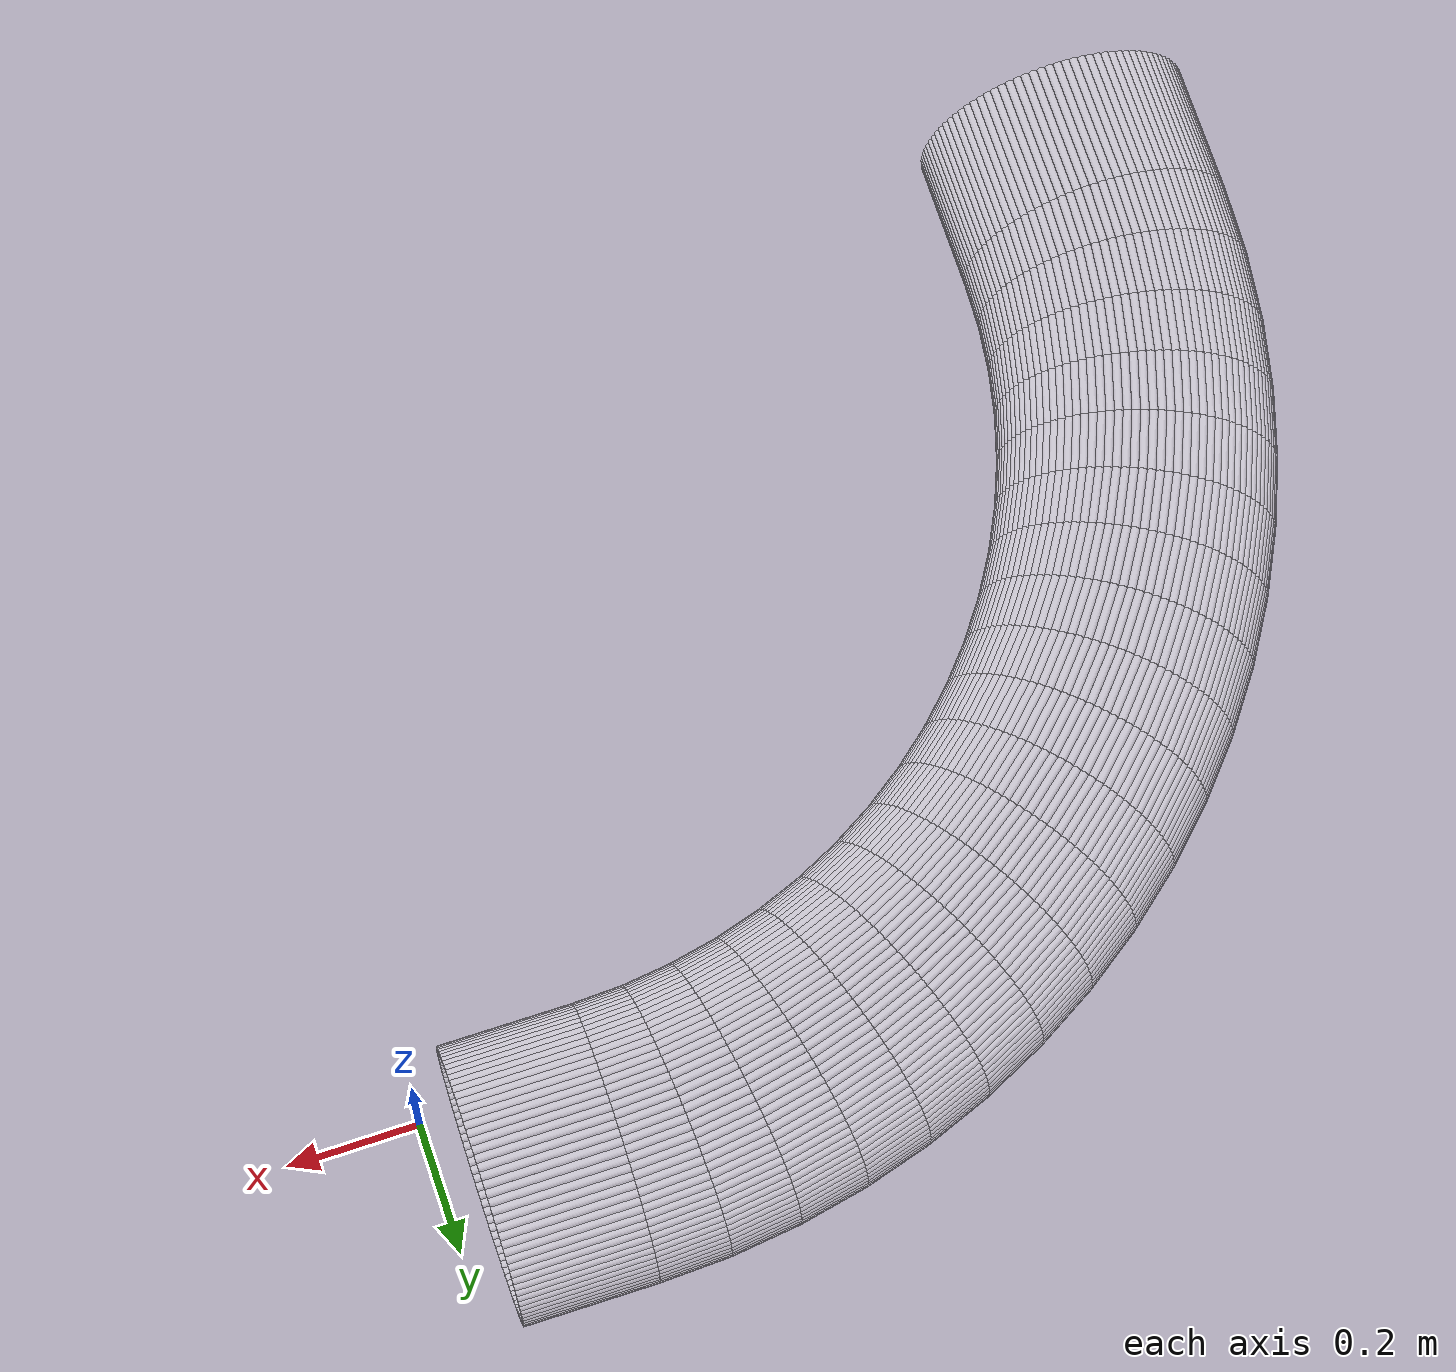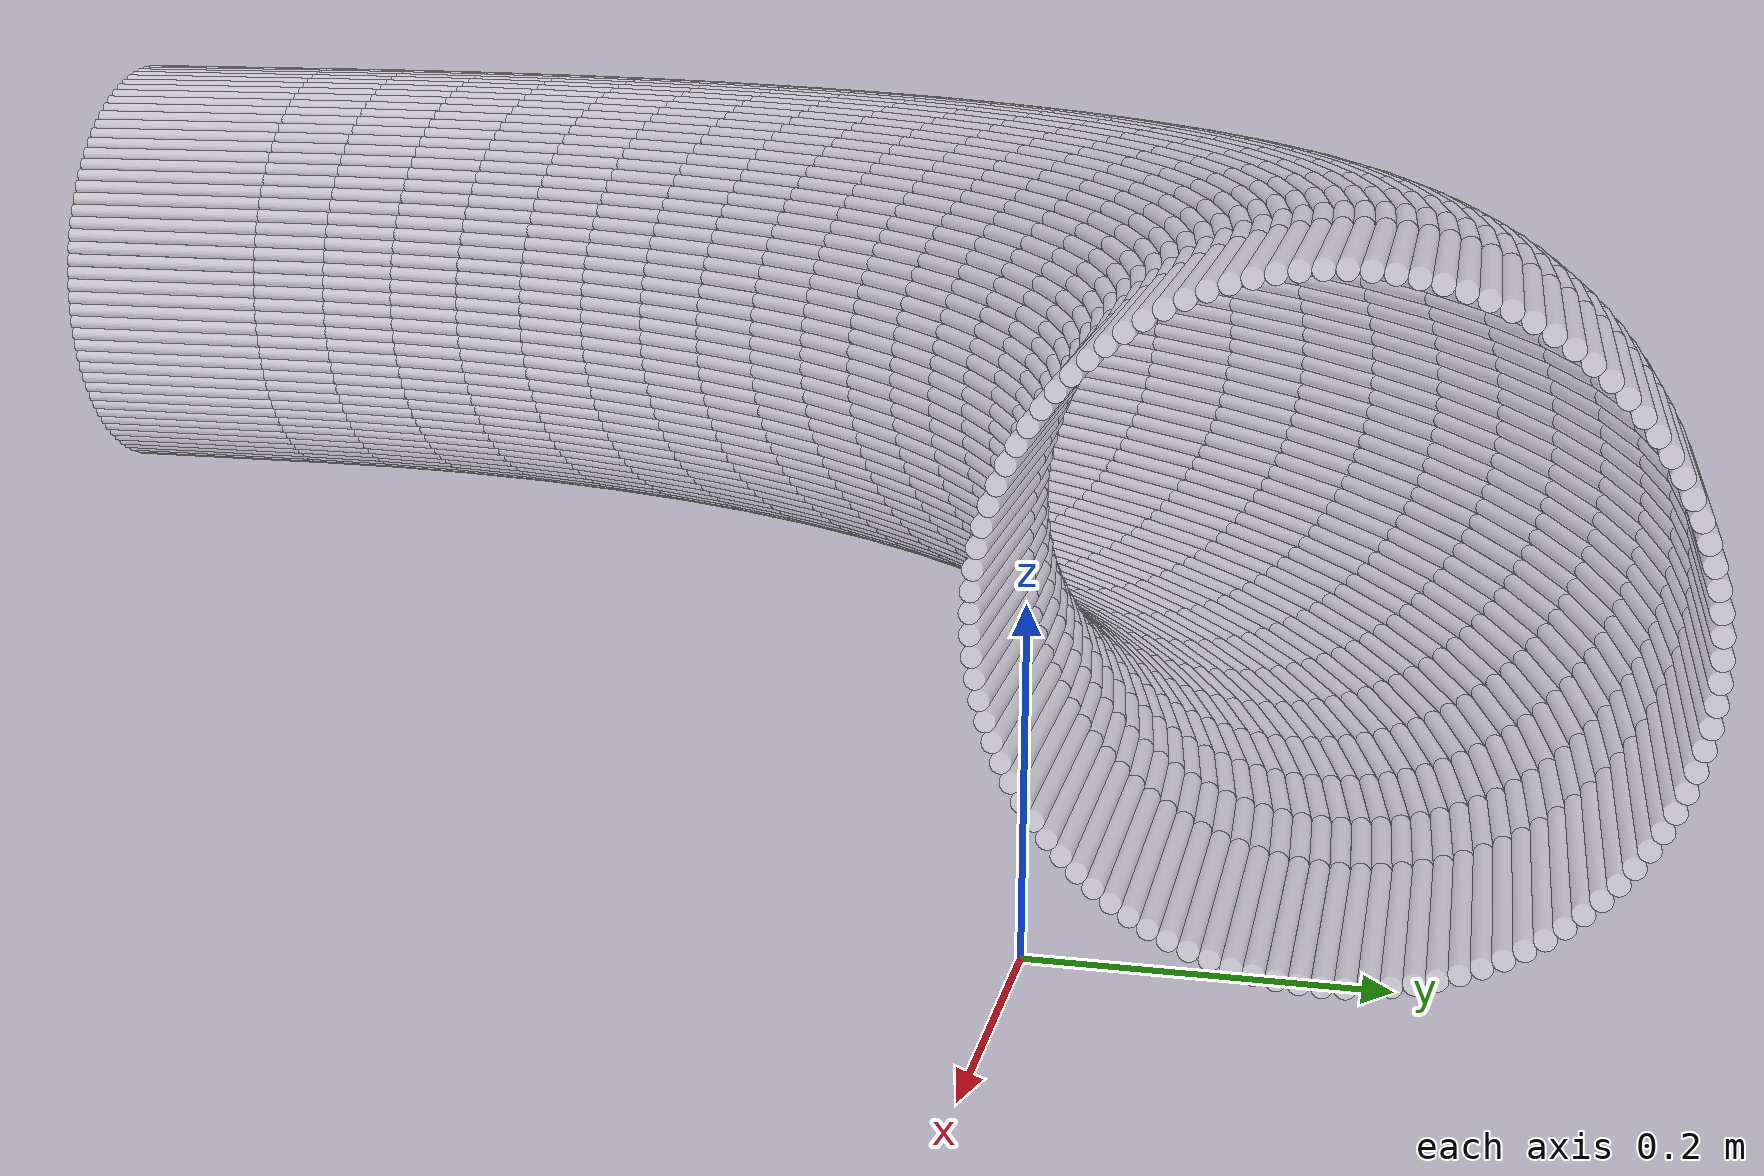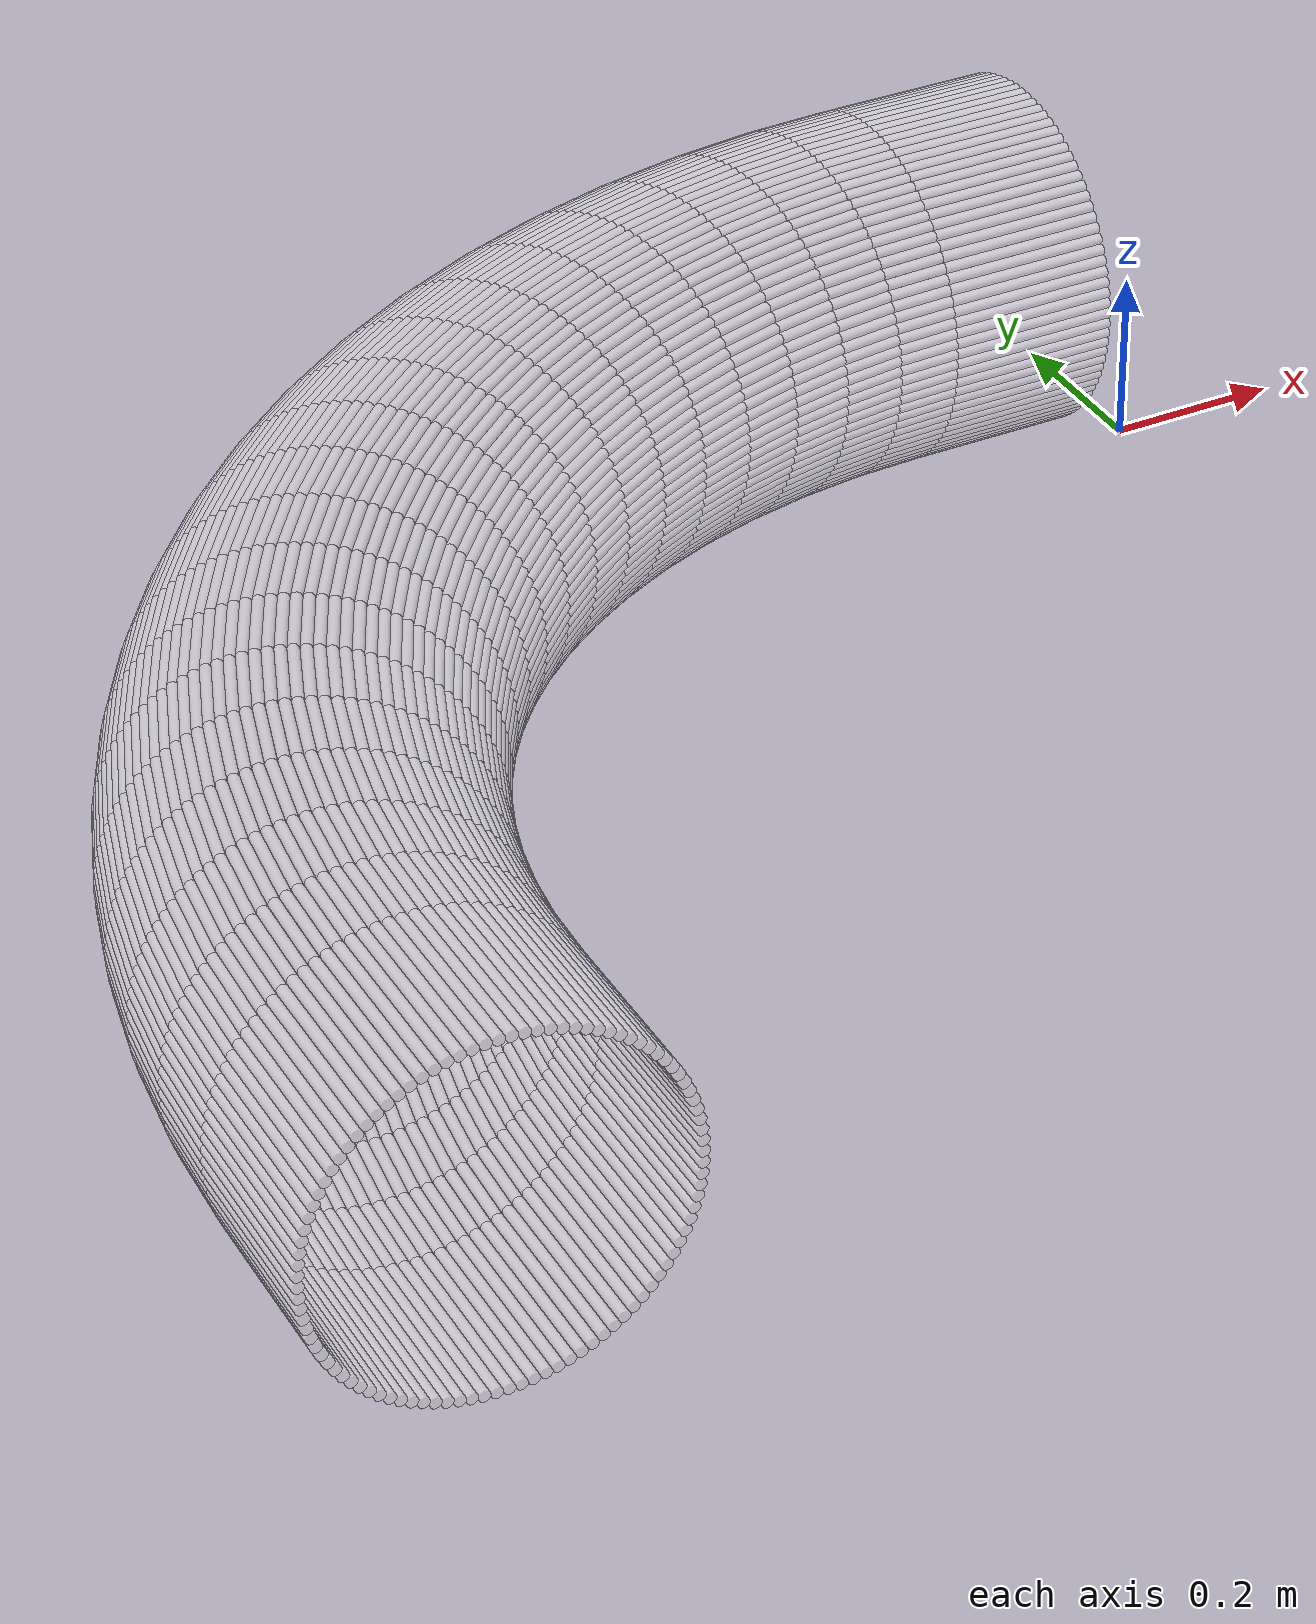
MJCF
<?xml version="1.0" encoding="utf-8"?>
<mujoco>
   <worldbody>
   <body pos="-0.25 -0.94 -0.02" euler="0 0 90">
      <geom euler=" 0 10 0 " fromto="1.3 -0.2 0.2 1.3 0 0.2" rgba="1 1 1 0.35"
            size="0.0062822"
            type="cylinder"/>
      <geom euler=" 0 20 0 " fromto="1.2996 -0.2 0.21256 1.2996 0 0.21256"
            rgba="1 1 1 0.35"
            size="0.0062822"
            type="cylinder"/>
      <geom euler=" 0 30 0 " fromto="1.2984 -0.2 0.22507 1.2984 0 0.22507"
            rgba="1 1 1 0.35"
            size="0.0062822"
            type="cylinder"/>
      <geom euler=" 0 40 0 " fromto="1.2965 -0.2 0.23748 1.2965 0 0.23748"
            rgba="1 1 1 0.35"
            size="0.0062822"
            type="cylinder"/>
      <geom euler=" 0 50 0 " fromto="1.2937 -0.2 0.24974 1.2937 0 0.24974"
            rgba="1 1 1 0.35"
            size="0.0062822"
            type="cylinder"/>
      <geom euler=" 0 60 0 " fromto="1.2902 -0.2 0.2618 1.2902 0 0.2618" rgba="1 1 1 0.35"
            size="0.0062822"
            type="cylinder"/>
      <geom euler=" 0 70 0 " fromto="1.286 -0.2 0.27362 1.286 0 0.27362" rgba="1 1 1 0.35"
            size="0.0062822"
            type="cylinder"/>
      <geom euler=" 0 80 0 " fromto="1.281 -0.2 0.28516 1.281 0 0.28516" rgba="1 1 1 0.35"
            size="0.0062822"
            type="cylinder"/>
      <geom euler=" 0 90 0 " fromto="1.2753 -0.2 0.29635 1.2753 0 0.29635"
            rgba="1 1 1 0.35"
            size="0.0062822"
            type="cylinder"/>
      <geom euler=" 0 100 0 " fromto="1.2689 -0.2 0.30717 1.2689 0 0.30717"
            rgba="1 1 1 0.35"
            size="0.0062822"
            type="cylinder"/>
      <geom euler=" 0 110 0 " fromto="1.2618 -0.2 0.31756 1.2618 0 0.31756"
            rgba="1 1 1 0.35"
            size="0.0062822"
            type="cylinder"/>
      <geom euler=" 0 120 0 " fromto="1.2541 -0.2 0.32748 1.2541 0 0.32748"
            rgba="1 1 1 0.35"
            size="0.0062822"
            type="cylinder"/>
      <geom euler=" 0 130 0 " fromto="1.2458 -0.2 0.33691 1.2458 0 0.33691"
            rgba="1 1 1 0.35"
            size="0.0062822"
            type="cylinder"/>
      <geom euler=" 0 140 0 " fromto="1.2369 -0.2 0.34579 1.2369 0 0.34579"
            rgba="1 1 1 0.35"
            size="0.0062822"
            type="cylinder"/>
      <geom euler=" 0 150 0 " fromto="1.2275 -0.2 0.3541 1.2275 0 0.3541" rgba="1 1 1 0.35"
            size="0.0062822"
            type="cylinder"/>
      <geom euler=" 0 160 0 " fromto="1.2176 -0.2 0.3618 1.2176 0 0.3618" rgba="1 1 1 0.35"
            size="0.0062822"
            type="cylinder"/>
      <geom euler=" 0 170 0 " fromto="1.2072 -0.2 0.36887 1.2072 0 0.36887"
            rgba="1 1 1 0.35"
            size="0.0062822"
            type="cylinder"/>
      <geom euler=" 0 180 0 " fromto="1.1964 -0.2 0.37526 1.1964 0 0.37526"
            rgba="1 1 1 0.35"
            size="0.0062822"
            type="cylinder"/>
      <geom euler=" 0 190 0 " fromto="1.1852 -0.2 0.38097 1.1852 0 0.38097"
            rgba="1 1 1 0.35"
            size="0.0062822"
            type="cylinder"/>
      <geom euler=" 0 200 0 " fromto="1.1736 -0.2 0.38596 1.1736 0 0.38596"
            rgba="1 1 1 0.35"
            size="0.0062822"
            type="cylinder"/>
      <geom euler=" 0 210 0 " fromto="1.1618 -0.2 0.39021 1.1618 0 0.39021"
            rgba="1 1 1 0.35"
            size="0.0062822"
            type="cylinder"/>
      <geom euler=" 0 220 0 " fromto="1.1497 -0.2 0.39372 1.1497 0 0.39372"
            rgba="1 1 1 0.35"
            size="0.0062822"
            type="cylinder"/>
      <geom euler=" 0 230 0 " fromto="1.1375 -0.2 0.39646 1.1375 0 0.39646"
            rgba="1 1 1 0.35"
            size="0.0062822"
            type="cylinder"/>
      <geom euler=" 0 240 0 " fromto="1.1251 -0.2 0.39842 1.1251 0 0.39842"
            rgba="1 1 1 0.35"
            size="0.0062822"
            type="cylinder"/>
      <geom euler=" 0 250 0 " fromto="1.1126 -0.2 0.39961 1.1126 0 0.39961"
            rgba="1 1 1 0.35"
            size="0.0062822"
            type="cylinder"/>
      <geom euler=" 0 260 0 " fromto="1.1 -0.2 0.4 1.1 0 0.4" rgba="1 1 1 0.35"
            size="0.0062822"
            type="cylinder"/>
      <geom euler=" 0 270 0 " fromto="1.0874 -0.2 0.39961 1.0874 0 0.39961"
            rgba="1 1 1 0.35"
            size="0.0062822"
            type="cylinder"/>
      <geom euler=" 0 280 0 " fromto="1.0749 -0.2 0.39842 1.0749 0 0.39842"
            rgba="1 1 1 0.35"
            size="0.0062822"
            type="cylinder"/>
      <geom euler=" 0 290 0 " fromto="1.0625 -0.2 0.39646 1.0625 0 0.39646"
            rgba="1 1 1 0.35"
            size="0.0062822"
            type="cylinder"/>
      <geom euler=" 0 300 0 " fromto="1.0503 -0.2 0.39372 1.0503 0 0.39372"
            rgba="1 1 1 0.35"
            size="0.0062822"
            type="cylinder"/>
      <geom euler=" 0 310 0 " fromto="1.0382 -0.2 0.39021 1.0382 0 0.39021"
            rgba="1 1 1 0.35"
            size="0.0062822"
            type="cylinder"/>
      <geom euler=" 0 320 0 " fromto="1.0264 -0.2 0.38596 1.0264 0 0.38596"
            rgba="1 1 1 0.35"
            size="0.0062822"
            type="cylinder"/>
      <geom euler=" 0 330 0 " fromto="1.0148 -0.2 0.38097 1.0148 0 0.38097"
            rgba="1 1 1 0.35"
            size="0.0062822"
            type="cylinder"/>
      <geom euler=" 0 340 0 " fromto="1.0036 -0.2 0.37526 1.0036 0 0.37526"
            rgba="1 1 1 0.35"
            size="0.0062822"
            type="cylinder"/>
      <geom euler=" 0 350 0 " fromto="0.99283 -0.2 0.36887 0.99283 0 0.36887"
            rgba="1 1 1 0.35"
            size="0.0062822"
            type="cylinder"/>
      <geom euler=" 0 360 0 " fromto="0.98244 -0.2 0.3618 0.98244 0 0.3618"
            rgba="1 1 1 0.35"
            size="0.0062822"
            type="cylinder"/>
      <geom euler=" 0 370 0 " fromto="0.97252 -0.2 0.3541 0.97252 0 0.3541"
            rgba="1 1 1 0.35"
            size="0.0062822"
            type="cylinder"/>
      <geom euler=" 0 380 0 " fromto="0.96309 -0.2 0.34579 0.96309 0 0.34579"
            rgba="1 1 1 0.35"
            size="0.0062822"
            type="cylinder"/>
      <geom euler=" 0 390 0 " fromto="0.95421 -0.2 0.33691 0.95421 0 0.33691"
            rgba="1 1 1 0.35"
            size="0.0062822"
            type="cylinder"/>
      <geom euler=" 0 400 0 " fromto="0.9459 -0.2 0.32748 0.9459 0 0.32748"
            rgba="1 1 1 0.35"
            size="0.0062822"
            type="cylinder"/>
      <geom euler=" 0 410 0 " fromto="0.9382 -0.2 0.31756 0.9382 0 0.31756"
            rgba="1 1 1 0.35"
            size="0.0062822"
            type="cylinder"/>
      <geom euler=" 0 420 0 " fromto="0.93113 -0.2 0.30717 0.93113 0 0.30717"
            rgba="1 1 1 0.35"
            size="0.0062822"
            type="cylinder"/>
      <geom euler=" 0 430 0 " fromto="0.92474 -0.2 0.29635 0.92474 0 0.29635"
            rgba="1 1 1 0.35"
            size="0.0062822"
            type="cylinder"/>
      <geom euler=" 0 440 0 " fromto="0.91903 -0.2 0.28516 0.91903 0 0.28516"
            rgba="1 1 1 0.35"
            size="0.0062822"
            type="cylinder"/>
      <geom euler=" 0 450 0 " fromto="0.91404 -0.2 0.27362 0.91404 0 0.27362"
            rgba="1 1 1 0.35"
            size="0.0062822"
            type="cylinder"/>
      <geom euler=" 0 460 0 " fromto="0.90979 -0.2 0.2618 0.90979 0 0.2618"
            rgba="1 1 1 0.35"
            size="0.0062822"
            type="cylinder"/>
      <geom euler=" 0 470 0 " fromto="0.90628 -0.2 0.24974 0.90628 0 0.24974"
            rgba="1 1 1 0.35"
            size="0.0062822"
            type="cylinder"/>
      <geom euler=" 0 480 0 " fromto="0.90354 -0.2 0.23748 0.90354 0 0.23748"
            rgba="1 1 1 0.35"
            size="0.0062822"
            type="cylinder"/>
      <geom euler=" 0 490 0 " fromto="0.90158 -0.2 0.22507 0.90158 0 0.22507"
            rgba="1 1 1 0.35"
            size="0.0062822"
            type="cylinder"/>
      <geom euler=" 0 500 0 " fromto="0.90039 -0.2 0.21256 0.90039 0 0.21256"
            rgba="1 1 1 0.35"
            size="0.0062822"
            type="cylinder"/>
      <geom euler=" 0 510 0 " fromto="0.9 -0.2 0.2 0.9 0 0.2" rgba="1 1 1 0.35"
            size="0.0062822"
            type="cylinder"/>
      <geom euler=" 0 520 0 " fromto="0.90039 -0.2 0.18744 0.90039 0 0.18744"
            rgba="1 1 1 0.35"
            size="0.0062822"
            type="cylinder"/>
      <geom euler=" 0 530 0 " fromto="0.90158 -0.2 0.17493 0.90158 0 0.17493"
            rgba="1 1 1 0.35"
            size="0.0062822"
            type="cylinder"/>
      <geom euler=" 0 540 0 " fromto="0.90354 -0.2 0.16252 0.90354 0 0.16252"
            rgba="1 1 1 0.35"
            size="0.0062822"
            type="cylinder"/>
      <geom euler=" 0 550 0 " fromto="0.90628 -0.2 0.15026 0.90628 0 0.15026"
            rgba="1 1 1 0.35"
            size="0.0062822"
            type="cylinder"/>
      <geom euler=" 0 560 0 " fromto="0.90979 -0.2 0.1382 0.90979 0 0.1382"
            rgba="1 1 1 0.35"
            size="0.0062822"
            type="cylinder"/>
      <geom euler=" 0 570 0 " fromto="0.91404 -0.2 0.12638 0.91404 0 0.12638"
            rgba="1 1 1 0.35"
            size="0.0062822"
            type="cylinder"/>
      <geom euler=" 0 580 0 " fromto="0.91903 -0.2 0.11484 0.91903 0 0.11484"
            rgba="1 1 1 0.35"
            size="0.0062822"
            type="cylinder"/>
      <geom euler=" 0 590 0 " fromto="0.92474 -0.2 0.10365 0.92474 0 0.10365"
            rgba="1 1 1 0.35"
            size="0.0062822"
            type="cylinder"/>
      <geom euler=" 0 600 0 " fromto="0.93113 -0.2 0.092835 0.93113 0 0.092835"
            rgba="1 1 1 0.35"
            size="0.0062822"
            type="cylinder"/>
      <geom euler=" 0 610 0 " fromto="0.9382 -0.2 0.082443 0.9382 0 0.082443"
            rgba="1 1 1 0.35"
            size="0.0062822"
            type="cylinder"/>
      <geom euler=" 0 620 0 " fromto="0.9459 -0.2 0.072515 0.9459 0 0.072515"
            rgba="1 1 1 0.35"
            size="0.0062822"
            type="cylinder"/>
      <geom euler=" 0 630 0 " fromto="0.95421 -0.2 0.063091 0.95421 0 0.063091"
            rgba="1 1 1 0.35"
            size="0.0062822"
            type="cylinder"/>
      <geom euler=" 0 640 0 " fromto="0.96309 -0.2 0.054206 0.96309 0 0.054206"
            rgba="1 1 1 0.35"
            size="0.0062822"
            type="cylinder"/>
      <geom euler=" 0 650 0 " fromto="0.97252 -0.2 0.045897 0.97252 0 0.045897"
            rgba="1 1 1 0.35"
            size="0.0062822"
            type="cylinder"/>
      <geom euler=" 0 660 0 " fromto="0.98244 -0.2 0.038197 0.98244 0 0.038197"
            rgba="1 1 1 0.35"
            size="0.0062822"
            type="cylinder"/>
      <geom euler=" 0 670 0 " fromto="0.99283 -0.2 0.031134 0.99283 0 0.031134"
            rgba="1 1 1 0.35"
            size="0.0062822"
            type="cylinder"/>
      <geom euler=" 0 680 0 " fromto="1.0036 -0.2 0.024739 1.0036 0 0.024739"
            rgba="1 1 1 0.35"
            size="0.0062822"
            type="cylinder"/>
      <geom euler=" 0 690 0 " fromto="1.0148 -0.2 0.019035 1.0148 0 0.019035"
            rgba="1 1 1 0.35"
            size="0.0062822"
            type="cylinder"/>
      <geom euler=" 0 700 0 " fromto="1.0264 -0.2 0.014045 1.0264 0 0.014045"
            rgba="1 1 1 0.35"
            size="0.0062822"
            type="cylinder"/>
      <geom euler=" 0 710 0 " fromto="1.0382 -0.2 0.0097887 1.0382 0 0.0097887"
            rgba="1 1 1 0.35"
            size="0.0062822"
            type="cylinder"/>
      <geom euler=" 0 720 0 " fromto="1.0503 -0.2 0.0062834 1.0503 0 0.0062834"
            rgba="1 1 1 0.35"
            size="0.0062822"
            type="cylinder"/>
      <geom euler=" 0 730 0 " fromto="1.0625 -0.2 0.0035425 1.0625 0 0.0035425"
            rgba="1 1 1 0.35"
            size="0.0062822"
            type="cylinder"/>
      <geom euler=" 0 740 0 " fromto="1.0749 -0.2 0.0015771 1.0749 0 0.0015771"
            rgba="1 1 1 0.35"
            size="0.0062822"
            type="cylinder"/>
      <geom euler=" 0 750 0 " fromto="1.0874 -0.2 0.00039465 1.0874 0 0.00039465"
            rgba="1 1 1 0.35"
            size="0.0062822"
            type="cylinder"/>
      <geom euler=" 0 760 0 " fromto="1.1 -0.2 0 1.1 0 0" rgba="1 1 1 0.35"
            size="0.0062822"
            type="cylinder"/>
      <geom euler=" 0 770 0 " fromto="1.1126 -0.2 0.00039465 1.1126 0 0.00039465"
            rgba="1 1 1 0.35"
            size="0.0062822"
            type="cylinder"/>
      <geom euler=" 0 780 0 " fromto="1.1251 -0.2 0.0015771 1.1251 0 0.0015771"
            rgba="1 1 1 0.35"
            size="0.0062822"
            type="cylinder"/>
      <geom euler=" 0 790 0 " fromto="1.1375 -0.2 0.0035425 1.1375 0 0.0035425"
            rgba="1 1 1 0.35"
            size="0.0062822"
            type="cylinder"/>
      <geom euler=" 0 800 0 " fromto="1.1497 -0.2 0.0062834 1.1497 0 0.0062834"
            rgba="1 1 1 0.35"
            size="0.0062822"
            type="cylinder"/>
      <geom euler=" 0 810 0 " fromto="1.1618 -0.2 0.0097887 1.1618 0 0.0097887"
            rgba="1 1 1 0.35"
            size="0.0062822"
            type="cylinder"/>
      <geom euler=" 0 820 0 " fromto="1.1736 -0.2 0.014045 1.1736 0 0.014045"
            rgba="1 1 1 0.35"
            size="0.0062822"
            type="cylinder"/>
      <geom euler=" 0 830 0 " fromto="1.1852 -0.2 0.019035 1.1852 0 0.019035"
            rgba="1 1 1 0.35"
            size="0.0062822"
            type="cylinder"/>
      <geom euler=" 0 840 0 " fromto="1.1964 -0.2 0.024739 1.1964 0 0.024739"
            rgba="1 1 1 0.35"
            size="0.0062822"
            type="cylinder"/>
      <geom euler=" 0 850 0 " fromto="1.2072 -0.2 0.031134 1.2072 0 0.031134"
            rgba="1 1 1 0.35"
            size="0.0062822"
            type="cylinder"/>
      <geom euler=" 0 860 0 " fromto="1.2176 -0.2 0.038197 1.2176 0 0.038197"
            rgba="1 1 1 0.35"
            size="0.0062822"
            type="cylinder"/>
      <geom euler=" 0 870 0 " fromto="1.2275 -0.2 0.045897 1.2275 0 0.045897"
            rgba="1 1 1 0.35"
            size="0.0062822"
            type="cylinder"/>
      <geom euler=" 0 880 0 " fromto="1.2369 -0.2 0.054206 1.2369 0 0.054206"
            rgba="1 1 1 0.35"
            size="0.0062822"
            type="cylinder"/>
      <geom euler=" 0 890 0 " fromto="1.2458 -0.2 0.063091 1.2458 0 0.063091"
            rgba="1 1 1 0.35"
            size="0.0062822"
            type="cylinder"/>
      <geom euler=" 0 900 0 " fromto="1.2541 -0.2 0.072515 1.2541 0 0.072515"
            rgba="1 1 1 0.35"
            size="0.0062822"
            type="cylinder"/>
      <geom euler=" 0 910 0 " fromto="1.2618 -0.2 0.082443 1.2618 0 0.082443"
            rgba="1 1 1 0.35"
            size="0.0062822"
            type="cylinder"/>
      <geom euler=" 0 920 0 " fromto="1.2689 -0.2 0.092835 1.2689 0 0.092835"
            rgba="1 1 1 0.35"
            size="0.0062822"
            type="cylinder"/>
      <geom euler=" 0 930 0 " fromto="1.2753 -0.2 0.10365 1.2753 0 0.10365"
            rgba="1 1 1 0.35"
            size="0.0062822"
            type="cylinder"/>
      <geom euler=" 0 940 0 " fromto="1.281 -0.2 0.11484 1.281 0 0.11484" rgba="1 1 1 0.35"
            size="0.0062822"
            type="cylinder"/>
      <geom euler=" 0 950 0 " fromto="1.286 -0.2 0.12638 1.286 0 0.12638" rgba="1 1 1 0.35"
            size="0.0062822"
            type="cylinder"/>
      <geom euler=" 0 960 0 " fromto="1.2902 -0.2 0.1382 1.2902 0 0.1382" rgba="1 1 1 0.35"
            size="0.0062822"
            type="cylinder"/>
      <geom euler=" 0 970 0 " fromto="1.2937 -0.2 0.15026 1.2937 0 0.15026"
            rgba="1 1 1 0.35"
            size="0.0062822"
            type="cylinder"/>
      <geom euler=" 0 980 0 " fromto="1.2965 -0.2 0.16252 1.2965 0 0.16252"
            rgba="1 1 1 0.35"
            size="0.0062822"
            type="cylinder"/>
      <geom euler=" 0 990 0 " fromto="1.2984 -0.2 0.17493 1.2984 0 0.17493"
            rgba="1 1 1 0.35"
            size="0.0062822"
            type="cylinder"/>
      <geom euler=" 0 1000 0 " fromto="1.2996 -0.2 0.18744 1.2996 0 0.18744"
            rgba="1 1 1 0.35"
            size="0.0062822"
            type="cylinder"/>
      <geom euler=" 0 10 0 " fromto="1.3 0 0.2 1.2956 0.10735 0.2" rgba="1 1 1 0.35"
            size="0.0062822"
            type="cylinder"/>
      <geom euler=" 0 20 0 " fromto="1.2996 0 0.21256 1.2952 0.10732 0.21256"
            rgba="1 1 1 0.35"
            size="0.0062822"
            type="cylinder"/>
      <geom euler=" 0 30 0 " fromto="1.2984 0 0.22507 1.294 0.10722 0.22507"
            rgba="1 1 1 0.35"
            size="0.0062822"
            type="cylinder"/>
      <geom euler=" 0 40 0 " fromto="1.2965 0 0.23748 1.292 0.10706 0.23748"
            rgba="1 1 1 0.35"
            size="0.0062822"
            type="cylinder"/>
      <geom euler=" 0 50 0 " fromto="1.2937 0 0.24974 1.2893 0.10683 0.24974"
            rgba="1 1 1 0.35"
            size="0.0062822"
            type="cylinder"/>
      <geom euler=" 0 60 0 " fromto="1.2902 0 0.2618 1.2858 0.10654 0.2618"
            rgba="1 1 1 0.35"
            size="0.0062822"
            type="cylinder"/>
      <geom euler=" 0 70 0 " fromto="1.286 0 0.27362 1.2816 0.10619 0.27362"
            rgba="1 1 1 0.35"
            size="0.0062822"
            type="cylinder"/>
      <geom euler=" 0 80 0 " fromto="1.281 0 0.28516 1.2766 0.10578 0.28516"
            rgba="1 1 1 0.35"
            size="0.0062822"
            type="cylinder"/>
      <geom euler=" 0 90 0 " fromto="1.2753 0 0.29635 1.2709 0.10531 0.29635"
            rgba="1 1 1 0.35"
            size="0.0062822"
            type="cylinder"/>
      <geom euler=" 0 100 0 " fromto="1.2689 0 0.30717 1.2645 0.10478 0.30717"
            rgba="1 1 1 0.35"
            size="0.0062822"
            type="cylinder"/>
      <geom euler=" 0 110 0 " fromto="1.2618 0 0.31756 1.2575 0.1042 0.31756"
            rgba="1 1 1 0.35"
            size="0.0062822"
            type="cylinder"/>
      <geom euler=" 0 120 0 " fromto="1.2541 0 0.32748 1.2498 0.10356 0.32748"
            rgba="1 1 1 0.35"
            size="0.0062822"
            type="cylinder"/>
      <geom euler=" 0 130 0 " fromto="1.2458 0 0.33691 1.2415 0.10288 0.33691"
            rgba="1 1 1 0.35"
            size="0.0062822"
            type="cylinder"/>
      <geom euler=" 0 140 0 " fromto="1.2369 0 0.34579 1.2327 0.10214 0.34579"
            rgba="1 1 1 0.35"
            size="0.0062822"
            type="cylinder"/>
      <geom euler=" 0 150 0 " fromto="1.2275 0 0.3541 1.2233 0.10136 0.3541"
            rgba="1 1 1 0.35"
            size="0.0062822"
            type="cylinder"/>
      <geom euler=" 0 160 0 " fromto="1.2176 0 0.3618 1.2134 0.10055 0.3618"
            rgba="1 1 1 0.35"
            size="0.0062822"
            type="cylinder"/>
      <geom euler=" 0 170 0 " fromto="1.2072 0 0.36887 1.203 0.099687 0.36887"
            rgba="1 1 1 0.35"
            size="0.0062822"
            type="cylinder"/>
      <geom euler=" 0 180 0 " fromto="1.1964 0 0.37526 1.1923 0.098794 0.37526"
            rgba="1 1 1 0.35"
            size="0.0062822"
            type="cylinder"/>
      <geom euler=" 0 190 0 " fromto="1.1852 0 0.38097 1.1811 0.097869 0.38097"
            rgba="1 1 1 0.35"
            size="0.0062822"
            type="cylinder"/>
      <geom euler=" 0 200 0 " fromto="1.1736 0 0.38596 1.1696 0.096917 0.38596"
            rgba="1 1 1 0.35"
            size="0.0062822"
            type="cylinder"/>
      <geom euler=" 0 210 0 " fromto="1.1618 0 0.39021 1.1578 0.095941 0.39021"
            rgba="1 1 1 0.35"
            size="0.0062822"
            type="cylinder"/>
      <geom euler=" 0 220 0 " fromto="1.1497 0 0.39372 1.1458 0.094945 0.39372"
            rgba="1 1 1 0.35"
            size="0.0062822"
            type="cylinder"/>
      <geom euler=" 0 230 0 " fromto="1.1375 0 0.39646 1.1336 0.093932 0.39646"
            rgba="1 1 1 0.35"
            size="0.0062822"
            type="cylinder"/>
      <geom euler=" 0 240 0 " fromto="1.1251 0 0.39842 1.1212 0.092907 0.39842"
            rgba="1 1 1 0.35"
            size="0.0062822"
            type="cylinder"/>
      <geom euler=" 0 250 0 " fromto="1.1126 0 0.39961 1.1088 0.091874 0.39961"
            rgba="1 1 1 0.35"
            size="0.0062822"
            type="cylinder"/>
      <geom euler=" 0 260 0 " fromto="1.1 0 0.4 1.0962 0.090837 0.4" rgba="1 1 1 0.35"
            size="0.0062822"
            type="cylinder"/>
      <geom euler=" 0 270 0 " fromto="1.0874 0 0.39961 1.0837 0.0898 0.39961"
            rgba="1 1 1 0.35"
            size="0.0062822"
            type="cylinder"/>
      <geom euler=" 0 280 0 " fromto="1.0749 0 0.39842 1.0713 0.088767 0.39842"
            rgba="1 1 1 0.35"
            size="0.0062822"
            type="cylinder"/>
      <geom euler=" 0 290 0 " fromto="1.0625 0 0.39646 1.0589 0.087743 0.39646"
            rgba="1 1 1 0.35"
            size="0.0062822"
            type="cylinder"/>
      <geom euler=" 0 300 0 " fromto="1.0503 0 0.39372 1.0467 0.08673 0.39372"
            rgba="1 1 1 0.35"
            size="0.0062822"
            type="cylinder"/>
      <geom euler=" 0 310 0 " fromto="1.0382 0 0.39021 1.0347 0.085734 0.39021"
            rgba="1 1 1 0.35"
            size="0.0062822"
            type="cylinder"/>
      <geom euler=" 0 320 0 " fromto="1.0264 0 0.38596 1.0229 0.084757 0.38596"
            rgba="1 1 1 0.35"
            size="0.0062822"
            type="cylinder"/>
      <geom euler=" 0 330 0 " fromto="1.0148 0 0.38097 1.0114 0.083805 0.38097"
            rgba="1 1 1 0.35"
            size="0.0062822"
            type="cylinder"/>
      <geom euler=" 0 340 0 " fromto="1.0036 0 0.37526 1.0002 0.082881 0.37526"
            rgba="1 1 1 0.35"
            size="0.0062822"
            type="cylinder"/>
      <geom euler=" 0 350 0 " fromto="0.99283 0 0.36887 0.98944 0.081988 0.36887"
            rgba="1 1 1 0.35"
            size="0.0062822"
            type="cylinder"/>
      <geom euler=" 0 360 0 " fromto="0.98244 0 0.3618 0.97909 0.081129 0.3618"
            rgba="1 1 1 0.35"
            size="0.0062822"
            type="cylinder"/>
      <geom euler=" 0 370 0 " fromto="0.97252 0 0.3541 0.96919 0.08031 0.3541"
            rgba="1 1 1 0.35"
            size="0.0062822"
            type="cylinder"/>
      <geom euler=" 0 380 0 " fromto="0.96309 0 0.34579 0.9598 0.079531 0.34579"
            rgba="1 1 1 0.35"
            size="0.0062822"
            type="cylinder"/>
      <geom euler=" 0 390 0 " fromto="0.95421 0 0.33691 0.95095 0.078798 0.33691"
            rgba="1 1 1 0.35"
            size="0.0062822"
            type="cylinder"/>
      <geom euler=" 0 400 0 " fromto="0.9459 0 0.32748 0.94267 0.078112 0.32748"
            rgba="1 1 1 0.35"
            size="0.0062822"
            type="cylinder"/>
      <geom euler=" 0 410 0 " fromto="0.9382 0 0.31756 0.93499 0.077476 0.31756"
            rgba="1 1 1 0.35"
            size="0.0062822"
            type="cylinder"/>
      <geom euler=" 0 420 0 " fromto="0.93113 0 0.30717 0.92795 0.076892 0.30717"
            rgba="1 1 1 0.35"
            size="0.0062822"
            type="cylinder"/>
      <geom euler=" 0 430 0 " fromto="0.92474 0 0.29635 0.92158 0.076364 0.29635"
            rgba="1 1 1 0.35"
            size="0.0062822"
            type="cylinder"/>
      <geom euler=" 0 440 0 " fromto="0.91903 0 0.28516 0.9159 0.075893 0.28516"
            rgba="1 1 1 0.35"
            size="0.0062822"
            type="cylinder"/>
      <geom euler=" 0 450 0 " fromto="0.91404 0 0.27362 0.91092 0.075481 0.27362"
            rgba="1 1 1 0.35"
            size="0.0062822"
            type="cylinder"/>
      <geom euler=" 0 460 0 " fromto="0.90979 0 0.2618 0.90668 0.07513 0.2618"
            rgba="1 1 1 0.35"
            size="0.0062822"
            type="cylinder"/>
      <geom euler=" 0 470 0 " fromto="0.90628 0 0.24974 0.90319 0.07484 0.24974"
            rgba="1 1 1 0.35"
            size="0.0062822"
            type="cylinder"/>
      <geom euler=" 0 480 0 " fromto="0.90354 0 0.23748 0.90046 0.074614 0.23748"
            rgba="1 1 1 0.35"
            size="0.0062822"
            type="cylinder"/>
      <geom euler=" 0 490 0 " fromto="0.90158 0 0.22507 0.8985 0.074452 0.22507"
            rgba="1 1 1 0.35"
            size="0.0062822"
            type="cylinder"/>
      <geom euler=" 0 500 0 " fromto="0.90039 0 0.21256 0.89732 0.074354 0.21256"
            rgba="1 1 1 0.35"
            size="0.0062822"
            type="cylinder"/>
      <geom euler=" 0 510 0 " fromto="0.9 0 0.2 0.89693 0.074321 0.2" rgba="1 1 1 0.35"
            size="0.0062822"
            type="cylinder"/>
      <geom euler=" 0 520 0 " fromto="0.90039 0 0.18744 0.89732 0.074354 0.18744"
            rgba="1 1 1 0.35"
            size="0.0062822"
            type="cylinder"/>
      <geom euler=" 0 530 0 " fromto="0.90158 0 0.17493 0.8985 0.074452 0.17493"
            rgba="1 1 1 0.35"
            size="0.0062822"
            type="cylinder"/>
      <geom euler=" 0 540 0 " fromto="0.90354 0 0.16252 0.90046 0.074614 0.16252"
            rgba="1 1 1 0.35"
            size="0.0062822"
            type="cylinder"/>
      <geom euler=" 0 550 0 " fromto="0.90628 0 0.15026 0.90319 0.07484 0.15026"
            rgba="1 1 1 0.35"
            size="0.0062822"
            type="cylinder"/>
      <geom euler=" 0 560 0 " fromto="0.90979 0 0.1382 0.90668 0.07513 0.1382"
            rgba="1 1 1 0.35"
            size="0.0062822"
            type="cylinder"/>
      <geom euler=" 0 570 0 " fromto="0.91404 0 0.12638 0.91092 0.075481 0.12638"
            rgba="1 1 1 0.35"
            size="0.0062822"
            type="cylinder"/>
      <geom euler=" 0 580 0 " fromto="0.91903 0 0.11484 0.9159 0.075893 0.11484"
            rgba="1 1 1 0.35"
            size="0.0062822"
            type="cylinder"/>
      <geom euler=" 0 590 0 " fromto="0.92474 0 0.10365 0.92158 0.076364 0.10365"
            rgba="1 1 1 0.35"
            size="0.0062822"
            type="cylinder"/>
      <geom euler=" 0 600 0 " fromto="0.93113 0 0.092835 0.92795 0.076892 0.092835"
            rgba="1 1 1 0.35"
            size="0.0062822"
            type="cylinder"/>
      <geom euler=" 0 610 0 " fromto="0.9382 0 0.082443 0.93499 0.077476 0.082443"
            rgba="1 1 1 0.35"
            size="0.0062822"
            type="cylinder"/>
      <geom euler=" 0 620 0 " fromto="0.9459 0 0.072515 0.94267 0.078112 0.072515"
            rgba="1 1 1 0.35"
            size="0.0062822"
            type="cylinder"/>
      <geom euler=" 0 630 0 " fromto="0.95421 0 0.063091 0.95095 0.078798 0.063091"
            rgba="1 1 1 0.35"
            size="0.0062822"
            type="cylinder"/>
      <geom euler=" 0 640 0 " fromto="0.96309 0 0.054206 0.9598 0.079531 0.054206"
            rgba="1 1 1 0.35"
            size="0.0062822"
            type="cylinder"/>
      <geom euler=" 0 650 0 " fromto="0.97252 0 0.045897 0.96919 0.08031 0.045897"
            rgba="1 1 1 0.35"
            size="0.0062822"
            type="cylinder"/>
      <geom euler=" 0 660 0 " fromto="0.98244 0 0.038197 0.97909 0.081129 0.038197"
            rgba="1 1 1 0.35"
            size="0.0062822"
            type="cylinder"/>
      <geom euler=" 0 670 0 " fromto="0.99283 0 0.031134 0.98944 0.081988 0.031134"
            rgba="1 1 1 0.35"
            size="0.0062822"
            type="cylinder"/>
      <geom euler=" 0 680 0 " fromto="1.0036 0 0.024739 1.0002 0.082881 0.024739"
            rgba="1 1 1 0.35"
            size="0.0062822"
            type="cylinder"/>
      <geom euler=" 0 690 0 " fromto="1.0148 0 0.019035 1.0114 0.083805 0.019035"
            rgba="1 1 1 0.35"
            size="0.0062822"
            type="cylinder"/>
      <geom euler=" 0 700 0 " fromto="1.0264 0 0.014045 1.0229 0.084757 0.014045"
            rgba="1 1 1 0.35"
            size="0.0062822"
            type="cylinder"/>
      <geom euler=" 0 710 0 " fromto="1.0382 0 0.0097887 1.0347 0.085734 0.0097887"
            rgba="1 1 1 0.35"
            size="0.0062822"
            type="cylinder"/>
      <geom euler=" 0 720 0 " fromto="1.0503 0 0.0062834 1.0467 0.08673 0.0062834"
            rgba="1 1 1 0.35"
            size="0.0062822"
            type="cylinder"/>
      <geom euler=" 0 730 0 " fromto="1.0625 0 0.0035425 1.0589 0.087743 0.0035425"
            rgba="1 1 1 0.35"
            size="0.0062822"
            type="cylinder"/>
      <geom euler=" 0 740 0 " fromto="1.0749 0 0.0015771 1.0713 0.088767 0.0015771"
            rgba="1 1 1 0.35"
            size="0.0062822"
            type="cylinder"/>
      <geom euler=" 0 750 0 " fromto="1.0874 0 0.00039465 1.0837 0.0898 0.00039465"
            rgba="1 1 1 0.35"
            size="0.0062822"
            type="cylinder"/>
      <geom euler=" 0 760 0 " fromto="1.1 0 0 1.0962 0.090837 0" rgba="1 1 1 0.35"
            size="0.0062822"
            type="cylinder"/>
      <geom euler=" 0 770 0 " fromto="1.1126 0 0.00039465 1.1088 0.091874 0.00039465"
            rgba="1 1 1 0.35"
            size="0.0062822"
            type="cylinder"/>
      <geom euler=" 0 780 0 " fromto="1.1251 0 0.0015771 1.1212 0.092907 0.0015771"
            rgba="1 1 1 0.35"
            size="0.0062822"
            type="cylinder"/>
      <geom euler=" 0 790 0 " fromto="1.1375 0 0.0035425 1.1336 0.093932 0.0035425"
            rgba="1 1 1 0.35"
            size="0.0062822"
            type="cylinder"/>
      <geom euler=" 0 800 0 " fromto="1.1497 0 0.0062834 1.1458 0.094945 0.0062834"
            rgba="1 1 1 0.35"
            size="0.0062822"
            type="cylinder"/>
      <geom euler=" 0 810 0 " fromto="1.1618 0 0.0097887 1.1578 0.095941 0.0097887"
            rgba="1 1 1 0.35"
            size="0.0062822"
            type="cylinder"/>
      <geom euler=" 0 820 0 " fromto="1.1736 0 0.014045 1.1696 0.096917 0.014045"
            rgba="1 1 1 0.35"
            size="0.0062822"
            type="cylinder"/>
      <geom euler=" 0 830 0 " fromto="1.1852 0 0.019035 1.1811 0.097869 0.019035"
            rgba="1 1 1 0.35"
            size="0.0062822"
            type="cylinder"/>
      <geom euler=" 0 840 0 " fromto="1.1964 0 0.024739 1.1923 0.098794 0.024739"
            rgba="1 1 1 0.35"
            size="0.0062822"
            type="cylinder"/>
      <geom euler=" 0 850 0 " fromto="1.2072 0 0.031134 1.203 0.099687 0.031134"
            rgba="1 1 1 0.35"
            size="0.0062822"
            type="cylinder"/>
      <geom euler=" 0 860 0 " fromto="1.2176 0 0.038197 1.2134 0.10055 0.038197"
            rgba="1 1 1 0.35"
            size="0.0062822"
            type="cylinder"/>
      <geom euler=" 0 870 0 " fromto="1.2275 0 0.045897 1.2233 0.10136 0.045897"
            rgba="1 1 1 0.35"
            size="0.0062822"
            type="cylinder"/>
      <geom euler=" 0 880 0 " fromto="1.2369 0 0.054206 1.2327 0.10214 0.054206"
            rgba="1 1 1 0.35"
            size="0.0062822"
            type="cylinder"/>
      <geom euler=" 0 890 0 " fromto="1.2458 0 0.063091 1.2415 0.10288 0.063091"
            rgba="1 1 1 0.35"
            size="0.0062822"
            type="cylinder"/>
      <geom euler=" 0 900 0 " fromto="1.2541 0 0.072515 1.2498 0.10356 0.072515"
            rgba="1 1 1 0.35"
            size="0.0062822"
            type="cylinder"/>
      <geom euler=" 0 910 0 " fromto="1.2618 0 0.082443 1.2575 0.1042 0.082443"
            rgba="1 1 1 0.35"
            size="0.0062822"
            type="cylinder"/>
      <geom euler=" 0 920 0 " fromto="1.2689 0 0.092835 1.2645 0.10478 0.092835"
            rgba="1 1 1 0.35"
            size="0.0062822"
            type="cylinder"/>
      <geom euler=" 0 930 0 " fromto="1.2753 0 0.10365 1.2709 0.10531 0.10365"
            rgba="1 1 1 0.35"
            size="0.0062822"
            type="cylinder"/>
      <geom euler=" 0 940 0 " fromto="1.281 0 0.11484 1.2766 0.10578 0.11484"
            rgba="1 1 1 0.35"
            size="0.0062822"
            type="cylinder"/>
      <geom euler=" 0 950 0 " fromto="1.286 0 0.12638 1.2816 0.10619 0.12638"
            rgba="1 1 1 0.35"
            size="0.0062822"
            type="cylinder"/>
      <geom euler=" 0 960 0 " fromto="1.2902 0 0.1382 1.2858 0.10654 0.1382"
            rgba="1 1 1 0.35"
            size="0.0062822"
            type="cylinder"/>
      <geom euler=" 0 970 0 " fromto="1.2937 0 0.15026 1.2893 0.10683 0.15026"
            rgba="1 1 1 0.35"
            size="0.0062822"
            type="cylinder"/>
      <geom euler=" 0 980 0 " fromto="1.2965 0 0.16252 1.292 0.10706 0.16252"
            rgba="1 1 1 0.35"
            size="0.0062822"
            type="cylinder"/>
      <geom euler=" 0 990 0 " fromto="1.2984 0 0.17493 1.294 0.10722 0.17493"
            rgba="1 1 1 0.35"
            size="0.0062822"
            type="cylinder"/>
      <geom euler=" 0 1000 0 " fromto="1.2996 0 0.18744 1.2952 0.10732 0.18744"
            rgba="1 1 1 0.35"
            size="0.0062822"
            type="cylinder"/>
      <geom euler=" 0 10 0 " fromto="1.2956 0.10735 0.2 1.2823 0.21397 0.2"
            rgba="1 1 1 0.35"
            size="0.0062822"
            type="cylinder"/>
      <geom euler=" 0 20 0 " fromto="1.2952 0.10732 0.21256 1.2819 0.21391 0.21256"
            rgba="1 1 1 0.35"
            size="0.0062822"
            type="cylinder"/>
      <geom euler=" 0 30 0 " fromto="1.294 0.10722 0.22507 1.2807 0.21371 0.22507"
            rgba="1 1 1 0.35"
            size="0.0062822"
            type="cylinder"/>
      <geom euler=" 0 40 0 " fromto="1.292 0.10706 0.23748 1.2788 0.21339 0.23748"
            rgba="1 1 1 0.35"
            size="0.0062822"
            type="cylinder"/>
      <geom euler=" 0 50 0 " fromto="1.2893 0.10683 0.24974 1.2761 0.21294 0.24974"
            rgba="1 1 1 0.35"
            size="0.0062822"
            type="cylinder"/>
      <geom euler=" 0 60 0 " fromto="1.2858 0.10654 0.2618 1.2726 0.21236 0.2618"
            rgba="1 1 1 0.35"
            size="0.0062822"
            type="cylinder"/>
      <geom euler=" 0 70 0 " fromto="1.2816 0.10619 0.27362 1.2684 0.21166 0.27362"
            rgba="1 1 1 0.35"
            size="0.0062822"
            type="cylinder"/>
      <geom euler=" 0 80 0 " fromto="1.2766 0.10578 0.28516 1.2635 0.21084 0.28516"
            rgba="1 1 1 0.35"
            size="0.0062822"
            type="cylinder"/>
      <geom euler=" 0 90 0 " fromto="1.2709 0.10531 0.29635 1.2579 0.2099 0.29635"
            rgba="1 1 1 0.35"
            size="0.0062822"
            type="cylinder"/>
      <geom euler=" 0 100 0 " fromto="1.2645 0.10478 0.30717 1.2516 0.20885 0.30717"
            rgba="1 1 1 0.35"
            size="0.0062822"
            type="cylinder"/>
      <geom euler=" 0 110 0 " fromto="1.2575 0.1042 0.31756 1.2446 0.20769 0.31756"
            rgba="1 1 1 0.35"
            size="0.0062822"
            type="cylinder"/>
      <geom euler=" 0 120 0 " fromto="1.2498 0.10356 0.32748 1.237 0.20642 0.32748"
            rgba="1 1 1 0.35"
            size="0.0062822"
            type="cylinder"/>
      <geom euler=" 0 130 0 " fromto="1.2415 0.10288 0.33691 1.2288 0.20505 0.33691"
            rgba="1 1 1 0.35"
            size="0.0062822"
            type="cylinder"/>
      <geom euler=" 0 140 0 " fromto="1.2327 0.10214 0.34579 1.22 0.20359 0.34579"
            rgba="1 1 1 0.35"
            size="0.0062822"
            type="cylinder"/>
      <geom euler=" 0 150 0 " fromto="1.2233 0.10136 0.3541 1.2107 0.20204 0.3541"
            rgba="1 1 1 0.35"
            size="0.0062822"
            type="cylinder"/>
      <geom euler=" 0 160 0 " fromto="1.2134 0.10055 0.3618 1.201 0.2004 0.3618"
            rgba="1 1 1 0.35"
            size="0.0062822"
            type="cylinder"/>
      <geom euler=" 0 170 0 " fromto="1.203 0.099687 0.36887 1.1907 0.19869 0.36887"
            rgba="1 1 1 0.35"
            size="0.0062822"
            type="cylinder"/>
      <geom euler=" 0 180 0 " fromto="1.1923 0.098794 0.37526 1.18 0.19691 0.37526"
            rgba="1 1 1 0.35"
            size="0.0062822"
            type="cylinder"/>
      <geom euler=" 0 190 0 " fromto="1.1811 0.097869 0.38097 1.169 0.19507 0.38097"
            rgba="1 1 1 0.35"
            size="0.0062822"
            type="cylinder"/>
      <geom euler=" 0 200 0 " fromto="1.1696 0.096917 0.38596 1.1576 0.19317 0.38596"
            rgba="1 1 1 0.35"
            size="0.0062822"
            type="cylinder"/>
      <geom euler=" 0 210 0 " fromto="1.1578 0.095941 0.39021 1.146 0.19123 0.39021"
            rgba="1 1 1 0.35"
            size="0.0062822"
            type="cylinder"/>
      <geom euler=" 0 220 0 " fromto="1.1458 0.094945 0.39372 1.1341 0.18924 0.39372"
            rgba="1 1 1 0.35"
            size="0.0062822"
            type="cylinder"/>
      <geom euler=" 0 230 0 " fromto="1.1336 0.093932 0.39646 1.122 0.18722 0.39646"
            rgba="1 1 1 0.35"
            size="0.0062822"
            type="cylinder"/>
      <geom euler=" 0 240 0 " fromto="1.1212 0.092907 0.39842 1.1097 0.18518 0.39842"
            rgba="1 1 1 0.35"
            size="0.0062822"
            type="cylinder"/>
      <geom euler=" 0 250 0 " fromto="1.1088 0.091874 0.39961 1.0974 0.18312 0.39961"
            rgba="1 1 1 0.35"
            size="0.0062822"
            type="cylinder"/>
      <geom euler=" 0 260 0 " fromto="1.0962 0.090837 0.4 1.085 0.18105 0.4"
            rgba="1 1 1 0.35"
            size="0.0062822"
            type="cylinder"/>
      <geom euler=" 0 270 0 " fromto="1.0837 0.0898 0.39961 1.0726 0.17899 0.39961"
            rgba="1 1 1 0.35"
            size="0.0062822"
            type="cylinder"/>
      <geom euler=" 0 280 0 " fromto="1.0713 0.088767 0.39842 1.0603 0.17693 0.39842"
            rgba="1 1 1 0.35"
            size="0.0062822"
            type="cylinder"/>
      <geom euler=" 0 290 0 " fromto="1.0589 0.087743 0.39646 1.048 0.17489 0.39646"
            rgba="1 1 1 0.35"
            size="0.0062822"
            type="cylinder"/>
      <geom euler=" 0 300 0 " fromto="1.0467 0.08673 0.39372 1.0359 0.17287 0.39372"
            rgba="1 1 1 0.35"
            size="0.0062822"
            type="cylinder"/>
      <geom euler=" 0 310 0 " fromto="1.0347 0.085734 0.39021 1.024 0.17088 0.39021"
            rgba="1 1 1 0.35"
            size="0.0062822"
            type="cylinder"/>
      <geom euler=" 0 320 0 " fromto="1.0229 0.084757 0.38596 1.0124 0.16894 0.38596"
            rgba="1 1 1 0.35"
            size="0.0062822"
            type="cylinder"/>
      <geom euler=" 0 330 0 " fromto="1.0114 0.083805 0.38097 1.001 0.16704 0.38097"
            rgba="1 1 1 0.35"
            size="0.0062822"
            type="cylinder"/>
      <geom euler=" 0 340 0 " fromto="1.0002 0.082881 0.37526 0.98996 0.1652 0.37526"
            rgba="1 1 1 0.35"
            size="0.0062822"
            type="cylinder"/>
      <geom euler=" 0 350 0 " fromto="0.98944 0.081988 0.36887 0.97929 0.16342 0.36887"
            rgba="1 1 1 0.35"
            size="0.0062822"
            type="cylinder"/>
      <geom euler=" 0 360 0 " fromto="0.97909 0.081129 0.3618 0.96904 0.1617 0.3618"
            rgba="1 1 1 0.35"
            size="0.0062822"
            type="cylinder"/>
      <geom euler=" 0 370 0 " fromto="0.96919 0.08031 0.3541 0.95925 0.16007 0.3541"
            rgba="1 1 1 0.35"
            size="0.0062822"
            type="cylinder"/>
      <geom euler=" 0 380 0 " fromto="0.9598 0.079531 0.34579 0.94996 0.15852 0.34579"
            rgba="1 1 1 0.35"
            size="0.0062822"
            type="cylinder"/>
      <geom euler=" 0 390 0 " fromto="0.95095 0.078798 0.33691 0.94119 0.15706 0.33691"
            rgba="1 1 1 0.35"
            size="0.0062822"
            type="cylinder"/>
      <geom euler=" 0 400 0 " fromto="0.94267 0.078112 0.32748 0.933 0.15569 0.32748"
            rgba="1 1 1 0.35"
            size="0.0062822"
            type="cylinder"/>
      <geom euler=" 0 410 0 " fromto="0.93499 0.077476 0.31756 0.9254 0.15442 0.31756"
            rgba="1 1 1 0.35"
            size="0.0062822"
            type="cylinder"/>
      <geom euler=" 0 420 0 " fromto="0.92795 0.076892 0.30717 0.91843 0.15326 0.30717"
            rgba="1 1 1 0.35"
            size="0.0062822"
            type="cylinder"/>
      <geom euler=" 0 430 0 " fromto="0.92158 0.076364 0.29635 0.91213 0.15221 0.29635"
            rgba="1 1 1 0.35"
            size="0.0062822"
            type="cylinder"/>
      <geom euler=" 0 440 0 " fromto="0.9159 0.075893 0.28516 0.9065 0.15127 0.28516"
            rgba="1 1 1 0.35"
            size="0.0062822"
            type="cylinder"/>
      <geom euler=" 0 450 0 " fromto="0.91092 0.075481 0.27362 0.90158 0.15045 0.27362"
            rgba="1 1 1 0.35"
            size="0.0062822"
            type="cylinder"/>
      <geom euler=" 0 460 0 " fromto="0.90668 0.07513 0.2618 0.89738 0.14975 0.2618"
            rgba="1 1 1 0.35"
            size="0.0062822"
            type="cylinder"/>
      <geom euler=" 0 470 0 " fromto="0.90319 0.07484 0.24974 0.89392 0.14917 0.24974"
            rgba="1 1 1 0.35"
            size="0.0062822"
            type="cylinder"/>
      <geom euler=" 0 480 0 " fromto="0.90046 0.074614 0.23748 0.89122 0.14872 0.23748"
            rgba="1 1 1 0.35"
            size="0.0062822"
            type="cylinder"/>
      <geom euler=" 0 490 0 " fromto="0.8985 0.074452 0.22507 0.88928 0.14839 0.22507"
            rgba="1 1 1 0.35"
            size="0.0062822"
            type="cylinder"/>
      <geom euler=" 0 500 0 " fromto="0.89732 0.074354 0.21256 0.88811 0.1482 0.21256"
            rgba="1 1 1 0.35"
            size="0.0062822"
            type="cylinder"/>
      <geom euler=" 0 510 0 " fromto="0.89693 0.074321 0.2 0.88773 0.14814 0.2"
            rgba="1 1 1 0.35"
            size="0.0062822"
            type="cylinder"/>
      <geom euler=" 0 520 0 " fromto="0.89732 0.074354 0.18744 0.88811 0.1482 0.18744"
            rgba="1 1 1 0.35"
            size="0.0062822"
            type="cylinder"/>
      <geom euler=" 0 530 0 " fromto="0.8985 0.074452 0.17493 0.88928 0.14839 0.17493"
            rgba="1 1 1 0.35"
            size="0.0062822"
            type="cylinder"/>
      <geom euler=" 0 540 0 " fromto="0.90046 0.074614 0.16252 0.89122 0.14872 0.16252"
            rgba="1 1 1 0.35"
            size="0.0062822"
            type="cylinder"/>
      <geom euler=" 0 550 0 " fromto="0.90319 0.07484 0.15026 0.89392 0.14917 0.15026"
            rgba="1 1 1 0.35"
            size="0.0062822"
            type="cylinder"/>
      <geom euler=" 0 560 0 " fromto="0.90668 0.07513 0.1382 0.89738 0.14975 0.1382"
            rgba="1 1 1 0.35"
            size="0.0062822"
            type="cylinder"/>
      <geom euler=" 0 570 0 " fromto="0.91092 0.075481 0.12638 0.90158 0.15045 0.12638"
            rgba="1 1 1 0.35"
            size="0.0062822"
            type="cylinder"/>
      <geom euler=" 0 580 0 " fromto="0.9159 0.075893 0.11484 0.9065 0.15127 0.11484"
            rgba="1 1 1 0.35"
            size="0.0062822"
            type="cylinder"/>
      <geom euler=" 0 590 0 " fromto="0.92158 0.076364 0.10365 0.91213 0.15221 0.10365"
            rgba="1 1 1 0.35"
            size="0.0062822"
            type="cylinder"/>
      <geom euler=" 0 600 0 " fromto="0.92795 0.076892 0.092835 0.91843 0.15326 0.092835"
            rgba="1 1 1 0.35"
            size="0.0062822"
            type="cylinder"/>
      <geom euler=" 0 610 0 " fromto="0.93499 0.077476 0.082443 0.9254 0.15442 0.082443"
            rgba="1 1 1 0.35"
            size="0.0062822"
            type="cylinder"/>
      <geom euler=" 0 620 0 " fromto="0.94267 0.078112 0.072515 0.933 0.15569 0.072515"
            rgba="1 1 1 0.35"
            size="0.0062822"
            type="cylinder"/>
      <geom euler=" 0 630 0 " fromto="0.95095 0.078798 0.063091 0.94119 0.15706 0.063091"
            rgba="1 1 1 0.35"
            size="0.0062822"
            type="cylinder"/>
      <geom euler=" 0 640 0 " fromto="0.9598 0.079531 0.054206 0.94996 0.15852 0.054206"
            rgba="1 1 1 0.35"
            size="0.0062822"
            type="cylinder"/>
      <geom euler=" 0 650 0 " fromto="0.96919 0.08031 0.045897 0.95925 0.16007 0.045897"
            rgba="1 1 1 0.35"
            size="0.0062822"
            type="cylinder"/>
      <geom euler=" 0 660 0 " fromto="0.97909 0.081129 0.038197 0.96904 0.1617 0.038197"
            rgba="1 1 1 0.35"
            size="0.0062822"
            type="cylinder"/>
      <geom euler=" 0 670 0 " fromto="0.98944 0.081988 0.031134 0.97929 0.16342 0.031134"
            rgba="1 1 1 0.35"
            size="0.0062822"
            type="cylinder"/>
      <geom euler=" 0 680 0 " fromto="1.0002 0.082881 0.024739 0.98996 0.1652 0.024739"
            rgba="1 1 1 0.35"
            size="0.0062822"
            type="cylinder"/>
      <geom euler=" 0 690 0 " fromto="1.0114 0.083805 0.019035 1.001 0.16704 0.019035"
            rgba="1 1 1 0.35"
            size="0.0062822"
            type="cylinder"/>
      <geom euler=" 0 700 0 " fromto="1.0229 0.084757 0.014045 1.0124 0.16894 0.014045"
            rgba="1 1 1 0.35"
            size="0.0062822"
            type="cylinder"/>
      <geom euler=" 0 710 0 " fromto="1.0347 0.085734 0.0097887 1.024 0.17088 0.0097887"
            rgba="1 1 1 0.35"
            size="0.0062822"
            type="cylinder"/>
      <geom euler=" 0 720 0 " fromto="1.0467 0.08673 0.0062834 1.0359 0.17287 0.0062834"
            rgba="1 1 1 0.35"
            size="0.0062822"
            type="cylinder"/>
      <geom euler=" 0 730 0 " fromto="1.0589 0.087743 0.0035425 1.048 0.17489 0.0035425"
            rgba="1 1 1 0.35"
            size="0.0062822"
            type="cylinder"/>
      <geom euler=" 0 740 0 " fromto="1.0713 0.088767 0.0015771 1.0603 0.17693 0.0015771"
            rgba="1 1 1 0.35"
            size="0.0062822"
            type="cylinder"/>
      <geom euler=" 0 750 0 " fromto="1.0837 0.0898 0.00039465 1.0726 0.17899 0.00039465"
            rgba="1 1 1 0.35"
            size="0.0062822"
            type="cylinder"/>
      <geom euler=" 0 760 0 " fromto="1.0962 0.090837 0 1.085 0.18105 0" rgba="1 1 1 0.35"
            size="0.0062822"
            type="cylinder"/>
      <geom euler=" 0 770 0 " fromto="1.1088 0.091874 0.00039465 1.0974 0.18312 0.00039465"
            rgba="1 1 1 0.35"
            size="0.0062822"
            type="cylinder"/>
      <geom euler=" 0 780 0 " fromto="1.1212 0.092907 0.0015771 1.1097 0.18518 0.0015771"
            rgba="1 1 1 0.35"
            size="0.0062822"
            type="cylinder"/>
      <geom euler=" 0 790 0 " fromto="1.1336 0.093932 0.0035425 1.122 0.18722 0.0035425"
            rgba="1 1 1 0.35"
            size="0.0062822"
            type="cylinder"/>
      <geom euler=" 0 800 0 " fromto="1.1458 0.094945 0.0062834 1.1341 0.18924 0.0062834"
            rgba="1 1 1 0.35"
            size="0.0062822"
            type="cylinder"/>
      <geom euler=" 0 810 0 " fromto="1.1578 0.095941 0.0097887 1.146 0.19123 0.0097887"
            rgba="1 1 1 0.35"
            size="0.0062822"
            type="cylinder"/>
      <geom euler=" 0 820 0 " fromto="1.1696 0.096917 0.014045 1.1576 0.19317 0.014045"
            rgba="1 1 1 0.35"
            size="0.0062822"
            type="cylinder"/>
      <geom euler=" 0 830 0 " fromto="1.1811 0.097869 0.019035 1.169 0.19507 0.019035"
            rgba="1 1 1 0.35"
            size="0.0062822"
            type="cylinder"/>
      <geom euler=" 0 840 0 " fromto="1.1923 0.098794 0.024739 1.18 0.19691 0.024739"
            rgba="1 1 1 0.35"
            size="0.0062822"
            type="cylinder"/>
      <geom euler=" 0 850 0 " fromto="1.203 0.099687 0.031134 1.1907 0.19869 0.031134"
            rgba="1 1 1 0.35"
            size="0.0062822"
            type="cylinder"/>
      <geom euler=" 0 860 0 " fromto="1.2134 0.10055 0.038197 1.201 0.2004 0.038197"
            rgba="1 1 1 0.35"
            size="0.0062822"
            type="cylinder"/>
      <geom euler=" 0 870 0 " fromto="1.2233 0.10136 0.045897 1.2107 0.20204 0.045897"
            rgba="1 1 1 0.35"
            size="0.0062822"
            type="cylinder"/>
      <geom euler=" 0 880 0 " fromto="1.2327 0.10214 0.054206 1.22 0.20359 0.054206"
            rgba="1 1 1 0.35"
            size="0.0062822"
            type="cylinder"/>
      <geom euler=" 0 890 0 " fromto="1.2415 0.10288 0.063091 1.2288 0.20505 0.063091"
            rgba="1 1 1 0.35"
            size="0.0062822"
            type="cylinder"/>
      <geom euler=" 0 900 0 " fromto="1.2498 0.10356 0.072515 1.237 0.20642 0.072515"
            rgba="1 1 1 0.35"
            size="0.0062822"
            type="cylinder"/>
      <geom euler=" 0 910 0 " fromto="1.2575 0.1042 0.082443 1.2446 0.20769 0.082443"
            rgba="1 1 1 0.35"
            size="0.0062822"
            type="cylinder"/>
      <geom euler=" 0 920 0 " fromto="1.2645 0.10478 0.092835 1.2516 0.20885 0.092835"
            rgba="1 1 1 0.35"
            size="0.0062822"
            type="cylinder"/>
      <geom euler=" 0 930 0 " fromto="1.2709 0.10531 0.10365 1.2579 0.2099 0.10365"
            rgba="1 1 1 0.35"
            size="0.0062822"
            type="cylinder"/>
      <geom euler=" 0 940 0 " fromto="1.2766 0.10578 0.11484 1.2635 0.21084 0.11484"
            rgba="1 1 1 0.35"
            size="0.0062822"
            type="cylinder"/>
      <geom euler=" 0 950 0 " fromto="1.2816 0.10619 0.12638 1.2684 0.21166 0.12638"
            rgba="1 1 1 0.35"
            size="0.0062822"
            type="cylinder"/>
      <geom euler=" 0 960 0 " fromto="1.2858 0.10654 0.1382 1.2726 0.21236 0.1382"
            rgba="1 1 1 0.35"
            size="0.0062822"
            type="cylinder"/>
      <geom euler=" 0 970 0 " fromto="1.2893 0.10683 0.15026 1.2761 0.21294 0.15026"
            rgba="1 1 1 0.35"
            size="0.0062822"
            type="cylinder"/>
      <geom euler=" 0 980 0 " fromto="1.292 0.10706 0.16252 1.2788 0.21339 0.16252"
            rgba="1 1 1 0.35"
            size="0.0062822"
            type="cylinder"/>
      <geom euler=" 0 990 0 " fromto="1.294 0.10722 0.17493 1.2807 0.21371 0.17493"
            rgba="1 1 1 0.35"
            size="0.0062822"
            type="cylinder"/>
      <geom euler=" 0 1000 0 " fromto="1.2952 0.10732 0.18744 1.2819 0.21391 0.18744"
            rgba="1 1 1 0.35"
            size="0.0062822"
            type="cylinder"/>
      <geom euler=" 0 10 0 " fromto="1.2823 0.21397 0.2 1.2602 0.31913 0.2"
            rgba="1 1 1 0.35"
            size="0.0062822"
            type="cylinder"/>
      <geom euler=" 0 20 0 " fromto="1.2819 0.21391 0.21256 1.2598 0.31903 0.21256"
            rgba="1 1 1 0.35"
            size="0.0062822"
            type="cylinder"/>
      <geom euler=" 0 30 0 " fromto="1.2807 0.21371 0.22507 1.2587 0.31874 0.22507"
            rgba="1 1 1 0.35"
            size="0.0062822"
            type="cylinder"/>
      <geom euler=" 0 40 0 " fromto="1.2788 0.21339 0.23748 1.2568 0.31826 0.23748"
            rgba="1 1 1 0.35"
            size="0.0062822"
            type="cylinder"/>
      <geom euler=" 0 50 0 " fromto="1.2761 0.21294 0.24974 1.2541 0.31759 0.24974"
            rgba="1 1 1 0.35"
            size="0.0062822"
            type="cylinder"/>
      <geom euler=" 0 60 0 " fromto="1.2726 0.21236 0.2618 1.2507 0.31673 0.2618"
            rgba="1 1 1 0.35"
            size="0.0062822"
            type="cylinder"/>
      <geom euler=" 0 70 0 " fromto="1.2684 0.21166 0.27362 1.2466 0.31568 0.27362"
            rgba="1 1 1 0.35"
            size="0.0062822"
            type="cylinder"/>
      <geom euler=" 0 80 0 " fromto="1.2635 0.21084 0.28516 1.2418 0.31446 0.28516"
            rgba="1 1 1 0.35"
            size="0.0062822"
            type="cylinder"/>
      <geom euler=" 0 90 0 " fromto="1.2579 0.2099 0.29635 1.2362 0.31306 0.29635"
            rgba="1 1 1 0.35"
            size="0.0062822"
            type="cylinder"/>
      <geom euler=" 0 100 0 " fromto="1.2516 0.20885 0.30717 1.23 0.31149 0.30717"
            rgba="1 1 1 0.35"
            size="0.0062822"
            type="cylinder"/>
      <geom euler=" 0 110 0 " fromto="1.2446 0.20769 0.31756 1.2232 0.30975 0.31756"
            rgba="1 1 1 0.35"
            size="0.0062822"
            type="cylinder"/>
      <geom euler=" 0 120 0 " fromto="1.237 0.20642 0.32748 1.2157 0.30786 0.32748"
            rgba="1 1 1 0.35"
            size="0.0062822"
            type="cylinder"/>
      <geom euler=" 0 130 0 " fromto="1.2288 0.20505 0.33691 1.2077 0.30582 0.33691"
            rgba="1 1 1 0.35"
            size="0.0062822"
            type="cylinder"/>
      <geom euler=" 0 140 0 " fromto="1.22 0.20359 0.34579 1.1991 0.30364 0.34579"
            rgba="1 1 1 0.35"
            size="0.0062822"
            type="cylinder"/>
      <geom euler=" 0 150 0 " fromto="1.2107 0.20204 0.3541 1.1899 0.30133 0.3541"
            rgba="1 1 1 0.35"
            size="0.0062822"
            type="cylinder"/>
      <geom euler=" 0 160 0 " fromto="1.201 0.2004 0.3618 1.1803 0.29889 0.3618"
            rgba="1 1 1 0.35"
            size="0.0062822"
            type="cylinder"/>
      <geom euler=" 0 170 0 " fromto="1.1907 0.19869 0.36887 1.1702 0.29634 0.36887"
            rgba="1 1 1 0.35"
            size="0.0062822"
            type="cylinder"/>
      <geom euler=" 0 180 0 " fromto="1.18 0.19691 0.37526 1.1597 0.29369 0.37526"
            rgba="1 1 1 0.35"
            size="0.0062822"
            type="cylinder"/>
      <geom euler=" 0 190 0 " fromto="1.169 0.19507 0.38097 1.1489 0.29094 0.38097"
            rgba="1 1 1 0.35"
            size="0.0062822"
            type="cylinder"/>
      <geom euler=" 0 200 0 " fromto="1.1576 0.19317 0.38596 1.1377 0.28811 0.38596"
            rgba="1 1 1 0.35"
            size="0.0062822"
            type="cylinder"/>
      <geom euler=" 0 210 0 " fromto="1.146 0.19123 0.39021 1.1263 0.28521 0.39021"
            rgba="1 1 1 0.35"
            size="0.0062822"
            type="cylinder"/>
      <geom euler=" 0 220 0 " fromto="1.1341 0.18924 0.39372 1.1146 0.28224 0.39372"
            rgba="1 1 1 0.35"
            size="0.0062822"
            type="cylinder"/>
      <geom euler=" 0 230 0 " fromto="1.122 0.18722 0.39646 1.1027 0.27923 0.39646"
            rgba="1 1 1 0.35"
            size="0.0062822"
            type="cylinder"/>
      <geom euler=" 0 240 0 " fromto="1.1097 0.18518 0.39842 1.0906 0.27619 0.39842"
            rgba="1 1 1 0.35"
            size="0.0062822"
            type="cylinder"/>
      <geom euler=" 0 250 0 " fromto="1.0974 0.18312 0.39961 1.0785 0.27312 0.39961"
            rgba="1 1 1 0.35"
            size="0.0062822"
            type="cylinder"/>
      <geom euler=" 0 260 0 " fromto="1.085 0.18105 0.4 1.0663 0.27003 0.4"
            rgba="1 1 1 0.35"
            size="0.0062822"
            type="cylinder"/>
      <geom euler=" 0 270 0 " fromto="1.0726 0.17899 0.39961 1.0542 0.26695 0.39961"
            rgba="1 1 1 0.35"
            size="0.0062822"
            type="cylinder"/>
      <geom euler=" 0 280 0 " fromto="1.0603 0.17693 0.39842 1.042 0.26388 0.39842"
            rgba="1 1 1 0.35"
            size="0.0062822"
            type="cylinder"/>
      <geom euler=" 0 290 0 " fromto="1.048 0.17489 0.39646 1.03 0.26083 0.39646"
            rgba="1 1 1 0.35"
            size="0.0062822"
            type="cylinder"/>
      <geom euler=" 0 300 0 " fromto="1.0359 0.17287 0.39372 1.0181 0.25782 0.39372"
            rgba="1 1 1 0.35"
            size="0.0062822"
            type="cylinder"/>
      <geom euler=" 0 310 0 " fromto="1.024 0.17088 0.39021 1.0064 0.25486 0.39021"
            rgba="1 1 1 0.35"
            size="0.0062822"
            type="cylinder"/>
      <geom euler=" 0 320 0 " fromto="1.0124 0.16894 0.38596 0.99497 0.25196 0.38596"
            rgba="1 1 1 0.35"
            size="0.0062822"
            type="cylinder"/>
      <geom euler=" 0 330 0 " fromto="1.001 0.16704 0.38097 0.98379 0.24913 0.38097"
            rgba="1 1 1 0.35"
            size="0.0062822"
            type="cylinder"/>
      <geom euler=" 0 340 0 " fromto="0.98996 0.1652 0.37526 0.97294 0.24638 0.37526"
            rgba="1 1 1 0.35"
            size="0.0062822"
            type="cylinder"/>
      <geom euler=" 0 350 0 " fromto="0.97929 0.16342 0.36887 0.96245 0.24373 0.36887"
            rgba="1 1 1 0.35"
            size="0.0062822"
            type="cylinder"/>
      <geom euler=" 0 360 0 " fromto="0.96904 0.1617 0.3618 0.95238 0.24118 0.3618"
            rgba="1 1 1 0.35"
            size="0.0062822"
            type="cylinder"/>
      <geom euler=" 0 370 0 " fromto="0.95925 0.16007 0.3541 0.94276 0.23874 0.3541"
            rgba="1 1 1 0.35"
            size="0.0062822"
            type="cylinder"/>
      <geom euler=" 0 380 0 " fromto="0.94996 0.15852 0.34579 0.93362 0.23642 0.34579"
            rgba="1 1 1 0.35"
            size="0.0062822"
            type="cylinder"/>
      <geom euler=" 0 390 0 " fromto="0.94119 0.15706 0.33691 0.92501 0.23424 0.33691"
            rgba="1 1 1 0.35"
            size="0.0062822"
            type="cylinder"/>
      <geom euler=" 0 400 0 " fromto="0.933 0.15569 0.32748 0.91695 0.2322 0.32748"
            rgba="1 1 1 0.35"
            size="0.0062822"
            type="cylinder"/>
      <geom euler=" 0 410 0 " fromto="0.9254 0.15442 0.31756 0.90949 0.23031 0.31756"
            rgba="1 1 1 0.35"
            size="0.0062822"
            type="cylinder"/>
      <geom euler=" 0 420 0 " fromto="0.91843 0.15326 0.30717 0.90264 0.22858 0.30717"
            rgba="1 1 1 0.35"
            size="0.0062822"
            type="cylinder"/>
      <geom euler=" 0 430 0 " fromto="0.91213 0.15221 0.29635 0.89644 0.22701 0.29635"
            rgba="1 1 1 0.35"
            size="0.0062822"
            type="cylinder"/>
      <geom euler=" 0 440 0 " fromto="0.9065 0.15127 0.28516 0.89091 0.22561 0.28516"
            rgba="1 1 1 0.35"
            size="0.0062822"
            type="cylinder"/>
      <geom euler=" 0 450 0 " fromto="0.90158 0.15045 0.27362 0.88608 0.22438 0.27362"
            rgba="1 1 1 0.35"
            size="0.0062822"
            type="cylinder"/>
      <geom euler=" 0 460 0 " fromto="0.89738 0.14975 0.2618 0.88195 0.22334 0.2618"
            rgba="1 1 1 0.35"
            size="0.0062822"
            type="cylinder"/>
      <geom euler=" 0 470 0 " fromto="0.89392 0.14917 0.24974 0.87855 0.22248 0.24974"
            rgba="1 1 1 0.35"
            size="0.0062822"
            type="cylinder"/>
      <geom euler=" 0 480 0 " fromto="0.89122 0.14872 0.23748 0.87589 0.22181 0.23748"
            rgba="1 1 1 0.35"
            size="0.0062822"
            type="cylinder"/>
      <geom euler=" 0 490 0 " fromto="0.88928 0.14839 0.22507 0.87399 0.22132 0.22507"
            rgba="1 1 1 0.35"
            size="0.0062822"
            type="cylinder"/>
      <geom euler=" 0 500 0 " fromto="0.88811 0.1482 0.21256 0.87284 0.22103 0.21256"
            rgba="1 1 1 0.35"
            size="0.0062822"
            type="cylinder"/>
      <geom euler=" 0 510 0 " fromto="0.88773 0.14814 0.2 0.87246 0.22094 0.2"
            rgba="1 1 1 0.35"
            size="0.0062822"
            type="cylinder"/>
      <geom euler=" 0 520 0 " fromto="0.88811 0.1482 0.18744 0.87284 0.22103 0.18744"
            rgba="1 1 1 0.35"
            size="0.0062822"
            type="cylinder"/>
      <geom euler=" 0 530 0 " fromto="0.88928 0.14839 0.17493 0.87399 0.22132 0.17493"
            rgba="1 1 1 0.35"
            size="0.0062822"
            type="cylinder"/>
      <geom euler=" 0 540 0 " fromto="0.89122 0.14872 0.16252 0.87589 0.22181 0.16252"
            rgba="1 1 1 0.35"
            size="0.0062822"
            type="cylinder"/>
      <geom euler=" 0 550 0 " fromto="0.89392 0.14917 0.15026 0.87855 0.22248 0.15026"
            rgba="1 1 1 0.35"
            size="0.0062822"
            type="cylinder"/>
      <geom euler=" 0 560 0 " fromto="0.89738 0.14975 0.1382 0.88195 0.22334 0.1382"
            rgba="1 1 1 0.35"
            size="0.0062822"
            type="cylinder"/>
      <geom euler=" 0 570 0 " fromto="0.90158 0.15045 0.12638 0.88608 0.22438 0.12638"
            rgba="1 1 1 0.35"
            size="0.0062822"
            type="cylinder"/>
      <geom euler=" 0 580 0 " fromto="0.9065 0.15127 0.11484 0.89091 0.22561 0.11484"
            rgba="1 1 1 0.35"
            size="0.0062822"
            type="cylinder"/>
      <geom euler=" 0 590 0 " fromto="0.91213 0.15221 0.10365 0.89644 0.22701 0.10365"
            rgba="1 1 1 0.35"
            size="0.0062822"
            type="cylinder"/>
      <geom euler=" 0 600 0 " fromto="0.91843 0.15326 0.092835 0.90264 0.22858 0.092835"
            rgba="1 1 1 0.35"
            size="0.0062822"
            type="cylinder"/>
      <geom euler=" 0 610 0 " fromto="0.9254 0.15442 0.082443 0.90949 0.23031 0.082443"
            rgba="1 1 1 0.35"
            size="0.0062822"
            type="cylinder"/>
      <geom euler=" 0 620 0 " fromto="0.933 0.15569 0.072515 0.91695 0.2322 0.072515"
            rgba="1 1 1 0.35"
            size="0.0062822"
            type="cylinder"/>
      <geom euler=" 0 630 0 " fromto="0.94119 0.15706 0.063091 0.92501 0.23424 0.063091"
            rgba="1 1 1 0.35"
            size="0.0062822"
            type="cylinder"/>
      <geom euler=" 0 640 0 " fromto="0.94996 0.15852 0.054206 0.93362 0.23642 0.054206"
            rgba="1 1 1 0.35"
            size="0.0062822"
            type="cylinder"/>
      <geom euler=" 0 650 0 " fromto="0.95925 0.16007 0.045897 0.94276 0.23874 0.045897"
            rgba="1 1 1 0.35"
            size="0.0062822"
            type="cylinder"/>
      <geom euler=" 0 660 0 " fromto="0.96904 0.1617 0.038197 0.95238 0.24118 0.038197"
            rgba="1 1 1 0.35"
            size="0.0062822"
            type="cylinder"/>
      <geom euler=" 0 670 0 " fromto="0.97929 0.16342 0.031134 0.96245 0.24373 0.031134"
            rgba="1 1 1 0.35"
            size="0.0062822"
            type="cylinder"/>
      <geom euler=" 0 680 0 " fromto="0.98996 0.1652 0.024739 0.97294 0.24638 0.024739"
            rgba="1 1 1 0.35"
            size="0.0062822"
            type="cylinder"/>
      <geom euler=" 0 690 0 " fromto="1.001 0.16704 0.019035 0.98379 0.24913 0.019035"
            rgba="1 1 1 0.35"
            size="0.0062822"
            type="cylinder"/>
      <geom euler=" 0 700 0 " fromto="1.0124 0.16894 0.014045 0.99497 0.25196 0.014045"
            rgba="1 1 1 0.35"
            size="0.0062822"
            type="cylinder"/>
      <geom euler=" 0 710 0 " fromto="1.024 0.17088 0.0097887 1.0064 0.25486 0.0097887"
            rgba="1 1 1 0.35"
            size="0.0062822"
            type="cylinder"/>
      <geom euler=" 0 720 0 " fromto="1.0359 0.17287 0.0062834 1.0181 0.25782 0.0062834"
            rgba="1 1 1 0.35"
            size="0.0062822"
            type="cylinder"/>
      <geom euler=" 0 730 0 " fromto="1.048 0.17489 0.0035425 1.03 0.26083 0.0035425"
            rgba="1 1 1 0.35"
            size="0.0062822"
            type="cylinder"/>
      <geom euler=" 0 740 0 " fromto="1.0603 0.17693 0.0015771 1.042 0.26388 0.0015771"
            rgba="1 1 1 0.35"
            size="0.0062822"
            type="cylinder"/>
      <geom euler=" 0 750 0 " fromto="1.0726 0.17899 0.00039465 1.0542 0.26695 0.00039465"
            rgba="1 1 1 0.35"
            size="0.0062822"
            type="cylinder"/>
      <geom euler=" 0 760 0 " fromto="1.085 0.18105 0 1.0663 0.27003 0" rgba="1 1 1 0.35"
            size="0.0062822"
            type="cylinder"/>
      <geom euler=" 0 770 0 " fromto="1.0974 0.18312 0.00039465 1.0785 0.27312 0.00039465"
            rgba="1 1 1 0.35"
            size="0.0062822"
            type="cylinder"/>
      <geom euler=" 0 780 0 " fromto="1.1097 0.18518 0.0015771 1.0906 0.27619 0.0015771"
            rgba="1 1 1 0.35"
            size="0.0062822"
            type="cylinder"/>
      <geom euler=" 0 790 0 " fromto="1.122 0.18722 0.0035425 1.1027 0.27923 0.0035425"
            rgba="1 1 1 0.35"
            size="0.0062822"
            type="cylinder"/>
      <geom euler=" 0 800 0 " fromto="1.1341 0.18924 0.0062834 1.1146 0.28224 0.0062834"
            rgba="1 1 1 0.35"
            size="0.0062822"
            type="cylinder"/>
      <geom euler=" 0 810 0 " fromto="1.146 0.19123 0.0097887 1.1263 0.28521 0.0097887"
            rgba="1 1 1 0.35"
            size="0.0062822"
            type="cylinder"/>
      <geom euler=" 0 820 0 " fromto="1.1576 0.19317 0.014045 1.1377 0.28811 0.014045"
            rgba="1 1 1 0.35"
            size="0.0062822"
            type="cylinder"/>
      <geom euler=" 0 830 0 " fromto="1.169 0.19507 0.019035 1.1489 0.29094 0.019035"
            rgba="1 1 1 0.35"
            size="0.0062822"
            type="cylinder"/>
      <geom euler=" 0 840 0 " fromto="1.18 0.19691 0.024739 1.1597 0.29369 0.024739"
            rgba="1 1 1 0.35"
            size="0.0062822"
            type="cylinder"/>
      <geom euler=" 0 850 0 " fromto="1.1907 0.19869 0.031134 1.1702 0.29634 0.031134"
            rgba="1 1 1 0.35"
            size="0.0062822"
            type="cylinder"/>
      <geom euler=" 0 860 0 " fromto="1.201 0.2004 0.038197 1.1803 0.29889 0.038197"
            rgba="1 1 1 0.35"
            size="0.0062822"
            type="cylinder"/>
      <geom euler=" 0 870 0 " fromto="1.2107 0.20204 0.045897 1.1899 0.30133 0.045897"
            rgba="1 1 1 0.35"
            size="0.0062822"
            type="cylinder"/>
      <geom euler=" 0 880 0 " fromto="1.22 0.20359 0.054206 1.1991 0.30364 0.054206"
            rgba="1 1 1 0.35"
            size="0.0062822"
            type="cylinder"/>
      <geom euler=" 0 890 0 " fromto="1.2288 0.20505 0.063091 1.2077 0.30582 0.063091"
            rgba="1 1 1 0.35"
            size="0.0062822"
            type="cylinder"/>
      <geom euler=" 0 900 0 " fromto="1.237 0.20642 0.072515 1.2157 0.30786 0.072515"
            rgba="1 1 1 0.35"
            size="0.0062822"
            type="cylinder"/>
      <geom euler=" 0 910 0 " fromto="1.2446 0.20769 0.082443 1.2232 0.30975 0.082443"
            rgba="1 1 1 0.35"
            size="0.0062822"
            type="cylinder"/>
      <geom euler=" 0 920 0 " fromto="1.2516 0.20885 0.092835 1.23 0.31149 0.092835"
            rgba="1 1 1 0.35"
            size="0.0062822"
            type="cylinder"/>
      <geom euler=" 0 930 0 " fromto="1.2579 0.2099 0.10365 1.2362 0.31306 0.10365"
            rgba="1 1 1 0.35"
            size="0.0062822"
            type="cylinder"/>
      <geom euler=" 0 940 0 " fromto="1.2635 0.21084 0.11484 1.2418 0.31446 0.11484"
            rgba="1 1 1 0.35"
            size="0.0062822"
            type="cylinder"/>
      <geom euler=" 0 950 0 " fromto="1.2684 0.21166 0.12638 1.2466 0.31568 0.12638"
            rgba="1 1 1 0.35"
            size="0.0062822"
            type="cylinder"/>
      <geom euler=" 0 960 0 " fromto="1.2726 0.21236 0.1382 1.2507 0.31673 0.1382"
            rgba="1 1 1 0.35"
            size="0.0062822"
            type="cylinder"/>
      <geom euler=" 0 970 0 " fromto="1.2761 0.21294 0.15026 1.2541 0.31759 0.15026"
            rgba="1 1 1 0.35"
            size="0.0062822"
            type="cylinder"/>
      <geom euler=" 0 980 0 " fromto="1.2788 0.21339 0.16252 1.2568 0.31826 0.16252"
            rgba="1 1 1 0.35"
            size="0.0062822"
            type="cylinder"/>
      <geom euler=" 0 990 0 " fromto="1.2807 0.21371 0.17493 1.2587 0.31874 0.17493"
            rgba="1 1 1 0.35"
            size="0.0062822"
            type="cylinder"/>
      <geom euler=" 0 1000 0 " fromto="1.2819 0.21391 0.18744 1.2598 0.31903 0.18744"
            rgba="1 1 1 0.35"
            size="0.0062822"
            type="cylinder"/>
      <geom euler=" 0 10 0 " fromto="1.2602 0.31913 0.2 1.2296 0.42211 0.2"
            rgba="1 1 1 0.35"
            size="0.0062822"
            type="cylinder"/>
      <geom euler=" 0 20 0 " fromto="1.2598 0.31903 0.21256 1.2292 0.42198 0.21256"
            rgba="1 1 1 0.35"
            size="0.0062822"
            type="cylinder"/>
      <geom euler=" 0 30 0 " fromto="1.2587 0.31874 0.22507 1.2281 0.4216 0.22507"
            rgba="1 1 1 0.35"
            size="0.0062822"
            type="cylinder"/>
      <geom euler=" 0 40 0 " fromto="1.2568 0.31826 0.23748 1.2262 0.42096 0.23748"
            rgba="1 1 1 0.35"
            size="0.0062822"
            type="cylinder"/>
      <geom euler=" 0 50 0 " fromto="1.2541 0.31759 0.24974 1.2236 0.42007 0.24974"
            rgba="1 1 1 0.35"
            size="0.0062822"
            type="cylinder"/>
      <geom euler=" 0 60 0 " fromto="1.2507 0.31673 0.2618 1.2203 0.41893 0.2618"
            rgba="1 1 1 0.35"
            size="0.0062822"
            type="cylinder"/>
      <geom euler=" 0 70 0 " fromto="1.2466 0.31568 0.27362 1.2163 0.41755 0.27362"
            rgba="1 1 1 0.35"
            size="0.0062822"
            type="cylinder"/>
      <geom euler=" 0 80 0 " fromto="1.2418 0.31446 0.28516 1.2116 0.41593 0.28516"
            rgba="1 1 1 0.35"
            size="0.0062822"
            type="cylinder"/>
      <geom euler=" 0 90 0 " fromto="1.2362 0.31306 0.29635 1.2062 0.41408 0.29635"
            rgba="1 1 1 0.35"
            size="0.0062822"
            type="cylinder"/>
      <geom euler=" 0 100 0 " fromto="1.23 0.31149 0.30717 1.2001 0.412 0.30717"
            rgba="1 1 1 0.35"
            size="0.0062822"
            type="cylinder"/>
      <geom euler=" 0 110 0 " fromto="1.2232 0.30975 0.31756 1.1934 0.40971 0.31756"
            rgba="1 1 1 0.35"
            size="0.0062822"
            type="cylinder"/>
      <geom euler=" 0 120 0 " fromto="1.2157 0.30786 0.32748 1.1862 0.40721 0.32748"
            rgba="1 1 1 0.35"
            size="0.0062822"
            type="cylinder"/>
      <geom euler=" 0 130 0 " fromto="1.2077 0.30582 0.33691 1.1783 0.40451 0.33691"
            rgba="1 1 1 0.35"
            size="0.0062822"
            type="cylinder"/>
      <geom euler=" 0 140 0 " fromto="1.1991 0.30364 0.34579 1.1699 0.40162 0.34579"
            rgba="1 1 1 0.35"
            size="0.0062822"
            type="cylinder"/>
      <geom euler=" 0 150 0 " fromto="1.1899 0.30133 0.3541 1.161 0.39856 0.3541"
            rgba="1 1 1 0.35"
            size="0.0062822"
            type="cylinder"/>
      <geom euler=" 0 160 0 " fromto="1.1803 0.29889 0.3618 1.1516 0.39534 0.3618"
            rgba="1 1 1 0.35"
            size="0.0062822"
            type="cylinder"/>
      <geom euler=" 0 170 0 " fromto="1.1702 0.29634 0.36887 1.1418 0.39197 0.36887"
            rgba="1 1 1 0.35"
            size="0.0062822"
            type="cylinder"/>
      <geom euler=" 0 180 0 " fromto="1.1597 0.29369 0.37526 1.1315 0.38845 0.37526"
            rgba="1 1 1 0.35"
            size="0.0062822"
            type="cylinder"/>
      <geom euler=" 0 190 0 " fromto="1.1489 0.29094 0.38097 1.1209 0.38482 0.38097"
            rgba="1 1 1 0.35"
            size="0.0062822"
            type="cylinder"/>
      <geom euler=" 0 200 0 " fromto="1.1377 0.28811 0.38596 1.11 0.38108 0.38596"
            rgba="1 1 1 0.35"
            size="0.0062822"
            type="cylinder"/>
      <geom euler=" 0 210 0 " fromto="1.1263 0.28521 0.39021 1.0989 0.37724 0.39021"
            rgba="1 1 1 0.35"
            size="0.0062822"
            type="cylinder"/>
      <geom euler=" 0 220 0 " fromto="1.1146 0.28224 0.39372 1.0874 0.37332 0.39372"
            rgba="1 1 1 0.35"
            size="0.0062822"
            type="cylinder"/>
      <geom euler=" 0 230 0 " fromto="1.1027 0.27923 0.39646 1.0758 0.36934 0.39646"
            rgba="1 1 1 0.35"
            size="0.0062822"
            type="cylinder"/>
      <geom euler=" 0 240 0 " fromto="1.0906 0.27619 0.39842 1.0641 0.36531 0.39842"
            rgba="1 1 1 0.35"
            size="0.0062822"
            type="cylinder"/>
      <geom euler=" 0 250 0 " fromto="1.0785 0.27312 0.39961 1.0523 0.36125 0.39961"
            rgba="1 1 1 0.35"
            size="0.0062822"
            type="cylinder"/>
      <geom euler=" 0 260 0 " fromto="1.0663 0.27003 0.4 1.0404 0.35717 0.4"
            rgba="1 1 1 0.35"
            size="0.0062822"
            type="cylinder"/>
      <geom euler=" 0 270 0 " fromto="1.0542 0.26695 0.39961 1.0285 0.35309 0.39961"
            rgba="1 1 1 0.35"
            size="0.0062822"
            type="cylinder"/>
      <geom euler=" 0 280 0 " fromto="1.042 0.26388 0.39842 1.0167 0.34903 0.39842"
            rgba="1 1 1 0.35"
            size="0.0062822"
            type="cylinder"/>
      <geom euler=" 0 290 0 " fromto="1.03 0.26083 0.39646 1.005 0.345 0.39646"
            rgba="1 1 1 0.35"
            size="0.0062822"
            type="cylinder"/>
      <geom euler=" 0 300 0 " fromto="1.0181 0.25782 0.39372 0.99336 0.34102 0.39372"
            rgba="1 1 1 0.35"
            size="0.0062822"
            type="cylinder"/>
      <geom euler=" 0 310 0 " fromto="1.0064 0.25486 0.39021 0.98194 0.3371 0.39021"
            rgba="1 1 1 0.35"
            size="0.0062822"
            type="cylinder"/>
      <geom euler=" 0 320 0 " fromto="0.99497 0.25196 0.38596 0.97076 0.33326 0.38596"
            rgba="1 1 1 0.35"
            size="0.0062822"
            type="cylinder"/>
      <geom euler=" 0 330 0 " fromto="0.98379 0.24913 0.38097 0.95986 0.32952 0.38097"
            rgba="1 1 1 0.35"
            size="0.0062822"
            type="cylinder"/>
      <geom euler=" 0 340 0 " fromto="0.97294 0.24638 0.37526 0.94927 0.32588 0.37526"
            rgba="1 1 1 0.35"
            size="0.0062822"
            type="cylinder"/>
      <geom euler=" 0 350 0 " fromto="0.96245 0.24373 0.36887 0.93904 0.32237 0.36887"
            rgba="1 1 1 0.35"
            size="0.0062822"
            type="cylinder"/>
      <geom euler=" 0 360 0 " fromto="0.95238 0.24118 0.3618 0.92921 0.319 0.3618"
            rgba="1 1 1 0.35"
            size="0.0062822"
            type="cylinder"/>
      <geom euler=" 0 370 0 " fromto="0.94276 0.23874 0.3541 0.91982 0.31578 0.3541"
            rgba="1 1 1 0.35"
            size="0.0062822"
            type="cylinder"/>
      <geom euler=" 0 380 0 " fromto="0.93362 0.23642 0.34579 0.91091 0.31271 0.34579"
            rgba="1 1 1 0.35"
            size="0.0062822"
            type="cylinder"/>
      <geom euler=" 0 390 0 " fromto="0.92501 0.23424 0.33691 0.9025 0.30983 0.33691"
            rgba="1 1 1 0.35"
            size="0.0062822"
            type="cylinder"/>
      <geom euler=" 0 400 0 " fromto="0.91695 0.2322 0.32748 0.89465 0.30713 0.32748"
            rgba="1 1 1 0.35"
            size="0.0062822"
            type="cylinder"/>
      <geom euler=" 0 410 0 " fromto="0.90949 0.23031 0.31756 0.88736 0.30463 0.31756"
            rgba="1 1 1 0.35"
            size="0.0062822"
            type="cylinder"/>
      <geom euler=" 0 420 0 " fromto="0.90264 0.22858 0.30717 0.88068 0.30234 0.30717"
            rgba="1 1 1 0.35"
            size="0.0062822"
            type="cylinder"/>
      <geom euler=" 0 430 0 " fromto="0.89644 0.22701 0.29635 0.87463 0.30026 0.29635"
            rgba="1 1 1 0.35"
            size="0.0062822"
            type="cylinder"/>
      <geom euler=" 0 440 0 " fromto="0.89091 0.22561 0.28516 0.86924 0.29841 0.28516"
            rgba="1 1 1 0.35"
            size="0.0062822"
            type="cylinder"/>
      <geom euler=" 0 450 0 " fromto="0.88608 0.22438 0.27362 0.86452 0.29679 0.27362"
            rgba="1 1 1 0.35"
            size="0.0062822"
            type="cylinder"/>
      <geom euler=" 0 460 0 " fromto="0.88195 0.22334 0.2618 0.86049 0.29541 0.2618"
            rgba="1 1 1 0.35"
            size="0.0062822"
            type="cylinder"/>
      <geom euler=" 0 470 0 " fromto="0.87855 0.22248 0.24974 0.85718 0.29427 0.24974"
            rgba="1 1 1 0.35"
            size="0.0062822"
            type="cylinder"/>
      <geom euler=" 0 480 0 " fromto="0.87589 0.22181 0.23748 0.85459 0.29338 0.23748"
            rgba="1 1 1 0.35"
            size="0.0062822"
            type="cylinder"/>
      <geom euler=" 0 490 0 " fromto="0.87399 0.22132 0.22507 0.85273 0.29274 0.22507"
            rgba="1 1 1 0.35"
            size="0.0062822"
            type="cylinder"/>
      <geom euler=" 0 500 0 " fromto="0.87284 0.22103 0.21256 0.85161 0.29236 0.21256"
            rgba="1 1 1 0.35"
            size="0.0062822"
            type="cylinder"/>
      <geom euler=" 0 510 0 " fromto="0.87246 0.22094 0.2 0.85124 0.29223 0.2"
            rgba="1 1 1 0.35"
            size="0.0062822"
            type="cylinder"/>
      <geom euler=" 0 520 0 " fromto="0.87284 0.22103 0.18744 0.85161 0.29236 0.18744"
            rgba="1 1 1 0.35"
            size="0.0062822"
            type="cylinder"/>
      <geom euler=" 0 530 0 " fromto="0.87399 0.22132 0.17493 0.85273 0.29274 0.17493"
            rgba="1 1 1 0.35"
            size="0.0062822"
            type="cylinder"/>
      <geom euler=" 0 540 0 " fromto="0.87589 0.22181 0.16252 0.85459 0.29338 0.16252"
            rgba="1 1 1 0.35"
            size="0.0062822"
            type="cylinder"/>
      <geom euler=" 0 550 0 " fromto="0.87855 0.22248 0.15026 0.85718 0.29427 0.15026"
            rgba="1 1 1 0.35"
            size="0.0062822"
            type="cylinder"/>
      <geom euler=" 0 560 0 " fromto="0.88195 0.22334 0.1382 0.86049 0.29541 0.1382"
            rgba="1 1 1 0.35"
            size="0.0062822"
            type="cylinder"/>
      <geom euler=" 0 570 0 " fromto="0.88608 0.22438 0.12638 0.86452 0.29679 0.12638"
            rgba="1 1 1 0.35"
            size="0.0062822"
            type="cylinder"/>
      <geom euler=" 0 580 0 " fromto="0.89091 0.22561 0.11484 0.86924 0.29841 0.11484"
            rgba="1 1 1 0.35"
            size="0.0062822"
            type="cylinder"/>
      <geom euler=" 0 590 0 " fromto="0.89644 0.22701 0.10365 0.87463 0.30026 0.10365"
            rgba="1 1 1 0.35"
            size="0.0062822"
            type="cylinder"/>
      <geom euler=" 0 600 0 " fromto="0.90264 0.22858 0.092835 0.88068 0.30234 0.092835"
            rgba="1 1 1 0.35"
            size="0.0062822"
            type="cylinder"/>
      <geom euler=" 0 610 0 " fromto="0.90949 0.23031 0.082443 0.88736 0.30463 0.082443"
            rgba="1 1 1 0.35"
            size="0.0062822"
            type="cylinder"/>
      <geom euler=" 0 620 0 " fromto="0.91695 0.2322 0.072515 0.89465 0.30713 0.072515"
            rgba="1 1 1 0.35"
            size="0.0062822"
            type="cylinder"/>
      <geom euler=" 0 630 0 " fromto="0.92501 0.23424 0.063091 0.9025 0.30983 0.063091"
            rgba="1 1 1 0.35"
            size="0.0062822"
            type="cylinder"/>
      <geom euler=" 0 640 0 " fromto="0.93362 0.23642 0.054206 0.91091 0.31271 0.054206"
            rgba="1 1 1 0.35"
            size="0.0062822"
            type="cylinder"/>
      <geom euler=" 0 650 0 " fromto="0.94276 0.23874 0.045897 0.91982 0.31578 0.045897"
            rgba="1 1 1 0.35"
            size="0.0062822"
            type="cylinder"/>
      <geom euler=" 0 660 0 " fromto="0.95238 0.24118 0.038197 0.92921 0.319 0.038197"
            rgba="1 1 1 0.35"
            size="0.0062822"
            type="cylinder"/>
      <geom euler=" 0 670 0 " fromto="0.96245 0.24373 0.031134 0.93904 0.32237 0.031134"
            rgba="1 1 1 0.35"
            size="0.0062822"
            type="cylinder"/>
      <geom euler=" 0 680 0 " fromto="0.97294 0.24638 0.024739 0.94927 0.32588 0.024739"
            rgba="1 1 1 0.35"
            size="0.0062822"
            type="cylinder"/>
      <geom euler=" 0 690 0 " fromto="0.98379 0.24913 0.019035 0.95986 0.32952 0.019035"
            rgba="1 1 1 0.35"
            size="0.0062822"
            type="cylinder"/>
      <geom euler=" 0 700 0 " fromto="0.99497 0.25196 0.014045 0.97076 0.33326 0.014045"
            rgba="1 1 1 0.35"
            size="0.0062822"
            type="cylinder"/>
      <geom euler=" 0 710 0 " fromto="1.0064 0.25486 0.0097887 0.98194 0.3371 0.0097887"
            rgba="1 1 1 0.35"
            size="0.0062822"
            type="cylinder"/>
      <geom euler=" 0 720 0 " fromto="1.0181 0.25782 0.0062834 0.99336 0.34102 0.0062834"
            rgba="1 1 1 0.35"
            size="0.0062822"
            type="cylinder"/>
      <geom euler=" 0 730 0 " fromto="1.03 0.26083 0.0035425 1.005 0.345 0.0035425"
            rgba="1 1 1 0.35"
            size="0.0062822"
            type="cylinder"/>
      <geom euler=" 0 740 0 " fromto="1.042 0.26388 0.0015771 1.0167 0.34903 0.0015771"
            rgba="1 1 1 0.35"
            size="0.0062822"
            type="cylinder"/>
      <geom euler=" 0 750 0 " fromto="1.0542 0.26695 0.00039465 1.0285 0.35309 0.00039465"
            rgba="1 1 1 0.35"
            size="0.0062822"
            type="cylinder"/>
      <geom euler=" 0 760 0 " fromto="1.0663 0.27003 0 1.0404 0.35717 0" rgba="1 1 1 0.35"
            size="0.0062822"
            type="cylinder"/>
      <geom euler=" 0 770 0 " fromto="1.0785 0.27312 0.00039465 1.0523 0.36125 0.00039465"
            rgba="1 1 1 0.35"
            size="0.0062822"
            type="cylinder"/>
      <geom euler=" 0 780 0 " fromto="1.0906 0.27619 0.0015771 1.0641 0.36531 0.0015771"
            rgba="1 1 1 0.35"
            size="0.0062822"
            type="cylinder"/>
      <geom euler=" 0 790 0 " fromto="1.1027 0.27923 0.0035425 1.0758 0.36934 0.0035425"
            rgba="1 1 1 0.35"
            size="0.0062822"
            type="cylinder"/>
      <geom euler=" 0 800 0 " fromto="1.1146 0.28224 0.0062834 1.0874 0.37332 0.0062834"
            rgba="1 1 1 0.35"
            size="0.0062822"
            type="cylinder"/>
      <geom euler=" 0 810 0 " fromto="1.1263 0.28521 0.0097887 1.0989 0.37724 0.0097887"
            rgba="1 1 1 0.35"
            size="0.0062822"
            type="cylinder"/>
      <geom euler=" 0 820 0 " fromto="1.1377 0.28811 0.014045 1.11 0.38108 0.014045"
            rgba="1 1 1 0.35"
            size="0.0062822"
            type="cylinder"/>
      <geom euler=" 0 830 0 " fromto="1.1489 0.29094 0.019035 1.1209 0.38482 0.019035"
            rgba="1 1 1 0.35"
            size="0.0062822"
            type="cylinder"/>
      <geom euler=" 0 840 0 " fromto="1.1597 0.29369 0.024739 1.1315 0.38845 0.024739"
            rgba="1 1 1 0.35"
            size="0.0062822"
            type="cylinder"/>
      <geom euler=" 0 850 0 " fromto="1.1702 0.29634 0.031134 1.1418 0.39197 0.031134"
            rgba="1 1 1 0.35"
            size="0.0062822"
            type="cylinder"/>
      <geom euler=" 0 860 0 " fromto="1.1803 0.29889 0.038197 1.1516 0.39534 0.038197"
            rgba="1 1 1 0.35"
            size="0.0062822"
            type="cylinder"/>
      <geom euler=" 0 870 0 " fromto="1.1899 0.30133 0.045897 1.161 0.39856 0.045897"
            rgba="1 1 1 0.35"
            size="0.0062822"
            type="cylinder"/>
      <geom euler=" 0 880 0 " fromto="1.1991 0.30364 0.054206 1.1699 0.40162 0.054206"
            rgba="1 1 1 0.35"
            size="0.0062822"
            type="cylinder"/>
      <geom euler=" 0 890 0 " fromto="1.2077 0.30582 0.063091 1.1783 0.40451 0.063091"
            rgba="1 1 1 0.35"
            size="0.0062822"
            type="cylinder"/>
      <geom euler=" 0 900 0 " fromto="1.2157 0.30786 0.072515 1.1862 0.40721 0.072515"
            rgba="1 1 1 0.35"
            size="0.0062822"
            type="cylinder"/>
      <geom euler=" 0 910 0 " fromto="1.2232 0.30975 0.082443 1.1934 0.40971 0.082443"
            rgba="1 1 1 0.35"
            size="0.0062822"
            type="cylinder"/>
      <geom euler=" 0 920 0 " fromto="1.23 0.31149 0.092835 1.2001 0.412 0.092835"
            rgba="1 1 1 0.35"
            size="0.0062822"
            type="cylinder"/>
      <geom euler=" 0 930 0 " fromto="1.2362 0.31306 0.10365 1.2062 0.41408 0.10365"
            rgba="1 1 1 0.35"
            size="0.0062822"
            type="cylinder"/>
      <geom euler=" 0 940 0 " fromto="1.2418 0.31446 0.11484 1.2116 0.41593 0.11484"
            rgba="1 1 1 0.35"
            size="0.0062822"
            type="cylinder"/>
      <geom euler=" 0 950 0 " fromto="1.2466 0.31568 0.12638 1.2163 0.41755 0.12638"
            rgba="1 1 1 0.35"
            size="0.0062822"
            type="cylinder"/>
      <geom euler=" 0 960 0 " fromto="1.2507 0.31673 0.1382 1.2203 0.41893 0.1382"
            rgba="1 1 1 0.35"
            size="0.0062822"
            type="cylinder"/>
      <geom euler=" 0 970 0 " fromto="1.2541 0.31759 0.15026 1.2236 0.42007 0.15026"
            rgba="1 1 1 0.35"
            size="0.0062822"
            type="cylinder"/>
      <geom euler=" 0 980 0 " fromto="1.2568 0.31826 0.16252 1.2262 0.42096 0.16252"
            rgba="1 1 1 0.35"
            size="0.0062822"
            type="cylinder"/>
      <geom euler=" 0 990 0 " fromto="1.2587 0.31874 0.17493 1.2281 0.4216 0.17493"
            rgba="1 1 1 0.35"
            size="0.0062822"
            type="cylinder"/>
      <geom euler=" 0 1000 0 " fromto="1.2598 0.31903 0.18744 1.2292 0.42198 0.18744"
            rgba="1 1 1 0.35"
            size="0.0062822"
            type="cylinder"/>
      <geom euler=" 0 10 0 " fromto="1.2296 0.42211 0.2 1.1905 0.5222 0.2"
            rgba="1 1 1 0.35"
            size="0.0062822"
            type="cylinder"/>
      <geom euler=" 0 20 0 " fromto="1.2292 0.42198 0.21256 1.1901 0.52205 0.21256"
            rgba="1 1 1 0.35"
            size="0.0062822"
            type="cylinder"/>
      <geom euler=" 0 30 0 " fromto="1.2281 0.4216 0.22507 1.1891 0.52157 0.22507"
            rgba="1 1 1 0.35"
            size="0.0062822"
            type="cylinder"/>
      <geom euler=" 0 40 0 " fromto="1.2262 0.42096 0.23748 1.1873 0.52078 0.23748"
            rgba="1 1 1 0.35"
            size="0.0062822"
            type="cylinder"/>
      <geom euler=" 0 50 0 " fromto="1.2236 0.42007 0.24974 1.1848 0.51968 0.24974"
            rgba="1 1 1 0.35"
            size="0.0062822"
            type="cylinder"/>
      <geom euler=" 0 60 0 " fromto="1.2203 0.41893 0.2618 1.1815 0.51827 0.2618"
            rgba="1 1 1 0.35"
            size="0.0062822"
            type="cylinder"/>
      <geom euler=" 0 70 0 " fromto="1.2163 0.41755 0.27362 1.1776 0.51656 0.27362"
            rgba="1 1 1 0.35"
            size="0.0062822"
            type="cylinder"/>
      <geom euler=" 0 80 0 " fromto="1.2116 0.41593 0.28516 1.1731 0.51456 0.28516"
            rgba="1 1 1 0.35"
            size="0.0062822"
            type="cylinder"/>
      <geom euler=" 0 90 0 " fromto="1.2062 0.41408 0.29635 1.1679 0.51227 0.29635"
            rgba="1 1 1 0.35"
            size="0.0062822"
            type="cylinder"/>
      <geom euler=" 0 100 0 " fromto="1.2001 0.412 0.30717 1.162 0.5097 0.30717"
            rgba="1 1 1 0.35"
            size="0.0062822"
            type="cylinder"/>
      <geom euler=" 0 110 0 " fromto="1.1934 0.40971 0.31756 1.1555 0.50686 0.31756"
            rgba="1 1 1 0.35"
            size="0.0062822"
            type="cylinder"/>
      <geom euler=" 0 120 0 " fromto="1.1862 0.40721 0.32748 1.1485 0.50377 0.32748"
            rgba="1 1 1 0.35"
            size="0.0062822"
            type="cylinder"/>
      <geom euler=" 0 130 0 " fromto="1.1783 0.40451 0.33691 1.1409 0.50043 0.33691"
            rgba="1 1 1 0.35"
            size="0.0062822"
            type="cylinder"/>
      <geom euler=" 0 140 0 " fromto="1.1699 0.40162 0.34579 1.1327 0.49686 0.34579"
            rgba="1 1 1 0.35"
            size="0.0062822"
            type="cylinder"/>
      <geom euler=" 0 150 0 " fromto="1.161 0.39856 0.3541 1.1241 0.49308 0.3541"
            rgba="1 1 1 0.35"
            size="0.0062822"
            type="cylinder"/>
      <geom euler=" 0 160 0 " fromto="1.1516 0.39534 0.3618 1.115 0.48909 0.3618"
            rgba="1 1 1 0.35"
            size="0.0062822"
            type="cylinder"/>
      <geom euler=" 0 170 0 " fromto="1.1418 0.39197 0.36887 1.1055 0.48491 0.36887"
            rgba="1 1 1 0.35"
            size="0.0062822"
            type="cylinder"/>
      <geom euler=" 0 180 0 " fromto="1.1315 0.38845 0.37526 1.0956 0.48057 0.37526"
            rgba="1 1 1 0.35"
            size="0.0062822"
            type="cylinder"/>
      <geom euler=" 0 190 0 " fromto="1.1209 0.38482 0.38097 1.0853 0.47607 0.38097"
            rgba="1 1 1 0.35"
            size="0.0062822"
            type="cylinder"/>
      <geom euler=" 0 200 0 " fromto="1.11 0.38108 0.38596 1.0748 0.47144 0.38596"
            rgba="1 1 1 0.35"
            size="0.0062822"
            type="cylinder"/>
      <geom euler=" 0 210 0 " fromto="1.0989 0.37724 0.39021 1.0639 0.46669 0.39021"
            rgba="1 1 1 0.35"
            size="0.0062822"
            type="cylinder"/>
      <geom euler=" 0 220 0 " fromto="1.0874 0.37332 0.39372 1.0529 0.46184 0.39372"
            rgba="1 1 1 0.35"
            size="0.0062822"
            type="cylinder"/>
      <geom euler=" 0 230 0 " fromto="1.0758 0.36934 0.39646 1.0417 0.45692 0.39646"
            rgba="1 1 1 0.35"
            size="0.0062822"
            type="cylinder"/>
      <geom euler=" 0 240 0 " fromto="1.0641 0.36531 0.39842 1.0303 0.45193 0.39842"
            rgba="1 1 1 0.35"
            size="0.0062822"
            type="cylinder"/>
      <geom euler=" 0 250 0 " fromto="1.0523 0.36125 0.39961 1.0189 0.44691 0.39961"
            rgba="1 1 1 0.35"
            size="0.0062822"
            type="cylinder"/>
      <geom euler=" 0 260 0 " fromto="1.0404 0.35717 0.4 1.0074 0.44186 0.4"
            rgba="1 1 1 0.35"
            size="0.0062822"
            type="cylinder"/>
      <geom euler=" 0 270 0 " fromto="1.0285 0.35309 0.39961 0.99585 0.43682 0.39961"
            rgba="1 1 1 0.35"
            size="0.0062822"
            type="cylinder"/>
      <geom euler=" 0 280 0 " fromto="1.0167 0.34903 0.39842 0.9844 0.4318 0.39842"
            rgba="1 1 1 0.35"
            size="0.0062822"
            type="cylinder"/>
      <geom euler=" 0 290 0 " fromto="1.005 0.345 0.39646 0.97303 0.42681 0.39646"
            rgba="1 1 1 0.35"
            size="0.0062822"
            type="cylinder"/>
      <geom euler=" 0 300 0 " fromto="0.99336 0.34102 0.39372 0.9618 0.42189 0.39372"
            rgba="1 1 1 0.35"
            size="0.0062822"
            type="cylinder"/>
      <geom euler=" 0 310 0 " fromto="0.98194 0.3371 0.39021 0.95075 0.41704 0.39021"
            rgba="1 1 1 0.35"
            size="0.0062822"
            type="cylinder"/>
      <geom euler=" 0 320 0 " fromto="0.97076 0.33326 0.38596 0.93993 0.41229 0.38596"
            rgba="1 1 1 0.35"
            size="0.0062822"
            type="cylinder"/>
      <geom euler=" 0 330 0 " fromto="0.95986 0.32952 0.38097 0.92937 0.40766 0.38097"
            rgba="1 1 1 0.35"
            size="0.0062822"
            type="cylinder"/>
      <geom euler=" 0 340 0 " fromto="0.94927 0.32588 0.37526 0.91912 0.40316 0.37526"
            rgba="1 1 1 0.35"
            size="0.0062822"
            type="cylinder"/>
      <geom euler=" 0 350 0 " fromto="0.93904 0.32237 0.36887 0.90921 0.39882 0.36887"
            rgba="1 1 1 0.35"
            size="0.0062822"
            type="cylinder"/>
      <geom euler=" 0 360 0 " fromto="0.92921 0.319 0.3618 0.8997 0.39464 0.3618"
            rgba="1 1 1 0.35"
            size="0.0062822"
            type="cylinder"/>
      <geom euler=" 0 370 0 " fromto="0.91982 0.31578 0.3541 0.8906 0.39065 0.3541"
            rgba="1 1 1 0.35"
            size="0.0062822"
            type="cylinder"/>
      <geom euler=" 0 380 0 " fromto="0.91091 0.31271 0.34579 0.88197 0.38687 0.34579"
            rgba="1 1 1 0.35"
            size="0.0062822"
            type="cylinder"/>
      <geom euler=" 0 390 0 " fromto="0.9025 0.30983 0.33691 0.87384 0.3833 0.33691"
            rgba="1 1 1 0.35"
            size="0.0062822"
            type="cylinder"/>
      <geom euler=" 0 400 0 " fromto="0.89465 0.30713 0.32748 0.86623 0.37996 0.32748"
            rgba="1 1 1 0.35"
            size="0.0062822"
            type="cylinder"/>
      <geom euler=" 0 410 0 " fromto="0.88736 0.30463 0.31756 0.85918 0.37687 0.31756"
            rgba="1 1 1 0.35"
            size="0.0062822"
            type="cylinder"/>
      <geom euler=" 0 420 0 " fromto="0.88068 0.30234 0.30717 0.85271 0.37403 0.30717"
            rgba="1 1 1 0.35"
            size="0.0062822"
            type="cylinder"/>
      <geom euler=" 0 430 0 " fromto="0.87463 0.30026 0.29635 0.84685 0.37146 0.29635"
            rgba="1 1 1 0.35"
            size="0.0062822"
            type="cylinder"/>
      <geom euler=" 0 440 0 " fromto="0.86924 0.29841 0.28516 0.84163 0.36917 0.28516"
            rgba="1 1 1 0.35"
            size="0.0062822"
            type="cylinder"/>
      <geom euler=" 0 450 0 " fromto="0.86452 0.29679 0.27362 0.83706 0.36717 0.27362"
            rgba="1 1 1 0.35"
            size="0.0062822"
            type="cylinder"/>
      <geom euler=" 0 460 0 " fromto="0.86049 0.29541 0.2618 0.83316 0.36546 0.2618"
            rgba="1 1 1 0.35"
            size="0.0062822"
            type="cylinder"/>
      <geom euler=" 0 470 0 " fromto="0.85718 0.29427 0.24974 0.82995 0.36405 0.24974"
            rgba="1 1 1 0.35"
            size="0.0062822"
            type="cylinder"/>
      <geom euler=" 0 480 0 " fromto="0.85459 0.29338 0.23748 0.82744 0.36295 0.23748"
            rgba="1 1 1 0.35"
            size="0.0062822"
            type="cylinder"/>
      <geom euler=" 0 490 0 " fromto="0.85273 0.29274 0.22507 0.82564 0.36216 0.22507"
            rgba="1 1 1 0.35"
            size="0.0062822"
            type="cylinder"/>
      <geom euler=" 0 500 0 " fromto="0.85161 0.29236 0.21256 0.82456 0.36168 0.21256"
            rgba="1 1 1 0.35"
            size="0.0062822"
            type="cylinder"/>
      <geom euler=" 0 510 0 " fromto="0.85124 0.29223 0.2 0.8242 0.36153 0.2"
            rgba="1 1 1 0.35"
            size="0.0062822"
            type="cylinder"/>
      <geom euler=" 0 520 0 " fromto="0.85161 0.29236 0.18744 0.82456 0.36168 0.18744"
            rgba="1 1 1 0.35"
            size="0.0062822"
            type="cylinder"/>
      <geom euler=" 0 530 0 " fromto="0.85273 0.29274 0.17493 0.82564 0.36216 0.17493"
            rgba="1 1 1 0.35"
            size="0.0062822"
            type="cylinder"/>
      <geom euler=" 0 540 0 " fromto="0.85459 0.29338 0.16252 0.82744 0.36295 0.16252"
            rgba="1 1 1 0.35"
            size="0.0062822"
            type="cylinder"/>
      <geom euler=" 0 550 0 " fromto="0.85718 0.29427 0.15026 0.82995 0.36405 0.15026"
            rgba="1 1 1 0.35"
            size="0.0062822"
            type="cylinder"/>
      <geom euler=" 0 560 0 " fromto="0.86049 0.29541 0.1382 0.83316 0.36546 0.1382"
            rgba="1 1 1 0.35"
            size="0.0062822"
            type="cylinder"/>
      <geom euler=" 0 570 0 " fromto="0.86452 0.29679 0.12638 0.83706 0.36717 0.12638"
            rgba="1 1 1 0.35"
            size="0.0062822"
            type="cylinder"/>
      <geom euler=" 0 580 0 " fromto="0.86924 0.29841 0.11484 0.84163 0.36917 0.11484"
            rgba="1 1 1 0.35"
            size="0.0062822"
            type="cylinder"/>
      <geom euler=" 0 590 0 " fromto="0.87463 0.30026 0.10365 0.84685 0.37146 0.10365"
            rgba="1 1 1 0.35"
            size="0.0062822"
            type="cylinder"/>
      <geom euler=" 0 600 0 " fromto="0.88068 0.30234 0.092835 0.85271 0.37403 0.092835"
            rgba="1 1 1 0.35"
            size="0.0062822"
            type="cylinder"/>
      <geom euler=" 0 610 0 " fromto="0.88736 0.30463 0.082443 0.85918 0.37687 0.082443"
            rgba="1 1 1 0.35"
            size="0.0062822"
            type="cylinder"/>
      <geom euler=" 0 620 0 " fromto="0.89465 0.30713 0.072515 0.86623 0.37996 0.072515"
            rgba="1 1 1 0.35"
            size="0.0062822"
            type="cylinder"/>
      <geom euler=" 0 630 0 " fromto="0.9025 0.30983 0.063091 0.87384 0.3833 0.063091"
            rgba="1 1 1 0.35"
            size="0.0062822"
            type="cylinder"/>
      <geom euler=" 0 640 0 " fromto="0.91091 0.31271 0.054206 0.88197 0.38687 0.054206"
            rgba="1 1 1 0.35"
            size="0.0062822"
            type="cylinder"/>
      <geom euler=" 0 650 0 " fromto="0.91982 0.31578 0.045897 0.8906 0.39065 0.045897"
            rgba="1 1 1 0.35"
            size="0.0062822"
            type="cylinder"/>
      <geom euler=" 0 660 0 " fromto="0.92921 0.319 0.038197 0.8997 0.39464 0.038197"
            rgba="1 1 1 0.35"
            size="0.0062822"
            type="cylinder"/>
      <geom euler=" 0 670 0 " fromto="0.93904 0.32237 0.031134 0.90921 0.39882 0.031134"
            rgba="1 1 1 0.35"
            size="0.0062822"
            type="cylinder"/>
      <geom euler=" 0 680 0 " fromto="0.94927 0.32588 0.024739 0.91912 0.40316 0.024739"
            rgba="1 1 1 0.35"
            size="0.0062822"
            type="cylinder"/>
      <geom euler=" 0 690 0 " fromto="0.95986 0.32952 0.019035 0.92937 0.40766 0.019035"
            rgba="1 1 1 0.35"
            size="0.0062822"
            type="cylinder"/>
      <geom euler=" 0 700 0 " fromto="0.97076 0.33326 0.014045 0.93993 0.41229 0.014045"
            rgba="1 1 1 0.35"
            size="0.0062822"
            type="cylinder"/>
      <geom euler=" 0 710 0 " fromto="0.98194 0.3371 0.0097887 0.95075 0.41704 0.0097887"
            rgba="1 1 1 0.35"
            size="0.0062822"
            type="cylinder"/>
      <geom euler=" 0 720 0 " fromto="0.99336 0.34102 0.0062834 0.9618 0.42189 0.0062834"
            rgba="1 1 1 0.35"
            size="0.0062822"
            type="cylinder"/>
      <geom euler=" 0 730 0 " fromto="1.005 0.345 0.0035425 0.97303 0.42681 0.0035425"
            rgba="1 1 1 0.35"
            size="0.0062822"
            type="cylinder"/>
      <geom euler=" 0 740 0 " fromto="1.0167 0.34903 0.0015771 0.9844 0.4318 0.0015771"
            rgba="1 1 1 0.35"
            size="0.0062822"
            type="cylinder"/>
      <geom euler=" 0 750 0 " fromto="1.0285 0.35309 0.00039465 0.99585 0.43682 0.00039465"
            rgba="1 1 1 0.35"
            size="0.0062822"
            type="cylinder"/>
      <geom euler=" 0 760 0 " fromto="1.0404 0.35717 0 1.0074 0.44186 0" rgba="1 1 1 0.35"
            size="0.0062822"
            type="cylinder"/>
      <geom euler=" 0 770 0 " fromto="1.0523 0.36125 0.00039465 1.0189 0.44691 0.00039465"
            rgba="1 1 1 0.35"
            size="0.0062822"
            type="cylinder"/>
      <geom euler=" 0 780 0 " fromto="1.0641 0.36531 0.0015771 1.0303 0.45193 0.0015771"
            rgba="1 1 1 0.35"
            size="0.0062822"
            type="cylinder"/>
      <geom euler=" 0 790 0 " fromto="1.0758 0.36934 0.0035425 1.0417 0.45692 0.0035425"
            rgba="1 1 1 0.35"
            size="0.0062822"
            type="cylinder"/>
      <geom euler=" 0 800 0 " fromto="1.0874 0.37332 0.0062834 1.0529 0.46184 0.0062834"
            rgba="1 1 1 0.35"
            size="0.0062822"
            type="cylinder"/>
      <geom euler=" 0 810 0 " fromto="1.0989 0.37724 0.0097887 1.0639 0.46669 0.0097887"
            rgba="1 1 1 0.35"
            size="0.0062822"
            type="cylinder"/>
      <geom euler=" 0 820 0 " fromto="1.11 0.38108 0.014045 1.0748 0.47144 0.014045"
            rgba="1 1 1 0.35"
            size="0.0062822"
            type="cylinder"/>
      <geom euler=" 0 830 0 " fromto="1.1209 0.38482 0.019035 1.0853 0.47607 0.019035"
            rgba="1 1 1 0.35"
            size="0.0062822"
            type="cylinder"/>
      <geom euler=" 0 840 0 " fromto="1.1315 0.38845 0.024739 1.0956 0.48057 0.024739"
            rgba="1 1 1 0.35"
            size="0.0062822"
            type="cylinder"/>
      <geom euler=" 0 850 0 " fromto="1.1418 0.39197 0.031134 1.1055 0.48491 0.031134"
            rgba="1 1 1 0.35"
            size="0.0062822"
            type="cylinder"/>
      <geom euler=" 0 860 0 " fromto="1.1516 0.39534 0.038197 1.115 0.48909 0.038197"
            rgba="1 1 1 0.35"
            size="0.0062822"
            type="cylinder"/>
      <geom euler=" 0 870 0 " fromto="1.161 0.39856 0.045897 1.1241 0.49308 0.045897"
            rgba="1 1 1 0.35"
            size="0.0062822"
            type="cylinder"/>
      <geom euler=" 0 880 0 " fromto="1.1699 0.40162 0.054206 1.1327 0.49686 0.054206"
            rgba="1 1 1 0.35"
            size="0.0062822"
            type="cylinder"/>
      <geom euler=" 0 890 0 " fromto="1.1783 0.40451 0.063091 1.1409 0.50043 0.063091"
            rgba="1 1 1 0.35"
            size="0.0062822"
            type="cylinder"/>
      <geom euler=" 0 900 0 " fromto="1.1862 0.40721 0.072515 1.1485 0.50377 0.072515"
            rgba="1 1 1 0.35"
            size="0.0062822"
            type="cylinder"/>
      <geom euler=" 0 910 0 " fromto="1.1934 0.40971 0.082443 1.1555 0.50686 0.082443"
            rgba="1 1 1 0.35"
            size="0.0062822"
            type="cylinder"/>
      <geom euler=" 0 920 0 " fromto="1.2001 0.412 0.092835 1.162 0.5097 0.092835"
            rgba="1 1 1 0.35"
            size="0.0062822"
            type="cylinder"/>
      <geom euler=" 0 930 0 " fromto="1.2062 0.41408 0.10365 1.1679 0.51227 0.10365"
            rgba="1 1 1 0.35"
            size="0.0062822"
            type="cylinder"/>
      <geom euler=" 0 940 0 " fromto="1.2116 0.41593 0.11484 1.1731 0.51456 0.11484"
            rgba="1 1 1 0.35"
            size="0.0062822"
            type="cylinder"/>
      <geom euler=" 0 950 0 " fromto="1.2163 0.41755 0.12638 1.1776 0.51656 0.12638"
            rgba="1 1 1 0.35"
            size="0.0062822"
            type="cylinder"/>
      <geom euler=" 0 960 0 " fromto="1.2203 0.41893 0.1382 1.1815 0.51827 0.1382"
            rgba="1 1 1 0.35"
            size="0.0062822"
            type="cylinder"/>
      <geom euler=" 0 970 0 " fromto="1.2236 0.42007 0.15026 1.1848 0.51968 0.15026"
            rgba="1 1 1 0.35"
            size="0.0062822"
            type="cylinder"/>
      <geom euler=" 0 980 0 " fromto="1.2262 0.42096 0.16252 1.1873 0.52078 0.16252"
            rgba="1 1 1 0.35"
            size="0.0062822"
            type="cylinder"/>
      <geom euler=" 0 990 0 " fromto="1.2281 0.4216 0.17493 1.1891 0.52157 0.17493"
            rgba="1 1 1 0.35"
            size="0.0062822"
            type="cylinder"/>
      <geom euler=" 0 1000 0 " fromto="1.2292 0.42198 0.18744 1.1901 0.52205 0.18744"
            rgba="1 1 1 0.35"
            size="0.0062822"
            type="cylinder"/>
      <geom euler=" 0 10 0 " fromto="1.1905 0.5222 0.2 1.1433 0.61873 0.2"
            rgba="1 1 1 0.35"
            size="0.0062822"
            type="cylinder"/>
      <geom euler=" 0 20 0 " fromto="1.1901 0.52205 0.21256 1.143 0.61854 0.21256"
            rgba="1 1 1 0.35"
            size="0.0062822"
            type="cylinder"/>
      <geom euler=" 0 30 0 " fromto="1.1891 0.52157 0.22507 1.1419 0.61798 0.22507"
            rgba="1 1 1 0.35"
            size="0.0062822"
            type="cylinder"/>
      <geom euler=" 0 40 0 " fromto="1.1873 0.52078 0.23748 1.1402 0.61705 0.23748"
            rgba="1 1 1 0.35"
            size="0.0062822"
            type="cylinder"/>
      <geom euler=" 0 50 0 " fromto="1.1848 0.51968 0.24974 1.1378 0.61574 0.24974"
            rgba="1 1 1 0.35"
            size="0.0062822"
            type="cylinder"/>
      <geom euler=" 0 60 0 " fromto="1.1815 0.51827 0.2618 1.1347 0.61407 0.2618"
            rgba="1 1 1 0.35"
            size="0.0062822"
            type="cylinder"/>
      <geom euler=" 0 70 0 " fromto="1.1776 0.51656 0.27362 1.131 0.61205 0.27362"
            rgba="1 1 1 0.35"
            size="0.0062822"
            type="cylinder"/>
      <geom euler=" 0 80 0 " fromto="1.1731 0.51456 0.28516 1.1266 0.60967 0.28516"
            rgba="1 1 1 0.35"
            size="0.0062822"
            type="cylinder"/>
      <geom euler=" 0 90 0 " fromto="1.1679 0.51227 0.29635 1.1216 0.60696 0.29635"
            rgba="1 1 1 0.35"
            size="0.0062822"
            type="cylinder"/>
      <geom euler=" 0 100 0 " fromto="1.162 0.5097 0.30717 1.1159 0.60391 0.30717"
            rgba="1 1 1 0.35"
            size="0.0062822"
            type="cylinder"/>
      <geom euler=" 0 110 0 " fromto="1.1555 0.50686 0.31756 1.1097 0.60055 0.31756"
            rgba="1 1 1 0.35"
            size="0.0062822"
            type="cylinder"/>
      <geom euler=" 0 120 0 " fromto="1.1485 0.50377 0.32748 1.103 0.59689 0.32748"
            rgba="1 1 1 0.35"
            size="0.0062822"
            type="cylinder"/>
      <geom euler=" 0 130 0 " fromto="1.1409 0.50043 0.33691 1.0956 0.59293 0.33691"
            rgba="1 1 1 0.35"
            size="0.0062822"
            type="cylinder"/>
      <geom euler=" 0 140 0 " fromto="1.1327 0.49686 0.34579 1.0878 0.5887 0.34579"
            rgba="1 1 1 0.35"
            size="0.0062822"
            type="cylinder"/>
      <geom euler=" 0 150 0 " fromto="1.1241 0.49308 0.3541 1.0795 0.58422 0.3541"
            rgba="1 1 1 0.35"
            size="0.0062822"
            type="cylinder"/>
      <geom euler=" 0 160 0 " fromto="1.115 0.48909 0.3618 1.0708 0.57949 0.3618"
            rgba="1 1 1 0.35"
            size="0.0062822"
            type="cylinder"/>
      <geom euler=" 0 170 0 " fromto="1.1055 0.48491 0.36887 1.0617 0.57455 0.36887"
            rgba="1 1 1 0.35"
            size="0.0062822"
            type="cylinder"/>
      <geom euler=" 0 180 0 " fromto="1.0956 0.48057 0.37526 1.0522 0.5694 0.37526"
            rgba="1 1 1 0.35"
            size="0.0062822"
            type="cylinder"/>
      <geom euler=" 0 190 0 " fromto="1.0853 0.47607 0.38097 1.0423 0.56407 0.38097"
            rgba="1 1 1 0.35"
            size="0.0062822"
            type="cylinder"/>
      <geom euler=" 0 200 0 " fromto="1.0748 0.47144 0.38596 1.0322 0.55858 0.38596"
            rgba="1 1 1 0.35"
            size="0.0062822"
            type="cylinder"/>
      <geom euler=" 0 210 0 " fromto="1.0639 0.46669 0.39021 1.0218 0.55296 0.39021"
            rgba="1 1 1 0.35"
            size="0.0062822"
            type="cylinder"/>
      <geom euler=" 0 220 0 " fromto="1.0529 0.46184 0.39372 1.0112 0.54721 0.39372"
            rgba="1 1 1 0.35"
            size="0.0062822"
            type="cylinder"/>
      <geom euler=" 0 230 0 " fromto="1.0417 0.45692 0.39646 1.0004 0.54138 0.39646"
            rgba="1 1 1 0.35"
            size="0.0062822"
            type="cylinder"/>
      <geom euler=" 0 240 0 " fromto="1.0303 0.45193 0.39842 0.98947 0.53547 0.39842"
            rgba="1 1 1 0.35"
            size="0.0062822"
            type="cylinder"/>
      <geom euler=" 0 250 0 " fromto="1.0189 0.44691 0.39961 0.97847 0.52952 0.39961"
            rgba="1 1 1 0.35"
            size="0.0062822"
            type="cylinder"/>
      <geom euler=" 0 260 0 " fromto="1.0074 0.44186 0.4 0.96742 0.52354 0.4"
            rgba="1 1 1 0.35"
            size="0.0062822"
            type="cylinder"/>
      <geom euler=" 0 270 0 " fromto="0.99585 0.43682 0.39961 0.95638 0.51757 0.39961"
            rgba="1 1 1 0.35"
            size="0.0062822"
            type="cylinder"/>
      <geom euler=" 0 280 0 " fromto="0.9844 0.4318 0.39842 0.94538 0.51161 0.39842"
            rgba="1 1 1 0.35"
            size="0.0062822"
            type="cylinder"/>
      <geom euler=" 0 290 0 " fromto="0.97303 0.42681 0.39646 0.93446 0.50571 0.39646"
            rgba="1 1 1 0.35"
            size="0.0062822"
            type="cylinder"/>
      <geom euler=" 0 300 0 " fromto="0.9618 0.42189 0.39372 0.92368 0.49987 0.39372"
            rgba="1 1 1 0.35"
            size="0.0062822"
            type="cylinder"/>
      <geom euler=" 0 310 0 " fromto="0.95075 0.41704 0.39021 0.91307 0.49413 0.39021"
            rgba="1 1 1 0.35"
            size="0.0062822"
            type="cylinder"/>
      <geom euler=" 0 320 0 " fromto="0.93993 0.41229 0.38596 0.90267 0.4885 0.38596"
            rgba="1 1 1 0.35"
            size="0.0062822"
            type="cylinder"/>
      <geom euler=" 0 330 0 " fromto="0.92937 0.40766 0.38097 0.89253 0.48301 0.38097"
            rgba="1 1 1 0.35"
            size="0.0062822"
            type="cylinder"/>
      <geom euler=" 0 340 0 " fromto="0.91912 0.40316 0.37526 0.88268 0.47768 0.37526"
            rgba="1 1 1 0.35"
            size="0.0062822"
            type="cylinder"/>
      <geom euler=" 0 350 0 " fromto="0.90921 0.39882 0.36887 0.87317 0.47254 0.36887"
            rgba="1 1 1 0.35"
            size="0.0062822"
            type="cylinder"/>
      <geom euler=" 0 360 0 " fromto="0.8997 0.39464 0.3618 0.86403 0.46759 0.3618"
            rgba="1 1 1 0.35"
            size="0.0062822"
            type="cylinder"/>
      <geom euler=" 0 370 0 " fromto="0.8906 0.39065 0.3541 0.8553 0.46287 0.3541"
            rgba="1 1 1 0.35"
            size="0.0062822"
            type="cylinder"/>
      <geom euler=" 0 380 0 " fromto="0.88197 0.38687 0.34579 0.84701 0.45838 0.34579"
            rgba="1 1 1 0.35"
            size="0.0062822"
            type="cylinder"/>
      <geom euler=" 0 390 0 " fromto="0.87384 0.3833 0.33691 0.8392 0.45415 0.33691"
            rgba="1 1 1 0.35"
            size="0.0062822"
            type="cylinder"/>
      <geom euler=" 0 400 0 " fromto="0.86623 0.37996 0.32748 0.83189 0.4502 0.32748"
            rgba="1 1 1 0.35"
            size="0.0062822"
            type="cylinder"/>
      <geom euler=" 0 410 0 " fromto="0.85918 0.37687 0.31756 0.82512 0.44653 0.31756"
            rgba="1 1 1 0.35"
            size="0.0062822"
            type="cylinder"/>
      <geom euler=" 0 420 0 " fromto="0.85271 0.37403 0.30717 0.81891 0.44317 0.30717"
            rgba="1 1 1 0.35"
            size="0.0062822"
            type="cylinder"/>
      <geom euler=" 0 430 0 " fromto="0.84685 0.37146 0.29635 0.81328 0.44013 0.29635"
            rgba="1 1 1 0.35"
            size="0.0062822"
            type="cylinder"/>
      <geom euler=" 0 440 0 " fromto="0.84163 0.36917 0.28516 0.80827 0.43741 0.28516"
            rgba="1 1 1 0.35"
            size="0.0062822"
            type="cylinder"/>
      <geom euler=" 0 450 0 " fromto="0.83706 0.36717 0.27362 0.80388 0.43504 0.27362"
            rgba="1 1 1 0.35"
            size="0.0062822"
            type="cylinder"/>
      <geom euler=" 0 460 0 " fromto="0.83316 0.36546 0.2618 0.80014 0.43301 0.2618"
            rgba="1 1 1 0.35"
            size="0.0062822"
            type="cylinder"/>
      <geom euler=" 0 470 0 " fromto="0.82995 0.36405 0.24974 0.79705 0.43134 0.24974"
            rgba="1 1 1 0.35"
            size="0.0062822"
            type="cylinder"/>
      <geom euler=" 0 480 0 " fromto="0.82744 0.36295 0.23748 0.79464 0.43004 0.23748"
            rgba="1 1 1 0.35"
            size="0.0062822"
            type="cylinder"/>
      <geom euler=" 0 490 0 " fromto="0.82564 0.36216 0.22507 0.79291 0.4291 0.22507"
            rgba="1 1 1 0.35"
            size="0.0062822"
            type="cylinder"/>
      <geom euler=" 0 500 0 " fromto="0.82456 0.36168 0.21256 0.79187 0.42854 0.21256"
            rgba="1 1 1 0.35"
            size="0.0062822"
            type="cylinder"/>
      <geom euler=" 0 510 0 " fromto="0.8242 0.36153 0.2 0.79153 0.42835 0.2"
            rgba="1 1 1 0.35"
            size="0.0062822"
            type="cylinder"/>
      <geom euler=" 0 520 0 " fromto="0.82456 0.36168 0.18744 0.79187 0.42854 0.18744"
            rgba="1 1 1 0.35"
            size="0.0062822"
            type="cylinder"/>
      <geom euler=" 0 530 0 " fromto="0.82564 0.36216 0.17493 0.79291 0.4291 0.17493"
            rgba="1 1 1 0.35"
            size="0.0062822"
            type="cylinder"/>
      <geom euler=" 0 540 0 " fromto="0.82744 0.36295 0.16252 0.79464 0.43004 0.16252"
            rgba="1 1 1 0.35"
            size="0.0062822"
            type="cylinder"/>
      <geom euler=" 0 550 0 " fromto="0.82995 0.36405 0.15026 0.79705 0.43134 0.15026"
            rgba="1 1 1 0.35"
            size="0.0062822"
            type="cylinder"/>
      <geom euler=" 0 560 0 " fromto="0.83316 0.36546 0.1382 0.80014 0.43301 0.1382"
            rgba="1 1 1 0.35"
            size="0.0062822"
            type="cylinder"/>
      <geom euler=" 0 570 0 " fromto="0.83706 0.36717 0.12638 0.80388 0.43504 0.12638"
            rgba="1 1 1 0.35"
            size="0.0062822"
            type="cylinder"/>
      <geom euler=" 0 580 0 " fromto="0.84163 0.36917 0.11484 0.80827 0.43741 0.11484"
            rgba="1 1 1 0.35"
            size="0.0062822"
            type="cylinder"/>
      <geom euler=" 0 590 0 " fromto="0.84685 0.37146 0.10365 0.81328 0.44013 0.10365"
            rgba="1 1 1 0.35"
            size="0.0062822"
            type="cylinder"/>
      <geom euler=" 0 600 0 " fromto="0.85271 0.37403 0.092835 0.81891 0.44317 0.092835"
            rgba="1 1 1 0.35"
            size="0.0062822"
            type="cylinder"/>
      <geom euler=" 0 610 0 " fromto="0.85918 0.37687 0.082443 0.82512 0.44653 0.082443"
            rgba="1 1 1 0.35"
            size="0.0062822"
            type="cylinder"/>
      <geom euler=" 0 620 0 " fromto="0.86623 0.37996 0.072515 0.83189 0.4502 0.072515"
            rgba="1 1 1 0.35"
            size="0.0062822"
            type="cylinder"/>
      <geom euler=" 0 630 0 " fromto="0.87384 0.3833 0.063091 0.8392 0.45415 0.063091"
            rgba="1 1 1 0.35"
            size="0.0062822"
            type="cylinder"/>
      <geom euler=" 0 640 0 " fromto="0.88197 0.38687 0.054206 0.84701 0.45838 0.054206"
            rgba="1 1 1 0.35"
            size="0.0062822"
            type="cylinder"/>
      <geom euler=" 0 650 0 " fromto="0.8906 0.39065 0.045897 0.8553 0.46287 0.045897"
            rgba="1 1 1 0.35"
            size="0.0062822"
            type="cylinder"/>
      <geom euler=" 0 660 0 " fromto="0.8997 0.39464 0.038197 0.86403 0.46759 0.038197"
            rgba="1 1 1 0.35"
            size="0.0062822"
            type="cylinder"/>
      <geom euler=" 0 670 0 " fromto="0.90921 0.39882 0.031134 0.87317 0.47254 0.031134"
            rgba="1 1 1 0.35"
            size="0.0062822"
            type="cylinder"/>
      <geom euler=" 0 680 0 " fromto="0.91912 0.40316 0.024739 0.88268 0.47768 0.024739"
            rgba="1 1 1 0.35"
            size="0.0062822"
            type="cylinder"/>
      <geom euler=" 0 690 0 " fromto="0.92937 0.40766 0.019035 0.89253 0.48301 0.019035"
            rgba="1 1 1 0.35"
            size="0.0062822"
            type="cylinder"/>
      <geom euler=" 0 700 0 " fromto="0.93993 0.41229 0.014045 0.90267 0.4885 0.014045"
            rgba="1 1 1 0.35"
            size="0.0062822"
            type="cylinder"/>
      <geom euler=" 0 710 0 " fromto="0.95075 0.41704 0.0097887 0.91307 0.49413 0.0097887"
            rgba="1 1 1 0.35"
            size="0.0062822"
            type="cylinder"/>
      <geom euler=" 0 720 0 " fromto="0.9618 0.42189 0.0062834 0.92368 0.49987 0.0062834"
            rgba="1 1 1 0.35"
            size="0.0062822"
            type="cylinder"/>
      <geom euler=" 0 730 0 " fromto="0.97303 0.42681 0.0035425 0.93446 0.50571 0.0035425"
            rgba="1 1 1 0.35"
            size="0.0062822"
            type="cylinder"/>
      <geom euler=" 0 740 0 " fromto="0.9844 0.4318 0.0015771 0.94538 0.51161 0.0015771"
            rgba="1 1 1 0.35"
            size="0.0062822"
            type="cylinder"/>
      <geom euler=" 0 750 0 "
            fromto="0.99585 0.43682 0.00039465 0.95638 0.51757 0.00039465"
            rgba="1 1 1 0.35"
            size="0.0062822"
            type="cylinder"/>
      <geom euler=" 0 760 0 " fromto="1.0074 0.44186 0 0.96742 0.52354 0" rgba="1 1 1 0.35"
            size="0.0062822"
            type="cylinder"/>
      <geom euler=" 0 770 0 " fromto="1.0189 0.44691 0.00039465 0.97847 0.52952 0.00039465"
            rgba="1 1 1 0.35"
            size="0.0062822"
            type="cylinder"/>
      <geom euler=" 0 780 0 " fromto="1.0303 0.45193 0.0015771 0.98947 0.53547 0.0015771"
            rgba="1 1 1 0.35"
            size="0.0062822"
            type="cylinder"/>
      <geom euler=" 0 790 0 " fromto="1.0417 0.45692 0.0035425 1.0004 0.54138 0.0035425"
            rgba="1 1 1 0.35"
            size="0.0062822"
            type="cylinder"/>
      <geom euler=" 0 800 0 " fromto="1.0529 0.46184 0.0062834 1.0112 0.54721 0.0062834"
            rgba="1 1 1 0.35"
            size="0.0062822"
            type="cylinder"/>
      <geom euler=" 0 810 0 " fromto="1.0639 0.46669 0.0097887 1.0218 0.55296 0.0097887"
            rgba="1 1 1 0.35"
            size="0.0062822"
            type="cylinder"/>
      <geom euler=" 0 820 0 " fromto="1.0748 0.47144 0.014045 1.0322 0.55858 0.014045"
            rgba="1 1 1 0.35"
            size="0.0062822"
            type="cylinder"/>
      <geom euler=" 0 830 0 " fromto="1.0853 0.47607 0.019035 1.0423 0.56407 0.019035"
            rgba="1 1 1 0.35"
            size="0.0062822"
            type="cylinder"/>
      <geom euler=" 0 840 0 " fromto="1.0956 0.48057 0.024739 1.0522 0.5694 0.024739"
            rgba="1 1 1 0.35"
            size="0.0062822"
            type="cylinder"/>
      <geom euler=" 0 850 0 " fromto="1.1055 0.48491 0.031134 1.0617 0.57455 0.031134"
            rgba="1 1 1 0.35"
            size="0.0062822"
            type="cylinder"/>
      <geom euler=" 0 860 0 " fromto="1.115 0.48909 0.038197 1.0708 0.57949 0.038197"
            rgba="1 1 1 0.35"
            size="0.0062822"
            type="cylinder"/>
      <geom euler=" 0 870 0 " fromto="1.1241 0.49308 0.045897 1.0795 0.58422 0.045897"
            rgba="1 1 1 0.35"
            size="0.0062822"
            type="cylinder"/>
      <geom euler=" 0 880 0 " fromto="1.1327 0.49686 0.054206 1.0878 0.5887 0.054206"
            rgba="1 1 1 0.35"
            size="0.0062822"
            type="cylinder"/>
      <geom euler=" 0 890 0 " fromto="1.1409 0.50043 0.063091 1.0956 0.59293 0.063091"
            rgba="1 1 1 0.35"
            size="0.0062822"
            type="cylinder"/>
      <geom euler=" 0 900 0 " fromto="1.1485 0.50377 0.072515 1.103 0.59689 0.072515"
            rgba="1 1 1 0.35"
            size="0.0062822"
            type="cylinder"/>
      <geom euler=" 0 910 0 " fromto="1.1555 0.50686 0.082443 1.1097 0.60055 0.082443"
            rgba="1 1 1 0.35"
            size="0.0062822"
            type="cylinder"/>
      <geom euler=" 0 920 0 " fromto="1.162 0.5097 0.092835 1.1159 0.60391 0.092835"
            rgba="1 1 1 0.35"
            size="0.0062822"
            type="cylinder"/>
      <geom euler=" 0 930 0 " fromto="1.1679 0.51227 0.10365 1.1216 0.60696 0.10365"
            rgba="1 1 1 0.35"
            size="0.0062822"
            type="cylinder"/>
      <geom euler=" 0 940 0 " fromto="1.1731 0.51456 0.11484 1.1266 0.60967 0.11484"
            rgba="1 1 1 0.35"
            size="0.0062822"
            type="cylinder"/>
      <geom euler=" 0 950 0 " fromto="1.1776 0.51656 0.12638 1.131 0.61205 0.12638"
            rgba="1 1 1 0.35"
            size="0.0062822"
            type="cylinder"/>
      <geom euler=" 0 960 0 " fromto="1.1815 0.51827 0.1382 1.1347 0.61407 0.1382"
            rgba="1 1 1 0.35"
            size="0.0062822"
            type="cylinder"/>
      <geom euler=" 0 970 0 " fromto="1.1848 0.51968 0.15026 1.1378 0.61574 0.15026"
            rgba="1 1 1 0.35"
            size="0.0062822"
            type="cylinder"/>
      <geom euler=" 0 980 0 " fromto="1.1873 0.52078 0.16252 1.1402 0.61705 0.16252"
            rgba="1 1 1 0.35"
            size="0.0062822"
            type="cylinder"/>
      <geom euler=" 0 990 0 " fromto="1.1891 0.52157 0.17493 1.1419 0.61798 0.17493"
            rgba="1 1 1 0.35"
            size="0.0062822"
            type="cylinder"/>
      <geom euler=" 0 1000 0 " fromto="1.1901 0.52205 0.18744 1.143 0.61854 0.18744"
            rgba="1 1 1 0.35"
            size="0.0062822"
            type="cylinder"/>
      <geom euler=" 0 10 0 " fromto="1.1433 0.61873 0.2 1.0883 0.71103 0.2"
            rgba="1 1 1 0.35"
            size="0.0062822"
            type="cylinder"/>
      <geom euler=" 0 20 0 " fromto="1.143 0.61854 0.21256 1.088 0.71082 0.21256"
            rgba="1 1 1 0.35"
            size="0.0062822"
            type="cylinder"/>
      <geom euler=" 0 30 0 " fromto="1.1419 0.61798 0.22507 1.087 0.71017 0.22507"
            rgba="1 1 1 0.35"
            size="0.0062822"
            type="cylinder"/>
      <geom euler=" 0 40 0 " fromto="1.1402 0.61705 0.23748 1.0854 0.7091 0.23748"
            rgba="1 1 1 0.35"
            size="0.0062822"
            type="cylinder"/>
      <geom euler=" 0 50 0 " fromto="1.1378 0.61574 0.24974 1.0831 0.7076 0.24974"
            rgba="1 1 1 0.35"
            size="0.0062822"
            type="cylinder"/>
      <geom euler=" 0 60 0 " fromto="1.1347 0.61407 0.2618 1.0801 0.70568 0.2618"
            rgba="1 1 1 0.35"
            size="0.0062822"
            type="cylinder"/>
      <geom euler=" 0 70 0 " fromto="1.131 0.61205 0.27362 1.0766 0.70335 0.27362"
            rgba="1 1 1 0.35"
            size="0.0062822"
            type="cylinder"/>
      <geom euler=" 0 80 0 " fromto="1.1266 0.60967 0.28516 1.0724 0.70062 0.28516"
            rgba="1 1 1 0.35"
            size="0.0062822"
            type="cylinder"/>
      <geom euler=" 0 90 0 " fromto="1.1216 0.60696 0.29635 1.0676 0.6975 0.29635"
            rgba="1 1 1 0.35"
            size="0.0062822"
            type="cylinder"/>
      <geom euler=" 0 100 0 " fromto="1.1159 0.60391 0.30717 1.0623 0.694 0.30717"
            rgba="1 1 1 0.35"
            size="0.0062822"
            type="cylinder"/>
      <geom euler=" 0 110 0 " fromto="1.1097 0.60055 0.31756 1.0563 0.69014 0.31756"
            rgba="1 1 1 0.35"
            size="0.0062822"
            type="cylinder"/>
      <geom euler=" 0 120 0 " fromto="1.103 0.59689 0.32748 1.0499 0.68593 0.32748"
            rgba="1 1 1 0.35"
            size="0.0062822"
            type="cylinder"/>
      <geom euler=" 0 130 0 " fromto="1.0956 0.59293 0.33691 1.0429 0.68138 0.33691"
            rgba="1 1 1 0.35"
            size="0.0062822"
            type="cylinder"/>
      <geom euler=" 0 140 0 " fromto="1.0878 0.5887 0.34579 1.0355 0.67653 0.34579"
            rgba="1 1 1 0.35"
            size="0.0062822"
            type="cylinder"/>
      <geom euler=" 0 150 0 " fromto="1.0795 0.58422 0.3541 1.0276 0.67137 0.3541"
            rgba="1 1 1 0.35"
            size="0.0062822"
            type="cylinder"/>
      <geom euler=" 0 160 0 " fromto="1.0708 0.57949 0.3618 1.0193 0.66594 0.3618"
            rgba="1 1 1 0.35"
            size="0.0062822"
            type="cylinder"/>
      <geom euler=" 0 170 0 " fromto="1.0617 0.57455 0.36887 1.0106 0.66026 0.36887"
            rgba="1 1 1 0.35"
            size="0.0062822"
            type="cylinder"/>
      <geom euler=" 0 180 0 " fromto="1.0522 0.5694 0.37526 1.0015 0.65434 0.37526"
            rgba="1 1 1 0.35"
            size="0.0062822"
            type="cylinder"/>
      <geom euler=" 0 190 0 " fromto="1.0423 0.56407 0.38097 0.99217 0.64822 0.38097"
            rgba="1 1 1 0.35"
            size="0.0062822"
            type="cylinder"/>
      <geom euler=" 0 200 0 " fromto="1.0322 0.55858 0.38596 0.98252 0.64191 0.38596"
            rgba="1 1 1 0.35"
            size="0.0062822"
            type="cylinder"/>
      <geom euler=" 0 210 0 " fromto="1.0218 0.55296 0.39021 0.97262 0.63545 0.39021"
            rgba="1 1 1 0.35"
            size="0.0062822"
            type="cylinder"/>
      <geom euler=" 0 220 0 " fromto="1.0112 0.54721 0.39372 0.96252 0.62885 0.39372"
            rgba="1 1 1 0.35"
            size="0.0062822"
            type="cylinder"/>
      <geom euler=" 0 230 0 " fromto="1.0004 0.54138 0.39646 0.95226 0.62214 0.39646"
            rgba="1 1 1 0.35"
            size="0.0062822"
            type="cylinder"/>
      <geom euler=" 0 240 0 " fromto="0.98947 0.53547 0.39842 0.94187 0.61535 0.39842"
            rgba="1 1 1 0.35"
            size="0.0062822"
            type="cylinder"/>
      <geom euler=" 0 250 0 " fromto="0.97847 0.52952 0.39961 0.9314 0.60851 0.39961"
            rgba="1 1 1 0.35"
            size="0.0062822"
            type="cylinder"/>
      <geom euler=" 0 260 0 " fromto="0.96742 0.52354 0.4 0.92088 0.60164 0.4"
            rgba="1 1 1 0.35"
            size="0.0062822"
            type="cylinder"/>
      <geom euler=" 0 270 0 " fromto="0.95638 0.51757 0.39961 0.91037 0.59477 0.39961"
            rgba="1 1 1 0.35"
            size="0.0062822"
            type="cylinder"/>
      <geom euler=" 0 280 0 " fromto="0.94538 0.51161 0.39842 0.8999 0.58793 0.39842"
            rgba="1 1 1 0.35"
            size="0.0062822"
            type="cylinder"/>
      <geom euler=" 0 290 0 " fromto="0.93446 0.50571 0.39646 0.88951 0.58115 0.39646"
            rgba="1 1 1 0.35"
            size="0.0062822"
            type="cylinder"/>
      <geom euler=" 0 300 0 " fromto="0.92368 0.49987 0.39372 0.87924 0.57444 0.39372"
            rgba="1 1 1 0.35"
            size="0.0062822"
            type="cylinder"/>
      <geom euler=" 0 310 0 " fromto="0.91307 0.49413 0.39021 0.86914 0.56784 0.39021"
            rgba="1 1 1 0.35"
            size="0.0062822"
            type="cylinder"/>
      <geom euler=" 0 320 0 " fromto="0.90267 0.4885 0.38596 0.85925 0.56137 0.38596"
            rgba="1 1 1 0.35"
            size="0.0062822"
            type="cylinder"/>
      <geom euler=" 0 330 0 " fromto="0.89253 0.48301 0.38097 0.84959 0.55507 0.38097"
            rgba="1 1 1 0.35"
            size="0.0062822"
            type="cylinder"/>
      <geom euler=" 0 340 0 " fromto="0.88268 0.47768 0.37526 0.84022 0.54894 0.37526"
            rgba="1 1 1 0.35"
            size="0.0062822"
            type="cylinder"/>
      <geom euler=" 0 350 0 " fromto="0.87317 0.47254 0.36887 0.83117 0.54303 0.36887"
            rgba="1 1 1 0.35"
            size="0.0062822"
            type="cylinder"/>
      <geom euler=" 0 360 0 " fromto="0.86403 0.46759 0.3618 0.82247 0.53735 0.3618"
            rgba="1 1 1 0.35"
            size="0.0062822"
            type="cylinder"/>
      <geom euler=" 0 370 0 " fromto="0.8553 0.46287 0.3541 0.81416 0.53192 0.3541"
            rgba="1 1 1 0.35"
            size="0.0062822"
            type="cylinder"/>
      <geom euler=" 0 380 0 " fromto="0.84701 0.45838 0.34579 0.80627 0.52676 0.34579"
            rgba="1 1 1 0.35"
            size="0.0062822"
            type="cylinder"/>
      <geom euler=" 0 390 0 " fromto="0.8392 0.45415 0.33691 0.79883 0.5219 0.33691"
            rgba="1 1 1 0.35"
            size="0.0062822"
            type="cylinder"/>
      <geom euler=" 0 400 0 " fromto="0.83189 0.4502 0.32748 0.79187 0.51736 0.32748"
            rgba="1 1 1 0.35"
            size="0.0062822"
            type="cylinder"/>
      <geom euler=" 0 410 0 " fromto="0.82512 0.44653 0.31756 0.78543 0.51314 0.31756"
            rgba="1 1 1 0.35"
            size="0.0062822"
            type="cylinder"/>
      <geom euler=" 0 420 0 " fromto="0.81891 0.44317 0.30717 0.77951 0.50928 0.30717"
            rgba="1 1 1 0.35"
            size="0.0062822"
            type="cylinder"/>
      <geom euler=" 0 430 0 " fromto="0.81328 0.44013 0.29635 0.77416 0.50578 0.29635"
            rgba="1 1 1 0.35"
            size="0.0062822"
            type="cylinder"/>
      <geom euler=" 0 440 0 " fromto="0.80827 0.43741 0.28516 0.76938 0.50266 0.28516"
            rgba="1 1 1 0.35"
            size="0.0062822"
            type="cylinder"/>
      <geom euler=" 0 450 0 " fromto="0.80388 0.43504 0.27362 0.76521 0.49994 0.27362"
            rgba="1 1 1 0.35"
            size="0.0062822"
            type="cylinder"/>
      <geom euler=" 0 460 0 " fromto="0.80014 0.43301 0.2618 0.76164 0.49761 0.2618"
            rgba="1 1 1 0.35"
            size="0.0062822"
            type="cylinder"/>
      <geom euler=" 0 470 0 " fromto="0.79705 0.43134 0.24974 0.75871 0.49569 0.24974"
            rgba="1 1 1 0.35"
            size="0.0062822"
            type="cylinder"/>
      <geom euler=" 0 480 0 " fromto="0.79464 0.43004 0.23748 0.75642 0.49419 0.23748"
            rgba="1 1 1 0.35"
            size="0.0062822"
            type="cylinder"/>
      <geom euler=" 0 490 0 " fromto="0.79291 0.4291 0.22507 0.75477 0.49312 0.22507"
            rgba="1 1 1 0.35"
            size="0.0062822"
            type="cylinder"/>
      <geom euler=" 0 500 0 " fromto="0.79187 0.42854 0.21256 0.75378 0.49247 0.21256"
            rgba="1 1 1 0.35"
            size="0.0062822"
            type="cylinder"/>
      <geom euler=" 0 510 0 " fromto="0.79153 0.42835 0.2 0.75345 0.49225 0.2"
            rgba="1 1 1 0.35"
            size="0.0062822"
            type="cylinder"/>
      <geom euler=" 0 520 0 " fromto="0.79187 0.42854 0.18744 0.75378 0.49247 0.18744"
            rgba="1 1 1 0.35"
            size="0.0062822"
            type="cylinder"/>
      <geom euler=" 0 530 0 " fromto="0.79291 0.4291 0.17493 0.75477 0.49312 0.17493"
            rgba="1 1 1 0.35"
            size="0.0062822"
            type="cylinder"/>
      <geom euler=" 0 540 0 " fromto="0.79464 0.43004 0.16252 0.75642 0.49419 0.16252"
            rgba="1 1 1 0.35"
            size="0.0062822"
            type="cylinder"/>
      <geom euler=" 0 550 0 " fromto="0.79705 0.43134 0.15026 0.75871 0.49569 0.15026"
            rgba="1 1 1 0.35"
            size="0.0062822"
            type="cylinder"/>
      <geom euler=" 0 560 0 " fromto="0.80014 0.43301 0.1382 0.76164 0.49761 0.1382"
            rgba="1 1 1 0.35"
            size="0.0062822"
            type="cylinder"/>
      <geom euler=" 0 570 0 " fromto="0.80388 0.43504 0.12638 0.76521 0.49994 0.12638"
            rgba="1 1 1 0.35"
            size="0.0062822"
            type="cylinder"/>
      <geom euler=" 0 580 0 " fromto="0.80827 0.43741 0.11484 0.76938 0.50266 0.11484"
            rgba="1 1 1 0.35"
            size="0.0062822"
            type="cylinder"/>
      <geom euler=" 0 590 0 " fromto="0.81328 0.44013 0.10365 0.77416 0.50578 0.10365"
            rgba="1 1 1 0.35"
            size="0.0062822"
            type="cylinder"/>
      <geom euler=" 0 600 0 " fromto="0.81891 0.44317 0.092835 0.77951 0.50928 0.092835"
            rgba="1 1 1 0.35"
            size="0.0062822"
            type="cylinder"/>
      <geom euler=" 0 610 0 " fromto="0.82512 0.44653 0.082443 0.78543 0.51314 0.082443"
            rgba="1 1 1 0.35"
            size="0.0062822"
            type="cylinder"/>
      <geom euler=" 0 620 0 " fromto="0.83189 0.4502 0.072515 0.79187 0.51736 0.072515"
            rgba="1 1 1 0.35"
            size="0.0062822"
            type="cylinder"/>
      <geom euler=" 0 630 0 " fromto="0.8392 0.45415 0.063091 0.79883 0.5219 0.063091"
            rgba="1 1 1 0.35"
            size="0.0062822"
            type="cylinder"/>
      <geom euler=" 0 640 0 " fromto="0.84701 0.45838 0.054206 0.80627 0.52676 0.054206"
            rgba="1 1 1 0.35"
            size="0.0062822"
            type="cylinder"/>
      <geom euler=" 0 650 0 " fromto="0.8553 0.46287 0.045897 0.81416 0.53192 0.045897"
            rgba="1 1 1 0.35"
            size="0.0062822"
            type="cylinder"/>
      <geom euler=" 0 660 0 " fromto="0.86403 0.46759 0.038197 0.82247 0.53735 0.038197"
            rgba="1 1 1 0.35"
            size="0.0062822"
            type="cylinder"/>
      <geom euler=" 0 670 0 " fromto="0.87317 0.47254 0.031134 0.83117 0.54303 0.031134"
            rgba="1 1 1 0.35"
            size="0.0062822"
            type="cylinder"/>
      <geom euler=" 0 680 0 " fromto="0.88268 0.47768 0.024739 0.84022 0.54894 0.024739"
            rgba="1 1 1 0.35"
            size="0.0062822"
            type="cylinder"/>
      <geom euler=" 0 690 0 " fromto="0.89253 0.48301 0.019035 0.84959 0.55507 0.019035"
            rgba="1 1 1 0.35"
            size="0.0062822"
            type="cylinder"/>
      <geom euler=" 0 700 0 " fromto="0.90267 0.4885 0.014045 0.85925 0.56137 0.014045"
            rgba="1 1 1 0.35"
            size="0.0062822"
            type="cylinder"/>
      <geom euler=" 0 710 0 " fromto="0.91307 0.49413 0.0097887 0.86914 0.56784 0.0097887"
            rgba="1 1 1 0.35"
            size="0.0062822"
            type="cylinder"/>
      <geom euler=" 0 720 0 " fromto="0.92368 0.49987 0.0062834 0.87924 0.57444 0.0062834"
            rgba="1 1 1 0.35"
            size="0.0062822"
            type="cylinder"/>
      <geom euler=" 0 730 0 " fromto="0.93446 0.50571 0.0035425 0.88951 0.58115 0.0035425"
            rgba="1 1 1 0.35"
            size="0.0062822"
            type="cylinder"/>
      <geom euler=" 0 740 0 " fromto="0.94538 0.51161 0.0015771 0.8999 0.58793 0.0015771"
            rgba="1 1 1 0.35"
            size="0.0062822"
            type="cylinder"/>
      <geom euler=" 0 750 0 "
            fromto="0.95638 0.51757 0.00039465 0.91037 0.59477 0.00039465"
            rgba="1 1 1 0.35"
            size="0.0062822"
            type="cylinder"/>
      <geom euler=" 0 760 0 " fromto="0.96742 0.52354 0 0.92088 0.60164 0"
            rgba="1 1 1 0.35"
            size="0.0062822"
            type="cylinder"/>
      <geom euler=" 0 770 0 " fromto="0.97847 0.52952 0.00039465 0.9314 0.60851 0.00039465"
            rgba="1 1 1 0.35"
            size="0.0062822"
            type="cylinder"/>
      <geom euler=" 0 780 0 " fromto="0.98947 0.53547 0.0015771 0.94187 0.61535 0.0015771"
            rgba="1 1 1 0.35"
            size="0.0062822"
            type="cylinder"/>
      <geom euler=" 0 790 0 " fromto="1.0004 0.54138 0.0035425 0.95226 0.62214 0.0035425"
            rgba="1 1 1 0.35"
            size="0.0062822"
            type="cylinder"/>
      <geom euler=" 0 800 0 " fromto="1.0112 0.54721 0.0062834 0.96252 0.62885 0.0062834"
            rgba="1 1 1 0.35"
            size="0.0062822"
            type="cylinder"/>
      <geom euler=" 0 810 0 " fromto="1.0218 0.55296 0.0097887 0.97262 0.63545 0.0097887"
            rgba="1 1 1 0.35"
            size="0.0062822"
            type="cylinder"/>
      <geom euler=" 0 820 0 " fromto="1.0322 0.55858 0.014045 0.98252 0.64191 0.014045"
            rgba="1 1 1 0.35"
            size="0.0062822"
            type="cylinder"/>
      <geom euler=" 0 830 0 " fromto="1.0423 0.56407 0.019035 0.99217 0.64822 0.019035"
            rgba="1 1 1 0.35"
            size="0.0062822"
            type="cylinder"/>
      <geom euler=" 0 840 0 " fromto="1.0522 0.5694 0.024739 1.0015 0.65434 0.024739"
            rgba="1 1 1 0.35"
            size="0.0062822"
            type="cylinder"/>
      <geom euler=" 0 850 0 " fromto="1.0617 0.57455 0.031134 1.0106 0.66026 0.031134"
            rgba="1 1 1 0.35"
            size="0.0062822"
            type="cylinder"/>
      <geom euler=" 0 860 0 " fromto="1.0708 0.57949 0.038197 1.0193 0.66594 0.038197"
            rgba="1 1 1 0.35"
            size="0.0062822"
            type="cylinder"/>
      <geom euler=" 0 870 0 " fromto="1.0795 0.58422 0.045897 1.0276 0.67137 0.045897"
            rgba="1 1 1 0.35"
            size="0.0062822"
            type="cylinder"/>
      <geom euler=" 0 880 0 " fromto="1.0878 0.5887 0.054206 1.0355 0.67653 0.054206"
            rgba="1 1 1 0.35"
            size="0.0062822"
            type="cylinder"/>
      <geom euler=" 0 890 0 " fromto="1.0956 0.59293 0.063091 1.0429 0.68138 0.063091"
            rgba="1 1 1 0.35"
            size="0.0062822"
            type="cylinder"/>
      <geom euler=" 0 900 0 " fromto="1.103 0.59689 0.072515 1.0499 0.68593 0.072515"
            rgba="1 1 1 0.35"
            size="0.0062822"
            type="cylinder"/>
      <geom euler=" 0 910 0 " fromto="1.1097 0.60055 0.082443 1.0563 0.69014 0.082443"
            rgba="1 1 1 0.35"
            size="0.0062822"
            type="cylinder"/>
      <geom euler=" 0 920 0 " fromto="1.1159 0.60391 0.092835 1.0623 0.694 0.092835"
            rgba="1 1 1 0.35"
            size="0.0062822"
            type="cylinder"/>
      <geom euler=" 0 930 0 " fromto="1.1216 0.60696 0.10365 1.0676 0.6975 0.10365"
            rgba="1 1 1 0.35"
            size="0.0062822"
            type="cylinder"/>
      <geom euler=" 0 940 0 " fromto="1.1266 0.60967 0.11484 1.0724 0.70062 0.11484"
            rgba="1 1 1 0.35"
            size="0.0062822"
            type="cylinder"/>
      <geom euler=" 0 950 0 " fromto="1.131 0.61205 0.12638 1.0766 0.70335 0.12638"
            rgba="1 1 1 0.35"
            size="0.0062822"
            type="cylinder"/>
      <geom euler=" 0 960 0 " fromto="1.1347 0.61407 0.1382 1.0801 0.70568 0.1382"
            rgba="1 1 1 0.35"
            size="0.0062822"
            type="cylinder"/>
      <geom euler=" 0 970 0 " fromto="1.1378 0.61574 0.15026 1.0831 0.7076 0.15026"
            rgba="1 1 1 0.35"
            size="0.0062822"
            type="cylinder"/>
      <geom euler=" 0 980 0 " fromto="1.1402 0.61705 0.16252 1.0854 0.7091 0.16252"
            rgba="1 1 1 0.35"
            size="0.0062822"
            type="cylinder"/>
      <geom euler=" 0 990 0 " fromto="1.1419 0.61798 0.17493 1.087 0.71017 0.17493"
            rgba="1 1 1 0.35"
            size="0.0062822"
            type="cylinder"/>
      <geom euler=" 0 1000 0 " fromto="1.143 0.61854 0.18744 1.088 0.71082 0.18744"
            rgba="1 1 1 0.35"
            size="0.0062822"
            type="cylinder"/>
      <geom euler=" 0 10 0 " fromto="1.0883 0.71103 0.2 1.0259 0.79848 0.2"
            rgba="1 1 1 0.35"
            size="0.0062822"
            type="cylinder"/>
      <geom euler=" 0 20 0 " fromto="1.088 0.71082 0.21256 1.0256 0.79823 0.21256"
            rgba="1 1 1 0.35"
            size="0.0062822"
            type="cylinder"/>
      <geom euler=" 0 30 0 " fromto="1.087 0.71017 0.22507 1.0246 0.79751 0.22507"
            rgba="1 1 1 0.35"
            size="0.0062822"
            type="cylinder"/>
      <geom euler=" 0 40 0 " fromto="1.0854 0.7091 0.23748 1.0231 0.7963 0.23748"
            rgba="1 1 1 0.35"
            size="0.0062822"
            type="cylinder"/>
      <geom euler=" 0 50 0 " fromto="1.0831 0.7076 0.24974 1.0209 0.79462 0.24974"
            rgba="1 1 1 0.35"
            size="0.0062822"
            type="cylinder"/>
      <geom euler=" 0 60 0 " fromto="1.0801 0.70568 0.2618 1.0182 0.79246 0.2618"
            rgba="1 1 1 0.35"
            size="0.0062822"
            type="cylinder"/>
      <geom euler=" 0 70 0 " fromto="1.0766 0.70335 0.27362 1.0148 0.78985 0.27362"
            rgba="1 1 1 0.35"
            size="0.0062822"
            type="cylinder"/>
      <geom euler=" 0 80 0 " fromto="1.0724 0.70062 0.28516 1.0109 0.78679 0.28516"
            rgba="1 1 1 0.35"
            size="0.0062822"
            type="cylinder"/>
      <geom euler=" 0 90 0 " fromto="1.0676 0.6975 0.29635 1.0064 0.78328 0.29635"
            rgba="1 1 1 0.35"
            size="0.0062822"
            type="cylinder"/>
      <geom euler=" 0 100 0 " fromto="1.0623 0.694 0.30717 1.0013 0.77935 0.30717"
            rgba="1 1 1 0.35"
            size="0.0062822"
            type="cylinder"/>
      <geom euler=" 0 110 0 " fromto="1.0563 0.69014 0.31756 0.99574 0.77502 0.31756"
            rgba="1 1 1 0.35"
            size="0.0062822"
            type="cylinder"/>
      <geom euler=" 0 120 0 " fromto="1.0499 0.68593 0.32748 0.98966 0.77029 0.32748"
            rgba="1 1 1 0.35"
            size="0.0062822"
            type="cylinder"/>
      <geom euler=" 0 130 0 " fromto="1.0429 0.68138 0.33691 0.98311 0.76518 0.33691"
            rgba="1 1 1 0.35"
            size="0.0062822"
            type="cylinder"/>
      <geom euler=" 0 140 0 " fromto="1.0355 0.67653 0.34579 0.9761 0.75973 0.34579"
            rgba="1 1 1 0.35"
            size="0.0062822"
            type="cylinder"/>
      <geom euler=" 0 150 0 " fromto="1.0276 0.67137 0.3541 0.96866 0.75394 0.3541"
            rgba="1 1 1 0.35"
            size="0.0062822"
            type="cylinder"/>
      <geom euler=" 0 160 0 " fromto="1.0193 0.66594 0.3618 0.96082 0.74784 0.3618"
            rgba="1 1 1 0.35"
            size="0.0062822"
            type="cylinder"/>
      <geom euler=" 0 170 0 " fromto="1.0106 0.66026 0.36887 0.95262 0.74146 0.36887"
            rgba="1 1 1 0.35"
            size="0.0062822"
            type="cylinder"/>
      <geom euler=" 0 180 0 " fromto="1.0015 0.65434 0.37526 0.94409 0.73481 0.37526"
            rgba="1 1 1 0.35"
            size="0.0062822"
            type="cylinder"/>
      <geom euler=" 0 190 0 " fromto="0.99217 0.64822 0.38097 0.93525 0.72794 0.38097"
            rgba="1 1 1 0.35"
            size="0.0062822"
            type="cylinder"/>
      <geom euler=" 0 200 0 " fromto="0.98252 0.64191 0.38596 0.92615 0.72086 0.38596"
            rgba="1 1 1 0.35"
            size="0.0062822"
            type="cylinder"/>
      <geom euler=" 0 210 0 " fromto="0.97262 0.63545 0.39021 0.91683 0.71359 0.39021"
            rgba="1 1 1 0.35"
            size="0.0062822"
            type="cylinder"/>
      <geom euler=" 0 220 0 " fromto="0.96252 0.62885 0.39372 0.9073 0.70618 0.39372"
            rgba="1 1 1 0.35"
            size="0.0062822"
            type="cylinder"/>
      <geom euler=" 0 230 0 " fromto="0.95226 0.62214 0.39646 0.89763 0.69865 0.39646"
            rgba="1 1 1 0.35"
            size="0.0062822"
            type="cylinder"/>
      <geom euler=" 0 240 0 " fromto="0.94187 0.61535 0.39842 0.88784 0.69103 0.39842"
            rgba="1 1 1 0.35"
            size="0.0062822"
            type="cylinder"/>
      <geom euler=" 0 250 0 " fromto="0.9314 0.60851 0.39961 0.87796 0.68335 0.39961"
            rgba="1 1 1 0.35"
            size="0.0062822"
            type="cylinder"/>
      <geom euler=" 0 260 0 " fromto="0.92088 0.60164 0.4 0.86805 0.67563 0.4"
            rgba="1 1 1 0.35"
            size="0.0062822"
            type="cylinder"/>
      <geom euler=" 0 270 0 " fromto="0.91037 0.59477 0.39961 0.85814 0.66792 0.39961"
            rgba="1 1 1 0.35"
            size="0.0062822"
            type="cylinder"/>
      <geom euler=" 0 280 0 " fromto="0.8999 0.58793 0.39842 0.84827 0.66024 0.39842"
            rgba="1 1 1 0.35"
            size="0.0062822"
            type="cylinder"/>
      <geom euler=" 0 290 0 " fromto="0.88951 0.58115 0.39646 0.83848 0.65262 0.39646"
            rgba="1 1 1 0.35"
            size="0.0062822"
            type="cylinder"/>
      <geom euler=" 0 300 0 " fromto="0.87924 0.57444 0.39372 0.8288 0.64508 0.39372"
            rgba="1 1 1 0.35"
            size="0.0062822"
            type="cylinder"/>
      <geom euler=" 0 310 0 " fromto="0.86914 0.56784 0.39021 0.81928 0.63767 0.39021"
            rgba="1 1 1 0.35"
            size="0.0062822"
            type="cylinder"/>
      <geom euler=" 0 320 0 " fromto="0.85925 0.56137 0.38596 0.80995 0.63041 0.38596"
            rgba="1 1 1 0.35"
            size="0.0062822"
            type="cylinder"/>
      <geom euler=" 0 330 0 " fromto="0.84959 0.55507 0.38097 0.80085 0.62333 0.38097"
            rgba="1 1 1 0.35"
            size="0.0062822"
            type="cylinder"/>
      <geom euler=" 0 340 0 " fromto="0.84022 0.54894 0.37526 0.79202 0.61645 0.37526"
            rgba="1 1 1 0.35"
            size="0.0062822"
            type="cylinder"/>
      <geom euler=" 0 350 0 " fromto="0.83117 0.54303 0.36887 0.78349 0.60981 0.36887"
            rgba="1 1 1 0.35"
            size="0.0062822"
            type="cylinder"/>
      <geom euler=" 0 360 0 " fromto="0.82247 0.53735 0.3618 0.77529 0.60343 0.3618"
            rgba="1 1 1 0.35"
            size="0.0062822"
            type="cylinder"/>
      <geom euler=" 0 370 0 " fromto="0.81416 0.53192 0.3541 0.76745 0.59733 0.3541"
            rgba="1 1 1 0.35"
            size="0.0062822"
            type="cylinder"/>
      <geom euler=" 0 380 0 " fromto="0.80627 0.52676 0.34579 0.76001 0.59154 0.34579"
            rgba="1 1 1 0.35"
            size="0.0062822"
            type="cylinder"/>
      <geom euler=" 0 390 0 " fromto="0.79883 0.5219 0.33691 0.753 0.58609 0.33691"
            rgba="1 1 1 0.35"
            size="0.0062822"
            type="cylinder"/>
      <geom euler=" 0 400 0 " fromto="0.79187 0.51736 0.32748 0.74645 0.58098 0.32748"
            rgba="1 1 1 0.35"
            size="0.0062822"
            type="cylinder"/>
      <geom euler=" 0 410 0 " fromto="0.78543 0.51314 0.31756 0.74037 0.57625 0.31756"
            rgba="1 1 1 0.35"
            size="0.0062822"
            type="cylinder"/>
      <geom euler=" 0 420 0 " fromto="0.77951 0.50928 0.30717 0.7348 0.57191 0.30717"
            rgba="1 1 1 0.35"
            size="0.0062822"
            type="cylinder"/>
      <geom euler=" 0 430 0 " fromto="0.77416 0.50578 0.29635 0.72975 0.56799 0.29635"
            rgba="1 1 1 0.35"
            size="0.0062822"
            type="cylinder"/>
      <geom euler=" 0 440 0 " fromto="0.76938 0.50266 0.28516 0.72525 0.56448 0.28516"
            rgba="1 1 1 0.35"
            size="0.0062822"
            type="cylinder"/>
      <geom euler=" 0 450 0 " fromto="0.76521 0.49994 0.27362 0.72131 0.56142 0.27362"
            rgba="1 1 1 0.35"
            size="0.0062822"
            type="cylinder"/>
      <geom euler=" 0 460 0 " fromto="0.76164 0.49761 0.2618 0.71795 0.5588 0.2618"
            rgba="1 1 1 0.35"
            size="0.0062822"
            type="cylinder"/>
      <geom euler=" 0 470 0 " fromto="0.75871 0.49569 0.24974 0.71518 0.55665 0.24974"
            rgba="1 1 1 0.35"
            size="0.0062822"
            type="cylinder"/>
      <geom euler=" 0 480 0 " fromto="0.75642 0.49419 0.23748 0.71302 0.55497 0.23748"
            rgba="1 1 1 0.35"
            size="0.0062822"
            type="cylinder"/>
      <geom euler=" 0 490 0 " fromto="0.75477 0.49312 0.22507 0.71147 0.55376 0.22507"
            rgba="1 1 1 0.35"
            size="0.0062822"
            type="cylinder"/>
      <geom euler=" 0 500 0 " fromto="0.75378 0.49247 0.21256 0.71054 0.55303 0.21256"
            rgba="1 1 1 0.35"
            size="0.0062822"
            type="cylinder"/>
      <geom euler=" 0 510 0 " fromto="0.75345 0.49225 0.2 0.71023 0.55279 0.2"
            rgba="1 1 1 0.35"
            size="0.0062822"
            type="cylinder"/>
      <geom euler=" 0 520 0 " fromto="0.75378 0.49247 0.18744 0.71054 0.55303 0.18744"
            rgba="1 1 1 0.35"
            size="0.0062822"
            type="cylinder"/>
      <geom euler=" 0 530 0 " fromto="0.75477 0.49312 0.17493 0.71147 0.55376 0.17493"
            rgba="1 1 1 0.35"
            size="0.0062822"
            type="cylinder"/>
      <geom euler=" 0 540 0 " fromto="0.75642 0.49419 0.16252 0.71302 0.55497 0.16252"
            rgba="1 1 1 0.35"
            size="0.0062822"
            type="cylinder"/>
      <geom euler=" 0 550 0 " fromto="0.75871 0.49569 0.15026 0.71518 0.55665 0.15026"
            rgba="1 1 1 0.35"
            size="0.0062822"
            type="cylinder"/>
      <geom euler=" 0 560 0 " fromto="0.76164 0.49761 0.1382 0.71795 0.5588 0.1382"
            rgba="1 1 1 0.35"
            size="0.0062822"
            type="cylinder"/>
      <geom euler=" 0 570 0 " fromto="0.76521 0.49994 0.12638 0.72131 0.56142 0.12638"
            rgba="1 1 1 0.35"
            size="0.0062822"
            type="cylinder"/>
      <geom euler=" 0 580 0 " fromto="0.76938 0.50266 0.11484 0.72525 0.56448 0.11484"
            rgba="1 1 1 0.35"
            size="0.0062822"
            type="cylinder"/>
      <geom euler=" 0 590 0 " fromto="0.77416 0.50578 0.10365 0.72975 0.56799 0.10365"
            rgba="1 1 1 0.35"
            size="0.0062822"
            type="cylinder"/>
      <geom euler=" 0 600 0 " fromto="0.77951 0.50928 0.092835 0.7348 0.57191 0.092835"
            rgba="1 1 1 0.35"
            size="0.0062822"
            type="cylinder"/>
      <geom euler=" 0 610 0 " fromto="0.78543 0.51314 0.082443 0.74037 0.57625 0.082443"
            rgba="1 1 1 0.35"
            size="0.0062822"
            type="cylinder"/>
      <geom euler=" 0 620 0 " fromto="0.79187 0.51736 0.072515 0.74645 0.58098 0.072515"
            rgba="1 1 1 0.35"
            size="0.0062822"
            type="cylinder"/>
      <geom euler=" 0 630 0 " fromto="0.79883 0.5219 0.063091 0.753 0.58609 0.063091"
            rgba="1 1 1 0.35"
            size="0.0062822"
            type="cylinder"/>
      <geom euler=" 0 640 0 " fromto="0.80627 0.52676 0.054206 0.76001 0.59154 0.054206"
            rgba="1 1 1 0.35"
            size="0.0062822"
            type="cylinder"/>
      <geom euler=" 0 650 0 " fromto="0.81416 0.53192 0.045897 0.76745 0.59733 0.045897"
            rgba="1 1 1 0.35"
            size="0.0062822"
            type="cylinder"/>
      <geom euler=" 0 660 0 " fromto="0.82247 0.53735 0.038197 0.77529 0.60343 0.038197"
            rgba="1 1 1 0.35"
            size="0.0062822"
            type="cylinder"/>
      <geom euler=" 0 670 0 " fromto="0.83117 0.54303 0.031134 0.78349 0.60981 0.031134"
            rgba="1 1 1 0.35"
            size="0.0062822"
            type="cylinder"/>
      <geom euler=" 0 680 0 " fromto="0.84022 0.54894 0.024739 0.79202 0.61645 0.024739"
            rgba="1 1 1 0.35"
            size="0.0062822"
            type="cylinder"/>
      <geom euler=" 0 690 0 " fromto="0.84959 0.55507 0.019035 0.80085 0.62333 0.019035"
            rgba="1 1 1 0.35"
            size="0.0062822"
            type="cylinder"/>
      <geom euler=" 0 700 0 " fromto="0.85925 0.56137 0.014045 0.80995 0.63041 0.014045"
            rgba="1 1 1 0.35"
            size="0.0062822"
            type="cylinder"/>
      <geom euler=" 0 710 0 " fromto="0.86914 0.56784 0.0097887 0.81928 0.63767 0.0097887"
            rgba="1 1 1 0.35"
            size="0.0062822"
            type="cylinder"/>
      <geom euler=" 0 720 0 " fromto="0.87924 0.57444 0.0062834 0.8288 0.64508 0.0062834"
            rgba="1 1 1 0.35"
            size="0.0062822"
            type="cylinder"/>
      <geom euler=" 0 730 0 " fromto="0.88951 0.58115 0.0035425 0.83848 0.65262 0.0035425"
            rgba="1 1 1 0.35"
            size="0.0062822"
            type="cylinder"/>
      <geom euler=" 0 740 0 " fromto="0.8999 0.58793 0.0015771 0.84827 0.66024 0.0015771"
            rgba="1 1 1 0.35"
            size="0.0062822"
            type="cylinder"/>
      <geom euler=" 0 750 0 "
            fromto="0.91037 0.59477 0.00039465 0.85814 0.66792 0.00039465"
            rgba="1 1 1 0.35"
            size="0.0062822"
            type="cylinder"/>
      <geom euler=" 0 760 0 " fromto="0.92088 0.60164 0 0.86805 0.67563 0"
            rgba="1 1 1 0.35"
            size="0.0062822"
            type="cylinder"/>
      <geom euler=" 0 770 0 " fromto="0.9314 0.60851 0.00039465 0.87796 0.68335 0.00039465"
            rgba="1 1 1 0.35"
            size="0.0062822"
            type="cylinder"/>
      <geom euler=" 0 780 0 " fromto="0.94187 0.61535 0.0015771 0.88784 0.69103 0.0015771"
            rgba="1 1 1 0.35"
            size="0.0062822"
            type="cylinder"/>
      <geom euler=" 0 790 0 " fromto="0.95226 0.62214 0.0035425 0.89763 0.69865 0.0035425"
            rgba="1 1 1 0.35"
            size="0.0062822"
            type="cylinder"/>
      <geom euler=" 0 800 0 " fromto="0.96252 0.62885 0.0062834 0.9073 0.70618 0.0062834"
            rgba="1 1 1 0.35"
            size="0.0062822"
            type="cylinder"/>
      <geom euler=" 0 810 0 " fromto="0.97262 0.63545 0.0097887 0.91683 0.71359 0.0097887"
            rgba="1 1 1 0.35"
            size="0.0062822"
            type="cylinder"/>
      <geom euler=" 0 820 0 " fromto="0.98252 0.64191 0.014045 0.92615 0.72086 0.014045"
            rgba="1 1 1 0.35"
            size="0.0062822"
            type="cylinder"/>
      <geom euler=" 0 830 0 " fromto="0.99217 0.64822 0.019035 0.93525 0.72794 0.019035"
            rgba="1 1 1 0.35"
            size="0.0062822"
            type="cylinder"/>
      <geom euler=" 0 840 0 " fromto="1.0015 0.65434 0.024739 0.94409 0.73481 0.024739"
            rgba="1 1 1 0.35"
            size="0.0062822"
            type="cylinder"/>
      <geom euler=" 0 850 0 " fromto="1.0106 0.66026 0.031134 0.95262 0.74146 0.031134"
            rgba="1 1 1 0.35"
            size="0.0062822"
            type="cylinder"/>
      <geom euler=" 0 860 0 " fromto="1.0193 0.66594 0.038197 0.96082 0.74784 0.038197"
            rgba="1 1 1 0.35"
            size="0.0062822"
            type="cylinder"/>
      <geom euler=" 0 870 0 " fromto="1.0276 0.67137 0.045897 0.96866 0.75394 0.045897"
            rgba="1 1 1 0.35"
            size="0.0062822"
            type="cylinder"/>
      <geom euler=" 0 880 0 " fromto="1.0355 0.67653 0.054206 0.9761 0.75973 0.054206"
            rgba="1 1 1 0.35"
            size="0.0062822"
            type="cylinder"/>
      <geom euler=" 0 890 0 " fromto="1.0429 0.68138 0.063091 0.98311 0.76518 0.063091"
            rgba="1 1 1 0.35"
            size="0.0062822"
            type="cylinder"/>
      <geom euler=" 0 900 0 " fromto="1.0499 0.68593 0.072515 0.98966 0.77029 0.072515"
            rgba="1 1 1 0.35"
            size="0.0062822"
            type="cylinder"/>
      <geom euler=" 0 910 0 " fromto="1.0563 0.69014 0.082443 0.99574 0.77502 0.082443"
            rgba="1 1 1 0.35"
            size="0.0062822"
            type="cylinder"/>
      <geom euler=" 0 920 0 " fromto="1.0623 0.694 0.092835 1.0013 0.77935 0.092835"
            rgba="1 1 1 0.35"
            size="0.0062822"
            type="cylinder"/>
      <geom euler=" 0 930 0 " fromto="1.0676 0.6975 0.10365 1.0064 0.78328 0.10365"
            rgba="1 1 1 0.35"
            size="0.0062822"
            type="cylinder"/>
      <geom euler=" 0 940 0 " fromto="1.0724 0.70062 0.11484 1.0109 0.78679 0.11484"
            rgba="1 1 1 0.35"
            size="0.0062822"
            type="cylinder"/>
      <geom euler=" 0 950 0 " fromto="1.0766 0.70335 0.12638 1.0148 0.78985 0.12638"
            rgba="1 1 1 0.35"
            size="0.0062822"
            type="cylinder"/>
      <geom euler=" 0 960 0 " fromto="1.0801 0.70568 0.1382 1.0182 0.79246 0.1382"
            rgba="1 1 1 0.35"
            size="0.0062822"
            type="cylinder"/>
      <geom euler=" 0 970 0 " fromto="1.0831 0.7076 0.15026 1.0209 0.79462 0.15026"
            rgba="1 1 1 0.35"
            size="0.0062822"
            type="cylinder"/>
      <geom euler=" 0 980 0 " fromto="1.0854 0.7091 0.16252 1.0231 0.7963 0.16252"
            rgba="1 1 1 0.35"
            size="0.0062822"
            type="cylinder"/>
      <geom euler=" 0 990 0 " fromto="1.087 0.71017 0.17493 1.0246 0.79751 0.17493"
            rgba="1 1 1 0.35"
            size="0.0062822"
            type="cylinder"/>
      <geom euler=" 0 1000 0 " fromto="1.088 0.71082 0.18744 1.0256 0.79823 0.18744"
            rgba="1 1 1 0.35"
            size="0.0062822"
            type="cylinder"/>
      <geom euler=" 0 10 0 " fromto="1.0259 0.79848 0.2 0.95644 0.88047 0.2"
            rgba="1 1 1 0.35"
            size="0.0062822"
            type="cylinder"/>
      <geom euler=" 0 20 0 " fromto="1.0256 0.79823 0.21256 0.95615 0.8802 0.21256"
            rgba="1 1 1 0.35"
            size="0.0062822"
            type="cylinder"/>
      <geom euler=" 0 30 0 " fromto="1.0246 0.79751 0.22507 0.95528 0.8794 0.22507"
            rgba="1 1 1 0.35"
            size="0.0062822"
            type="cylinder"/>
      <geom euler=" 0 40 0 " fromto="1.0231 0.7963 0.23748 0.95383 0.87807 0.23748"
            rgba="1 1 1 0.35"
            size="0.0062822"
            type="cylinder"/>
      <geom euler=" 0 50 0 " fromto="1.0209 0.79462 0.24974 0.95182 0.87621 0.24974"
            rgba="1 1 1 0.35"
            size="0.0062822"
            type="cylinder"/>
      <geom euler=" 0 60 0 " fromto="1.0182 0.79246 0.2618 0.94924 0.87384 0.2618"
            rgba="1 1 1 0.35"
            size="0.0062822"
            type="cylinder"/>
      <geom euler=" 0 70 0 " fromto="1.0148 0.78985 0.27362 0.94611 0.87095 0.27362"
            rgba="1 1 1 0.35"
            size="0.0062822"
            type="cylinder"/>
      <geom euler=" 0 80 0 " fromto="1.0109 0.78679 0.28516 0.94244 0.86757 0.28516"
            rgba="1 1 1 0.35"
            size="0.0062822"
            type="cylinder"/>
      <geom euler=" 0 90 0 " fromto="1.0064 0.78328 0.29635 0.93824 0.86371 0.29635"
            rgba="1 1 1 0.35"
            size="0.0062822"
            type="cylinder"/>
      <geom euler=" 0 100 0 " fromto="1.0013 0.77935 0.30717 0.93353 0.85938 0.30717"
            rgba="1 1 1 0.35"
            size="0.0062822"
            type="cylinder"/>
      <geom euler=" 0 110 0 " fromto="0.99574 0.77502 0.31756 0.92834 0.8546 0.31756"
            rgba="1 1 1 0.35"
            size="0.0062822"
            type="cylinder"/>
      <geom euler=" 0 120 0 " fromto="0.98966 0.77029 0.32748 0.92267 0.84938 0.32748"
            rgba="1 1 1 0.35"
            size="0.0062822"
            type="cylinder"/>
      <geom euler=" 0 130 0 " fromto="0.98311 0.76518 0.33691 0.91656 0.84375 0.33691"
            rgba="1 1 1 0.35"
            size="0.0062822"
            type="cylinder"/>
      <geom euler=" 0 140 0 " fromto="0.9761 0.75973 0.34579 0.91002 0.83774 0.34579"
            rgba="1 1 1 0.35"
            size="0.0062822"
            type="cylinder"/>
      <geom euler=" 0 150 0 " fromto="0.96866 0.75394 0.3541 0.90309 0.83135 0.3541"
            rgba="1 1 1 0.35"
            size="0.0062822"
            type="cylinder"/>
      <geom euler=" 0 160 0 " fromto="0.96082 0.74784 0.3618 0.89579 0.82463 0.3618"
            rgba="1 1 1 0.35"
            size="0.0062822"
            type="cylinder"/>
      <geom euler=" 0 170 0 " fromto="0.95262 0.74146 0.36887 0.88814 0.81759 0.36887"
            rgba="1 1 1 0.35"
            size="0.0062822"
            type="cylinder"/>
      <geom euler=" 0 180 0 " fromto="0.94409 0.73481 0.37526 0.88018 0.81027 0.37526"
            rgba="1 1 1 0.35"
            size="0.0062822"
            type="cylinder"/>
      <geom euler=" 0 190 0 " fromto="0.93525 0.72794 0.38097 0.87195 0.80268 0.38097"
            rgba="1 1 1 0.35"
            size="0.0062822"
            type="cylinder"/>
      <geom euler=" 0 200 0 " fromto="0.92615 0.72086 0.38596 0.86346 0.79487 0.38596"
            rgba="1 1 1 0.35"
            size="0.0062822"
            type="cylinder"/>
      <geom euler=" 0 210 0 " fromto="0.91683 0.71359 0.39021 0.85477 0.78687 0.39021"
            rgba="1 1 1 0.35"
            size="0.0062822"
            type="cylinder"/>
      <geom euler=" 0 220 0 " fromto="0.9073 0.70618 0.39372 0.84589 0.7787 0.39372"
            rgba="1 1 1 0.35"
            size="0.0062822"
            type="cylinder"/>
      <geom euler=" 0 230 0 " fromto="0.89763 0.69865 0.39646 0.83687 0.77039 0.39646"
            rgba="1 1 1 0.35"
            size="0.0062822"
            type="cylinder"/>
      <geom euler=" 0 240 0 " fromto="0.88784 0.69103 0.39842 0.82774 0.76199 0.39842"
            rgba="1 1 1 0.35"
            size="0.0062822"
            type="cylinder"/>
      <geom euler=" 0 250 0 " fromto="0.87796 0.68335 0.39961 0.81854 0.75352 0.39961"
            rgba="1 1 1 0.35"
            size="0.0062822"
            type="cylinder"/>
      <geom euler=" 0 260 0 " fromto="0.86805 0.67563 0.4 0.8093 0.74501 0.4"
            rgba="1 1 1 0.35"
            size="0.0062822"
            type="cylinder"/>
      <geom euler=" 0 270 0 " fromto="0.85814 0.66792 0.39961 0.80006 0.7365 0.39961"
            rgba="1 1 1 0.35"
            size="0.0062822"
            type="cylinder"/>
      <geom euler=" 0 280 0 " fromto="0.84827 0.66024 0.39842 0.79085 0.72803 0.39842"
            rgba="1 1 1 0.35"
            size="0.0062822"
            type="cylinder"/>
      <geom euler=" 0 290 0 " fromto="0.83848 0.65262 0.39646 0.78172 0.71963 0.39646"
            rgba="1 1 1 0.35"
            size="0.0062822"
            type="cylinder"/>
      <geom euler=" 0 300 0 " fromto="0.8288 0.64508 0.39372 0.7727 0.71132 0.39372"
            rgba="1 1 1 0.35"
            size="0.0062822"
            type="cylinder"/>
      <geom euler=" 0 310 0 " fromto="0.81928 0.63767 0.39021 0.76383 0.70315 0.39021"
            rgba="1 1 1 0.35"
            size="0.0062822"
            type="cylinder"/>
      <geom euler=" 0 320 0 " fromto="0.80995 0.63041 0.38596 0.75513 0.69514 0.38596"
            rgba="1 1 1 0.35"
            size="0.0062822"
            type="cylinder"/>
      <geom euler=" 0 330 0 " fromto="0.80085 0.62333 0.38097 0.74665 0.68734 0.38097"
            rgba="1 1 1 0.35"
            size="0.0062822"
            type="cylinder"/>
      <geom euler=" 0 340 0 " fromto="0.79202 0.61645 0.37526 0.73841 0.67975 0.37526"
            rgba="1 1 1 0.35"
            size="0.0062822"
            type="cylinder"/>
      <geom euler=" 0 350 0 " fromto="0.78349 0.60981 0.36887 0.73045 0.67243 0.36887"
            rgba="1 1 1 0.35"
            size="0.0062822"
            type="cylinder"/>
      <geom euler=" 0 360 0 " fromto="0.77529 0.60343 0.3618 0.72281 0.66539 0.3618"
            rgba="1 1 1 0.35"
            size="0.0062822"
            type="cylinder"/>
      <geom euler=" 0 370 0 " fromto="0.76745 0.59733 0.3541 0.7155 0.65867 0.3541"
            rgba="1 1 1 0.35"
            size="0.0062822"
            type="cylinder"/>
      <geom euler=" 0 380 0 " fromto="0.76001 0.59154 0.34579 0.70857 0.65228 0.34579"
            rgba="1 1 1 0.35"
            size="0.0062822"
            type="cylinder"/>
      <geom euler=" 0 390 0 " fromto="0.753 0.58609 0.33691 0.70203 0.64627 0.33691"
            rgba="1 1 1 0.35"
            size="0.0062822"
            type="cylinder"/>
      <geom euler=" 0 400 0 " fromto="0.74645 0.58098 0.32748 0.69592 0.64064 0.32748"
            rgba="1 1 1 0.35"
            size="0.0062822"
            type="cylinder"/>
      <geom euler=" 0 410 0 " fromto="0.74037 0.57625 0.31756 0.69025 0.63542 0.31756"
            rgba="1 1 1 0.35"
            size="0.0062822"
            type="cylinder"/>
      <geom euler=" 0 420 0 " fromto="0.7348 0.57191 0.30717 0.68506 0.63064 0.30717"
            rgba="1 1 1 0.35"
            size="0.0062822"
            type="cylinder"/>
      <geom euler=" 0 430 0 " fromto="0.72975 0.56799 0.29635 0.68035 0.62631 0.29635"
            rgba="1 1 1 0.35"
            size="0.0062822"
            type="cylinder"/>
      <geom euler=" 0 440 0 " fromto="0.72525 0.56448 0.28516 0.67616 0.62245 0.28516"
            rgba="1 1 1 0.35"
            size="0.0062822"
            type="cylinder"/>
      <geom euler=" 0 450 0 " fromto="0.72131 0.56142 0.27362 0.67248 0.61907 0.27362"
            rgba="1 1 1 0.35"
            size="0.0062822"
            type="cylinder"/>
      <geom euler=" 0 460 0 " fromto="0.71795 0.5588 0.2618 0.66935 0.61618 0.2618"
            rgba="1 1 1 0.35"
            size="0.0062822"
            type="cylinder"/>
      <geom euler=" 0 470 0 " fromto="0.71518 0.55665 0.24974 0.66677 0.61381 0.24974"
            rgba="1 1 1 0.35"
            size="0.0062822"
            type="cylinder"/>
      <geom euler=" 0 480 0 " fromto="0.71302 0.55497 0.23748 0.66476 0.61195 0.23748"
            rgba="1 1 1 0.35"
            size="0.0062822"
            type="cylinder"/>
      <geom euler=" 0 490 0 " fromto="0.71147 0.55376 0.22507 0.66331 0.61062 0.22507"
            rgba="1 1 1 0.35"
            size="0.0062822"
            type="cylinder"/>
      <geom euler=" 0 500 0 " fromto="0.71054 0.55303 0.21256 0.66244 0.60982 0.21256"
            rgba="1 1 1 0.35"
            size="0.0062822"
            type="cylinder"/>
      <geom euler=" 0 510 0 " fromto="0.71023 0.55279 0.2 0.66215 0.60955 0.2"
            rgba="1 1 1 0.35"
            size="0.0062822"
            type="cylinder"/>
      <geom euler=" 0 520 0 " fromto="0.71054 0.55303 0.18744 0.66244 0.60982 0.18744"
            rgba="1 1 1 0.35"
            size="0.0062822"
            type="cylinder"/>
      <geom euler=" 0 530 0 " fromto="0.71147 0.55376 0.17493 0.66331 0.61062 0.17493"
            rgba="1 1 1 0.35"
            size="0.0062822"
            type="cylinder"/>
      <geom euler=" 0 540 0 " fromto="0.71302 0.55497 0.16252 0.66476 0.61195 0.16252"
            rgba="1 1 1 0.35"
            size="0.0062822"
            type="cylinder"/>
      <geom euler=" 0 550 0 " fromto="0.71518 0.55665 0.15026 0.66677 0.61381 0.15026"
            rgba="1 1 1 0.35"
            size="0.0062822"
            type="cylinder"/>
      <geom euler=" 0 560 0 " fromto="0.71795 0.5588 0.1382 0.66935 0.61618 0.1382"
            rgba="1 1 1 0.35"
            size="0.0062822"
            type="cylinder"/>
      <geom euler=" 0 570 0 " fromto="0.72131 0.56142 0.12638 0.67248 0.61907 0.12638"
            rgba="1 1 1 0.35"
            size="0.0062822"
            type="cylinder"/>
      <geom euler=" 0 580 0 " fromto="0.72525 0.56448 0.11484 0.67616 0.62245 0.11484"
            rgba="1 1 1 0.35"
            size="0.0062822"
            type="cylinder"/>
      <geom euler=" 0 590 0 " fromto="0.72975 0.56799 0.10365 0.68035 0.62631 0.10365"
            rgba="1 1 1 0.35"
            size="0.0062822"
            type="cylinder"/>
      <geom euler=" 0 600 0 " fromto="0.7348 0.57191 0.092835 0.68506 0.63064 0.092835"
            rgba="1 1 1 0.35"
            size="0.0062822"
            type="cylinder"/>
      <geom euler=" 0 610 0 " fromto="0.74037 0.57625 0.082443 0.69025 0.63542 0.082443"
            rgba="1 1 1 0.35"
            size="0.0062822"
            type="cylinder"/>
      <geom euler=" 0 620 0 " fromto="0.74645 0.58098 0.072515 0.69592 0.64064 0.072515"
            rgba="1 1 1 0.35"
            size="0.0062822"
            type="cylinder"/>
      <geom euler=" 0 630 0 " fromto="0.753 0.58609 0.063091 0.70203 0.64627 0.063091"
            rgba="1 1 1 0.35"
            size="0.0062822"
            type="cylinder"/>
      <geom euler=" 0 640 0 " fromto="0.76001 0.59154 0.054206 0.70857 0.65228 0.054206"
            rgba="1 1 1 0.35"
            size="0.0062822"
            type="cylinder"/>
      <geom euler=" 0 650 0 " fromto="0.76745 0.59733 0.045897 0.7155 0.65867 0.045897"
            rgba="1 1 1 0.35"
            size="0.0062822"
            type="cylinder"/>
      <geom euler=" 0 660 0 " fromto="0.77529 0.60343 0.038197 0.72281 0.66539 0.038197"
            rgba="1 1 1 0.35"
            size="0.0062822"
            type="cylinder"/>
      <geom euler=" 0 670 0 " fromto="0.78349 0.60981 0.031134 0.73045 0.67243 0.031134"
            rgba="1 1 1 0.35"
            size="0.0062822"
            type="cylinder"/>
      <geom euler=" 0 680 0 " fromto="0.79202 0.61645 0.024739 0.73841 0.67975 0.024739"
            rgba="1 1 1 0.35"
            size="0.0062822"
            type="cylinder"/>
      <geom euler=" 0 690 0 " fromto="0.80085 0.62333 0.019035 0.74665 0.68734 0.019035"
            rgba="1 1 1 0.35"
            size="0.0062822"
            type="cylinder"/>
      <geom euler=" 0 700 0 " fromto="0.80995 0.63041 0.014045 0.75513 0.69514 0.014045"
            rgba="1 1 1 0.35"
            size="0.0062822"
            type="cylinder"/>
      <geom euler=" 0 710 0 " fromto="0.81928 0.63767 0.0097887 0.76383 0.70315 0.0097887"
            rgba="1 1 1 0.35"
            size="0.0062822"
            type="cylinder"/>
      <geom euler=" 0 720 0 " fromto="0.8288 0.64508 0.0062834 0.7727 0.71132 0.0062834"
            rgba="1 1 1 0.35"
            size="0.0062822"
            type="cylinder"/>
      <geom euler=" 0 730 0 " fromto="0.83848 0.65262 0.0035425 0.78172 0.71963 0.0035425"
            rgba="1 1 1 0.35"
            size="0.0062822"
            type="cylinder"/>
      <geom euler=" 0 740 0 " fromto="0.84827 0.66024 0.0015771 0.79085 0.72803 0.0015771"
            rgba="1 1 1 0.35"
            size="0.0062822"
            type="cylinder"/>
      <geom euler=" 0 750 0 " fromto="0.85814 0.66792 0.00039465 0.80006 0.7365 0.00039465"
            rgba="1 1 1 0.35"
            size="0.0062822"
            type="cylinder"/>
      <geom euler=" 0 760 0 " fromto="0.86805 0.67563 0 0.8093 0.74501 0" rgba="1 1 1 0.35"
            size="0.0062822"
            type="cylinder"/>
      <geom euler=" 0 770 0 "
            fromto="0.87796 0.68335 0.00039465 0.81854 0.75352 0.00039465"
            rgba="1 1 1 0.35"
            size="0.0062822"
            type="cylinder"/>
      <geom euler=" 0 780 0 " fromto="0.88784 0.69103 0.0015771 0.82774 0.76199 0.0015771"
            rgba="1 1 1 0.35"
            size="0.0062822"
            type="cylinder"/>
      <geom euler=" 0 790 0 " fromto="0.89763 0.69865 0.0035425 0.83687 0.77039 0.0035425"
            rgba="1 1 1 0.35"
            size="0.0062822"
            type="cylinder"/>
      <geom euler=" 0 800 0 " fromto="0.9073 0.70618 0.0062834 0.84589 0.7787 0.0062834"
            rgba="1 1 1 0.35"
            size="0.0062822"
            type="cylinder"/>
      <geom euler=" 0 810 0 " fromto="0.91683 0.71359 0.0097887 0.85477 0.78687 0.0097887"
            rgba="1 1 1 0.35"
            size="0.0062822"
            type="cylinder"/>
      <geom euler=" 0 820 0 " fromto="0.92615 0.72086 0.014045 0.86346 0.79487 0.014045"
            rgba="1 1 1 0.35"
            size="0.0062822"
            type="cylinder"/>
      <geom euler=" 0 830 0 " fromto="0.93525 0.72794 0.019035 0.87195 0.80268 0.019035"
            rgba="1 1 1 0.35"
            size="0.0062822"
            type="cylinder"/>
      <geom euler=" 0 840 0 " fromto="0.94409 0.73481 0.024739 0.88018 0.81027 0.024739"
            rgba="1 1 1 0.35"
            size="0.0062822"
            type="cylinder"/>
      <geom euler=" 0 850 0 " fromto="0.95262 0.74146 0.031134 0.88814 0.81759 0.031134"
            rgba="1 1 1 0.35"
            size="0.0062822"
            type="cylinder"/>
      <geom euler=" 0 860 0 " fromto="0.96082 0.74784 0.038197 0.89579 0.82463 0.038197"
            rgba="1 1 1 0.35"
            size="0.0062822"
            type="cylinder"/>
      <geom euler=" 0 870 0 " fromto="0.96866 0.75394 0.045897 0.90309 0.83135 0.045897"
            rgba="1 1 1 0.35"
            size="0.0062822"
            type="cylinder"/>
      <geom euler=" 0 880 0 " fromto="0.9761 0.75973 0.054206 0.91002 0.83774 0.054206"
            rgba="1 1 1 0.35"
            size="0.0062822"
            type="cylinder"/>
      <geom euler=" 0 890 0 " fromto="0.98311 0.76518 0.063091 0.91656 0.84375 0.063091"
            rgba="1 1 1 0.35"
            size="0.0062822"
            type="cylinder"/>
      <geom euler=" 0 900 0 " fromto="0.98966 0.77029 0.072515 0.92267 0.84938 0.072515"
            rgba="1 1 1 0.35"
            size="0.0062822"
            type="cylinder"/>
      <geom euler=" 0 910 0 " fromto="0.99574 0.77502 0.082443 0.92834 0.8546 0.082443"
            rgba="1 1 1 0.35"
            size="0.0062822"
            type="cylinder"/>
      <geom euler=" 0 920 0 " fromto="1.0013 0.77935 0.092835 0.93353 0.85938 0.092835"
            rgba="1 1 1 0.35"
            size="0.0062822"
            type="cylinder"/>
      <geom euler=" 0 930 0 " fromto="1.0064 0.78328 0.10365 0.93824 0.86371 0.10365"
            rgba="1 1 1 0.35"
            size="0.0062822"
            type="cylinder"/>
      <geom euler=" 0 940 0 " fromto="1.0109 0.78679 0.11484 0.94244 0.86757 0.11484"
            rgba="1 1 1 0.35"
            size="0.0062822"
            type="cylinder"/>
      <geom euler=" 0 950 0 " fromto="1.0148 0.78985 0.12638 0.94611 0.87095 0.12638"
            rgba="1 1 1 0.35"
            size="0.0062822"
            type="cylinder"/>
      <geom euler=" 0 960 0 " fromto="1.0182 0.79246 0.1382 0.94924 0.87384 0.1382"
            rgba="1 1 1 0.35"
            size="0.0062822"
            type="cylinder"/>
      <geom euler=" 0 970 0 " fromto="1.0209 0.79462 0.15026 0.95182 0.87621 0.15026"
            rgba="1 1 1 0.35"
            size="0.0062822"
            type="cylinder"/>
      <geom euler=" 0 980 0 " fromto="1.0231 0.7963 0.16252 0.95383 0.87807 0.16252"
            rgba="1 1 1 0.35"
            size="0.0062822"
            type="cylinder"/>
      <geom euler=" 0 990 0 " fromto="1.0246 0.79751 0.17493 0.95528 0.8794 0.17493"
            rgba="1 1 1 0.35"
            size="0.0062822"
            type="cylinder"/>
      <geom euler=" 0 1000 0 " fromto="1.0256 0.79823 0.18744 0.95615 0.8802 0.18744"
            rgba="1 1 1 0.35"
            size="0.0062822"
            type="cylinder"/>
      <geom euler=" 0 10 0 " fromto="0.95644 0.88047 0.2 0.88047 0.95644 0.2"
            rgba="1 1 1 0.35"
            size="0.0062822"
            type="cylinder"/>
      <geom euler=" 0 20 0 " fromto="0.95615 0.8802 0.21256 0.8802 0.95615 0.21256"
            rgba="1 1 1 0.35"
            size="0.0062822"
            type="cylinder"/>
      <geom euler=" 0 30 0 " fromto="0.95528 0.8794 0.22507 0.8794 0.95528 0.22507"
            rgba="1 1 1 0.35"
            size="0.0062822"
            type="cylinder"/>
      <geom euler=" 0 40 0 " fromto="0.95383 0.87807 0.23748 0.87807 0.95383 0.23748"
            rgba="1 1 1 0.35"
            size="0.0062822"
            type="cylinder"/>
      <geom euler=" 0 50 0 " fromto="0.95182 0.87621 0.24974 0.87621 0.95182 0.24974"
            rgba="1 1 1 0.35"
            size="0.0062822"
            type="cylinder"/>
      <geom euler=" 0 60 0 " fromto="0.94924 0.87384 0.2618 0.87384 0.94924 0.2618"
            rgba="1 1 1 0.35"
            size="0.0062822"
            type="cylinder"/>
      <geom euler=" 0 70 0 " fromto="0.94611 0.87095 0.27362 0.87095 0.94611 0.27362"
            rgba="1 1 1 0.35"
            size="0.0062822"
            type="cylinder"/>
      <geom euler=" 0 80 0 " fromto="0.94244 0.86757 0.28516 0.86757 0.94244 0.28516"
            rgba="1 1 1 0.35"
            size="0.0062822"
            type="cylinder"/>
      <geom euler=" 0 90 0 " fromto="0.93824 0.86371 0.29635 0.86371 0.93824 0.29635"
            rgba="1 1 1 0.35"
            size="0.0062822"
            type="cylinder"/>
      <geom euler=" 0 100 0 " fromto="0.93353 0.85938 0.30717 0.85938 0.93353 0.30717"
            rgba="1 1 1 0.35"
            size="0.0062822"
            type="cylinder"/>
      <geom euler=" 0 110 0 " fromto="0.92834 0.8546 0.31756 0.8546 0.92834 0.31756"
            rgba="1 1 1 0.35"
            size="0.0062822"
            type="cylinder"/>
      <geom euler=" 0 120 0 " fromto="0.92267 0.84938 0.32748 0.84938 0.92267 0.32748"
            rgba="1 1 1 0.35"
            size="0.0062822"
            type="cylinder"/>
      <geom euler=" 0 130 0 " fromto="0.91656 0.84375 0.33691 0.84375 0.91656 0.33691"
            rgba="1 1 1 0.35"
            size="0.0062822"
            type="cylinder"/>
      <geom euler=" 0 140 0 " fromto="0.91002 0.83774 0.34579 0.83774 0.91002 0.34579"
            rgba="1 1 1 0.35"
            size="0.0062822"
            type="cylinder"/>
      <geom euler=" 0 150 0 " fromto="0.90309 0.83135 0.3541 0.83135 0.90309 0.3541"
            rgba="1 1 1 0.35"
            size="0.0062822"
            type="cylinder"/>
      <geom euler=" 0 160 0 " fromto="0.89579 0.82463 0.3618 0.82463 0.89579 0.3618"
            rgba="1 1 1 0.35"
            size="0.0062822"
            type="cylinder"/>
      <geom euler=" 0 170 0 " fromto="0.88814 0.81759 0.36887 0.81759 0.88814 0.36887"
            rgba="1 1 1 0.35"
            size="0.0062822"
            type="cylinder"/>
      <geom euler=" 0 180 0 " fromto="0.88018 0.81027 0.37526 0.81027 0.88018 0.37526"
            rgba="1 1 1 0.35"
            size="0.0062822"
            type="cylinder"/>
      <geom euler=" 0 190 0 " fromto="0.87195 0.80268 0.38097 0.80268 0.87195 0.38097"
            rgba="1 1 1 0.35"
            size="0.0062822"
            type="cylinder"/>
      <geom euler=" 0 200 0 " fromto="0.86346 0.79487 0.38596 0.79487 0.86346 0.38596"
            rgba="1 1 1 0.35"
            size="0.0062822"
            type="cylinder"/>
      <geom euler=" 0 210 0 " fromto="0.85477 0.78687 0.39021 0.78687 0.85477 0.39021"
            rgba="1 1 1 0.35"
            size="0.0062822"
            type="cylinder"/>
      <geom euler=" 0 220 0 " fromto="0.84589 0.7787 0.39372 0.7787 0.84589 0.39372"
            rgba="1 1 1 0.35"
            size="0.0062822"
            type="cylinder"/>
      <geom euler=" 0 230 0 " fromto="0.83687 0.77039 0.39646 0.77039 0.83687 0.39646"
            rgba="1 1 1 0.35"
            size="0.0062822"
            type="cylinder"/>
      <geom euler=" 0 240 0 " fromto="0.82774 0.76199 0.39842 0.76199 0.82774 0.39842"
            rgba="1 1 1 0.35"
            size="0.0062822"
            type="cylinder"/>
      <geom euler=" 0 250 0 " fromto="0.81854 0.75352 0.39961 0.75352 0.81854 0.39961"
            rgba="1 1 1 0.35"
            size="0.0062822"
            type="cylinder"/>
      <geom euler=" 0 260 0 " fromto="0.8093 0.74501 0.4 0.74501 0.8093 0.4"
            rgba="1 1 1 0.35"
            size="0.0062822"
            type="cylinder"/>
      <geom euler=" 0 270 0 " fromto="0.80006 0.7365 0.39961 0.7365 0.80006 0.39961"
            rgba="1 1 1 0.35"
            size="0.0062822"
            type="cylinder"/>
      <geom euler=" 0 280 0 " fromto="0.79085 0.72803 0.39842 0.72803 0.79085 0.39842"
            rgba="1 1 1 0.35"
            size="0.0062822"
            type="cylinder"/>
      <geom euler=" 0 290 0 " fromto="0.78172 0.71963 0.39646 0.71963 0.78172 0.39646"
            rgba="1 1 1 0.35"
            size="0.0062822"
            type="cylinder"/>
      <geom euler=" 0 300 0 " fromto="0.7727 0.71132 0.39372 0.71132 0.7727 0.39372"
            rgba="1 1 1 0.35"
            size="0.0062822"
            type="cylinder"/>
      <geom euler=" 0 310 0 " fromto="0.76383 0.70315 0.39021 0.70315 0.76383 0.39021"
            rgba="1 1 1 0.35"
            size="0.0062822"
            type="cylinder"/>
      <geom euler=" 0 320 0 " fromto="0.75513 0.69514 0.38596 0.69514 0.75513 0.38596"
            rgba="1 1 1 0.35"
            size="0.0062822"
            type="cylinder"/>
      <geom euler=" 0 330 0 " fromto="0.74665 0.68734 0.38097 0.68734 0.74665 0.38097"
            rgba="1 1 1 0.35"
            size="0.0062822"
            type="cylinder"/>
      <geom euler=" 0 340 0 " fromto="0.73841 0.67975 0.37526 0.67975 0.73841 0.37526"
            rgba="1 1 1 0.35"
            size="0.0062822"
            type="cylinder"/>
      <geom euler=" 0 350 0 " fromto="0.73045 0.67243 0.36887 0.67243 0.73045 0.36887"
            rgba="1 1 1 0.35"
            size="0.0062822"
            type="cylinder"/>
      <geom euler=" 0 360 0 " fromto="0.72281 0.66539 0.3618 0.66539 0.72281 0.3618"
            rgba="1 1 1 0.35"
            size="0.0062822"
            type="cylinder"/>
      <geom euler=" 0 370 0 " fromto="0.7155 0.65867 0.3541 0.65867 0.7155 0.3541"
            rgba="1 1 1 0.35"
            size="0.0062822"
            type="cylinder"/>
      <geom euler=" 0 380 0 " fromto="0.70857 0.65228 0.34579 0.65228 0.70857 0.34579"
            rgba="1 1 1 0.35"
            size="0.0062822"
            type="cylinder"/>
      <geom euler=" 0 390 0 " fromto="0.70203 0.64627 0.33691 0.64627 0.70203 0.33691"
            rgba="1 1 1 0.35"
            size="0.0062822"
            type="cylinder"/>
      <geom euler=" 0 400 0 " fromto="0.69592 0.64064 0.32748 0.64064 0.69592 0.32748"
            rgba="1 1 1 0.35"
            size="0.0062822"
            type="cylinder"/>
      <geom euler=" 0 410 0 " fromto="0.69025 0.63542 0.31756 0.63542 0.69025 0.31756"
            rgba="1 1 1 0.35"
            size="0.0062822"
            type="cylinder"/>
      <geom euler=" 0 420 0 " fromto="0.68506 0.63064 0.30717 0.63064 0.68506 0.30717"
            rgba="1 1 1 0.35"
            size="0.0062822"
            type="cylinder"/>
      <geom euler=" 0 430 0 " fromto="0.68035 0.62631 0.29635 0.62631 0.68035 0.29635"
            rgba="1 1 1 0.35"
            size="0.0062822"
            type="cylinder"/>
      <geom euler=" 0 440 0 " fromto="0.67616 0.62245 0.28516 0.62245 0.67616 0.28516"
            rgba="1 1 1 0.35"
            size="0.0062822"
            type="cylinder"/>
      <geom euler=" 0 450 0 " fromto="0.67248 0.61907 0.27362 0.61907 0.67248 0.27362"
            rgba="1 1 1 0.35"
            size="0.0062822"
            type="cylinder"/>
      <geom euler=" 0 460 0 " fromto="0.66935 0.61618 0.2618 0.61618 0.66935 0.2618"
            rgba="1 1 1 0.35"
            size="0.0062822"
            type="cylinder"/>
      <geom euler=" 0 470 0 " fromto="0.66677 0.61381 0.24974 0.61381 0.66677 0.24974"
            rgba="1 1 1 0.35"
            size="0.0062822"
            type="cylinder"/>
      <geom euler=" 0 480 0 " fromto="0.66476 0.61195 0.23748 0.61195 0.66476 0.23748"
            rgba="1 1 1 0.35"
            size="0.0062822"
            type="cylinder"/>
      <geom euler=" 0 490 0 " fromto="0.66331 0.61062 0.22507 0.61062 0.66331 0.22507"
            rgba="1 1 1 0.35"
            size="0.0062822"
            type="cylinder"/>
      <geom euler=" 0 500 0 " fromto="0.66244 0.60982 0.21256 0.60982 0.66244 0.21256"
            rgba="1 1 1 0.35"
            size="0.0062822"
            type="cylinder"/>
      <geom euler=" 0 510 0 " fromto="0.66215 0.60955 0.2 0.60955 0.66215 0.2"
            rgba="1 1 1 0.35"
            size="0.0062822"
            type="cylinder"/>
      <geom euler=" 0 520 0 " fromto="0.66244 0.60982 0.18744 0.60982 0.66244 0.18744"
            rgba="1 1 1 0.35"
            size="0.0062822"
            type="cylinder"/>
      <geom euler=" 0 530 0 " fromto="0.66331 0.61062 0.17493 0.61062 0.66331 0.17493"
            rgba="1 1 1 0.35"
            size="0.0062822"
            type="cylinder"/>
      <geom euler=" 0 540 0 " fromto="0.66476 0.61195 0.16252 0.61195 0.66476 0.16252"
            rgba="1 1 1 0.35"
            size="0.0062822"
            type="cylinder"/>
      <geom euler=" 0 550 0 " fromto="0.66677 0.61381 0.15026 0.61381 0.66677 0.15026"
            rgba="1 1 1 0.35"
            size="0.0062822"
            type="cylinder"/>
      <geom euler=" 0 560 0 " fromto="0.66935 0.61618 0.1382 0.61618 0.66935 0.1382"
            rgba="1 1 1 0.35"
            size="0.0062822"
            type="cylinder"/>
      <geom euler=" 0 570 0 " fromto="0.67248 0.61907 0.12638 0.61907 0.67248 0.12638"
            rgba="1 1 1 0.35"
            size="0.0062822"
            type="cylinder"/>
      <geom euler=" 0 580 0 " fromto="0.67616 0.62245 0.11484 0.62245 0.67616 0.11484"
            rgba="1 1 1 0.35"
            size="0.0062822"
            type="cylinder"/>
      <geom euler=" 0 590 0 " fromto="0.68035 0.62631 0.10365 0.62631 0.68035 0.10365"
            rgba="1 1 1 0.35"
            size="0.0062822"
            type="cylinder"/>
      <geom euler=" 0 600 0 " fromto="0.68506 0.63064 0.092835 0.63064 0.68506 0.092835"
            rgba="1 1 1 0.35"
            size="0.0062822"
            type="cylinder"/>
      <geom euler=" 0 610 0 " fromto="0.69025 0.63542 0.082443 0.63542 0.69025 0.082443"
            rgba="1 1 1 0.35"
            size="0.0062822"
            type="cylinder"/>
      <geom euler=" 0 620 0 " fromto="0.69592 0.64064 0.072515 0.64064 0.69592 0.072515"
            rgba="1 1 1 0.35"
            size="0.0062822"
            type="cylinder"/>
      <geom euler=" 0 630 0 " fromto="0.70203 0.64627 0.063091 0.64627 0.70203 0.063091"
            rgba="1 1 1 0.35"
            size="0.0062822"
            type="cylinder"/>
      <geom euler=" 0 640 0 " fromto="0.70857 0.65228 0.054206 0.65228 0.70857 0.054206"
            rgba="1 1 1 0.35"
            size="0.0062822"
            type="cylinder"/>
      <geom euler=" 0 650 0 " fromto="0.7155 0.65867 0.045897 0.65867 0.7155 0.045897"
            rgba="1 1 1 0.35"
            size="0.0062822"
            type="cylinder"/>
      <geom euler=" 0 660 0 " fromto="0.72281 0.66539 0.038197 0.66539 0.72281 0.038197"
            rgba="1 1 1 0.35"
            size="0.0062822"
            type="cylinder"/>
      <geom euler=" 0 670 0 " fromto="0.73045 0.67243 0.031134 0.67243 0.73045 0.031134"
            rgba="1 1 1 0.35"
            size="0.0062822"
            type="cylinder"/>
      <geom euler=" 0 680 0 " fromto="0.73841 0.67975 0.024739 0.67975 0.73841 0.024739"
            rgba="1 1 1 0.35"
            size="0.0062822"
            type="cylinder"/>
      <geom euler=" 0 690 0 " fromto="0.74665 0.68734 0.019035 0.68734 0.74665 0.019035"
            rgba="1 1 1 0.35"
            size="0.0062822"
            type="cylinder"/>
      <geom euler=" 0 700 0 " fromto="0.75513 0.69514 0.014045 0.69514 0.75513 0.014045"
            rgba="1 1 1 0.35"
            size="0.0062822"
            type="cylinder"/>
      <geom euler=" 0 710 0 " fromto="0.76383 0.70315 0.0097887 0.70315 0.76383 0.0097887"
            rgba="1 1 1 0.35"
            size="0.0062822"
            type="cylinder"/>
      <geom euler=" 0 720 0 " fromto="0.7727 0.71132 0.0062834 0.71132 0.7727 0.0062834"
            rgba="1 1 1 0.35"
            size="0.0062822"
            type="cylinder"/>
      <geom euler=" 0 730 0 " fromto="0.78172 0.71963 0.0035425 0.71963 0.78172 0.0035425"
            rgba="1 1 1 0.35"
            size="0.0062822"
            type="cylinder"/>
      <geom euler=" 0 740 0 " fromto="0.79085 0.72803 0.0015771 0.72803 0.79085 0.0015771"
            rgba="1 1 1 0.35"
            size="0.0062822"
            type="cylinder"/>
      <geom euler=" 0 750 0 " fromto="0.80006 0.7365 0.00039465 0.7365 0.80006 0.00039465"
            rgba="1 1 1 0.35"
            size="0.0062822"
            type="cylinder"/>
      <geom euler=" 0 760 0 " fromto="0.8093 0.74501 0 0.74501 0.8093 0" rgba="1 1 1 0.35"
            size="0.0062822"
            type="cylinder"/>
      <geom euler=" 0 770 0 "
            fromto="0.81854 0.75352 0.00039465 0.75352 0.81854 0.00039465"
            rgba="1 1 1 0.35"
            size="0.0062822"
            type="cylinder"/>
      <geom euler=" 0 780 0 " fromto="0.82774 0.76199 0.0015771 0.76199 0.82774 0.0015771"
            rgba="1 1 1 0.35"
            size="0.0062822"
            type="cylinder"/>
      <geom euler=" 0 790 0 " fromto="0.83687 0.77039 0.0035425 0.77039 0.83687 0.0035425"
            rgba="1 1 1 0.35"
            size="0.0062822"
            type="cylinder"/>
      <geom euler=" 0 800 0 " fromto="0.84589 0.7787 0.0062834 0.7787 0.84589 0.0062834"
            rgba="1 1 1 0.35"
            size="0.0062822"
            type="cylinder"/>
      <geom euler=" 0 810 0 " fromto="0.85477 0.78687 0.0097887 0.78687 0.85477 0.0097887"
            rgba="1 1 1 0.35"
            size="0.0062822"
            type="cylinder"/>
      <geom euler=" 0 820 0 " fromto="0.86346 0.79487 0.014045 0.79487 0.86346 0.014045"
            rgba="1 1 1 0.35"
            size="0.0062822"
            type="cylinder"/>
      <geom euler=" 0 830 0 " fromto="0.87195 0.80268 0.019035 0.80268 0.87195 0.019035"
            rgba="1 1 1 0.35"
            size="0.0062822"
            type="cylinder"/>
      <geom euler=" 0 840 0 " fromto="0.88018 0.81027 0.024739 0.81027 0.88018 0.024739"
            rgba="1 1 1 0.35"
            size="0.0062822"
            type="cylinder"/>
      <geom euler=" 0 850 0 " fromto="0.88814 0.81759 0.031134 0.81759 0.88814 0.031134"
            rgba="1 1 1 0.35"
            size="0.0062822"
            type="cylinder"/>
      <geom euler=" 0 860 0 " fromto="0.89579 0.82463 0.038197 0.82463 0.89579 0.038197"
            rgba="1 1 1 0.35"
            size="0.0062822"
            type="cylinder"/>
      <geom euler=" 0 870 0 " fromto="0.90309 0.83135 0.045897 0.83135 0.90309 0.045897"
            rgba="1 1 1 0.35"
            size="0.0062822"
            type="cylinder"/>
      <geom euler=" 0 880 0 " fromto="0.91002 0.83774 0.054206 0.83774 0.91002 0.054206"
            rgba="1 1 1 0.35"
            size="0.0062822"
            type="cylinder"/>
      <geom euler=" 0 890 0 " fromto="0.91656 0.84375 0.063091 0.84375 0.91656 0.063091"
            rgba="1 1 1 0.35"
            size="0.0062822"
            type="cylinder"/>
      <geom euler=" 0 900 0 " fromto="0.92267 0.84938 0.072515 0.84938 0.92267 0.072515"
            rgba="1 1 1 0.35"
            size="0.0062822"
            type="cylinder"/>
      <geom euler=" 0 910 0 " fromto="0.92834 0.8546 0.082443 0.8546 0.92834 0.082443"
            rgba="1 1 1 0.35"
            size="0.0062822"
            type="cylinder"/>
      <geom euler=" 0 920 0 " fromto="0.93353 0.85938 0.092835 0.85938 0.93353 0.092835"
            rgba="1 1 1 0.35"
            size="0.0062822"
            type="cylinder"/>
      <geom euler=" 0 930 0 " fromto="0.93824 0.86371 0.10365 0.86371 0.93824 0.10365"
            rgba="1 1 1 0.35"
            size="0.0062822"
            type="cylinder"/>
      <geom euler=" 0 940 0 " fromto="0.94244 0.86757 0.11484 0.86757 0.94244 0.11484"
            rgba="1 1 1 0.35"
            size="0.0062822"
            type="cylinder"/>
      <geom euler=" 0 950 0 " fromto="0.94611 0.87095 0.12638 0.87095 0.94611 0.12638"
            rgba="1 1 1 0.35"
            size="0.0062822"
            type="cylinder"/>
      <geom euler=" 0 960 0 " fromto="0.94924 0.87384 0.1382 0.87384 0.94924 0.1382"
            rgba="1 1 1 0.35"
            size="0.0062822"
            type="cylinder"/>
      <geom euler=" 0 970 0 " fromto="0.95182 0.87621 0.15026 0.87621 0.95182 0.15026"
            rgba="1 1 1 0.35"
            size="0.0062822"
            type="cylinder"/>
      <geom euler=" 0 980 0 " fromto="0.95383 0.87807 0.16252 0.87807 0.95383 0.16252"
            rgba="1 1 1 0.35"
            size="0.0062822"
            type="cylinder"/>
      <geom euler=" 0 990 0 " fromto="0.95528 0.8794 0.17493 0.8794 0.95528 0.17493"
            rgba="1 1 1 0.35"
            size="0.0062822"
            type="cylinder"/>
      <geom euler=" 0 1000 0 " fromto="0.95615 0.8802 0.18744 0.8802 0.95615 0.18744"
            rgba="1 1 1 0.35"
            size="0.0062822"
            type="cylinder"/>
      <geom euler=" 0 10 0 " fromto="0.88047 0.95644 0.2 0.79848 1.0259 0.2"
            rgba="1 1 1 0.35"
            size="0.0062822"
            type="cylinder"/>
      <geom euler=" 0 20 0 " fromto="0.8802 0.95615 0.21256 0.79823 1.0256 0.21256"
            rgba="1 1 1 0.35"
            size="0.0062822"
            type="cylinder"/>
      <geom euler=" 0 30 0 " fromto="0.8794 0.95528 0.22507 0.79751 1.0246 0.22507"
            rgba="1 1 1 0.35"
            size="0.0062822"
            type="cylinder"/>
      <geom euler=" 0 40 0 " fromto="0.87807 0.95383 0.23748 0.7963 1.0231 0.23748"
            rgba="1 1 1 0.35"
            size="0.0062822"
            type="cylinder"/>
      <geom euler=" 0 50 0 " fromto="0.87621 0.95182 0.24974 0.79462 1.0209 0.24974"
            rgba="1 1 1 0.35"
            size="0.0062822"
            type="cylinder"/>
      <geom euler=" 0 60 0 " fromto="0.87384 0.94924 0.2618 0.79246 1.0182 0.2618"
            rgba="1 1 1 0.35"
            size="0.0062822"
            type="cylinder"/>
      <geom euler=" 0 70 0 " fromto="0.87095 0.94611 0.27362 0.78985 1.0148 0.27362"
            rgba="1 1 1 0.35"
            size="0.0062822"
            type="cylinder"/>
      <geom euler=" 0 80 0 " fromto="0.86757 0.94244 0.28516 0.78679 1.0109 0.28516"
            rgba="1 1 1 0.35"
            size="0.0062822"
            type="cylinder"/>
      <geom euler=" 0 90 0 " fromto="0.86371 0.93824 0.29635 0.78328 1.0064 0.29635"
            rgba="1 1 1 0.35"
            size="0.0062822"
            type="cylinder"/>
      <geom euler=" 0 100 0 " fromto="0.85938 0.93353 0.30717 0.77935 1.0013 0.30717"
            rgba="1 1 1 0.35"
            size="0.0062822"
            type="cylinder"/>
      <geom euler=" 0 110 0 " fromto="0.8546 0.92834 0.31756 0.77502 0.99574 0.31756"
            rgba="1 1 1 0.35"
            size="0.0062822"
            type="cylinder"/>
      <geom euler=" 0 120 0 " fromto="0.84938 0.92267 0.32748 0.77029 0.98966 0.32748"
            rgba="1 1 1 0.35"
            size="0.0062822"
            type="cylinder"/>
      <geom euler=" 0 130 0 " fromto="0.84375 0.91656 0.33691 0.76518 0.98311 0.33691"
            rgba="1 1 1 0.35"
            size="0.0062822"
            type="cylinder"/>
      <geom euler=" 0 140 0 " fromto="0.83774 0.91002 0.34579 0.75973 0.9761 0.34579"
            rgba="1 1 1 0.35"
            size="0.0062822"
            type="cylinder"/>
      <geom euler=" 0 150 0 " fromto="0.83135 0.90309 0.3541 0.75394 0.96866 0.3541"
            rgba="1 1 1 0.35"
            size="0.0062822"
            type="cylinder"/>
      <geom euler=" 0 160 0 " fromto="0.82463 0.89579 0.3618 0.74784 0.96082 0.3618"
            rgba="1 1 1 0.35"
            size="0.0062822"
            type="cylinder"/>
      <geom euler=" 0 170 0 " fromto="0.81759 0.88814 0.36887 0.74146 0.95262 0.36887"
            rgba="1 1 1 0.35"
            size="0.0062822"
            type="cylinder"/>
      <geom euler=" 0 180 0 " fromto="0.81027 0.88018 0.37526 0.73481 0.94409 0.37526"
            rgba="1 1 1 0.35"
            size="0.0062822"
            type="cylinder"/>
      <geom euler=" 0 190 0 " fromto="0.80268 0.87195 0.38097 0.72794 0.93525 0.38097"
            rgba="1 1 1 0.35"
            size="0.0062822"
            type="cylinder"/>
      <geom euler=" 0 200 0 " fromto="0.79487 0.86346 0.38596 0.72086 0.92615 0.38596"
            rgba="1 1 1 0.35"
            size="0.0062822"
            type="cylinder"/>
      <geom euler=" 0 210 0 " fromto="0.78687 0.85477 0.39021 0.71359 0.91683 0.39021"
            rgba="1 1 1 0.35"
            size="0.0062822"
            type="cylinder"/>
      <geom euler=" 0 220 0 " fromto="0.7787 0.84589 0.39372 0.70618 0.9073 0.39372"
            rgba="1 1 1 0.35"
            size="0.0062822"
            type="cylinder"/>
      <geom euler=" 0 230 0 " fromto="0.77039 0.83687 0.39646 0.69865 0.89763 0.39646"
            rgba="1 1 1 0.35"
            size="0.0062822"
            type="cylinder"/>
      <geom euler=" 0 240 0 " fromto="0.76199 0.82774 0.39842 0.69103 0.88784 0.39842"
            rgba="1 1 1 0.35"
            size="0.0062822"
            type="cylinder"/>
      <geom euler=" 0 250 0 " fromto="0.75352 0.81854 0.39961 0.68335 0.87796 0.39961"
            rgba="1 1 1 0.35"
            size="0.0062822"
            type="cylinder"/>
      <geom euler=" 0 260 0 " fromto="0.74501 0.8093 0.4 0.67563 0.86805 0.4"
            rgba="1 1 1 0.35"
            size="0.0062822"
            type="cylinder"/>
      <geom euler=" 0 270 0 " fromto="0.7365 0.80006 0.39961 0.66792 0.85814 0.39961"
            rgba="1 1 1 0.35"
            size="0.0062822"
            type="cylinder"/>
      <geom euler=" 0 280 0 " fromto="0.72803 0.79085 0.39842 0.66024 0.84827 0.39842"
            rgba="1 1 1 0.35"
            size="0.0062822"
            type="cylinder"/>
      <geom euler=" 0 290 0 " fromto="0.71963 0.78172 0.39646 0.65262 0.83848 0.39646"
            rgba="1 1 1 0.35"
            size="0.0062822"
            type="cylinder"/>
      <geom euler=" 0 300 0 " fromto="0.71132 0.7727 0.39372 0.64508 0.8288 0.39372"
            rgba="1 1 1 0.35"
            size="0.0062822"
            type="cylinder"/>
      <geom euler=" 0 310 0 " fromto="0.70315 0.76383 0.39021 0.63767 0.81928 0.39021"
            rgba="1 1 1 0.35"
            size="0.0062822"
            type="cylinder"/>
      <geom euler=" 0 320 0 " fromto="0.69514 0.75513 0.38596 0.63041 0.80995 0.38596"
            rgba="1 1 1 0.35"
            size="0.0062822"
            type="cylinder"/>
      <geom euler=" 0 330 0 " fromto="0.68734 0.74665 0.38097 0.62333 0.80085 0.38097"
            rgba="1 1 1 0.35"
            size="0.0062822"
            type="cylinder"/>
      <geom euler=" 0 340 0 " fromto="0.67975 0.73841 0.37526 0.61645 0.79202 0.37526"
            rgba="1 1 1 0.35"
            size="0.0062822"
            type="cylinder"/>
      <geom euler=" 0 350 0 " fromto="0.67243 0.73045 0.36887 0.60981 0.78349 0.36887"
            rgba="1 1 1 0.35"
            size="0.0062822"
            type="cylinder"/>
      <geom euler=" 0 360 0 " fromto="0.66539 0.72281 0.3618 0.60343 0.77529 0.3618"
            rgba="1 1 1 0.35"
            size="0.0062822"
            type="cylinder"/>
      <geom euler=" 0 370 0 " fromto="0.65867 0.7155 0.3541 0.59733 0.76745 0.3541"
            rgba="1 1 1 0.35"
            size="0.0062822"
            type="cylinder"/>
      <geom euler=" 0 380 0 " fromto="0.65228 0.70857 0.34579 0.59154 0.76001 0.34579"
            rgba="1 1 1 0.35"
            size="0.0062822"
            type="cylinder"/>
      <geom euler=" 0 390 0 " fromto="0.64627 0.70203 0.33691 0.58609 0.753 0.33691"
            rgba="1 1 1 0.35"
            size="0.0062822"
            type="cylinder"/>
      <geom euler=" 0 400 0 " fromto="0.64064 0.69592 0.32748 0.58098 0.74645 0.32748"
            rgba="1 1 1 0.35"
            size="0.0062822"
            type="cylinder"/>
      <geom euler=" 0 410 0 " fromto="0.63542 0.69025 0.31756 0.57625 0.74037 0.31756"
            rgba="1 1 1 0.35"
            size="0.0062822"
            type="cylinder"/>
      <geom euler=" 0 420 0 " fromto="0.63064 0.68506 0.30717 0.57191 0.7348 0.30717"
            rgba="1 1 1 0.35"
            size="0.0062822"
            type="cylinder"/>
      <geom euler=" 0 430 0 " fromto="0.62631 0.68035 0.29635 0.56799 0.72975 0.29635"
            rgba="1 1 1 0.35"
            size="0.0062822"
            type="cylinder"/>
      <geom euler=" 0 440 0 " fromto="0.62245 0.67616 0.28516 0.56448 0.72525 0.28516"
            rgba="1 1 1 0.35"
            size="0.0062822"
            type="cylinder"/>
      <geom euler=" 0 450 0 " fromto="0.61907 0.67248 0.27362 0.56142 0.72131 0.27362"
            rgba="1 1 1 0.35"
            size="0.0062822"
            type="cylinder"/>
      <geom euler=" 0 460 0 " fromto="0.61618 0.66935 0.2618 0.5588 0.71795 0.2618"
            rgba="1 1 1 0.35"
            size="0.0062822"
            type="cylinder"/>
      <geom euler=" 0 470 0 " fromto="0.61381 0.66677 0.24974 0.55665 0.71518 0.24974"
            rgba="1 1 1 0.35"
            size="0.0062822"
            type="cylinder"/>
      <geom euler=" 0 480 0 " fromto="0.61195 0.66476 0.23748 0.55497 0.71302 0.23748"
            rgba="1 1 1 0.35"
            size="0.0062822"
            type="cylinder"/>
      <geom euler=" 0 490 0 " fromto="0.61062 0.66331 0.22507 0.55376 0.71147 0.22507"
            rgba="1 1 1 0.35"
            size="0.0062822"
            type="cylinder"/>
      <geom euler=" 0 500 0 " fromto="0.60982 0.66244 0.21256 0.55303 0.71054 0.21256"
            rgba="1 1 1 0.35"
            size="0.0062822"
            type="cylinder"/>
      <geom euler=" 0 510 0 " fromto="0.60955 0.66215 0.2 0.55279 0.71023 0.2"
            rgba="1 1 1 0.35"
            size="0.0062822"
            type="cylinder"/>
      <geom euler=" 0 520 0 " fromto="0.60982 0.66244 0.18744 0.55303 0.71054 0.18744"
            rgba="1 1 1 0.35"
            size="0.0062822"
            type="cylinder"/>
      <geom euler=" 0 530 0 " fromto="0.61062 0.66331 0.17493 0.55376 0.71147 0.17493"
            rgba="1 1 1 0.35"
            size="0.0062822"
            type="cylinder"/>
      <geom euler=" 0 540 0 " fromto="0.61195 0.66476 0.16252 0.55497 0.71302 0.16252"
            rgba="1 1 1 0.35"
            size="0.0062822"
            type="cylinder"/>
      <geom euler=" 0 550 0 " fromto="0.61381 0.66677 0.15026 0.55665 0.71518 0.15026"
            rgba="1 1 1 0.35"
            size="0.0062822"
            type="cylinder"/>
      <geom euler=" 0 560 0 " fromto="0.61618 0.66935 0.1382 0.5588 0.71795 0.1382"
            rgba="1 1 1 0.35"
            size="0.0062822"
            type="cylinder"/>
      <geom euler=" 0 570 0 " fromto="0.61907 0.67248 0.12638 0.56142 0.72131 0.12638"
            rgba="1 1 1 0.35"
            size="0.0062822"
            type="cylinder"/>
      <geom euler=" 0 580 0 " fromto="0.62245 0.67616 0.11484 0.56448 0.72525 0.11484"
            rgba="1 1 1 0.35"
            size="0.0062822"
            type="cylinder"/>
      <geom euler=" 0 590 0 " fromto="0.62631 0.68035 0.10365 0.56799 0.72975 0.10365"
            rgba="1 1 1 0.35"
            size="0.0062822"
            type="cylinder"/>
      <geom euler=" 0 600 0 " fromto="0.63064 0.68506 0.092835 0.57191 0.7348 0.092835"
            rgba="1 1 1 0.35"
            size="0.0062822"
            type="cylinder"/>
      <geom euler=" 0 610 0 " fromto="0.63542 0.69025 0.082443 0.57625 0.74037 0.082443"
            rgba="1 1 1 0.35"
            size="0.0062822"
            type="cylinder"/>
      <geom euler=" 0 620 0 " fromto="0.64064 0.69592 0.072515 0.58098 0.74645 0.072515"
            rgba="1 1 1 0.35"
            size="0.0062822"
            type="cylinder"/>
      <geom euler=" 0 630 0 " fromto="0.64627 0.70203 0.063091 0.58609 0.753 0.063091"
            rgba="1 1 1 0.35"
            size="0.0062822"
            type="cylinder"/>
      <geom euler=" 0 640 0 " fromto="0.65228 0.70857 0.054206 0.59154 0.76001 0.054206"
            rgba="1 1 1 0.35"
            size="0.0062822"
            type="cylinder"/>
      <geom euler=" 0 650 0 " fromto="0.65867 0.7155 0.045897 0.59733 0.76745 0.045897"
            rgba="1 1 1 0.35"
            size="0.0062822"
            type="cylinder"/>
      <geom euler=" 0 660 0 " fromto="0.66539 0.72281 0.038197 0.60343 0.77529 0.038197"
            rgba="1 1 1 0.35"
            size="0.0062822"
            type="cylinder"/>
      <geom euler=" 0 670 0 " fromto="0.67243 0.73045 0.031134 0.60981 0.78349 0.031134"
            rgba="1 1 1 0.35"
            size="0.0062822"
            type="cylinder"/>
      <geom euler=" 0 680 0 " fromto="0.67975 0.73841 0.024739 0.61645 0.79202 0.024739"
            rgba="1 1 1 0.35"
            size="0.0062822"
            type="cylinder"/>
      <geom euler=" 0 690 0 " fromto="0.68734 0.74665 0.019035 0.62333 0.80085 0.019035"
            rgba="1 1 1 0.35"
            size="0.0062822"
            type="cylinder"/>
      <geom euler=" 0 700 0 " fromto="0.69514 0.75513 0.014045 0.63041 0.80995 0.014045"
            rgba="1 1 1 0.35"
            size="0.0062822"
            type="cylinder"/>
      <geom euler=" 0 710 0 " fromto="0.70315 0.76383 0.0097887 0.63767 0.81928 0.0097887"
            rgba="1 1 1 0.35"
            size="0.0062822"
            type="cylinder"/>
      <geom euler=" 0 720 0 " fromto="0.71132 0.7727 0.0062834 0.64508 0.8288 0.0062834"
            rgba="1 1 1 0.35"
            size="0.0062822"
            type="cylinder"/>
      <geom euler=" 0 730 0 " fromto="0.71963 0.78172 0.0035425 0.65262 0.83848 0.0035425"
            rgba="1 1 1 0.35"
            size="0.0062822"
            type="cylinder"/>
      <geom euler=" 0 740 0 " fromto="0.72803 0.79085 0.0015771 0.66024 0.84827 0.0015771"
            rgba="1 1 1 0.35"
            size="0.0062822"
            type="cylinder"/>
      <geom euler=" 0 750 0 " fromto="0.7365 0.80006 0.00039465 0.66792 0.85814 0.00039465"
            rgba="1 1 1 0.35"
            size="0.0062822"
            type="cylinder"/>
      <geom euler=" 0 760 0 " fromto="0.74501 0.8093 0 0.67563 0.86805 0" rgba="1 1 1 0.35"
            size="0.0062822"
            type="cylinder"/>
      <geom euler=" 0 770 0 "
            fromto="0.75352 0.81854 0.00039465 0.68335 0.87796 0.00039465"
            rgba="1 1 1 0.35"
            size="0.0062822"
            type="cylinder"/>
      <geom euler=" 0 780 0 " fromto="0.76199 0.82774 0.0015771 0.69103 0.88784 0.0015771"
            rgba="1 1 1 0.35"
            size="0.0062822"
            type="cylinder"/>
      <geom euler=" 0 790 0 " fromto="0.77039 0.83687 0.0035425 0.69865 0.89763 0.0035425"
            rgba="1 1 1 0.35"
            size="0.0062822"
            type="cylinder"/>
      <geom euler=" 0 800 0 " fromto="0.7787 0.84589 0.0062834 0.70618 0.9073 0.0062834"
            rgba="1 1 1 0.35"
            size="0.0062822"
            type="cylinder"/>
      <geom euler=" 0 810 0 " fromto="0.78687 0.85477 0.0097887 0.71359 0.91683 0.0097887"
            rgba="1 1 1 0.35"
            size="0.0062822"
            type="cylinder"/>
      <geom euler=" 0 820 0 " fromto="0.79487 0.86346 0.014045 0.72086 0.92615 0.014045"
            rgba="1 1 1 0.35"
            size="0.0062822"
            type="cylinder"/>
      <geom euler=" 0 830 0 " fromto="0.80268 0.87195 0.019035 0.72794 0.93525 0.019035"
            rgba="1 1 1 0.35"
            size="0.0062822"
            type="cylinder"/>
      <geom euler=" 0 840 0 " fromto="0.81027 0.88018 0.024739 0.73481 0.94409 0.024739"
            rgba="1 1 1 0.35"
            size="0.0062822"
            type="cylinder"/>
      <geom euler=" 0 850 0 " fromto="0.81759 0.88814 0.031134 0.74146 0.95262 0.031134"
            rgba="1 1 1 0.35"
            size="0.0062822"
            type="cylinder"/>
      <geom euler=" 0 860 0 " fromto="0.82463 0.89579 0.038197 0.74784 0.96082 0.038197"
            rgba="1 1 1 0.35"
            size="0.0062822"
            type="cylinder"/>
      <geom euler=" 0 870 0 " fromto="0.83135 0.90309 0.045897 0.75394 0.96866 0.045897"
            rgba="1 1 1 0.35"
            size="0.0062822"
            type="cylinder"/>
      <geom euler=" 0 880 0 " fromto="0.83774 0.91002 0.054206 0.75973 0.9761 0.054206"
            rgba="1 1 1 0.35"
            size="0.0062822"
            type="cylinder"/>
      <geom euler=" 0 890 0 " fromto="0.84375 0.91656 0.063091 0.76518 0.98311 0.063091"
            rgba="1 1 1 0.35"
            size="0.0062822"
            type="cylinder"/>
      <geom euler=" 0 900 0 " fromto="0.84938 0.92267 0.072515 0.77029 0.98966 0.072515"
            rgba="1 1 1 0.35"
            size="0.0062822"
            type="cylinder"/>
      <geom euler=" 0 910 0 " fromto="0.8546 0.92834 0.082443 0.77502 0.99574 0.082443"
            rgba="1 1 1 0.35"
            size="0.0062822"
            type="cylinder"/>
      <geom euler=" 0 920 0 " fromto="0.85938 0.93353 0.092835 0.77935 1.0013 0.092835"
            rgba="1 1 1 0.35"
            size="0.0062822"
            type="cylinder"/>
      <geom euler=" 0 930 0 " fromto="0.86371 0.93824 0.10365 0.78328 1.0064 0.10365"
            rgba="1 1 1 0.35"
            size="0.0062822"
            type="cylinder"/>
      <geom euler=" 0 940 0 " fromto="0.86757 0.94244 0.11484 0.78679 1.0109 0.11484"
            rgba="1 1 1 0.35"
            size="0.0062822"
            type="cylinder"/>
      <geom euler=" 0 950 0 " fromto="0.87095 0.94611 0.12638 0.78985 1.0148 0.12638"
            rgba="1 1 1 0.35"
            size="0.0062822"
            type="cylinder"/>
      <geom euler=" 0 960 0 " fromto="0.87384 0.94924 0.1382 0.79246 1.0182 0.1382"
            rgba="1 1 1 0.35"
            size="0.0062822"
            type="cylinder"/>
      <geom euler=" 0 970 0 " fromto="0.87621 0.95182 0.15026 0.79462 1.0209 0.15026"
            rgba="1 1 1 0.35"
            size="0.0062822"
            type="cylinder"/>
      <geom euler=" 0 980 0 " fromto="0.87807 0.95383 0.16252 0.7963 1.0231 0.16252"
            rgba="1 1 1 0.35"
            size="0.0062822"
            type="cylinder"/>
      <geom euler=" 0 990 0 " fromto="0.8794 0.95528 0.17493 0.79751 1.0246 0.17493"
            rgba="1 1 1 0.35"
            size="0.0062822"
            type="cylinder"/>
      <geom euler=" 0 1000 0 " fromto="0.8802 0.95615 0.18744 0.79823 1.0256 0.18744"
            rgba="1 1 1 0.35"
            size="0.0062822"
            type="cylinder"/>
      <geom euler=" 0 10 0 " fromto="0.79848 1.0259 0.2 0.71103 1.0883 0.2"
            rgba="1 1 1 0.35"
            size="0.0062822"
            type="cylinder"/>
      <geom euler=" 0 20 0 " fromto="0.79823 1.0256 0.21256 0.71082 1.088 0.21256"
            rgba="1 1 1 0.35"
            size="0.0062822"
            type="cylinder"/>
      <geom euler=" 0 30 0 " fromto="0.79751 1.0246 0.22507 0.71017 1.087 0.22507"
            rgba="1 1 1 0.35"
            size="0.0062822"
            type="cylinder"/>
      <geom euler=" 0 40 0 " fromto="0.7963 1.0231 0.23748 0.7091 1.0854 0.23748"
            rgba="1 1 1 0.35"
            size="0.0062822"
            type="cylinder"/>
      <geom euler=" 0 50 0 " fromto="0.79462 1.0209 0.24974 0.7076 1.0831 0.24974"
            rgba="1 1 1 0.35"
            size="0.0062822"
            type="cylinder"/>
      <geom euler=" 0 60 0 " fromto="0.79246 1.0182 0.2618 0.70568 1.0801 0.2618"
            rgba="1 1 1 0.35"
            size="0.0062822"
            type="cylinder"/>
      <geom euler=" 0 70 0 " fromto="0.78985 1.0148 0.27362 0.70335 1.0766 0.27362"
            rgba="1 1 1 0.35"
            size="0.0062822"
            type="cylinder"/>
      <geom euler=" 0 80 0 " fromto="0.78679 1.0109 0.28516 0.70062 1.0724 0.28516"
            rgba="1 1 1 0.35"
            size="0.0062822"
            type="cylinder"/>
      <geom euler=" 0 90 0 " fromto="0.78328 1.0064 0.29635 0.6975 1.0676 0.29635"
            rgba="1 1 1 0.35"
            size="0.0062822"
            type="cylinder"/>
      <geom euler=" 0 100 0 " fromto="0.77935 1.0013 0.30717 0.694 1.0623 0.30717"
            rgba="1 1 1 0.35"
            size="0.0062822"
            type="cylinder"/>
      <geom euler=" 0 110 0 " fromto="0.77502 0.99574 0.31756 0.69014 1.0563 0.31756"
            rgba="1 1 1 0.35"
            size="0.0062822"
            type="cylinder"/>
      <geom euler=" 0 120 0 " fromto="0.77029 0.98966 0.32748 0.68593 1.0499 0.32748"
            rgba="1 1 1 0.35"
            size="0.0062822"
            type="cylinder"/>
      <geom euler=" 0 130 0 " fromto="0.76518 0.98311 0.33691 0.68138 1.0429 0.33691"
            rgba="1 1 1 0.35"
            size="0.0062822"
            type="cylinder"/>
      <geom euler=" 0 140 0 " fromto="0.75973 0.9761 0.34579 0.67653 1.0355 0.34579"
            rgba="1 1 1 0.35"
            size="0.0062822"
            type="cylinder"/>
      <geom euler=" 0 150 0 " fromto="0.75394 0.96866 0.3541 0.67137 1.0276 0.3541"
            rgba="1 1 1 0.35"
            size="0.0062822"
            type="cylinder"/>
      <geom euler=" 0 160 0 " fromto="0.74784 0.96082 0.3618 0.66594 1.0193 0.3618"
            rgba="1 1 1 0.35"
            size="0.0062822"
            type="cylinder"/>
      <geom euler=" 0 170 0 " fromto="0.74146 0.95262 0.36887 0.66026 1.0106 0.36887"
            rgba="1 1 1 0.35"
            size="0.0062822"
            type="cylinder"/>
      <geom euler=" 0 180 0 " fromto="0.73481 0.94409 0.37526 0.65434 1.0015 0.37526"
            rgba="1 1 1 0.35"
            size="0.0062822"
            type="cylinder"/>
      <geom euler=" 0 190 0 " fromto="0.72794 0.93525 0.38097 0.64822 0.99217 0.38097"
            rgba="1 1 1 0.35"
            size="0.0062822"
            type="cylinder"/>
      <geom euler=" 0 200 0 " fromto="0.72086 0.92615 0.38596 0.64191 0.98252 0.38596"
            rgba="1 1 1 0.35"
            size="0.0062822"
            type="cylinder"/>
      <geom euler=" 0 210 0 " fromto="0.71359 0.91683 0.39021 0.63545 0.97262 0.39021"
            rgba="1 1 1 0.35"
            size="0.0062822"
            type="cylinder"/>
      <geom euler=" 0 220 0 " fromto="0.70618 0.9073 0.39372 0.62885 0.96252 0.39372"
            rgba="1 1 1 0.35"
            size="0.0062822"
            type="cylinder"/>
      <geom euler=" 0 230 0 " fromto="0.69865 0.89763 0.39646 0.62214 0.95226 0.39646"
            rgba="1 1 1 0.35"
            size="0.0062822"
            type="cylinder"/>
      <geom euler=" 0 240 0 " fromto="0.69103 0.88784 0.39842 0.61535 0.94187 0.39842"
            rgba="1 1 1 0.35"
            size="0.0062822"
            type="cylinder"/>
      <geom euler=" 0 250 0 " fromto="0.68335 0.87796 0.39961 0.60851 0.9314 0.39961"
            rgba="1 1 1 0.35"
            size="0.0062822"
            type="cylinder"/>
      <geom euler=" 0 260 0 " fromto="0.67563 0.86805 0.4 0.60164 0.92088 0.4"
            rgba="1 1 1 0.35"
            size="0.0062822"
            type="cylinder"/>
      <geom euler=" 0 270 0 " fromto="0.66792 0.85814 0.39961 0.59477 0.91037 0.39961"
            rgba="1 1 1 0.35"
            size="0.0062822"
            type="cylinder"/>
      <geom euler=" 0 280 0 " fromto="0.66024 0.84827 0.39842 0.58793 0.8999 0.39842"
            rgba="1 1 1 0.35"
            size="0.0062822"
            type="cylinder"/>
      <geom euler=" 0 290 0 " fromto="0.65262 0.83848 0.39646 0.58115 0.88951 0.39646"
            rgba="1 1 1 0.35"
            size="0.0062822"
            type="cylinder"/>
      <geom euler=" 0 300 0 " fromto="0.64508 0.8288 0.39372 0.57444 0.87924 0.39372"
            rgba="1 1 1 0.35"
            size="0.0062822"
            type="cylinder"/>
      <geom euler=" 0 310 0 " fromto="0.63767 0.81928 0.39021 0.56784 0.86914 0.39021"
            rgba="1 1 1 0.35"
            size="0.0062822"
            type="cylinder"/>
      <geom euler=" 0 320 0 " fromto="0.63041 0.80995 0.38596 0.56137 0.85925 0.38596"
            rgba="1 1 1 0.35"
            size="0.0062822"
            type="cylinder"/>
      <geom euler=" 0 330 0 " fromto="0.62333 0.80085 0.38097 0.55507 0.84959 0.38097"
            rgba="1 1 1 0.35"
            size="0.0062822"
            type="cylinder"/>
      <geom euler=" 0 340 0 " fromto="0.61645 0.79202 0.37526 0.54894 0.84022 0.37526"
            rgba="1 1 1 0.35"
            size="0.0062822"
            type="cylinder"/>
      <geom euler=" 0 350 0 " fromto="0.60981 0.78349 0.36887 0.54303 0.83117 0.36887"
            rgba="1 1 1 0.35"
            size="0.0062822"
            type="cylinder"/>
      <geom euler=" 0 360 0 " fromto="0.60343 0.77529 0.3618 0.53735 0.82247 0.3618"
            rgba="1 1 1 0.35"
            size="0.0062822"
            type="cylinder"/>
      <geom euler=" 0 370 0 " fromto="0.59733 0.76745 0.3541 0.53192 0.81416 0.3541"
            rgba="1 1 1 0.35"
            size="0.0062822"
            type="cylinder"/>
      <geom euler=" 0 380 0 " fromto="0.59154 0.76001 0.34579 0.52676 0.80627 0.34579"
            rgba="1 1 1 0.35"
            size="0.0062822"
            type="cylinder"/>
      <geom euler=" 0 390 0 " fromto="0.58609 0.753 0.33691 0.5219 0.79883 0.33691"
            rgba="1 1 1 0.35"
            size="0.0062822"
            type="cylinder"/>
      <geom euler=" 0 400 0 " fromto="0.58098 0.74645 0.32748 0.51736 0.79187 0.32748"
            rgba="1 1 1 0.35"
            size="0.0062822"
            type="cylinder"/>
      <geom euler=" 0 410 0 " fromto="0.57625 0.74037 0.31756 0.51314 0.78543 0.31756"
            rgba="1 1 1 0.35"
            size="0.0062822"
            type="cylinder"/>
      <geom euler=" 0 420 0 " fromto="0.57191 0.7348 0.30717 0.50928 0.77951 0.30717"
            rgba="1 1 1 0.35"
            size="0.0062822"
            type="cylinder"/>
      <geom euler=" 0 430 0 " fromto="0.56799 0.72975 0.29635 0.50578 0.77416 0.29635"
            rgba="1 1 1 0.35"
            size="0.0062822"
            type="cylinder"/>
      <geom euler=" 0 440 0 " fromto="0.56448 0.72525 0.28516 0.50266 0.76938 0.28516"
            rgba="1 1 1 0.35"
            size="0.0062822"
            type="cylinder"/>
      <geom euler=" 0 450 0 " fromto="0.56142 0.72131 0.27362 0.49994 0.76521 0.27362"
            rgba="1 1 1 0.35"
            size="0.0062822"
            type="cylinder"/>
      <geom euler=" 0 460 0 " fromto="0.5588 0.71795 0.2618 0.49761 0.76164 0.2618"
            rgba="1 1 1 0.35"
            size="0.0062822"
            type="cylinder"/>
      <geom euler=" 0 470 0 " fromto="0.55665 0.71518 0.24974 0.49569 0.75871 0.24974"
            rgba="1 1 1 0.35"
            size="0.0062822"
            type="cylinder"/>
      <geom euler=" 0 480 0 " fromto="0.55497 0.71302 0.23748 0.49419 0.75642 0.23748"
            rgba="1 1 1 0.35"
            size="0.0062822"
            type="cylinder"/>
      <geom euler=" 0 490 0 " fromto="0.55376 0.71147 0.22507 0.49312 0.75477 0.22507"
            rgba="1 1 1 0.35"
            size="0.0062822"
            type="cylinder"/>
      <geom euler=" 0 500 0 " fromto="0.55303 0.71054 0.21256 0.49247 0.75378 0.21256"
            rgba="1 1 1 0.35"
            size="0.0062822"
            type="cylinder"/>
      <geom euler=" 0 510 0 " fromto="0.55279 0.71023 0.2 0.49225 0.75345 0.2"
            rgba="1 1 1 0.35"
            size="0.0062822"
            type="cylinder"/>
      <geom euler=" 0 520 0 " fromto="0.55303 0.71054 0.18744 0.49247 0.75378 0.18744"
            rgba="1 1 1 0.35"
            size="0.0062822"
            type="cylinder"/>
      <geom euler=" 0 530 0 " fromto="0.55376 0.71147 0.17493 0.49312 0.75477 0.17493"
            rgba="1 1 1 0.35"
            size="0.0062822"
            type="cylinder"/>
      <geom euler=" 0 540 0 " fromto="0.55497 0.71302 0.16252 0.49419 0.75642 0.16252"
            rgba="1 1 1 0.35"
            size="0.0062822"
            type="cylinder"/>
      <geom euler=" 0 550 0 " fromto="0.55665 0.71518 0.15026 0.49569 0.75871 0.15026"
            rgba="1 1 1 0.35"
            size="0.0062822"
            type="cylinder"/>
      <geom euler=" 0 560 0 " fromto="0.5588 0.71795 0.1382 0.49761 0.76164 0.1382"
            rgba="1 1 1 0.35"
            size="0.0062822"
            type="cylinder"/>
      <geom euler=" 0 570 0 " fromto="0.56142 0.72131 0.12638 0.49994 0.76521 0.12638"
            rgba="1 1 1 0.35"
            size="0.0062822"
            type="cylinder"/>
      <geom euler=" 0 580 0 " fromto="0.56448 0.72525 0.11484 0.50266 0.76938 0.11484"
            rgba="1 1 1 0.35"
            size="0.0062822"
            type="cylinder"/>
      <geom euler=" 0 590 0 " fromto="0.56799 0.72975 0.10365 0.50578 0.77416 0.10365"
            rgba="1 1 1 0.35"
            size="0.0062822"
            type="cylinder"/>
      <geom euler=" 0 600 0 " fromto="0.57191 0.7348 0.092835 0.50928 0.77951 0.092835"
            rgba="1 1 1 0.35"
            size="0.0062822"
            type="cylinder"/>
      <geom euler=" 0 610 0 " fromto="0.57625 0.74037 0.082443 0.51314 0.78543 0.082443"
            rgba="1 1 1 0.35"
            size="0.0062822"
            type="cylinder"/>
      <geom euler=" 0 620 0 " fromto="0.58098 0.74645 0.072515 0.51736 0.79187 0.072515"
            rgba="1 1 1 0.35"
            size="0.0062822"
            type="cylinder"/>
      <geom euler=" 0 630 0 " fromto="0.58609 0.753 0.063091 0.5219 0.79883 0.063091"
            rgba="1 1 1 0.35"
            size="0.0062822"
            type="cylinder"/>
      <geom euler=" 0 640 0 " fromto="0.59154 0.76001 0.054206 0.52676 0.80627 0.054206"
            rgba="1 1 1 0.35"
            size="0.0062822"
            type="cylinder"/>
      <geom euler=" 0 650 0 " fromto="0.59733 0.76745 0.045897 0.53192 0.81416 0.045897"
            rgba="1 1 1 0.35"
            size="0.0062822"
            type="cylinder"/>
      <geom euler=" 0 660 0 " fromto="0.60343 0.77529 0.038197 0.53735 0.82247 0.038197"
            rgba="1 1 1 0.35"
            size="0.0062822"
            type="cylinder"/>
      <geom euler=" 0 670 0 " fromto="0.60981 0.78349 0.031134 0.54303 0.83117 0.031134"
            rgba="1 1 1 0.35"
            size="0.0062822"
            type="cylinder"/>
      <geom euler=" 0 680 0 " fromto="0.61645 0.79202 0.024739 0.54894 0.84022 0.024739"
            rgba="1 1 1 0.35"
            size="0.0062822"
            type="cylinder"/>
      <geom euler=" 0 690 0 " fromto="0.62333 0.80085 0.019035 0.55507 0.84959 0.019035"
            rgba="1 1 1 0.35"
            size="0.0062822"
            type="cylinder"/>
      <geom euler=" 0 700 0 " fromto="0.63041 0.80995 0.014045 0.56137 0.85925 0.014045"
            rgba="1 1 1 0.35"
            size="0.0062822"
            type="cylinder"/>
      <geom euler=" 0 710 0 " fromto="0.63767 0.81928 0.0097887 0.56784 0.86914 0.0097887"
            rgba="1 1 1 0.35"
            size="0.0062822"
            type="cylinder"/>
      <geom euler=" 0 720 0 " fromto="0.64508 0.8288 0.0062834 0.57444 0.87924 0.0062834"
            rgba="1 1 1 0.35"
            size="0.0062822"
            type="cylinder"/>
      <geom euler=" 0 730 0 " fromto="0.65262 0.83848 0.0035425 0.58115 0.88951 0.0035425"
            rgba="1 1 1 0.35"
            size="0.0062822"
            type="cylinder"/>
      <geom euler=" 0 740 0 " fromto="0.66024 0.84827 0.0015771 0.58793 0.8999 0.0015771"
            rgba="1 1 1 0.35"
            size="0.0062822"
            type="cylinder"/>
      <geom euler=" 0 750 0 "
            fromto="0.66792 0.85814 0.00039465 0.59477 0.91037 0.00039465"
            rgba="1 1 1 0.35"
            size="0.0062822"
            type="cylinder"/>
      <geom euler=" 0 760 0 " fromto="0.67563 0.86805 0 0.60164 0.92088 0"
            rgba="1 1 1 0.35"
            size="0.0062822"
            type="cylinder"/>
      <geom euler=" 0 770 0 " fromto="0.68335 0.87796 0.00039465 0.60851 0.9314 0.00039465"
            rgba="1 1 1 0.35"
            size="0.0062822"
            type="cylinder"/>
      <geom euler=" 0 780 0 " fromto="0.69103 0.88784 0.0015771 0.61535 0.94187 0.0015771"
            rgba="1 1 1 0.35"
            size="0.0062822"
            type="cylinder"/>
      <geom euler=" 0 790 0 " fromto="0.69865 0.89763 0.0035425 0.62214 0.95226 0.0035425"
            rgba="1 1 1 0.35"
            size="0.0062822"
            type="cylinder"/>
      <geom euler=" 0 800 0 " fromto="0.70618 0.9073 0.0062834 0.62885 0.96252 0.0062834"
            rgba="1 1 1 0.35"
            size="0.0062822"
            type="cylinder"/>
      <geom euler=" 0 810 0 " fromto="0.71359 0.91683 0.0097887 0.63545 0.97262 0.0097887"
            rgba="1 1 1 0.35"
            size="0.0062822"
            type="cylinder"/>
      <geom euler=" 0 820 0 " fromto="0.72086 0.92615 0.014045 0.64191 0.98252 0.014045"
            rgba="1 1 1 0.35"
            size="0.0062822"
            type="cylinder"/>
      <geom euler=" 0 830 0 " fromto="0.72794 0.93525 0.019035 0.64822 0.99217 0.019035"
            rgba="1 1 1 0.35"
            size="0.0062822"
            type="cylinder"/>
      <geom euler=" 0 840 0 " fromto="0.73481 0.94409 0.024739 0.65434 1.0015 0.024739"
            rgba="1 1 1 0.35"
            size="0.0062822"
            type="cylinder"/>
      <geom euler=" 0 850 0 " fromto="0.74146 0.95262 0.031134 0.66026 1.0106 0.031134"
            rgba="1 1 1 0.35"
            size="0.0062822"
            type="cylinder"/>
      <geom euler=" 0 860 0 " fromto="0.74784 0.96082 0.038197 0.66594 1.0193 0.038197"
            rgba="1 1 1 0.35"
            size="0.0062822"
            type="cylinder"/>
      <geom euler=" 0 870 0 " fromto="0.75394 0.96866 0.045897 0.67137 1.0276 0.045897"
            rgba="1 1 1 0.35"
            size="0.0062822"
            type="cylinder"/>
      <geom euler=" 0 880 0 " fromto="0.75973 0.9761 0.054206 0.67653 1.0355 0.054206"
            rgba="1 1 1 0.35"
            size="0.0062822"
            type="cylinder"/>
      <geom euler=" 0 890 0 " fromto="0.76518 0.98311 0.063091 0.68138 1.0429 0.063091"
            rgba="1 1 1 0.35"
            size="0.0062822"
            type="cylinder"/>
      <geom euler=" 0 900 0 " fromto="0.77029 0.98966 0.072515 0.68593 1.0499 0.072515"
            rgba="1 1 1 0.35"
            size="0.0062822"
            type="cylinder"/>
      <geom euler=" 0 910 0 " fromto="0.77502 0.99574 0.082443 0.69014 1.0563 0.082443"
            rgba="1 1 1 0.35"
            size="0.0062822"
            type="cylinder"/>
      <geom euler=" 0 920 0 " fromto="0.77935 1.0013 0.092835 0.694 1.0623 0.092835"
            rgba="1 1 1 0.35"
            size="0.0062822"
            type="cylinder"/>
      <geom euler=" 0 930 0 " fromto="0.78328 1.0064 0.10365 0.6975 1.0676 0.10365"
            rgba="1 1 1 0.35"
            size="0.0062822"
            type="cylinder"/>
      <geom euler=" 0 940 0 " fromto="0.78679 1.0109 0.11484 0.70062 1.0724 0.11484"
            rgba="1 1 1 0.35"
            size="0.0062822"
            type="cylinder"/>
      <geom euler=" 0 950 0 " fromto="0.78985 1.0148 0.12638 0.70335 1.0766 0.12638"
            rgba="1 1 1 0.35"
            size="0.0062822"
            type="cylinder"/>
      <geom euler=" 0 960 0 " fromto="0.79246 1.0182 0.1382 0.70568 1.0801 0.1382"
            rgba="1 1 1 0.35"
            size="0.0062822"
            type="cylinder"/>
      <geom euler=" 0 970 0 " fromto="0.79462 1.0209 0.15026 0.7076 1.0831 0.15026"
            rgba="1 1 1 0.35"
            size="0.0062822"
            type="cylinder"/>
      <geom euler=" 0 980 0 " fromto="0.7963 1.0231 0.16252 0.7091 1.0854 0.16252"
            rgba="1 1 1 0.35"
            size="0.0062822"
            type="cylinder"/>
      <geom euler=" 0 990 0 " fromto="0.79751 1.0246 0.17493 0.71017 1.087 0.17493"
            rgba="1 1 1 0.35"
            size="0.0062822"
            type="cylinder"/>
      <geom euler=" 0 1000 0 " fromto="0.79823 1.0256 0.18744 0.71082 1.088 0.18744"
            rgba="1 1 1 0.35"
            size="0.0062822"
            type="cylinder"/>
      <geom euler=" 0 10 0 " fromto="0.71103 1.0883 0.2 0.61873 1.1433 0.2"
            rgba="1 1 1 0.35"
            size="0.0062822"
            type="cylinder"/>
      <geom euler=" 0 20 0 " fromto="0.71082 1.088 0.21256 0.61854 1.143 0.21256"
            rgba="1 1 1 0.35"
            size="0.0062822"
            type="cylinder"/>
      <geom euler=" 0 30 0 " fromto="0.71017 1.087 0.22507 0.61798 1.1419 0.22507"
            rgba="1 1 1 0.35"
            size="0.0062822"
            type="cylinder"/>
      <geom euler=" 0 40 0 " fromto="0.7091 1.0854 0.23748 0.61705 1.1402 0.23748"
            rgba="1 1 1 0.35"
            size="0.0062822"
            type="cylinder"/>
      <geom euler=" 0 50 0 " fromto="0.7076 1.0831 0.24974 0.61574 1.1378 0.24974"
            rgba="1 1 1 0.35"
            size="0.0062822"
            type="cylinder"/>
      <geom euler=" 0 60 0 " fromto="0.70568 1.0801 0.2618 0.61407 1.1347 0.2618"
            rgba="1 1 1 0.35"
            size="0.0062822"
            type="cylinder"/>
      <geom euler=" 0 70 0 " fromto="0.70335 1.0766 0.27362 0.61205 1.131 0.27362"
            rgba="1 1 1 0.35"
            size="0.0062822"
            type="cylinder"/>
      <geom euler=" 0 80 0 " fromto="0.70062 1.0724 0.28516 0.60967 1.1266 0.28516"
            rgba="1 1 1 0.35"
            size="0.0062822"
            type="cylinder"/>
      <geom euler=" 0 90 0 " fromto="0.6975 1.0676 0.29635 0.60696 1.1216 0.29635"
            rgba="1 1 1 0.35"
            size="0.0062822"
            type="cylinder"/>
      <geom euler=" 0 100 0 " fromto="0.694 1.0623 0.30717 0.60391 1.1159 0.30717"
            rgba="1 1 1 0.35"
            size="0.0062822"
            type="cylinder"/>
      <geom euler=" 0 110 0 " fromto="0.69014 1.0563 0.31756 0.60055 1.1097 0.31756"
            rgba="1 1 1 0.35"
            size="0.0062822"
            type="cylinder"/>
      <geom euler=" 0 120 0 " fromto="0.68593 1.0499 0.32748 0.59689 1.103 0.32748"
            rgba="1 1 1 0.35"
            size="0.0062822"
            type="cylinder"/>
      <geom euler=" 0 130 0 " fromto="0.68138 1.0429 0.33691 0.59293 1.0956 0.33691"
            rgba="1 1 1 0.35"
            size="0.0062822"
            type="cylinder"/>
      <geom euler=" 0 140 0 " fromto="0.67653 1.0355 0.34579 0.5887 1.0878 0.34579"
            rgba="1 1 1 0.35"
            size="0.0062822"
            type="cylinder"/>
      <geom euler=" 0 150 0 " fromto="0.67137 1.0276 0.3541 0.58422 1.0795 0.3541"
            rgba="1 1 1 0.35"
            size="0.0062822"
            type="cylinder"/>
      <geom euler=" 0 160 0 " fromto="0.66594 1.0193 0.3618 0.57949 1.0708 0.3618"
            rgba="1 1 1 0.35"
            size="0.0062822"
            type="cylinder"/>
      <geom euler=" 0 170 0 " fromto="0.66026 1.0106 0.36887 0.57455 1.0617 0.36887"
            rgba="1 1 1 0.35"
            size="0.0062822"
            type="cylinder"/>
      <geom euler=" 0 180 0 " fromto="0.65434 1.0015 0.37526 0.5694 1.0522 0.37526"
            rgba="1 1 1 0.35"
            size="0.0062822"
            type="cylinder"/>
      <geom euler=" 0 190 0 " fromto="0.64822 0.99217 0.38097 0.56407 1.0423 0.38097"
            rgba="1 1 1 0.35"
            size="0.0062822"
            type="cylinder"/>
      <geom euler=" 0 200 0 " fromto="0.64191 0.98252 0.38596 0.55858 1.0322 0.38596"
            rgba="1 1 1 0.35"
            size="0.0062822"
            type="cylinder"/>
      <geom euler=" 0 210 0 " fromto="0.63545 0.97262 0.39021 0.55296 1.0218 0.39021"
            rgba="1 1 1 0.35"
            size="0.0062822"
            type="cylinder"/>
      <geom euler=" 0 220 0 " fromto="0.62885 0.96252 0.39372 0.54721 1.0112 0.39372"
            rgba="1 1 1 0.35"
            size="0.0062822"
            type="cylinder"/>
      <geom euler=" 0 230 0 " fromto="0.62214 0.95226 0.39646 0.54138 1.0004 0.39646"
            rgba="1 1 1 0.35"
            size="0.0062822"
            type="cylinder"/>
      <geom euler=" 0 240 0 " fromto="0.61535 0.94187 0.39842 0.53547 0.98947 0.39842"
            rgba="1 1 1 0.35"
            size="0.0062822"
            type="cylinder"/>
      <geom euler=" 0 250 0 " fromto="0.60851 0.9314 0.39961 0.52952 0.97847 0.39961"
            rgba="1 1 1 0.35"
            size="0.0062822"
            type="cylinder"/>
      <geom euler=" 0 260 0 " fromto="0.60164 0.92088 0.4 0.52354 0.96742 0.4"
            rgba="1 1 1 0.35"
            size="0.0062822"
            type="cylinder"/>
      <geom euler=" 0 270 0 " fromto="0.59477 0.91037 0.39961 0.51757 0.95638 0.39961"
            rgba="1 1 1 0.35"
            size="0.0062822"
            type="cylinder"/>
      <geom euler=" 0 280 0 " fromto="0.58793 0.8999 0.39842 0.51161 0.94538 0.39842"
            rgba="1 1 1 0.35"
            size="0.0062822"
            type="cylinder"/>
      <geom euler=" 0 290 0 " fromto="0.58115 0.88951 0.39646 0.50571 0.93446 0.39646"
            rgba="1 1 1 0.35"
            size="0.0062822"
            type="cylinder"/>
      <geom euler=" 0 300 0 " fromto="0.57444 0.87924 0.39372 0.49987 0.92368 0.39372"
            rgba="1 1 1 0.35"
            size="0.0062822"
            type="cylinder"/>
      <geom euler=" 0 310 0 " fromto="0.56784 0.86914 0.39021 0.49413 0.91307 0.39021"
            rgba="1 1 1 0.35"
            size="0.0062822"
            type="cylinder"/>
      <geom euler=" 0 320 0 " fromto="0.56137 0.85925 0.38596 0.4885 0.90267 0.38596"
            rgba="1 1 1 0.35"
            size="0.0062822"
            type="cylinder"/>
      <geom euler=" 0 330 0 " fromto="0.55507 0.84959 0.38097 0.48301 0.89253 0.38097"
            rgba="1 1 1 0.35"
            size="0.0062822"
            type="cylinder"/>
      <geom euler=" 0 340 0 " fromto="0.54894 0.84022 0.37526 0.47768 0.88268 0.37526"
            rgba="1 1 1 0.35"
            size="0.0062822"
            type="cylinder"/>
      <geom euler=" 0 350 0 " fromto="0.54303 0.83117 0.36887 0.47254 0.87317 0.36887"
            rgba="1 1 1 0.35"
            size="0.0062822"
            type="cylinder"/>
      <geom euler=" 0 360 0 " fromto="0.53735 0.82247 0.3618 0.46759 0.86403 0.3618"
            rgba="1 1 1 0.35"
            size="0.0062822"
            type="cylinder"/>
      <geom euler=" 0 370 0 " fromto="0.53192 0.81416 0.3541 0.46287 0.8553 0.3541"
            rgba="1 1 1 0.35"
            size="0.0062822"
            type="cylinder"/>
      <geom euler=" 0 380 0 " fromto="0.52676 0.80627 0.34579 0.45838 0.84701 0.34579"
            rgba="1 1 1 0.35"
            size="0.0062822"
            type="cylinder"/>
      <geom euler=" 0 390 0 " fromto="0.5219 0.79883 0.33691 0.45415 0.8392 0.33691"
            rgba="1 1 1 0.35"
            size="0.0062822"
            type="cylinder"/>
      <geom euler=" 0 400 0 " fromto="0.51736 0.79187 0.32748 0.4502 0.83189 0.32748"
            rgba="1 1 1 0.35"
            size="0.0062822"
            type="cylinder"/>
      <geom euler=" 0 410 0 " fromto="0.51314 0.78543 0.31756 0.44653 0.82512 0.31756"
            rgba="1 1 1 0.35"
            size="0.0062822"
            type="cylinder"/>
      <geom euler=" 0 420 0 " fromto="0.50928 0.77951 0.30717 0.44317 0.81891 0.30717"
            rgba="1 1 1 0.35"
            size="0.0062822"
            type="cylinder"/>
      <geom euler=" 0 430 0 " fromto="0.50578 0.77416 0.29635 0.44013 0.81328 0.29635"
            rgba="1 1 1 0.35"
            size="0.0062822"
            type="cylinder"/>
      <geom euler=" 0 440 0 " fromto="0.50266 0.76938 0.28516 0.43741 0.80827 0.28516"
            rgba="1 1 1 0.35"
            size="0.0062822"
            type="cylinder"/>
      <geom euler=" 0 450 0 " fromto="0.49994 0.76521 0.27362 0.43504 0.80388 0.27362"
            rgba="1 1 1 0.35"
            size="0.0062822"
            type="cylinder"/>
      <geom euler=" 0 460 0 " fromto="0.49761 0.76164 0.2618 0.43301 0.80014 0.2618"
            rgba="1 1 1 0.35"
            size="0.0062822"
            type="cylinder"/>
      <geom euler=" 0 470 0 " fromto="0.49569 0.75871 0.24974 0.43134 0.79705 0.24974"
            rgba="1 1 1 0.35"
            size="0.0062822"
            type="cylinder"/>
      <geom euler=" 0 480 0 " fromto="0.49419 0.75642 0.23748 0.43004 0.79464 0.23748"
            rgba="1 1 1 0.35"
            size="0.0062822"
            type="cylinder"/>
      <geom euler=" 0 490 0 " fromto="0.49312 0.75477 0.22507 0.4291 0.79291 0.22507"
            rgba="1 1 1 0.35"
            size="0.0062822"
            type="cylinder"/>
      <geom euler=" 0 500 0 " fromto="0.49247 0.75378 0.21256 0.42854 0.79187 0.21256"
            rgba="1 1 1 0.35"
            size="0.0062822"
            type="cylinder"/>
      <geom euler=" 0 510 0 " fromto="0.49225 0.75345 0.2 0.42835 0.79153 0.2"
            rgba="1 1 1 0.35"
            size="0.0062822"
            type="cylinder"/>
      <geom euler=" 0 520 0 " fromto="0.49247 0.75378 0.18744 0.42854 0.79187 0.18744"
            rgba="1 1 1 0.35"
            size="0.0062822"
            type="cylinder"/>
      <geom euler=" 0 530 0 " fromto="0.49312 0.75477 0.17493 0.4291 0.79291 0.17493"
            rgba="1 1 1 0.35"
            size="0.0062822"
            type="cylinder"/>
      <geom euler=" 0 540 0 " fromto="0.49419 0.75642 0.16252 0.43004 0.79464 0.16252"
            rgba="1 1 1 0.35"
            size="0.0062822"
            type="cylinder"/>
      <geom euler=" 0 550 0 " fromto="0.49569 0.75871 0.15026 0.43134 0.79705 0.15026"
            rgba="1 1 1 0.35"
            size="0.0062822"
            type="cylinder"/>
      <geom euler=" 0 560 0 " fromto="0.49761 0.76164 0.1382 0.43301 0.80014 0.1382"
            rgba="1 1 1 0.35"
            size="0.0062822"
            type="cylinder"/>
      <geom euler=" 0 570 0 " fromto="0.49994 0.76521 0.12638 0.43504 0.80388 0.12638"
            rgba="1 1 1 0.35"
            size="0.0062822"
            type="cylinder"/>
      <geom euler=" 0 580 0 " fromto="0.50266 0.76938 0.11484 0.43741 0.80827 0.11484"
            rgba="1 1 1 0.35"
            size="0.0062822"
            type="cylinder"/>
      <geom euler=" 0 590 0 " fromto="0.50578 0.77416 0.10365 0.44013 0.81328 0.10365"
            rgba="1 1 1 0.35"
            size="0.0062822"
            type="cylinder"/>
      <geom euler=" 0 600 0 " fromto="0.50928 0.77951 0.092835 0.44317 0.81891 0.092835"
            rgba="1 1 1 0.35"
            size="0.0062822"
            type="cylinder"/>
      <geom euler=" 0 610 0 " fromto="0.51314 0.78543 0.082443 0.44653 0.82512 0.082443"
            rgba="1 1 1 0.35"
            size="0.0062822"
            type="cylinder"/>
      <geom euler=" 0 620 0 " fromto="0.51736 0.79187 0.072515 0.4502 0.83189 0.072515"
            rgba="1 1 1 0.35"
            size="0.0062822"
            type="cylinder"/>
      <geom euler=" 0 630 0 " fromto="0.5219 0.79883 0.063091 0.45415 0.8392 0.063091"
            rgba="1 1 1 0.35"
            size="0.0062822"
            type="cylinder"/>
      <geom euler=" 0 640 0 " fromto="0.52676 0.80627 0.054206 0.45838 0.84701 0.054206"
            rgba="1 1 1 0.35"
            size="0.0062822"
            type="cylinder"/>
      <geom euler=" 0 650 0 " fromto="0.53192 0.81416 0.045897 0.46287 0.8553 0.045897"
            rgba="1 1 1 0.35"
            size="0.0062822"
            type="cylinder"/>
      <geom euler=" 0 660 0 " fromto="0.53735 0.82247 0.038197 0.46759 0.86403 0.038197"
            rgba="1 1 1 0.35"
            size="0.0062822"
            type="cylinder"/>
      <geom euler=" 0 670 0 " fromto="0.54303 0.83117 0.031134 0.47254 0.87317 0.031134"
            rgba="1 1 1 0.35"
            size="0.0062822"
            type="cylinder"/>
      <geom euler=" 0 680 0 " fromto="0.54894 0.84022 0.024739 0.47768 0.88268 0.024739"
            rgba="1 1 1 0.35"
            size="0.0062822"
            type="cylinder"/>
      <geom euler=" 0 690 0 " fromto="0.55507 0.84959 0.019035 0.48301 0.89253 0.019035"
            rgba="1 1 1 0.35"
            size="0.0062822"
            type="cylinder"/>
      <geom euler=" 0 700 0 " fromto="0.56137 0.85925 0.014045 0.4885 0.90267 0.014045"
            rgba="1 1 1 0.35"
            size="0.0062822"
            type="cylinder"/>
      <geom euler=" 0 710 0 " fromto="0.56784 0.86914 0.0097887 0.49413 0.91307 0.0097887"
            rgba="1 1 1 0.35"
            size="0.0062822"
            type="cylinder"/>
      <geom euler=" 0 720 0 " fromto="0.57444 0.87924 0.0062834 0.49987 0.92368 0.0062834"
            rgba="1 1 1 0.35"
            size="0.0062822"
            type="cylinder"/>
      <geom euler=" 0 730 0 " fromto="0.58115 0.88951 0.0035425 0.50571 0.93446 0.0035425"
            rgba="1 1 1 0.35"
            size="0.0062822"
            type="cylinder"/>
      <geom euler=" 0 740 0 " fromto="0.58793 0.8999 0.0015771 0.51161 0.94538 0.0015771"
            rgba="1 1 1 0.35"
            size="0.0062822"
            type="cylinder"/>
      <geom euler=" 0 750 0 "
            fromto="0.59477 0.91037 0.00039465 0.51757 0.95638 0.00039465"
            rgba="1 1 1 0.35"
            size="0.0062822"
            type="cylinder"/>
      <geom euler=" 0 760 0 " fromto="0.60164 0.92088 0 0.52354 0.96742 0"
            rgba="1 1 1 0.35"
            size="0.0062822"
            type="cylinder"/>
      <geom euler=" 0 770 0 " fromto="0.60851 0.9314 0.00039465 0.52952 0.97847 0.00039465"
            rgba="1 1 1 0.35"
            size="0.0062822"
            type="cylinder"/>
      <geom euler=" 0 780 0 " fromto="0.61535 0.94187 0.0015771 0.53547 0.98947 0.0015771"
            rgba="1 1 1 0.35"
            size="0.0062822"
            type="cylinder"/>
      <geom euler=" 0 790 0 " fromto="0.62214 0.95226 0.0035425 0.54138 1.0004 0.0035425"
            rgba="1 1 1 0.35"
            size="0.0062822"
            type="cylinder"/>
      <geom euler=" 0 800 0 " fromto="0.62885 0.96252 0.0062834 0.54721 1.0112 0.0062834"
            rgba="1 1 1 0.35"
            size="0.0062822"
            type="cylinder"/>
      <geom euler=" 0 810 0 " fromto="0.63545 0.97262 0.0097887 0.55296 1.0218 0.0097887"
            rgba="1 1 1 0.35"
            size="0.0062822"
            type="cylinder"/>
      <geom euler=" 0 820 0 " fromto="0.64191 0.98252 0.014045 0.55858 1.0322 0.014045"
            rgba="1 1 1 0.35"
            size="0.0062822"
            type="cylinder"/>
      <geom euler=" 0 830 0 " fromto="0.64822 0.99217 0.019035 0.56407 1.0423 0.019035"
            rgba="1 1 1 0.35"
            size="0.0062822"
            type="cylinder"/>
      <geom euler=" 0 840 0 " fromto="0.65434 1.0015 0.024739 0.5694 1.0522 0.024739"
            rgba="1 1 1 0.35"
            size="0.0062822"
            type="cylinder"/>
      <geom euler=" 0 850 0 " fromto="0.66026 1.0106 0.031134 0.57455 1.0617 0.031134"
            rgba="1 1 1 0.35"
            size="0.0062822"
            type="cylinder"/>
      <geom euler=" 0 860 0 " fromto="0.66594 1.0193 0.038197 0.57949 1.0708 0.038197"
            rgba="1 1 1 0.35"
            size="0.0062822"
            type="cylinder"/>
      <geom euler=" 0 870 0 " fromto="0.67137 1.0276 0.045897 0.58422 1.0795 0.045897"
            rgba="1 1 1 0.35"
            size="0.0062822"
            type="cylinder"/>
      <geom euler=" 0 880 0 " fromto="0.67653 1.0355 0.054206 0.5887 1.0878 0.054206"
            rgba="1 1 1 0.35"
            size="0.0062822"
            type="cylinder"/>
      <geom euler=" 0 890 0 " fromto="0.68138 1.0429 0.063091 0.59293 1.0956 0.063091"
            rgba="1 1 1 0.35"
            size="0.0062822"
            type="cylinder"/>
      <geom euler=" 0 900 0 " fromto="0.68593 1.0499 0.072515 0.59689 1.103 0.072515"
            rgba="1 1 1 0.35"
            size="0.0062822"
            type="cylinder"/>
      <geom euler=" 0 910 0 " fromto="0.69014 1.0563 0.082443 0.60055 1.1097 0.082443"
            rgba="1 1 1 0.35"
            size="0.0062822"
            type="cylinder"/>
      <geom euler=" 0 920 0 " fromto="0.694 1.0623 0.092835 0.60391 1.1159 0.092835"
            rgba="1 1 1 0.35"
            size="0.0062822"
            type="cylinder"/>
      <geom euler=" 0 930 0 " fromto="0.6975 1.0676 0.10365 0.60696 1.1216 0.10365"
            rgba="1 1 1 0.35"
            size="0.0062822"
            type="cylinder"/>
      <geom euler=" 0 940 0 " fromto="0.70062 1.0724 0.11484 0.60967 1.1266 0.11484"
            rgba="1 1 1 0.35"
            size="0.0062822"
            type="cylinder"/>
      <geom euler=" 0 950 0 " fromto="0.70335 1.0766 0.12638 0.61205 1.131 0.12638"
            rgba="1 1 1 0.35"
            size="0.0062822"
            type="cylinder"/>
      <geom euler=" 0 960 0 " fromto="0.70568 1.0801 0.1382 0.61407 1.1347 0.1382"
            rgba="1 1 1 0.35"
            size="0.0062822"
            type="cylinder"/>
      <geom euler=" 0 970 0 " fromto="0.7076 1.0831 0.15026 0.61574 1.1378 0.15026"
            rgba="1 1 1 0.35"
            size="0.0062822"
            type="cylinder"/>
      <geom euler=" 0 980 0 " fromto="0.7091 1.0854 0.16252 0.61705 1.1402 0.16252"
            rgba="1 1 1 0.35"
            size="0.0062822"
            type="cylinder"/>
      <geom euler=" 0 990 0 " fromto="0.71017 1.087 0.17493 0.61798 1.1419 0.17493"
            rgba="1 1 1 0.35"
            size="0.0062822"
            type="cylinder"/>
      <geom euler=" 0 1000 0 " fromto="0.71082 1.088 0.18744 0.61854 1.143 0.18744"
            rgba="1 1 1 0.35"
            size="0.0062822"
            type="cylinder"/>
      <geom euler=" 0 10 0 " fromto="0.61873 1.1433 0.2 0.5222 1.1905 0.2"
            rgba="1 1 1 0.35"
            size="0.0062822"
            type="cylinder"/>
      <geom euler=" 0 20 0 " fromto="0.61854 1.143 0.21256 0.52205 1.1901 0.21256"
            rgba="1 1 1 0.35"
            size="0.0062822"
            type="cylinder"/>
      <geom euler=" 0 30 0 " fromto="0.61798 1.1419 0.22507 0.52157 1.1891 0.22507"
            rgba="1 1 1 0.35"
            size="0.0062822"
            type="cylinder"/>
      <geom euler=" 0 40 0 " fromto="0.61705 1.1402 0.23748 0.52078 1.1873 0.23748"
            rgba="1 1 1 0.35"
            size="0.0062822"
            type="cylinder"/>
      <geom euler=" 0 50 0 " fromto="0.61574 1.1378 0.24974 0.51968 1.1848 0.24974"
            rgba="1 1 1 0.35"
            size="0.0062822"
            type="cylinder"/>
      <geom euler=" 0 60 0 " fromto="0.61407 1.1347 0.2618 0.51827 1.1815 0.2618"
            rgba="1 1 1 0.35"
            size="0.0062822"
            type="cylinder"/>
      <geom euler=" 0 70 0 " fromto="0.61205 1.131 0.27362 0.51656 1.1776 0.27362"
            rgba="1 1 1 0.35"
            size="0.0062822"
            type="cylinder"/>
      <geom euler=" 0 80 0 " fromto="0.60967 1.1266 0.28516 0.51456 1.1731 0.28516"
            rgba="1 1 1 0.35"
            size="0.0062822"
            type="cylinder"/>
      <geom euler=" 0 90 0 " fromto="0.60696 1.1216 0.29635 0.51227 1.1679 0.29635"
            rgba="1 1 1 0.35"
            size="0.0062822"
            type="cylinder"/>
      <geom euler=" 0 100 0 " fromto="0.60391 1.1159 0.30717 0.5097 1.162 0.30717"
            rgba="1 1 1 0.35"
            size="0.0062822"
            type="cylinder"/>
      <geom euler=" 0 110 0 " fromto="0.60055 1.1097 0.31756 0.50686 1.1555 0.31756"
            rgba="1 1 1 0.35"
            size="0.0062822"
            type="cylinder"/>
      <geom euler=" 0 120 0 " fromto="0.59689 1.103 0.32748 0.50377 1.1485 0.32748"
            rgba="1 1 1 0.35"
            size="0.0062822"
            type="cylinder"/>
      <geom euler=" 0 130 0 " fromto="0.59293 1.0956 0.33691 0.50043 1.1409 0.33691"
            rgba="1 1 1 0.35"
            size="0.0062822"
            type="cylinder"/>
      <geom euler=" 0 140 0 " fromto="0.5887 1.0878 0.34579 0.49686 1.1327 0.34579"
            rgba="1 1 1 0.35"
            size="0.0062822"
            type="cylinder"/>
      <geom euler=" 0 150 0 " fromto="0.58422 1.0795 0.3541 0.49308 1.1241 0.3541"
            rgba="1 1 1 0.35"
            size="0.0062822"
            type="cylinder"/>
      <geom euler=" 0 160 0 " fromto="0.57949 1.0708 0.3618 0.48909 1.115 0.3618"
            rgba="1 1 1 0.35"
            size="0.0062822"
            type="cylinder"/>
      <geom euler=" 0 170 0 " fromto="0.57455 1.0617 0.36887 0.48491 1.1055 0.36887"
            rgba="1 1 1 0.35"
            size="0.0062822"
            type="cylinder"/>
      <geom euler=" 0 180 0 " fromto="0.5694 1.0522 0.37526 0.48057 1.0956 0.37526"
            rgba="1 1 1 0.35"
            size="0.0062822"
            type="cylinder"/>
      <geom euler=" 0 190 0 " fromto="0.56407 1.0423 0.38097 0.47607 1.0853 0.38097"
            rgba="1 1 1 0.35"
            size="0.0062822"
            type="cylinder"/>
      <geom euler=" 0 200 0 " fromto="0.55858 1.0322 0.38596 0.47144 1.0748 0.38596"
            rgba="1 1 1 0.35"
            size="0.0062822"
            type="cylinder"/>
      <geom euler=" 0 210 0 " fromto="0.55296 1.0218 0.39021 0.46669 1.0639 0.39021"
            rgba="1 1 1 0.35"
            size="0.0062822"
            type="cylinder"/>
      <geom euler=" 0 220 0 " fromto="0.54721 1.0112 0.39372 0.46184 1.0529 0.39372"
            rgba="1 1 1 0.35"
            size="0.0062822"
            type="cylinder"/>
      <geom euler=" 0 230 0 " fromto="0.54138 1.0004 0.39646 0.45692 1.0417 0.39646"
            rgba="1 1 1 0.35"
            size="0.0062822"
            type="cylinder"/>
      <geom euler=" 0 240 0 " fromto="0.53547 0.98947 0.39842 0.45193 1.0303 0.39842"
            rgba="1 1 1 0.35"
            size="0.0062822"
            type="cylinder"/>
      <geom euler=" 0 250 0 " fromto="0.52952 0.97847 0.39961 0.44691 1.0189 0.39961"
            rgba="1 1 1 0.35"
            size="0.0062822"
            type="cylinder"/>
      <geom euler=" 0 260 0 " fromto="0.52354 0.96742 0.4 0.44186 1.0074 0.4"
            rgba="1 1 1 0.35"
            size="0.0062822"
            type="cylinder"/>
      <geom euler=" 0 270 0 " fromto="0.51757 0.95638 0.39961 0.43682 0.99585 0.39961"
            rgba="1 1 1 0.35"
            size="0.0062822"
            type="cylinder"/>
      <geom euler=" 0 280 0 " fromto="0.51161 0.94538 0.39842 0.4318 0.9844 0.39842"
            rgba="1 1 1 0.35"
            size="0.0062822"
            type="cylinder"/>
      <geom euler=" 0 290 0 " fromto="0.50571 0.93446 0.39646 0.42681 0.97303 0.39646"
            rgba="1 1 1 0.35"
            size="0.0062822"
            type="cylinder"/>
      <geom euler=" 0 300 0 " fromto="0.49987 0.92368 0.39372 0.42189 0.9618 0.39372"
            rgba="1 1 1 0.35"
            size="0.0062822"
            type="cylinder"/>
      <geom euler=" 0 310 0 " fromto="0.49413 0.91307 0.39021 0.41704 0.95075 0.39021"
            rgba="1 1 1 0.35"
            size="0.0062822"
            type="cylinder"/>
      <geom euler=" 0 320 0 " fromto="0.4885 0.90267 0.38596 0.41229 0.93993 0.38596"
            rgba="1 1 1 0.35"
            size="0.0062822"
            type="cylinder"/>
      <geom euler=" 0 330 0 " fromto="0.48301 0.89253 0.38097 0.40766 0.92937 0.38097"
            rgba="1 1 1 0.35"
            size="0.0062822"
            type="cylinder"/>
      <geom euler=" 0 340 0 " fromto="0.47768 0.88268 0.37526 0.40316 0.91912 0.37526"
            rgba="1 1 1 0.35"
            size="0.0062822"
            type="cylinder"/>
      <geom euler=" 0 350 0 " fromto="0.47254 0.87317 0.36887 0.39882 0.90921 0.36887"
            rgba="1 1 1 0.35"
            size="0.0062822"
            type="cylinder"/>
      <geom euler=" 0 360 0 " fromto="0.46759 0.86403 0.3618 0.39464 0.8997 0.3618"
            rgba="1 1 1 0.35"
            size="0.0062822"
            type="cylinder"/>
      <geom euler=" 0 370 0 " fromto="0.46287 0.8553 0.3541 0.39065 0.8906 0.3541"
            rgba="1 1 1 0.35"
            size="0.0062822"
            type="cylinder"/>
      <geom euler=" 0 380 0 " fromto="0.45838 0.84701 0.34579 0.38687 0.88197 0.34579"
            rgba="1 1 1 0.35"
            size="0.0062822"
            type="cylinder"/>
      <geom euler=" 0 390 0 " fromto="0.45415 0.8392 0.33691 0.3833 0.87384 0.33691"
            rgba="1 1 1 0.35"
            size="0.0062822"
            type="cylinder"/>
      <geom euler=" 0 400 0 " fromto="0.4502 0.83189 0.32748 0.37996 0.86623 0.32748"
            rgba="1 1 1 0.35"
            size="0.0062822"
            type="cylinder"/>
      <geom euler=" 0 410 0 " fromto="0.44653 0.82512 0.31756 0.37687 0.85918 0.31756"
            rgba="1 1 1 0.35"
            size="0.0062822"
            type="cylinder"/>
      <geom euler=" 0 420 0 " fromto="0.44317 0.81891 0.30717 0.37403 0.85271 0.30717"
            rgba="1 1 1 0.35"
            size="0.0062822"
            type="cylinder"/>
      <geom euler=" 0 430 0 " fromto="0.44013 0.81328 0.29635 0.37146 0.84685 0.29635"
            rgba="1 1 1 0.35"
            size="0.0062822"
            type="cylinder"/>
      <geom euler=" 0 440 0 " fromto="0.43741 0.80827 0.28516 0.36917 0.84163 0.28516"
            rgba="1 1 1 0.35"
            size="0.0062822"
            type="cylinder"/>
      <geom euler=" 0 450 0 " fromto="0.43504 0.80388 0.27362 0.36717 0.83706 0.27362"
            rgba="1 1 1 0.35"
            size="0.0062822"
            type="cylinder"/>
      <geom euler=" 0 460 0 " fromto="0.43301 0.80014 0.2618 0.36546 0.83316 0.2618"
            rgba="1 1 1 0.35"
            size="0.0062822"
            type="cylinder"/>
      <geom euler=" 0 470 0 " fromto="0.43134 0.79705 0.24974 0.36405 0.82995 0.24974"
            rgba="1 1 1 0.35"
            size="0.0062822"
            type="cylinder"/>
      <geom euler=" 0 480 0 " fromto="0.43004 0.79464 0.23748 0.36295 0.82744 0.23748"
            rgba="1 1 1 0.35"
            size="0.0062822"
            type="cylinder"/>
      <geom euler=" 0 490 0 " fromto="0.4291 0.79291 0.22507 0.36216 0.82564 0.22507"
            rgba="1 1 1 0.35"
            size="0.0062822"
            type="cylinder"/>
      <geom euler=" 0 500 0 " fromto="0.42854 0.79187 0.21256 0.36168 0.82456 0.21256"
            rgba="1 1 1 0.35"
            size="0.0062822"
            type="cylinder"/>
      <geom euler=" 0 510 0 " fromto="0.42835 0.79153 0.2 0.36153 0.8242 0.2"
            rgba="1 1 1 0.35"
            size="0.0062822"
            type="cylinder"/>
      <geom euler=" 0 520 0 " fromto="0.42854 0.79187 0.18744 0.36168 0.82456 0.18744"
            rgba="1 1 1 0.35"
            size="0.0062822"
            type="cylinder"/>
      <geom euler=" 0 530 0 " fromto="0.4291 0.79291 0.17493 0.36216 0.82564 0.17493"
            rgba="1 1 1 0.35"
            size="0.0062822"
            type="cylinder"/>
      <geom euler=" 0 540 0 " fromto="0.43004 0.79464 0.16252 0.36295 0.82744 0.16252"
            rgba="1 1 1 0.35"
            size="0.0062822"
            type="cylinder"/>
      <geom euler=" 0 550 0 " fromto="0.43134 0.79705 0.15026 0.36405 0.82995 0.15026"
            rgba="1 1 1 0.35"
            size="0.0062822"
            type="cylinder"/>
      <geom euler=" 0 560 0 " fromto="0.43301 0.80014 0.1382 0.36546 0.83316 0.1382"
            rgba="1 1 1 0.35"
            size="0.0062822"
            type="cylinder"/>
      <geom euler=" 0 570 0 " fromto="0.43504 0.80388 0.12638 0.36717 0.83706 0.12638"
            rgba="1 1 1 0.35"
            size="0.0062822"
            type="cylinder"/>
      <geom euler=" 0 580 0 " fromto="0.43741 0.80827 0.11484 0.36917 0.84163 0.11484"
            rgba="1 1 1 0.35"
            size="0.0062822"
            type="cylinder"/>
      <geom euler=" 0 590 0 " fromto="0.44013 0.81328 0.10365 0.37146 0.84685 0.10365"
            rgba="1 1 1 0.35"
            size="0.0062822"
            type="cylinder"/>
      <geom euler=" 0 600 0 " fromto="0.44317 0.81891 0.092835 0.37403 0.85271 0.092835"
            rgba="1 1 1 0.35"
            size="0.0062822"
            type="cylinder"/>
      <geom euler=" 0 610 0 " fromto="0.44653 0.82512 0.082443 0.37687 0.85918 0.082443"
            rgba="1 1 1 0.35"
            size="0.0062822"
            type="cylinder"/>
      <geom euler=" 0 620 0 " fromto="0.4502 0.83189 0.072515 0.37996 0.86623 0.072515"
            rgba="1 1 1 0.35"
            size="0.0062822"
            type="cylinder"/>
      <geom euler=" 0 630 0 " fromto="0.45415 0.8392 0.063091 0.3833 0.87384 0.063091"
            rgba="1 1 1 0.35"
            size="0.0062822"
            type="cylinder"/>
      <geom euler=" 0 640 0 " fromto="0.45838 0.84701 0.054206 0.38687 0.88197 0.054206"
            rgba="1 1 1 0.35"
            size="0.0062822"
            type="cylinder"/>
      <geom euler=" 0 650 0 " fromto="0.46287 0.8553 0.045897 0.39065 0.8906 0.045897"
            rgba="1 1 1 0.35"
            size="0.0062822"
            type="cylinder"/>
      <geom euler=" 0 660 0 " fromto="0.46759 0.86403 0.038197 0.39464 0.8997 0.038197"
            rgba="1 1 1 0.35"
            size="0.0062822"
            type="cylinder"/>
      <geom euler=" 0 670 0 " fromto="0.47254 0.87317 0.031134 0.39882 0.90921 0.031134"
            rgba="1 1 1 0.35"
            size="0.0062822"
            type="cylinder"/>
      <geom euler=" 0 680 0 " fromto="0.47768 0.88268 0.024739 0.40316 0.91912 0.024739"
            rgba="1 1 1 0.35"
            size="0.0062822"
            type="cylinder"/>
      <geom euler=" 0 690 0 " fromto="0.48301 0.89253 0.019035 0.40766 0.92937 0.019035"
            rgba="1 1 1 0.35"
            size="0.0062822"
            type="cylinder"/>
      <geom euler=" 0 700 0 " fromto="0.4885 0.90267 0.014045 0.41229 0.93993 0.014045"
            rgba="1 1 1 0.35"
            size="0.0062822"
            type="cylinder"/>
      <geom euler=" 0 710 0 " fromto="0.49413 0.91307 0.0097887 0.41704 0.95075 0.0097887"
            rgba="1 1 1 0.35"
            size="0.0062822"
            type="cylinder"/>
      <geom euler=" 0 720 0 " fromto="0.49987 0.92368 0.0062834 0.42189 0.9618 0.0062834"
            rgba="1 1 1 0.35"
            size="0.0062822"
            type="cylinder"/>
      <geom euler=" 0 730 0 " fromto="0.50571 0.93446 0.0035425 0.42681 0.97303 0.0035425"
            rgba="1 1 1 0.35"
            size="0.0062822"
            type="cylinder"/>
      <geom euler=" 0 740 0 " fromto="0.51161 0.94538 0.0015771 0.4318 0.9844 0.0015771"
            rgba="1 1 1 0.35"
            size="0.0062822"
            type="cylinder"/>
      <geom euler=" 0 750 0 "
            fromto="0.51757 0.95638 0.00039465 0.43682 0.99585 0.00039465"
            rgba="1 1 1 0.35"
            size="0.0062822"
            type="cylinder"/>
      <geom euler=" 0 760 0 " fromto="0.52354 0.96742 0 0.44186 1.0074 0" rgba="1 1 1 0.35"
            size="0.0062822"
            type="cylinder"/>
      <geom euler=" 0 770 0 " fromto="0.52952 0.97847 0.00039465 0.44691 1.0189 0.00039465"
            rgba="1 1 1 0.35"
            size="0.0062822"
            type="cylinder"/>
      <geom euler=" 0 780 0 " fromto="0.53547 0.98947 0.0015771 0.45193 1.0303 0.0015771"
            rgba="1 1 1 0.35"
            size="0.0062822"
            type="cylinder"/>
      <geom euler=" 0 790 0 " fromto="0.54138 1.0004 0.0035425 0.45692 1.0417 0.0035425"
            rgba="1 1 1 0.35"
            size="0.0062822"
            type="cylinder"/>
      <geom euler=" 0 800 0 " fromto="0.54721 1.0112 0.0062834 0.46184 1.0529 0.0062834"
            rgba="1 1 1 0.35"
            size="0.0062822"
            type="cylinder"/>
      <geom euler=" 0 810 0 " fromto="0.55296 1.0218 0.0097887 0.46669 1.0639 0.0097887"
            rgba="1 1 1 0.35"
            size="0.0062822"
            type="cylinder"/>
      <geom euler=" 0 820 0 " fromto="0.55858 1.0322 0.014045 0.47144 1.0748 0.014045"
            rgba="1 1 1 0.35"
            size="0.0062822"
            type="cylinder"/>
      <geom euler=" 0 830 0 " fromto="0.56407 1.0423 0.019035 0.47607 1.0853 0.019035"
            rgba="1 1 1 0.35"
            size="0.0062822"
            type="cylinder"/>
      <geom euler=" 0 840 0 " fromto="0.5694 1.0522 0.024739 0.48057 1.0956 0.024739"
            rgba="1 1 1 0.35"
            size="0.0062822"
            type="cylinder"/>
      <geom euler=" 0 850 0 " fromto="0.57455 1.0617 0.031134 0.48491 1.1055 0.031134"
            rgba="1 1 1 0.35"
            size="0.0062822"
            type="cylinder"/>
      <geom euler=" 0 860 0 " fromto="0.57949 1.0708 0.038197 0.48909 1.115 0.038197"
            rgba="1 1 1 0.35"
            size="0.0062822"
            type="cylinder"/>
      <geom euler=" 0 870 0 " fromto="0.58422 1.0795 0.045897 0.49308 1.1241 0.045897"
            rgba="1 1 1 0.35"
            size="0.0062822"
            type="cylinder"/>
      <geom euler=" 0 880 0 " fromto="0.5887 1.0878 0.054206 0.49686 1.1327 0.054206"
            rgba="1 1 1 0.35"
            size="0.0062822"
            type="cylinder"/>
      <geom euler=" 0 890 0 " fromto="0.59293 1.0956 0.063091 0.50043 1.1409 0.063091"
            rgba="1 1 1 0.35"
            size="0.0062822"
            type="cylinder"/>
      <geom euler=" 0 900 0 " fromto="0.59689 1.103 0.072515 0.50377 1.1485 0.072515"
            rgba="1 1 1 0.35"
            size="0.0062822"
            type="cylinder"/>
      <geom euler=" 0 910 0 " fromto="0.60055 1.1097 0.082443 0.50686 1.1555 0.082443"
            rgba="1 1 1 0.35"
            size="0.0062822"
            type="cylinder"/>
      <geom euler=" 0 920 0 " fromto="0.60391 1.1159 0.092835 0.5097 1.162 0.092835"
            rgba="1 1 1 0.35"
            size="0.0062822"
            type="cylinder"/>
      <geom euler=" 0 930 0 " fromto="0.60696 1.1216 0.10365 0.51227 1.1679 0.10365"
            rgba="1 1 1 0.35"
            size="0.0062822"
            type="cylinder"/>
      <geom euler=" 0 940 0 " fromto="0.60967 1.1266 0.11484 0.51456 1.1731 0.11484"
            rgba="1 1 1 0.35"
            size="0.0062822"
            type="cylinder"/>
      <geom euler=" 0 950 0 " fromto="0.61205 1.131 0.12638 0.51656 1.1776 0.12638"
            rgba="1 1 1 0.35"
            size="0.0062822"
            type="cylinder"/>
      <geom euler=" 0 960 0 " fromto="0.61407 1.1347 0.1382 0.51827 1.1815 0.1382"
            rgba="1 1 1 0.35"
            size="0.0062822"
            type="cylinder"/>
      <geom euler=" 0 970 0 " fromto="0.61574 1.1378 0.15026 0.51968 1.1848 0.15026"
            rgba="1 1 1 0.35"
            size="0.0062822"
            type="cylinder"/>
      <geom euler=" 0 980 0 " fromto="0.61705 1.1402 0.16252 0.52078 1.1873 0.16252"
            rgba="1 1 1 0.35"
            size="0.0062822"
            type="cylinder"/>
      <geom euler=" 0 990 0 " fromto="0.61798 1.1419 0.17493 0.52157 1.1891 0.17493"
            rgba="1 1 1 0.35"
            size="0.0062822"
            type="cylinder"/>
      <geom euler=" 0 1000 0 " fromto="0.61854 1.143 0.18744 0.52205 1.1901 0.18744"
            rgba="1 1 1 0.35"
            size="0.0062822"
            type="cylinder"/>
      <geom euler=" 0 10 0 " fromto="0.5222 1.1905 0.2 0.42211 1.2296 0.2"
            rgba="1 1 1 0.35"
            size="0.0062822"
            type="cylinder"/>
      <geom euler=" 0 20 0 " fromto="0.52205 1.1901 0.21256 0.42198 1.2292 0.21256"
            rgba="1 1 1 0.35"
            size="0.0062822"
            type="cylinder"/>
      <geom euler=" 0 30 0 " fromto="0.52157 1.1891 0.22507 0.4216 1.2281 0.22507"
            rgba="1 1 1 0.35"
            size="0.0062822"
            type="cylinder"/>
      <geom euler=" 0 40 0 " fromto="0.52078 1.1873 0.23748 0.42096 1.2262 0.23748"
            rgba="1 1 1 0.35"
            size="0.0062822"
            type="cylinder"/>
      <geom euler=" 0 50 0 " fromto="0.51968 1.1848 0.24974 0.42007 1.2236 0.24974"
            rgba="1 1 1 0.35"
            size="0.0062822"
            type="cylinder"/>
      <geom euler=" 0 60 0 " fromto="0.51827 1.1815 0.2618 0.41893 1.2203 0.2618"
            rgba="1 1 1 0.35"
            size="0.0062822"
            type="cylinder"/>
      <geom euler=" 0 70 0 " fromto="0.51656 1.1776 0.27362 0.41755 1.2163 0.27362"
            rgba="1 1 1 0.35"
            size="0.0062822"
            type="cylinder"/>
      <geom euler=" 0 80 0 " fromto="0.51456 1.1731 0.28516 0.41593 1.2116 0.28516"
            rgba="1 1 1 0.35"
            size="0.0062822"
            type="cylinder"/>
      <geom euler=" 0 90 0 " fromto="0.51227 1.1679 0.29635 0.41408 1.2062 0.29635"
            rgba="1 1 1 0.35"
            size="0.0062822"
            type="cylinder"/>
      <geom euler=" 0 100 0 " fromto="0.5097 1.162 0.30717 0.412 1.2001 0.30717"
            rgba="1 1 1 0.35"
            size="0.0062822"
            type="cylinder"/>
      <geom euler=" 0 110 0 " fromto="0.50686 1.1555 0.31756 0.40971 1.1934 0.31756"
            rgba="1 1 1 0.35"
            size="0.0062822"
            type="cylinder"/>
      <geom euler=" 0 120 0 " fromto="0.50377 1.1485 0.32748 0.40721 1.1862 0.32748"
            rgba="1 1 1 0.35"
            size="0.0062822"
            type="cylinder"/>
      <geom euler=" 0 130 0 " fromto="0.50043 1.1409 0.33691 0.40451 1.1783 0.33691"
            rgba="1 1 1 0.35"
            size="0.0062822"
            type="cylinder"/>
      <geom euler=" 0 140 0 " fromto="0.49686 1.1327 0.34579 0.40162 1.1699 0.34579"
            rgba="1 1 1 0.35"
            size="0.0062822"
            type="cylinder"/>
      <geom euler=" 0 150 0 " fromto="0.49308 1.1241 0.3541 0.39856 1.161 0.3541"
            rgba="1 1 1 0.35"
            size="0.0062822"
            type="cylinder"/>
      <geom euler=" 0 160 0 " fromto="0.48909 1.115 0.3618 0.39534 1.1516 0.3618"
            rgba="1 1 1 0.35"
            size="0.0062822"
            type="cylinder"/>
      <geom euler=" 0 170 0 " fromto="0.48491 1.1055 0.36887 0.39197 1.1418 0.36887"
            rgba="1 1 1 0.35"
            size="0.0062822"
            type="cylinder"/>
      <geom euler=" 0 180 0 " fromto="0.48057 1.0956 0.37526 0.38845 1.1315 0.37526"
            rgba="1 1 1 0.35"
            size="0.0062822"
            type="cylinder"/>
      <geom euler=" 0 190 0 " fromto="0.47607 1.0853 0.38097 0.38482 1.1209 0.38097"
            rgba="1 1 1 0.35"
            size="0.0062822"
            type="cylinder"/>
      <geom euler=" 0 200 0 " fromto="0.47144 1.0748 0.38596 0.38108 1.11 0.38596"
            rgba="1 1 1 0.35"
            size="0.0062822"
            type="cylinder"/>
      <geom euler=" 0 210 0 " fromto="0.46669 1.0639 0.39021 0.37724 1.0989 0.39021"
            rgba="1 1 1 0.35"
            size="0.0062822"
            type="cylinder"/>
      <geom euler=" 0 220 0 " fromto="0.46184 1.0529 0.39372 0.37332 1.0874 0.39372"
            rgba="1 1 1 0.35"
            size="0.0062822"
            type="cylinder"/>
      <geom euler=" 0 230 0 " fromto="0.45692 1.0417 0.39646 0.36934 1.0758 0.39646"
            rgba="1 1 1 0.35"
            size="0.0062822"
            type="cylinder"/>
      <geom euler=" 0 240 0 " fromto="0.45193 1.0303 0.39842 0.36531 1.0641 0.39842"
            rgba="1 1 1 0.35"
            size="0.0062822"
            type="cylinder"/>
      <geom euler=" 0 250 0 " fromto="0.44691 1.0189 0.39961 0.36125 1.0523 0.39961"
            rgba="1 1 1 0.35"
            size="0.0062822"
            type="cylinder"/>
      <geom euler=" 0 260 0 " fromto="0.44186 1.0074 0.4 0.35717 1.0404 0.4"
            rgba="1 1 1 0.35"
            size="0.0062822"
            type="cylinder"/>
      <geom euler=" 0 270 0 " fromto="0.43682 0.99585 0.39961 0.35309 1.0285 0.39961"
            rgba="1 1 1 0.35"
            size="0.0062822"
            type="cylinder"/>
      <geom euler=" 0 280 0 " fromto="0.4318 0.9844 0.39842 0.34903 1.0167 0.39842"
            rgba="1 1 1 0.35"
            size="0.0062822"
            type="cylinder"/>
      <geom euler=" 0 290 0 " fromto="0.42681 0.97303 0.39646 0.345 1.005 0.39646"
            rgba="1 1 1 0.35"
            size="0.0062822"
            type="cylinder"/>
      <geom euler=" 0 300 0 " fromto="0.42189 0.9618 0.39372 0.34102 0.99336 0.39372"
            rgba="1 1 1 0.35"
            size="0.0062822"
            type="cylinder"/>
      <geom euler=" 0 310 0 " fromto="0.41704 0.95075 0.39021 0.3371 0.98194 0.39021"
            rgba="1 1 1 0.35"
            size="0.0062822"
            type="cylinder"/>
      <geom euler=" 0 320 0 " fromto="0.41229 0.93993 0.38596 0.33326 0.97076 0.38596"
            rgba="1 1 1 0.35"
            size="0.0062822"
            type="cylinder"/>
      <geom euler=" 0 330 0 " fromto="0.40766 0.92937 0.38097 0.32952 0.95986 0.38097"
            rgba="1 1 1 0.35"
            size="0.0062822"
            type="cylinder"/>
      <geom euler=" 0 340 0 " fromto="0.40316 0.91912 0.37526 0.32588 0.94927 0.37526"
            rgba="1 1 1 0.35"
            size="0.0062822"
            type="cylinder"/>
      <geom euler=" 0 350 0 " fromto="0.39882 0.90921 0.36887 0.32237 0.93904 0.36887"
            rgba="1 1 1 0.35"
            size="0.0062822"
            type="cylinder"/>
      <geom euler=" 0 360 0 " fromto="0.39464 0.8997 0.3618 0.319 0.92921 0.3618"
            rgba="1 1 1 0.35"
            size="0.0062822"
            type="cylinder"/>
      <geom euler=" 0 370 0 " fromto="0.39065 0.8906 0.3541 0.31578 0.91982 0.3541"
            rgba="1 1 1 0.35"
            size="0.0062822"
            type="cylinder"/>
      <geom euler=" 0 380 0 " fromto="0.38687 0.88197 0.34579 0.31271 0.91091 0.34579"
            rgba="1 1 1 0.35"
            size="0.0062822"
            type="cylinder"/>
      <geom euler=" 0 390 0 " fromto="0.3833 0.87384 0.33691 0.30983 0.9025 0.33691"
            rgba="1 1 1 0.35"
            size="0.0062822"
            type="cylinder"/>
      <geom euler=" 0 400 0 " fromto="0.37996 0.86623 0.32748 0.30713 0.89465 0.32748"
            rgba="1 1 1 0.35"
            size="0.0062822"
            type="cylinder"/>
      <geom euler=" 0 410 0 " fromto="0.37687 0.85918 0.31756 0.30463 0.88736 0.31756"
            rgba="1 1 1 0.35"
            size="0.0062822"
            type="cylinder"/>
      <geom euler=" 0 420 0 " fromto="0.37403 0.85271 0.30717 0.30234 0.88068 0.30717"
            rgba="1 1 1 0.35"
            size="0.0062822"
            type="cylinder"/>
      <geom euler=" 0 430 0 " fromto="0.37146 0.84685 0.29635 0.30026 0.87463 0.29635"
            rgba="1 1 1 0.35"
            size="0.0062822"
            type="cylinder"/>
      <geom euler=" 0 440 0 " fromto="0.36917 0.84163 0.28516 0.29841 0.86924 0.28516"
            rgba="1 1 1 0.35"
            size="0.0062822"
            type="cylinder"/>
      <geom euler=" 0 450 0 " fromto="0.36717 0.83706 0.27362 0.29679 0.86452 0.27362"
            rgba="1 1 1 0.35"
            size="0.0062822"
            type="cylinder"/>
      <geom euler=" 0 460 0 " fromto="0.36546 0.83316 0.2618 0.29541 0.86049 0.2618"
            rgba="1 1 1 0.35"
            size="0.0062822"
            type="cylinder"/>
      <geom euler=" 0 470 0 " fromto="0.36405 0.82995 0.24974 0.29427 0.85718 0.24974"
            rgba="1 1 1 0.35"
            size="0.0062822"
            type="cylinder"/>
      <geom euler=" 0 480 0 " fromto="0.36295 0.82744 0.23748 0.29338 0.85459 0.23748"
            rgba="1 1 1 0.35"
            size="0.0062822"
            type="cylinder"/>
      <geom euler=" 0 490 0 " fromto="0.36216 0.82564 0.22507 0.29274 0.85273 0.22507"
            rgba="1 1 1 0.35"
            size="0.0062822"
            type="cylinder"/>
      <geom euler=" 0 500 0 " fromto="0.36168 0.82456 0.21256 0.29236 0.85161 0.21256"
            rgba="1 1 1 0.35"
            size="0.0062822"
            type="cylinder"/>
      <geom euler=" 0 510 0 " fromto="0.36153 0.8242 0.2 0.29223 0.85124 0.2"
            rgba="1 1 1 0.35"
            size="0.0062822"
            type="cylinder"/>
      <geom euler=" 0 520 0 " fromto="0.36168 0.82456 0.18744 0.29236 0.85161 0.18744"
            rgba="1 1 1 0.35"
            size="0.0062822"
            type="cylinder"/>
      <geom euler=" 0 530 0 " fromto="0.36216 0.82564 0.17493 0.29274 0.85273 0.17493"
            rgba="1 1 1 0.35"
            size="0.0062822"
            type="cylinder"/>
      <geom euler=" 0 540 0 " fromto="0.36295 0.82744 0.16252 0.29338 0.85459 0.16252"
            rgba="1 1 1 0.35"
            size="0.0062822"
            type="cylinder"/>
      <geom euler=" 0 550 0 " fromto="0.36405 0.82995 0.15026 0.29427 0.85718 0.15026"
            rgba="1 1 1 0.35"
            size="0.0062822"
            type="cylinder"/>
      <geom euler=" 0 560 0 " fromto="0.36546 0.83316 0.1382 0.29541 0.86049 0.1382"
            rgba="1 1 1 0.35"
            size="0.0062822"
            type="cylinder"/>
      <geom euler=" 0 570 0 " fromto="0.36717 0.83706 0.12638 0.29679 0.86452 0.12638"
            rgba="1 1 1 0.35"
            size="0.0062822"
            type="cylinder"/>
      <geom euler=" 0 580 0 " fromto="0.36917 0.84163 0.11484 0.29841 0.86924 0.11484"
            rgba="1 1 1 0.35"
            size="0.0062822"
            type="cylinder"/>
      <geom euler=" 0 590 0 " fromto="0.37146 0.84685 0.10365 0.30026 0.87463 0.10365"
            rgba="1 1 1 0.35"
            size="0.0062822"
            type="cylinder"/>
      <geom euler=" 0 600 0 " fromto="0.37403 0.85271 0.092835 0.30234 0.88068 0.092835"
            rgba="1 1 1 0.35"
            size="0.0062822"
            type="cylinder"/>
      <geom euler=" 0 610 0 " fromto="0.37687 0.85918 0.082443 0.30463 0.88736 0.082443"
            rgba="1 1 1 0.35"
            size="0.0062822"
            type="cylinder"/>
      <geom euler=" 0 620 0 " fromto="0.37996 0.86623 0.072515 0.30713 0.89465 0.072515"
            rgba="1 1 1 0.35"
            size="0.0062822"
            type="cylinder"/>
      <geom euler=" 0 630 0 " fromto="0.3833 0.87384 0.063091 0.30983 0.9025 0.063091"
            rgba="1 1 1 0.35"
            size="0.0062822"
            type="cylinder"/>
      <geom euler=" 0 640 0 " fromto="0.38687 0.88197 0.054206 0.31271 0.91091 0.054206"
            rgba="1 1 1 0.35"
            size="0.0062822"
            type="cylinder"/>
      <geom euler=" 0 650 0 " fromto="0.39065 0.8906 0.045897 0.31578 0.91982 0.045897"
            rgba="1 1 1 0.35"
            size="0.0062822"
            type="cylinder"/>
      <geom euler=" 0 660 0 " fromto="0.39464 0.8997 0.038197 0.319 0.92921 0.038197"
            rgba="1 1 1 0.35"
            size="0.0062822"
            type="cylinder"/>
      <geom euler=" 0 670 0 " fromto="0.39882 0.90921 0.031134 0.32237 0.93904 0.031134"
            rgba="1 1 1 0.35"
            size="0.0062822"
            type="cylinder"/>
      <geom euler=" 0 680 0 " fromto="0.40316 0.91912 0.024739 0.32588 0.94927 0.024739"
            rgba="1 1 1 0.35"
            size="0.0062822"
            type="cylinder"/>
      <geom euler=" 0 690 0 " fromto="0.40766 0.92937 0.019035 0.32952 0.95986 0.019035"
            rgba="1 1 1 0.35"
            size="0.0062822"
            type="cylinder"/>
      <geom euler=" 0 700 0 " fromto="0.41229 0.93993 0.014045 0.33326 0.97076 0.014045"
            rgba="1 1 1 0.35"
            size="0.0062822"
            type="cylinder"/>
      <geom euler=" 0 710 0 " fromto="0.41704 0.95075 0.0097887 0.3371 0.98194 0.0097887"
            rgba="1 1 1 0.35"
            size="0.0062822"
            type="cylinder"/>
      <geom euler=" 0 720 0 " fromto="0.42189 0.9618 0.0062834 0.34102 0.99336 0.0062834"
            rgba="1 1 1 0.35"
            size="0.0062822"
            type="cylinder"/>
      <geom euler=" 0 730 0 " fromto="0.42681 0.97303 0.0035425 0.345 1.005 0.0035425"
            rgba="1 1 1 0.35"
            size="0.0062822"
            type="cylinder"/>
      <geom euler=" 0 740 0 " fromto="0.4318 0.9844 0.0015771 0.34903 1.0167 0.0015771"
            rgba="1 1 1 0.35"
            size="0.0062822"
            type="cylinder"/>
      <geom euler=" 0 750 0 " fromto="0.43682 0.99585 0.00039465 0.35309 1.0285 0.00039465"
            rgba="1 1 1 0.35"
            size="0.0062822"
            type="cylinder"/>
      <geom euler=" 0 760 0 " fromto="0.44186 1.0074 0 0.35717 1.0404 0" rgba="1 1 1 0.35"
            size="0.0062822"
            type="cylinder"/>
      <geom euler=" 0 770 0 " fromto="0.44691 1.0189 0.00039465 0.36125 1.0523 0.00039465"
            rgba="1 1 1 0.35"
            size="0.0062822"
            type="cylinder"/>
      <geom euler=" 0 780 0 " fromto="0.45193 1.0303 0.0015771 0.36531 1.0641 0.0015771"
            rgba="1 1 1 0.35"
            size="0.0062822"
            type="cylinder"/>
      <geom euler=" 0 790 0 " fromto="0.45692 1.0417 0.0035425 0.36934 1.0758 0.0035425"
            rgba="1 1 1 0.35"
            size="0.0062822"
            type="cylinder"/>
      <geom euler=" 0 800 0 " fromto="0.46184 1.0529 0.0062834 0.37332 1.0874 0.0062834"
            rgba="1 1 1 0.35"
            size="0.0062822"
            type="cylinder"/>
      <geom euler=" 0 810 0 " fromto="0.46669 1.0639 0.0097887 0.37724 1.0989 0.0097887"
            rgba="1 1 1 0.35"
            size="0.0062822"
            type="cylinder"/>
      <geom euler=" 0 820 0 " fromto="0.47144 1.0748 0.014045 0.38108 1.11 0.014045"
            rgba="1 1 1 0.35"
            size="0.0062822"
            type="cylinder"/>
      <geom euler=" 0 830 0 " fromto="0.47607 1.0853 0.019035 0.38482 1.1209 0.019035"
            rgba="1 1 1 0.35"
            size="0.0062822"
            type="cylinder"/>
      <geom euler=" 0 840 0 " fromto="0.48057 1.0956 0.024739 0.38845 1.1315 0.024739"
            rgba="1 1 1 0.35"
            size="0.0062822"
            type="cylinder"/>
      <geom euler=" 0 850 0 " fromto="0.48491 1.1055 0.031134 0.39197 1.1418 0.031134"
            rgba="1 1 1 0.35"
            size="0.0062822"
            type="cylinder"/>
      <geom euler=" 0 860 0 " fromto="0.48909 1.115 0.038197 0.39534 1.1516 0.038197"
            rgba="1 1 1 0.35"
            size="0.0062822"
            type="cylinder"/>
      <geom euler=" 0 870 0 " fromto="0.49308 1.1241 0.045897 0.39856 1.161 0.045897"
            rgba="1 1 1 0.35"
            size="0.0062822"
            type="cylinder"/>
      <geom euler=" 0 880 0 " fromto="0.49686 1.1327 0.054206 0.40162 1.1699 0.054206"
            rgba="1 1 1 0.35"
            size="0.0062822"
            type="cylinder"/>
      <geom euler=" 0 890 0 " fromto="0.50043 1.1409 0.063091 0.40451 1.1783 0.063091"
            rgba="1 1 1 0.35"
            size="0.0062822"
            type="cylinder"/>
      <geom euler=" 0 900 0 " fromto="0.50377 1.1485 0.072515 0.40721 1.1862 0.072515"
            rgba="1 1 1 0.35"
            size="0.0062822"
            type="cylinder"/>
      <geom euler=" 0 910 0 " fromto="0.50686 1.1555 0.082443 0.40971 1.1934 0.082443"
            rgba="1 1 1 0.35"
            size="0.0062822"
            type="cylinder"/>
      <geom euler=" 0 920 0 " fromto="0.5097 1.162 0.092835 0.412 1.2001 0.092835"
            rgba="1 1 1 0.35"
            size="0.0062822"
            type="cylinder"/>
      <geom euler=" 0 930 0 " fromto="0.51227 1.1679 0.10365 0.41408 1.2062 0.10365"
            rgba="1 1 1 0.35"
            size="0.0062822"
            type="cylinder"/>
      <geom euler=" 0 940 0 " fromto="0.51456 1.1731 0.11484 0.41593 1.2116 0.11484"
            rgba="1 1 1 0.35"
            size="0.0062822"
            type="cylinder"/>
      <geom euler=" 0 950 0 " fromto="0.51656 1.1776 0.12638 0.41755 1.2163 0.12638"
            rgba="1 1 1 0.35"
            size="0.0062822"
            type="cylinder"/>
      <geom euler=" 0 960 0 " fromto="0.51827 1.1815 0.1382 0.41893 1.2203 0.1382"
            rgba="1 1 1 0.35"
            size="0.0062822"
            type="cylinder"/>
      <geom euler=" 0 970 0 " fromto="0.51968 1.1848 0.15026 0.42007 1.2236 0.15026"
            rgba="1 1 1 0.35"
            size="0.0062822"
            type="cylinder"/>
      <geom euler=" 0 980 0 " fromto="0.52078 1.1873 0.16252 0.42096 1.2262 0.16252"
            rgba="1 1 1 0.35"
            size="0.0062822"
            type="cylinder"/>
      <geom euler=" 0 990 0 " fromto="0.52157 1.1891 0.17493 0.4216 1.2281 0.17493"
            rgba="1 1 1 0.35"
            size="0.0062822"
            type="cylinder"/>
      <geom euler=" 0 1000 0 " fromto="0.52205 1.1901 0.18744 0.42198 1.2292 0.18744"
            rgba="1 1 1 0.35"
            size="0.0062822"
            type="cylinder"/>
      <geom euler=" 0 10 0 " fromto="0.42211 1.2296 0.2 0.31913 1.2602 0.2"
            rgba="1 1 1 0.35"
            size="0.0062822"
            type="cylinder"/>
      <geom euler=" 0 20 0 " fromto="0.42198 1.2292 0.21256 0.31903 1.2598 0.21256"
            rgba="1 1 1 0.35"
            size="0.0062822"
            type="cylinder"/>
      <geom euler=" 0 30 0 " fromto="0.4216 1.2281 0.22507 0.31874 1.2587 0.22507"
            rgba="1 1 1 0.35"
            size="0.0062822"
            type="cylinder"/>
      <geom euler=" 0 40 0 " fromto="0.42096 1.2262 0.23748 0.31826 1.2568 0.23748"
            rgba="1 1 1 0.35"
            size="0.0062822"
            type="cylinder"/>
      <geom euler=" 0 50 0 " fromto="0.42007 1.2236 0.24974 0.31759 1.2541 0.24974"
            rgba="1 1 1 0.35"
            size="0.0062822"
            type="cylinder"/>
      <geom euler=" 0 60 0 " fromto="0.41893 1.2203 0.2618 0.31673 1.2507 0.2618"
            rgba="1 1 1 0.35"
            size="0.0062822"
            type="cylinder"/>
      <geom euler=" 0 70 0 " fromto="0.41755 1.2163 0.27362 0.31568 1.2466 0.27362"
            rgba="1 1 1 0.35"
            size="0.0062822"
            type="cylinder"/>
      <geom euler=" 0 80 0 " fromto="0.41593 1.2116 0.28516 0.31446 1.2418 0.28516"
            rgba="1 1 1 0.35"
            size="0.0062822"
            type="cylinder"/>
      <geom euler=" 0 90 0 " fromto="0.41408 1.2062 0.29635 0.31306 1.2362 0.29635"
            rgba="1 1 1 0.35"
            size="0.0062822"
            type="cylinder"/>
      <geom euler=" 0 100 0 " fromto="0.412 1.2001 0.30717 0.31149 1.23 0.30717"
            rgba="1 1 1 0.35"
            size="0.0062822"
            type="cylinder"/>
      <geom euler=" 0 110 0 " fromto="0.40971 1.1934 0.31756 0.30975 1.2232 0.31756"
            rgba="1 1 1 0.35"
            size="0.0062822"
            type="cylinder"/>
      <geom euler=" 0 120 0 " fromto="0.40721 1.1862 0.32748 0.30786 1.2157 0.32748"
            rgba="1 1 1 0.35"
            size="0.0062822"
            type="cylinder"/>
      <geom euler=" 0 130 0 " fromto="0.40451 1.1783 0.33691 0.30582 1.2077 0.33691"
            rgba="1 1 1 0.35"
            size="0.0062822"
            type="cylinder"/>
      <geom euler=" 0 140 0 " fromto="0.40162 1.1699 0.34579 0.30364 1.1991 0.34579"
            rgba="1 1 1 0.35"
            size="0.0062822"
            type="cylinder"/>
      <geom euler=" 0 150 0 " fromto="0.39856 1.161 0.3541 0.30133 1.1899 0.3541"
            rgba="1 1 1 0.35"
            size="0.0062822"
            type="cylinder"/>
      <geom euler=" 0 160 0 " fromto="0.39534 1.1516 0.3618 0.29889 1.1803 0.3618"
            rgba="1 1 1 0.35"
            size="0.0062822"
            type="cylinder"/>
      <geom euler=" 0 170 0 " fromto="0.39197 1.1418 0.36887 0.29634 1.1702 0.36887"
            rgba="1 1 1 0.35"
            size="0.0062822"
            type="cylinder"/>
      <geom euler=" 0 180 0 " fromto="0.38845 1.1315 0.37526 0.29369 1.1597 0.37526"
            rgba="1 1 1 0.35"
            size="0.0062822"
            type="cylinder"/>
      <geom euler=" 0 190 0 " fromto="0.38482 1.1209 0.38097 0.29094 1.1489 0.38097"
            rgba="1 1 1 0.35"
            size="0.0062822"
            type="cylinder"/>
      <geom euler=" 0 200 0 " fromto="0.38108 1.11 0.38596 0.28811 1.1377 0.38596"
            rgba="1 1 1 0.35"
            size="0.0062822"
            type="cylinder"/>
      <geom euler=" 0 210 0 " fromto="0.37724 1.0989 0.39021 0.28521 1.1263 0.39021"
            rgba="1 1 1 0.35"
            size="0.0062822"
            type="cylinder"/>
      <geom euler=" 0 220 0 " fromto="0.37332 1.0874 0.39372 0.28224 1.1146 0.39372"
            rgba="1 1 1 0.35"
            size="0.0062822"
            type="cylinder"/>
      <geom euler=" 0 230 0 " fromto="0.36934 1.0758 0.39646 0.27923 1.1027 0.39646"
            rgba="1 1 1 0.35"
            size="0.0062822"
            type="cylinder"/>
      <geom euler=" 0 240 0 " fromto="0.36531 1.0641 0.39842 0.27619 1.0906 0.39842"
            rgba="1 1 1 0.35"
            size="0.0062822"
            type="cylinder"/>
      <geom euler=" 0 250 0 " fromto="0.36125 1.0523 0.39961 0.27312 1.0785 0.39961"
            rgba="1 1 1 0.35"
            size="0.0062822"
            type="cylinder"/>
      <geom euler=" 0 260 0 " fromto="0.35717 1.0404 0.4 0.27003 1.0663 0.4"
            rgba="1 1 1 0.35"
            size="0.0062822"
            type="cylinder"/>
      <geom euler=" 0 270 0 " fromto="0.35309 1.0285 0.39961 0.26695 1.0542 0.39961"
            rgba="1 1 1 0.35"
            size="0.0062822"
            type="cylinder"/>
      <geom euler=" 0 280 0 " fromto="0.34903 1.0167 0.39842 0.26388 1.042 0.39842"
            rgba="1 1 1 0.35"
            size="0.0062822"
            type="cylinder"/>
      <geom euler=" 0 290 0 " fromto="0.345 1.005 0.39646 0.26083 1.03 0.39646"
            rgba="1 1 1 0.35"
            size="0.0062822"
            type="cylinder"/>
      <geom euler=" 0 300 0 " fromto="0.34102 0.99336 0.39372 0.25782 1.0181 0.39372"
            rgba="1 1 1 0.35"
            size="0.0062822"
            type="cylinder"/>
      <geom euler=" 0 310 0 " fromto="0.3371 0.98194 0.39021 0.25486 1.0064 0.39021"
            rgba="1 1 1 0.35"
            size="0.0062822"
            type="cylinder"/>
      <geom euler=" 0 320 0 " fromto="0.33326 0.97076 0.38596 0.25196 0.99497 0.38596"
            rgba="1 1 1 0.35"
            size="0.0062822"
            type="cylinder"/>
      <geom euler=" 0 330 0 " fromto="0.32952 0.95986 0.38097 0.24913 0.98379 0.38097"
            rgba="1 1 1 0.35"
            size="0.0062822"
            type="cylinder"/>
      <geom euler=" 0 340 0 " fromto="0.32588 0.94927 0.37526 0.24638 0.97294 0.37526"
            rgba="1 1 1 0.35"
            size="0.0062822"
            type="cylinder"/>
      <geom euler=" 0 350 0 " fromto="0.32237 0.93904 0.36887 0.24373 0.96245 0.36887"
            rgba="1 1 1 0.35"
            size="0.0062822"
            type="cylinder"/>
      <geom euler=" 0 360 0 " fromto="0.319 0.92921 0.3618 0.24118 0.95238 0.3618"
            rgba="1 1 1 0.35"
            size="0.0062822"
            type="cylinder"/>
      <geom euler=" 0 370 0 " fromto="0.31578 0.91982 0.3541 0.23874 0.94276 0.3541"
            rgba="1 1 1 0.35"
            size="0.0062822"
            type="cylinder"/>
      <geom euler=" 0 380 0 " fromto="0.31271 0.91091 0.34579 0.23642 0.93362 0.34579"
            rgba="1 1 1 0.35"
            size="0.0062822"
            type="cylinder"/>
      <geom euler=" 0 390 0 " fromto="0.30983 0.9025 0.33691 0.23424 0.92501 0.33691"
            rgba="1 1 1 0.35"
            size="0.0062822"
            type="cylinder"/>
      <geom euler=" 0 400 0 " fromto="0.30713 0.89465 0.32748 0.2322 0.91695 0.32748"
            rgba="1 1 1 0.35"
            size="0.0062822"
            type="cylinder"/>
      <geom euler=" 0 410 0 " fromto="0.30463 0.88736 0.31756 0.23031 0.90949 0.31756"
            rgba="1 1 1 0.35"
            size="0.0062822"
            type="cylinder"/>
      <geom euler=" 0 420 0 " fromto="0.30234 0.88068 0.30717 0.22858 0.90264 0.30717"
            rgba="1 1 1 0.35"
            size="0.0062822"
            type="cylinder"/>
      <geom euler=" 0 430 0 " fromto="0.30026 0.87463 0.29635 0.22701 0.89644 0.29635"
            rgba="1 1 1 0.35"
            size="0.0062822"
            type="cylinder"/>
      <geom euler=" 0 440 0 " fromto="0.29841 0.86924 0.28516 0.22561 0.89091 0.28516"
            rgba="1 1 1 0.35"
            size="0.0062822"
            type="cylinder"/>
      <geom euler=" 0 450 0 " fromto="0.29679 0.86452 0.27362 0.22438 0.88608 0.27362"
            rgba="1 1 1 0.35"
            size="0.0062822"
            type="cylinder"/>
      <geom euler=" 0 460 0 " fromto="0.29541 0.86049 0.2618 0.22334 0.88195 0.2618"
            rgba="1 1 1 0.35"
            size="0.0062822"
            type="cylinder"/>
      <geom euler=" 0 470 0 " fromto="0.29427 0.85718 0.24974 0.22248 0.87855 0.24974"
            rgba="1 1 1 0.35"
            size="0.0062822"
            type="cylinder"/>
      <geom euler=" 0 480 0 " fromto="0.29338 0.85459 0.23748 0.22181 0.87589 0.23748"
            rgba="1 1 1 0.35"
            size="0.0062822"
            type="cylinder"/>
      <geom euler=" 0 490 0 " fromto="0.29274 0.85273 0.22507 0.22132 0.87399 0.22507"
            rgba="1 1 1 0.35"
            size="0.0062822"
            type="cylinder"/>
      <geom euler=" 0 500 0 " fromto="0.29236 0.85161 0.21256 0.22103 0.87284 0.21256"
            rgba="1 1 1 0.35"
            size="0.0062822"
            type="cylinder"/>
      <geom euler=" 0 510 0 " fromto="0.29223 0.85124 0.2 0.22094 0.87246 0.2"
            rgba="1 1 1 0.35"
            size="0.0062822"
            type="cylinder"/>
      <geom euler=" 0 520 0 " fromto="0.29236 0.85161 0.18744 0.22103 0.87284 0.18744"
            rgba="1 1 1 0.35"
            size="0.0062822"
            type="cylinder"/>
      <geom euler=" 0 530 0 " fromto="0.29274 0.85273 0.17493 0.22132 0.87399 0.17493"
            rgba="1 1 1 0.35"
            size="0.0062822"
            type="cylinder"/>
      <geom euler=" 0 540 0 " fromto="0.29338 0.85459 0.16252 0.22181 0.87589 0.16252"
            rgba="1 1 1 0.35"
            size="0.0062822"
            type="cylinder"/>
      <geom euler=" 0 550 0 " fromto="0.29427 0.85718 0.15026 0.22248 0.87855 0.15026"
            rgba="1 1 1 0.35"
            size="0.0062822"
            type="cylinder"/>
      <geom euler=" 0 560 0 " fromto="0.29541 0.86049 0.1382 0.22334 0.88195 0.1382"
            rgba="1 1 1 0.35"
            size="0.0062822"
            type="cylinder"/>
      <geom euler=" 0 570 0 " fromto="0.29679 0.86452 0.12638 0.22438 0.88608 0.12638"
            rgba="1 1 1 0.35"
            size="0.0062822"
            type="cylinder"/>
      <geom euler=" 0 580 0 " fromto="0.29841 0.86924 0.11484 0.22561 0.89091 0.11484"
            rgba="1 1 1 0.35"
            size="0.0062822"
            type="cylinder"/>
      <geom euler=" 0 590 0 " fromto="0.30026 0.87463 0.10365 0.22701 0.89644 0.10365"
            rgba="1 1 1 0.35"
            size="0.0062822"
            type="cylinder"/>
      <geom euler=" 0 600 0 " fromto="0.30234 0.88068 0.092835 0.22858 0.90264 0.092835"
            rgba="1 1 1 0.35"
            size="0.0062822"
            type="cylinder"/>
      <geom euler=" 0 610 0 " fromto="0.30463 0.88736 0.082443 0.23031 0.90949 0.082443"
            rgba="1 1 1 0.35"
            size="0.0062822"
            type="cylinder"/>
      <geom euler=" 0 620 0 " fromto="0.30713 0.89465 0.072515 0.2322 0.91695 0.072515"
            rgba="1 1 1 0.35"
            size="0.0062822"
            type="cylinder"/>
      <geom euler=" 0 630 0 " fromto="0.30983 0.9025 0.063091 0.23424 0.92501 0.063091"
            rgba="1 1 1 0.35"
            size="0.0062822"
            type="cylinder"/>
      <geom euler=" 0 640 0 " fromto="0.31271 0.91091 0.054206 0.23642 0.93362 0.054206"
            rgba="1 1 1 0.35"
            size="0.0062822"
            type="cylinder"/>
      <geom euler=" 0 650 0 " fromto="0.31578 0.91982 0.045897 0.23874 0.94276 0.045897"
            rgba="1 1 1 0.35"
            size="0.0062822"
            type="cylinder"/>
      <geom euler=" 0 660 0 " fromto="0.319 0.92921 0.038197 0.24118 0.95238 0.038197"
            rgba="1 1 1 0.35"
            size="0.0062822"
            type="cylinder"/>
      <geom euler=" 0 670 0 " fromto="0.32237 0.93904 0.031134 0.24373 0.96245 0.031134"
            rgba="1 1 1 0.35"
            size="0.0062822"
            type="cylinder"/>
      <geom euler=" 0 680 0 " fromto="0.32588 0.94927 0.024739 0.24638 0.97294 0.024739"
            rgba="1 1 1 0.35"
            size="0.0062822"
            type="cylinder"/>
      <geom euler=" 0 690 0 " fromto="0.32952 0.95986 0.019035 0.24913 0.98379 0.019035"
            rgba="1 1 1 0.35"
            size="0.0062822"
            type="cylinder"/>
      <geom euler=" 0 700 0 " fromto="0.33326 0.97076 0.014045 0.25196 0.99497 0.014045"
            rgba="1 1 1 0.35"
            size="0.0062822"
            type="cylinder"/>
      <geom euler=" 0 710 0 " fromto="0.3371 0.98194 0.0097887 0.25486 1.0064 0.0097887"
            rgba="1 1 1 0.35"
            size="0.0062822"
            type="cylinder"/>
      <geom euler=" 0 720 0 " fromto="0.34102 0.99336 0.0062834 0.25782 1.0181 0.0062834"
            rgba="1 1 1 0.35"
            size="0.0062822"
            type="cylinder"/>
      <geom euler=" 0 730 0 " fromto="0.345 1.005 0.0035425 0.26083 1.03 0.0035425"
            rgba="1 1 1 0.35"
            size="0.0062822"
            type="cylinder"/>
      <geom euler=" 0 740 0 " fromto="0.34903 1.0167 0.0015771 0.26388 1.042 0.0015771"
            rgba="1 1 1 0.35"
            size="0.0062822"
            type="cylinder"/>
      <geom euler=" 0 750 0 " fromto="0.35309 1.0285 0.00039465 0.26695 1.0542 0.00039465"
            rgba="1 1 1 0.35"
            size="0.0062822"
            type="cylinder"/>
      <geom euler=" 0 760 0 " fromto="0.35717 1.0404 0 0.27003 1.0663 0" rgba="1 1 1 0.35"
            size="0.0062822"
            type="cylinder"/>
      <geom euler=" 0 770 0 " fromto="0.36125 1.0523 0.00039465 0.27312 1.0785 0.00039465"
            rgba="1 1 1 0.35"
            size="0.0062822"
            type="cylinder"/>
      <geom euler=" 0 780 0 " fromto="0.36531 1.0641 0.0015771 0.27619 1.0906 0.0015771"
            rgba="1 1 1 0.35"
            size="0.0062822"
            type="cylinder"/>
      <geom euler=" 0 790 0 " fromto="0.36934 1.0758 0.0035425 0.27923 1.1027 0.0035425"
            rgba="1 1 1 0.35"
            size="0.0062822"
            type="cylinder"/>
      <geom euler=" 0 800 0 " fromto="0.37332 1.0874 0.0062834 0.28224 1.1146 0.0062834"
            rgba="1 1 1 0.35"
            size="0.0062822"
            type="cylinder"/>
      <geom euler=" 0 810 0 " fromto="0.37724 1.0989 0.0097887 0.28521 1.1263 0.0097887"
            rgba="1 1 1 0.35"
            size="0.0062822"
            type="cylinder"/>
      <geom euler=" 0 820 0 " fromto="0.38108 1.11 0.014045 0.28811 1.1377 0.014045"
            rgba="1 1 1 0.35"
            size="0.0062822"
            type="cylinder"/>
      <geom euler=" 0 830 0 " fromto="0.38482 1.1209 0.019035 0.29094 1.1489 0.019035"
            rgba="1 1 1 0.35"
            size="0.0062822"
            type="cylinder"/>
      <geom euler=" 0 840 0 " fromto="0.38845 1.1315 0.024739 0.29369 1.1597 0.024739"
            rgba="1 1 1 0.35"
            size="0.0062822"
            type="cylinder"/>
      <geom euler=" 0 850 0 " fromto="0.39197 1.1418 0.031134 0.29634 1.1702 0.031134"
            rgba="1 1 1 0.35"
            size="0.0062822"
            type="cylinder"/>
      <geom euler=" 0 860 0 " fromto="0.39534 1.1516 0.038197 0.29889 1.1803 0.038197"
            rgba="1 1 1 0.35"
            size="0.0062822"
            type="cylinder"/>
      <geom euler=" 0 870 0 " fromto="0.39856 1.161 0.045897 0.30133 1.1899 0.045897"
            rgba="1 1 1 0.35"
            size="0.0062822"
            type="cylinder"/>
      <geom euler=" 0 880 0 " fromto="0.40162 1.1699 0.054206 0.30364 1.1991 0.054206"
            rgba="1 1 1 0.35"
            size="0.0062822"
            type="cylinder"/>
      <geom euler=" 0 890 0 " fromto="0.40451 1.1783 0.063091 0.30582 1.2077 0.063091"
            rgba="1 1 1 0.35"
            size="0.0062822"
            type="cylinder"/>
      <geom euler=" 0 900 0 " fromto="0.40721 1.1862 0.072515 0.30786 1.2157 0.072515"
            rgba="1 1 1 0.35"
            size="0.0062822"
            type="cylinder"/>
      <geom euler=" 0 910 0 " fromto="0.40971 1.1934 0.082443 0.30975 1.2232 0.082443"
            rgba="1 1 1 0.35"
            size="0.0062822"
            type="cylinder"/>
      <geom euler=" 0 920 0 " fromto="0.412 1.2001 0.092835 0.31149 1.23 0.092835"
            rgba="1 1 1 0.35"
            size="0.0062822"
            type="cylinder"/>
      <geom euler=" 0 930 0 " fromto="0.41408 1.2062 0.10365 0.31306 1.2362 0.10365"
            rgba="1 1 1 0.35"
            size="0.0062822"
            type="cylinder"/>
      <geom euler=" 0 940 0 " fromto="0.41593 1.2116 0.11484 0.31446 1.2418 0.11484"
            rgba="1 1 1 0.35"
            size="0.0062822"
            type="cylinder"/>
      <geom euler=" 0 950 0 " fromto="0.41755 1.2163 0.12638 0.31568 1.2466 0.12638"
            rgba="1 1 1 0.35"
            size="0.0062822"
            type="cylinder"/>
      <geom euler=" 0 960 0 " fromto="0.41893 1.2203 0.1382 0.31673 1.2507 0.1382"
            rgba="1 1 1 0.35"
            size="0.0062822"
            type="cylinder"/>
      <geom euler=" 0 970 0 " fromto="0.42007 1.2236 0.15026 0.31759 1.2541 0.15026"
            rgba="1 1 1 0.35"
            size="0.0062822"
            type="cylinder"/>
      <geom euler=" 0 980 0 " fromto="0.42096 1.2262 0.16252 0.31826 1.2568 0.16252"
            rgba="1 1 1 0.35"
            size="0.0062822"
            type="cylinder"/>
      <geom euler=" 0 990 0 " fromto="0.4216 1.2281 0.17493 0.31874 1.2587 0.17493"
            rgba="1 1 1 0.35"
            size="0.0062822"
            type="cylinder"/>
      <geom euler=" 0 1000 0 " fromto="0.42198 1.2292 0.18744 0.31903 1.2598 0.18744"
            rgba="1 1 1 0.35"
            size="0.0062822"
            type="cylinder"/>
      <geom euler=" 0 10 0 " fromto="0.31913 1.2602 0.2 0.21397 1.2823 0.2"
            rgba="1 1 1 0.35"
            size="0.0062822"
            type="cylinder"/>
      <geom euler=" 0 20 0 " fromto="0.31903 1.2598 0.21256 0.21391 1.2819 0.21256"
            rgba="1 1 1 0.35"
            size="0.0062822"
            type="cylinder"/>
      <geom euler=" 0 30 0 " fromto="0.31874 1.2587 0.22507 0.21371 1.2807 0.22507"
            rgba="1 1 1 0.35"
            size="0.0062822"
            type="cylinder"/>
      <geom euler=" 0 40 0 " fromto="0.31826 1.2568 0.23748 0.21339 1.2788 0.23748"
            rgba="1 1 1 0.35"
            size="0.0062822"
            type="cylinder"/>
      <geom euler=" 0 50 0 " fromto="0.31759 1.2541 0.24974 0.21294 1.2761 0.24974"
            rgba="1 1 1 0.35"
            size="0.0062822"
            type="cylinder"/>
      <geom euler=" 0 60 0 " fromto="0.31673 1.2507 0.2618 0.21236 1.2726 0.2618"
            rgba="1 1 1 0.35"
            size="0.0062822"
            type="cylinder"/>
      <geom euler=" 0 70 0 " fromto="0.31568 1.2466 0.27362 0.21166 1.2684 0.27362"
            rgba="1 1 1 0.35"
            size="0.0062822"
            type="cylinder"/>
      <geom euler=" 0 80 0 " fromto="0.31446 1.2418 0.28516 0.21084 1.2635 0.28516"
            rgba="1 1 1 0.35"
            size="0.0062822"
            type="cylinder"/>
      <geom euler=" 0 90 0 " fromto="0.31306 1.2362 0.29635 0.2099 1.2579 0.29635"
            rgba="1 1 1 0.35"
            size="0.0062822"
            type="cylinder"/>
      <geom euler=" 0 100 0 " fromto="0.31149 1.23 0.30717 0.20885 1.2516 0.30717"
            rgba="1 1 1 0.35"
            size="0.0062822"
            type="cylinder"/>
      <geom euler=" 0 110 0 " fromto="0.30975 1.2232 0.31756 0.20769 1.2446 0.31756"
            rgba="1 1 1 0.35"
            size="0.0062822"
            type="cylinder"/>
      <geom euler=" 0 120 0 " fromto="0.30786 1.2157 0.32748 0.20642 1.237 0.32748"
            rgba="1 1 1 0.35"
            size="0.0062822"
            type="cylinder"/>
      <geom euler=" 0 130 0 " fromto="0.30582 1.2077 0.33691 0.20505 1.2288 0.33691"
            rgba="1 1 1 0.35"
            size="0.0062822"
            type="cylinder"/>
      <geom euler=" 0 140 0 " fromto="0.30364 1.1991 0.34579 0.20359 1.22 0.34579"
            rgba="1 1 1 0.35"
            size="0.0062822"
            type="cylinder"/>
      <geom euler=" 0 150 0 " fromto="0.30133 1.1899 0.3541 0.20204 1.2107 0.3541"
            rgba="1 1 1 0.35"
            size="0.0062822"
            type="cylinder"/>
      <geom euler=" 0 160 0 " fromto="0.29889 1.1803 0.3618 0.2004 1.201 0.3618"
            rgba="1 1 1 0.35"
            size="0.0062822"
            type="cylinder"/>
      <geom euler=" 0 170 0 " fromto="0.29634 1.1702 0.36887 0.19869 1.1907 0.36887"
            rgba="1 1 1 0.35"
            size="0.0062822"
            type="cylinder"/>
      <geom euler=" 0 180 0 " fromto="0.29369 1.1597 0.37526 0.19691 1.18 0.37526"
            rgba="1 1 1 0.35"
            size="0.0062822"
            type="cylinder"/>
      <geom euler=" 0 190 0 " fromto="0.29094 1.1489 0.38097 0.19507 1.169 0.38097"
            rgba="1 1 1 0.35"
            size="0.0062822"
            type="cylinder"/>
      <geom euler=" 0 200 0 " fromto="0.28811 1.1377 0.38596 0.19317 1.1576 0.38596"
            rgba="1 1 1 0.35"
            size="0.0062822"
            type="cylinder"/>
      <geom euler=" 0 210 0 " fromto="0.28521 1.1263 0.39021 0.19123 1.146 0.39021"
            rgba="1 1 1 0.35"
            size="0.0062822"
            type="cylinder"/>
      <geom euler=" 0 220 0 " fromto="0.28224 1.1146 0.39372 0.18924 1.1341 0.39372"
            rgba="1 1 1 0.35"
            size="0.0062822"
            type="cylinder"/>
      <geom euler=" 0 230 0 " fromto="0.27923 1.1027 0.39646 0.18722 1.122 0.39646"
            rgba="1 1 1 0.35"
            size="0.0062822"
            type="cylinder"/>
      <geom euler=" 0 240 0 " fromto="0.27619 1.0906 0.39842 0.18518 1.1097 0.39842"
            rgba="1 1 1 0.35"
            size="0.0062822"
            type="cylinder"/>
      <geom euler=" 0 250 0 " fromto="0.27312 1.0785 0.39961 0.18312 1.0974 0.39961"
            rgba="1 1 1 0.35"
            size="0.0062822"
            type="cylinder"/>
      <geom euler=" 0 260 0 " fromto="0.27003 1.0663 0.4 0.18105 1.085 0.4"
            rgba="1 1 1 0.35"
            size="0.0062822"
            type="cylinder"/>
      <geom euler=" 0 270 0 " fromto="0.26695 1.0542 0.39961 0.17899 1.0726 0.39961"
            rgba="1 1 1 0.35"
            size="0.0062822"
            type="cylinder"/>
      <geom euler=" 0 280 0 " fromto="0.26388 1.042 0.39842 0.17693 1.0603 0.39842"
            rgba="1 1 1 0.35"
            size="0.0062822"
            type="cylinder"/>
      <geom euler=" 0 290 0 " fromto="0.26083 1.03 0.39646 0.17489 1.048 0.39646"
            rgba="1 1 1 0.35"
            size="0.0062822"
            type="cylinder"/>
      <geom euler=" 0 300 0 " fromto="0.25782 1.0181 0.39372 0.17287 1.0359 0.39372"
            rgba="1 1 1 0.35"
            size="0.0062822"
            type="cylinder"/>
      <geom euler=" 0 310 0 " fromto="0.25486 1.0064 0.39021 0.17088 1.024 0.39021"
            rgba="1 1 1 0.35"
            size="0.0062822"
            type="cylinder"/>
      <geom euler=" 0 320 0 " fromto="0.25196 0.99497 0.38596 0.16894 1.0124 0.38596"
            rgba="1 1 1 0.35"
            size="0.0062822"
            type="cylinder"/>
      <geom euler=" 0 330 0 " fromto="0.24913 0.98379 0.38097 0.16704 1.001 0.38097"
            rgba="1 1 1 0.35"
            size="0.0062822"
            type="cylinder"/>
      <geom euler=" 0 340 0 " fromto="0.24638 0.97294 0.37526 0.1652 0.98996 0.37526"
            rgba="1 1 1 0.35"
            size="0.0062822"
            type="cylinder"/>
      <geom euler=" 0 350 0 " fromto="0.24373 0.96245 0.36887 0.16342 0.97929 0.36887"
            rgba="1 1 1 0.35"
            size="0.0062822"
            type="cylinder"/>
      <geom euler=" 0 360 0 " fromto="0.24118 0.95238 0.3618 0.1617 0.96904 0.3618"
            rgba="1 1 1 0.35"
            size="0.0062822"
            type="cylinder"/>
      <geom euler=" 0 370 0 " fromto="0.23874 0.94276 0.3541 0.16007 0.95925 0.3541"
            rgba="1 1 1 0.35"
            size="0.0062822"
            type="cylinder"/>
      <geom euler=" 0 380 0 " fromto="0.23642 0.93362 0.34579 0.15852 0.94996 0.34579"
            rgba="1 1 1 0.35"
            size="0.0062822"
            type="cylinder"/>
      <geom euler=" 0 390 0 " fromto="0.23424 0.92501 0.33691 0.15706 0.94119 0.33691"
            rgba="1 1 1 0.35"
            size="0.0062822"
            type="cylinder"/>
      <geom euler=" 0 400 0 " fromto="0.2322 0.91695 0.32748 0.15569 0.933 0.32748"
            rgba="1 1 1 0.35"
            size="0.0062822"
            type="cylinder"/>
      <geom euler=" 0 410 0 " fromto="0.23031 0.90949 0.31756 0.15442 0.9254 0.31756"
            rgba="1 1 1 0.35"
            size="0.0062822"
            type="cylinder"/>
      <geom euler=" 0 420 0 " fromto="0.22858 0.90264 0.30717 0.15326 0.91843 0.30717"
            rgba="1 1 1 0.35"
            size="0.0062822"
            type="cylinder"/>
      <geom euler=" 0 430 0 " fromto="0.22701 0.89644 0.29635 0.15221 0.91213 0.29635"
            rgba="1 1 1 0.35"
            size="0.0062822"
            type="cylinder"/>
      <geom euler=" 0 440 0 " fromto="0.22561 0.89091 0.28516 0.15127 0.9065 0.28516"
            rgba="1 1 1 0.35"
            size="0.0062822"
            type="cylinder"/>
      <geom euler=" 0 450 0 " fromto="0.22438 0.88608 0.27362 0.15045 0.90158 0.27362"
            rgba="1 1 1 0.35"
            size="0.0062822"
            type="cylinder"/>
      <geom euler=" 0 460 0 " fromto="0.22334 0.88195 0.2618 0.14975 0.89738 0.2618"
            rgba="1 1 1 0.35"
            size="0.0062822"
            type="cylinder"/>
      <geom euler=" 0 470 0 " fromto="0.22248 0.87855 0.24974 0.14917 0.89392 0.24974"
            rgba="1 1 1 0.35"
            size="0.0062822"
            type="cylinder"/>
      <geom euler=" 0 480 0 " fromto="0.22181 0.87589 0.23748 0.14872 0.89122 0.23748"
            rgba="1 1 1 0.35"
            size="0.0062822"
            type="cylinder"/>
      <geom euler=" 0 490 0 " fromto="0.22132 0.87399 0.22507 0.14839 0.88928 0.22507"
            rgba="1 1 1 0.35"
            size="0.0062822"
            type="cylinder"/>
      <geom euler=" 0 500 0 " fromto="0.22103 0.87284 0.21256 0.1482 0.88811 0.21256"
            rgba="1 1 1 0.35"
            size="0.0062822"
            type="cylinder"/>
      <geom euler=" 0 510 0 " fromto="0.22094 0.87246 0.2 0.14814 0.88773 0.2"
            rgba="1 1 1 0.35"
            size="0.0062822"
            type="cylinder"/>
      <geom euler=" 0 520 0 " fromto="0.22103 0.87284 0.18744 0.1482 0.88811 0.18744"
            rgba="1 1 1 0.35"
            size="0.0062822"
            type="cylinder"/>
      <geom euler=" 0 530 0 " fromto="0.22132 0.87399 0.17493 0.14839 0.88928 0.17493"
            rgba="1 1 1 0.35"
            size="0.0062822"
            type="cylinder"/>
      <geom euler=" 0 540 0 " fromto="0.22181 0.87589 0.16252 0.14872 0.89122 0.16252"
            rgba="1 1 1 0.35"
            size="0.0062822"
            type="cylinder"/>
      <geom euler=" 0 550 0 " fromto="0.22248 0.87855 0.15026 0.14917 0.89392 0.15026"
            rgba="1 1 1 0.35"
            size="0.0062822"
            type="cylinder"/>
      <geom euler=" 0 560 0 " fromto="0.22334 0.88195 0.1382 0.14975 0.89738 0.1382"
            rgba="1 1 1 0.35"
            size="0.0062822"
            type="cylinder"/>
      <geom euler=" 0 570 0 " fromto="0.22438 0.88608 0.12638 0.15045 0.90158 0.12638"
            rgba="1 1 1 0.35"
            size="0.0062822"
            type="cylinder"/>
      <geom euler=" 0 580 0 " fromto="0.22561 0.89091 0.11484 0.15127 0.9065 0.11484"
            rgba="1 1 1 0.35"
            size="0.0062822"
            type="cylinder"/>
      <geom euler=" 0 590 0 " fromto="0.22701 0.89644 0.10365 0.15221 0.91213 0.10365"
            rgba="1 1 1 0.35"
            size="0.0062822"
            type="cylinder"/>
      <geom euler=" 0 600 0 " fromto="0.22858 0.90264 0.092835 0.15326 0.91843 0.092835"
            rgba="1 1 1 0.35"
            size="0.0062822"
            type="cylinder"/>
      <geom euler=" 0 610 0 " fromto="0.23031 0.90949 0.082443 0.15442 0.9254 0.082443"
            rgba="1 1 1 0.35"
            size="0.0062822"
            type="cylinder"/>
      <geom euler=" 0 620 0 " fromto="0.2322 0.91695 0.072515 0.15569 0.933 0.072515"
            rgba="1 1 1 0.35"
            size="0.0062822"
            type="cylinder"/>
      <geom euler=" 0 630 0 " fromto="0.23424 0.92501 0.063091 0.15706 0.94119 0.063091"
            rgba="1 1 1 0.35"
            size="0.0062822"
            type="cylinder"/>
      <geom euler=" 0 640 0 " fromto="0.23642 0.93362 0.054206 0.15852 0.94996 0.054206"
            rgba="1 1 1 0.35"
            size="0.0062822"
            type="cylinder"/>
      <geom euler=" 0 650 0 " fromto="0.23874 0.94276 0.045897 0.16007 0.95925 0.045897"
            rgba="1 1 1 0.35"
            size="0.0062822"
            type="cylinder"/>
      <geom euler=" 0 660 0 " fromto="0.24118 0.95238 0.038197 0.1617 0.96904 0.038197"
            rgba="1 1 1 0.35"
            size="0.0062822"
            type="cylinder"/>
      <geom euler=" 0 670 0 " fromto="0.24373 0.96245 0.031134 0.16342 0.97929 0.031134"
            rgba="1 1 1 0.35"
            size="0.0062822"
            type="cylinder"/>
      <geom euler=" 0 680 0 " fromto="0.24638 0.97294 0.024739 0.1652 0.98996 0.024739"
            rgba="1 1 1 0.35"
            size="0.0062822"
            type="cylinder"/>
      <geom euler=" 0 690 0 " fromto="0.24913 0.98379 0.019035 0.16704 1.001 0.019035"
            rgba="1 1 1 0.35"
            size="0.0062822"
            type="cylinder"/>
      <geom euler=" 0 700 0 " fromto="0.25196 0.99497 0.014045 0.16894 1.0124 0.014045"
            rgba="1 1 1 0.35"
            size="0.0062822"
            type="cylinder"/>
      <geom euler=" 0 710 0 " fromto="0.25486 1.0064 0.0097887 0.17088 1.024 0.0097887"
            rgba="1 1 1 0.35"
            size="0.0062822"
            type="cylinder"/>
      <geom euler=" 0 720 0 " fromto="0.25782 1.0181 0.0062834 0.17287 1.0359 0.0062834"
            rgba="1 1 1 0.35"
            size="0.0062822"
            type="cylinder"/>
      <geom euler=" 0 730 0 " fromto="0.26083 1.03 0.0035425 0.17489 1.048 0.0035425"
            rgba="1 1 1 0.35"
            size="0.0062822"
            type="cylinder"/>
      <geom euler=" 0 740 0 " fromto="0.26388 1.042 0.0015771 0.17693 1.0603 0.0015771"
            rgba="1 1 1 0.35"
            size="0.0062822"
            type="cylinder"/>
      <geom euler=" 0 750 0 " fromto="0.26695 1.0542 0.00039465 0.17899 1.0726 0.00039465"
            rgba="1 1 1 0.35"
            size="0.0062822"
            type="cylinder"/>
      <geom euler=" 0 760 0 " fromto="0.27003 1.0663 0 0.18105 1.085 0" rgba="1 1 1 0.35"
            size="0.0062822"
            type="cylinder"/>
      <geom euler=" 0 770 0 " fromto="0.27312 1.0785 0.00039465 0.18312 1.0974 0.00039465"
            rgba="1 1 1 0.35"
            size="0.0062822"
            type="cylinder"/>
      <geom euler=" 0 780 0 " fromto="0.27619 1.0906 0.0015771 0.18518 1.1097 0.0015771"
            rgba="1 1 1 0.35"
            size="0.0062822"
            type="cylinder"/>
      <geom euler=" 0 790 0 " fromto="0.27923 1.1027 0.0035425 0.18722 1.122 0.0035425"
            rgba="1 1 1 0.35"
            size="0.0062822"
            type="cylinder"/>
      <geom euler=" 0 800 0 " fromto="0.28224 1.1146 0.0062834 0.18924 1.1341 0.0062834"
            rgba="1 1 1 0.35"
            size="0.0062822"
            type="cylinder"/>
      <geom euler=" 0 810 0 " fromto="0.28521 1.1263 0.0097887 0.19123 1.146 0.0097887"
            rgba="1 1 1 0.35"
            size="0.0062822"
            type="cylinder"/>
      <geom euler=" 0 820 0 " fromto="0.28811 1.1377 0.014045 0.19317 1.1576 0.014045"
            rgba="1 1 1 0.35"
            size="0.0062822"
            type="cylinder"/>
      <geom euler=" 0 830 0 " fromto="0.29094 1.1489 0.019035 0.19507 1.169 0.019035"
            rgba="1 1 1 0.35"
            size="0.0062822"
            type="cylinder"/>
      <geom euler=" 0 840 0 " fromto="0.29369 1.1597 0.024739 0.19691 1.18 0.024739"
            rgba="1 1 1 0.35"
            size="0.0062822"
            type="cylinder"/>
      <geom euler=" 0 850 0 " fromto="0.29634 1.1702 0.031134 0.19869 1.1907 0.031134"
            rgba="1 1 1 0.35"
            size="0.0062822"
            type="cylinder"/>
      <geom euler=" 0 860 0 " fromto="0.29889 1.1803 0.038197 0.2004 1.201 0.038197"
            rgba="1 1 1 0.35"
            size="0.0062822"
            type="cylinder"/>
      <geom euler=" 0 870 0 " fromto="0.30133 1.1899 0.045897 0.20204 1.2107 0.045897"
            rgba="1 1 1 0.35"
            size="0.0062822"
            type="cylinder"/>
      <geom euler=" 0 880 0 " fromto="0.30364 1.1991 0.054206 0.20359 1.22 0.054206"
            rgba="1 1 1 0.35"
            size="0.0062822"
            type="cylinder"/>
      <geom euler=" 0 890 0 " fromto="0.30582 1.2077 0.063091 0.20505 1.2288 0.063091"
            rgba="1 1 1 0.35"
            size="0.0062822"
            type="cylinder"/>
      <geom euler=" 0 900 0 " fromto="0.30786 1.2157 0.072515 0.20642 1.237 0.072515"
            rgba="1 1 1 0.35"
            size="0.0062822"
            type="cylinder"/>
      <geom euler=" 0 910 0 " fromto="0.30975 1.2232 0.082443 0.20769 1.2446 0.082443"
            rgba="1 1 1 0.35"
            size="0.0062822"
            type="cylinder"/>
      <geom euler=" 0 920 0 " fromto="0.31149 1.23 0.092835 0.20885 1.2516 0.092835"
            rgba="1 1 1 0.35"
            size="0.0062822"
            type="cylinder"/>
      <geom euler=" 0 930 0 " fromto="0.31306 1.2362 0.10365 0.2099 1.2579 0.10365"
            rgba="1 1 1 0.35"
            size="0.0062822"
            type="cylinder"/>
      <geom euler=" 0 940 0 " fromto="0.31446 1.2418 0.11484 0.21084 1.2635 0.11484"
            rgba="1 1 1 0.35"
            size="0.0062822"
            type="cylinder"/>
      <geom euler=" 0 950 0 " fromto="0.31568 1.2466 0.12638 0.21166 1.2684 0.12638"
            rgba="1 1 1 0.35"
            size="0.0062822"
            type="cylinder"/>
      <geom euler=" 0 960 0 " fromto="0.31673 1.2507 0.1382 0.21236 1.2726 0.1382"
            rgba="1 1 1 0.35"
            size="0.0062822"
            type="cylinder"/>
      <geom euler=" 0 970 0 " fromto="0.31759 1.2541 0.15026 0.21294 1.2761 0.15026"
            rgba="1 1 1 0.35"
            size="0.0062822"
            type="cylinder"/>
      <geom euler=" 0 980 0 " fromto="0.31826 1.2568 0.16252 0.21339 1.2788 0.16252"
            rgba="1 1 1 0.35"
            size="0.0062822"
            type="cylinder"/>
      <geom euler=" 0 990 0 " fromto="0.31874 1.2587 0.17493 0.21371 1.2807 0.17493"
            rgba="1 1 1 0.35"
            size="0.0062822"
            type="cylinder"/>
      <geom euler=" 0 1000 0 " fromto="0.31903 1.2598 0.18744 0.21391 1.2819 0.18744"
            rgba="1 1 1 0.35"
            size="0.0062822"
            type="cylinder"/>
      <geom euler=" 0 10 0 " fromto="0.21397 1.2823 0.2 0.10735 1.2956 0.2"
            rgba="1 1 1 0.35"
            size="0.0062822"
            type="cylinder"/>
      <geom euler=" 0 20 0 " fromto="0.21391 1.2819 0.21256 0.10732 1.2952 0.21256"
            rgba="1 1 1 0.35"
            size="0.0062822"
            type="cylinder"/>
      <geom euler=" 0 30 0 " fromto="0.21371 1.2807 0.22507 0.10722 1.294 0.22507"
            rgba="1 1 1 0.35"
            size="0.0062822"
            type="cylinder"/>
      <geom euler=" 0 40 0 " fromto="0.21339 1.2788 0.23748 0.10706 1.292 0.23748"
            rgba="1 1 1 0.35"
            size="0.0062822"
            type="cylinder"/>
      <geom euler=" 0 50 0 " fromto="0.21294 1.2761 0.24974 0.10683 1.2893 0.24974"
            rgba="1 1 1 0.35"
            size="0.0062822"
            type="cylinder"/>
      <geom euler=" 0 60 0 " fromto="0.21236 1.2726 0.2618 0.10654 1.2858 0.2618"
            rgba="1 1 1 0.35"
            size="0.0062822"
            type="cylinder"/>
      <geom euler=" 0 70 0 " fromto="0.21166 1.2684 0.27362 0.10619 1.2816 0.27362"
            rgba="1 1 1 0.35"
            size="0.0062822"
            type="cylinder"/>
      <geom euler=" 0 80 0 " fromto="0.21084 1.2635 0.28516 0.10578 1.2766 0.28516"
            rgba="1 1 1 0.35"
            size="0.0062822"
            type="cylinder"/>
      <geom euler=" 0 90 0 " fromto="0.2099 1.2579 0.29635 0.10531 1.2709 0.29635"
            rgba="1 1 1 0.35"
            size="0.0062822"
            type="cylinder"/>
      <geom euler=" 0 100 0 " fromto="0.20885 1.2516 0.30717 0.10478 1.2645 0.30717"
            rgba="1 1 1 0.35"
            size="0.0062822"
            type="cylinder"/>
      <geom euler=" 0 110 0 " fromto="0.20769 1.2446 0.31756 0.1042 1.2575 0.31756"
            rgba="1 1 1 0.35"
            size="0.0062822"
            type="cylinder"/>
      <geom euler=" 0 120 0 " fromto="0.20642 1.237 0.32748 0.10356 1.2498 0.32748"
            rgba="1 1 1 0.35"
            size="0.0062822"
            type="cylinder"/>
      <geom euler=" 0 130 0 " fromto="0.20505 1.2288 0.33691 0.10288 1.2415 0.33691"
            rgba="1 1 1 0.35"
            size="0.0062822"
            type="cylinder"/>
      <geom euler=" 0 140 0 " fromto="0.20359 1.22 0.34579 0.10214 1.2327 0.34579"
            rgba="1 1 1 0.35"
            size="0.0062822"
            type="cylinder"/>
      <geom euler=" 0 150 0 " fromto="0.20204 1.2107 0.3541 0.10136 1.2233 0.3541"
            rgba="1 1 1 0.35"
            size="0.0062822"
            type="cylinder"/>
      <geom euler=" 0 160 0 " fromto="0.2004 1.201 0.3618 0.10055 1.2134 0.3618"
            rgba="1 1 1 0.35"
            size="0.0062822"
            type="cylinder"/>
      <geom euler=" 0 170 0 " fromto="0.19869 1.1907 0.36887 0.099687 1.203 0.36887"
            rgba="1 1 1 0.35"
            size="0.0062822"
            type="cylinder"/>
      <geom euler=" 0 180 0 " fromto="0.19691 1.18 0.37526 0.098794 1.1923 0.37526"
            rgba="1 1 1 0.35"
            size="0.0062822"
            type="cylinder"/>
      <geom euler=" 0 190 0 " fromto="0.19507 1.169 0.38097 0.097869 1.1811 0.38097"
            rgba="1 1 1 0.35"
            size="0.0062822"
            type="cylinder"/>
      <geom euler=" 0 200 0 " fromto="0.19317 1.1576 0.38596 0.096917 1.1696 0.38596"
            rgba="1 1 1 0.35"
            size="0.0062822"
            type="cylinder"/>
      <geom euler=" 0 210 0 " fromto="0.19123 1.146 0.39021 0.095941 1.1578 0.39021"
            rgba="1 1 1 0.35"
            size="0.0062822"
            type="cylinder"/>
      <geom euler=" 0 220 0 " fromto="0.18924 1.1341 0.39372 0.094945 1.1458 0.39372"
            rgba="1 1 1 0.35"
            size="0.0062822"
            type="cylinder"/>
      <geom euler=" 0 230 0 " fromto="0.18722 1.122 0.39646 0.093932 1.1336 0.39646"
            rgba="1 1 1 0.35"
            size="0.0062822"
            type="cylinder"/>
      <geom euler=" 0 240 0 " fromto="0.18518 1.1097 0.39842 0.092907 1.1212 0.39842"
            rgba="1 1 1 0.35"
            size="0.0062822"
            type="cylinder"/>
      <geom euler=" 0 250 0 " fromto="0.18312 1.0974 0.39961 0.091874 1.1088 0.39961"
            rgba="1 1 1 0.35"
            size="0.0062822"
            type="cylinder"/>
      <geom euler=" 0 260 0 " fromto="0.18105 1.085 0.4 0.090837 1.0962 0.4"
            rgba="1 1 1 0.35"
            size="0.0062822"
            type="cylinder"/>
      <geom euler=" 0 270 0 " fromto="0.17899 1.0726 0.39961 0.0898 1.0837 0.39961"
            rgba="1 1 1 0.35"
            size="0.0062822"
            type="cylinder"/>
      <geom euler=" 0 280 0 " fromto="0.17693 1.0603 0.39842 0.088767 1.0713 0.39842"
            rgba="1 1 1 0.35"
            size="0.0062822"
            type="cylinder"/>
      <geom euler=" 0 290 0 " fromto="0.17489 1.048 0.39646 0.087743 1.0589 0.39646"
            rgba="1 1 1 0.35"
            size="0.0062822"
            type="cylinder"/>
      <geom euler=" 0 300 0 " fromto="0.17287 1.0359 0.39372 0.08673 1.0467 0.39372"
            rgba="1 1 1 0.35"
            size="0.0062822"
            type="cylinder"/>
      <geom euler=" 0 310 0 " fromto="0.17088 1.024 0.39021 0.085734 1.0347 0.39021"
            rgba="1 1 1 0.35"
            size="0.0062822"
            type="cylinder"/>
      <geom euler=" 0 320 0 " fromto="0.16894 1.0124 0.38596 0.084757 1.0229 0.38596"
            rgba="1 1 1 0.35"
            size="0.0062822"
            type="cylinder"/>
      <geom euler=" 0 330 0 " fromto="0.16704 1.001 0.38097 0.083805 1.0114 0.38097"
            rgba="1 1 1 0.35"
            size="0.0062822"
            type="cylinder"/>
      <geom euler=" 0 340 0 " fromto="0.1652 0.98996 0.37526 0.082881 1.0002 0.37526"
            rgba="1 1 1 0.35"
            size="0.0062822"
            type="cylinder"/>
      <geom euler=" 0 350 0 " fromto="0.16342 0.97929 0.36887 0.081988 0.98944 0.36887"
            rgba="1 1 1 0.35"
            size="0.0062822"
            type="cylinder"/>
      <geom euler=" 0 360 0 " fromto="0.1617 0.96904 0.3618 0.081129 0.97909 0.3618"
            rgba="1 1 1 0.35"
            size="0.0062822"
            type="cylinder"/>
      <geom euler=" 0 370 0 " fromto="0.16007 0.95925 0.3541 0.08031 0.96919 0.3541"
            rgba="1 1 1 0.35"
            size="0.0062822"
            type="cylinder"/>
      <geom euler=" 0 380 0 " fromto="0.15852 0.94996 0.34579 0.079531 0.9598 0.34579"
            rgba="1 1 1 0.35"
            size="0.0062822"
            type="cylinder"/>
      <geom euler=" 0 390 0 " fromto="0.15706 0.94119 0.33691 0.078798 0.95095 0.33691"
            rgba="1 1 1 0.35"
            size="0.0062822"
            type="cylinder"/>
      <geom euler=" 0 400 0 " fromto="0.15569 0.933 0.32748 0.078112 0.94267 0.32748"
            rgba="1 1 1 0.35"
            size="0.0062822"
            type="cylinder"/>
      <geom euler=" 0 410 0 " fromto="0.15442 0.9254 0.31756 0.077476 0.93499 0.31756"
            rgba="1 1 1 0.35"
            size="0.0062822"
            type="cylinder"/>
      <geom euler=" 0 420 0 " fromto="0.15326 0.91843 0.30717 0.076892 0.92795 0.30717"
            rgba="1 1 1 0.35"
            size="0.0062822"
            type="cylinder"/>
      <geom euler=" 0 430 0 " fromto="0.15221 0.91213 0.29635 0.076364 0.92158 0.29635"
            rgba="1 1 1 0.35"
            size="0.0062822"
            type="cylinder"/>
      <geom euler=" 0 440 0 " fromto="0.15127 0.9065 0.28516 0.075893 0.9159 0.28516"
            rgba="1 1 1 0.35"
            size="0.0062822"
            type="cylinder"/>
      <geom euler=" 0 450 0 " fromto="0.15045 0.90158 0.27362 0.075481 0.91092 0.27362"
            rgba="1 1 1 0.35"
            size="0.0062822"
            type="cylinder"/>
      <geom euler=" 0 460 0 " fromto="0.14975 0.89738 0.2618 0.07513 0.90668 0.2618"
            rgba="1 1 1 0.35"
            size="0.0062822"
            type="cylinder"/>
      <geom euler=" 0 470 0 " fromto="0.14917 0.89392 0.24974 0.07484 0.90319 0.24974"
            rgba="1 1 1 0.35"
            size="0.0062822"
            type="cylinder"/>
      <geom euler=" 0 480 0 " fromto="0.14872 0.89122 0.23748 0.074614 0.90046 0.23748"
            rgba="1 1 1 0.35"
            size="0.0062822"
            type="cylinder"/>
      <geom euler=" 0 490 0 " fromto="0.14839 0.88928 0.22507 0.074452 0.8985 0.22507"
            rgba="1 1 1 0.35"
            size="0.0062822"
            type="cylinder"/>
      <geom euler=" 0 500 0 " fromto="0.1482 0.88811 0.21256 0.074354 0.89732 0.21256"
            rgba="1 1 1 0.35"
            size="0.0062822"
            type="cylinder"/>
      <geom euler=" 0 510 0 " fromto="0.14814 0.88773 0.2 0.074321 0.89693 0.2"
            rgba="1 1 1 0.35"
            size="0.0062822"
            type="cylinder"/>
      <geom euler=" 0 520 0 " fromto="0.1482 0.88811 0.18744 0.074354 0.89732 0.18744"
            rgba="1 1 1 0.35"
            size="0.0062822"
            type="cylinder"/>
      <geom euler=" 0 530 0 " fromto="0.14839 0.88928 0.17493 0.074452 0.8985 0.17493"
            rgba="1 1 1 0.35"
            size="0.0062822"
            type="cylinder"/>
      <geom euler=" 0 540 0 " fromto="0.14872 0.89122 0.16252 0.074614 0.90046 0.16252"
            rgba="1 1 1 0.35"
            size="0.0062822"
            type="cylinder"/>
      <geom euler=" 0 550 0 " fromto="0.14917 0.89392 0.15026 0.07484 0.90319 0.15026"
            rgba="1 1 1 0.35"
            size="0.0062822"
            type="cylinder"/>
      <geom euler=" 0 560 0 " fromto="0.14975 0.89738 0.1382 0.07513 0.90668 0.1382"
            rgba="1 1 1 0.35"
            size="0.0062822"
            type="cylinder"/>
      <geom euler=" 0 570 0 " fromto="0.15045 0.90158 0.12638 0.075481 0.91092 0.12638"
            rgba="1 1 1 0.35"
            size="0.0062822"
            type="cylinder"/>
      <geom euler=" 0 580 0 " fromto="0.15127 0.9065 0.11484 0.075893 0.9159 0.11484"
            rgba="1 1 1 0.35"
            size="0.0062822"
            type="cylinder"/>
      <geom euler=" 0 590 0 " fromto="0.15221 0.91213 0.10365 0.076364 0.92158 0.10365"
            rgba="1 1 1 0.35"
            size="0.0062822"
            type="cylinder"/>
      <geom euler=" 0 600 0 " fromto="0.15326 0.91843 0.092835 0.076892 0.92795 0.092835"
            rgba="1 1 1 0.35"
            size="0.0062822"
            type="cylinder"/>
      <geom euler=" 0 610 0 " fromto="0.15442 0.9254 0.082443 0.077476 0.93499 0.082443"
            rgba="1 1 1 0.35"
            size="0.0062822"
            type="cylinder"/>
      <geom euler=" 0 620 0 " fromto="0.15569 0.933 0.072515 0.078112 0.94267 0.072515"
            rgba="1 1 1 0.35"
            size="0.0062822"
            type="cylinder"/>
      <geom euler=" 0 630 0 " fromto="0.15706 0.94119 0.063091 0.078798 0.95095 0.063091"
            rgba="1 1 1 0.35"
            size="0.0062822"
            type="cylinder"/>
      <geom euler=" 0 640 0 " fromto="0.15852 0.94996 0.054206 0.079531 0.9598 0.054206"
            rgba="1 1 1 0.35"
            size="0.0062822"
            type="cylinder"/>
      <geom euler=" 0 650 0 " fromto="0.16007 0.95925 0.045897 0.08031 0.96919 0.045897"
            rgba="1 1 1 0.35"
            size="0.0062822"
            type="cylinder"/>
      <geom euler=" 0 660 0 " fromto="0.1617 0.96904 0.038197 0.081129 0.97909 0.038197"
            rgba="1 1 1 0.35"
            size="0.0062822"
            type="cylinder"/>
      <geom euler=" 0 670 0 " fromto="0.16342 0.97929 0.031134 0.081988 0.98944 0.031134"
            rgba="1 1 1 0.35"
            size="0.0062822"
            type="cylinder"/>
      <geom euler=" 0 680 0 " fromto="0.1652 0.98996 0.024739 0.082881 1.0002 0.024739"
            rgba="1 1 1 0.35"
            size="0.0062822"
            type="cylinder"/>
      <geom euler=" 0 690 0 " fromto="0.16704 1.001 0.019035 0.083805 1.0114 0.019035"
            rgba="1 1 1 0.35"
            size="0.0062822"
            type="cylinder"/>
      <geom euler=" 0 700 0 " fromto="0.16894 1.0124 0.014045 0.084757 1.0229 0.014045"
            rgba="1 1 1 0.35"
            size="0.0062822"
            type="cylinder"/>
      <geom euler=" 0 710 0 " fromto="0.17088 1.024 0.0097887 0.085734 1.0347 0.0097887"
            rgba="1 1 1 0.35"
            size="0.0062822"
            type="cylinder"/>
      <geom euler=" 0 720 0 " fromto="0.17287 1.0359 0.0062834 0.08673 1.0467 0.0062834"
            rgba="1 1 1 0.35"
            size="0.0062822"
            type="cylinder"/>
      <geom euler=" 0 730 0 " fromto="0.17489 1.048 0.0035425 0.087743 1.0589 0.0035425"
            rgba="1 1 1 0.35"
            size="0.0062822"
            type="cylinder"/>
      <geom euler=" 0 740 0 " fromto="0.17693 1.0603 0.0015771 0.088767 1.0713 0.0015771"
            rgba="1 1 1 0.35"
            size="0.0062822"
            type="cylinder"/>
      <geom euler=" 0 750 0 " fromto="0.17899 1.0726 0.00039465 0.0898 1.0837 0.00039465"
            rgba="1 1 1 0.35"
            size="0.0062822"
            type="cylinder"/>
      <geom euler=" 0 760 0 " fromto="0.18105 1.085 0 0.090837 1.0962 0" rgba="1 1 1 0.35"
            size="0.0062822"
            type="cylinder"/>
      <geom euler=" 0 770 0 " fromto="0.18312 1.0974 0.00039465 0.091874 1.1088 0.00039465"
            rgba="1 1 1 0.35"
            size="0.0062822"
            type="cylinder"/>
      <geom euler=" 0 780 0 " fromto="0.18518 1.1097 0.0015771 0.092907 1.1212 0.0015771"
            rgba="1 1 1 0.35"
            size="0.0062822"
            type="cylinder"/>
      <geom euler=" 0 790 0 " fromto="0.18722 1.122 0.0035425 0.093932 1.1336 0.0035425"
            rgba="1 1 1 0.35"
            size="0.0062822"
            type="cylinder"/>
      <geom euler=" 0 800 0 " fromto="0.18924 1.1341 0.0062834 0.094945 1.1458 0.0062834"
            rgba="1 1 1 0.35"
            size="0.0062822"
            type="cylinder"/>
      <geom euler=" 0 810 0 " fromto="0.19123 1.146 0.0097887 0.095941 1.1578 0.0097887"
            rgba="1 1 1 0.35"
            size="0.0062822"
            type="cylinder"/>
      <geom euler=" 0 820 0 " fromto="0.19317 1.1576 0.014045 0.096917 1.1696 0.014045"
            rgba="1 1 1 0.35"
            size="0.0062822"
            type="cylinder"/>
      <geom euler=" 0 830 0 " fromto="0.19507 1.169 0.019035 0.097869 1.1811 0.019035"
            rgba="1 1 1 0.35"
            size="0.0062822"
            type="cylinder"/>
      <geom euler=" 0 840 0 " fromto="0.19691 1.18 0.024739 0.098794 1.1923 0.024739"
            rgba="1 1 1 0.35"
            size="0.0062822"
            type="cylinder"/>
      <geom euler=" 0 850 0 " fromto="0.19869 1.1907 0.031134 0.099687 1.203 0.031134"
            rgba="1 1 1 0.35"
            size="0.0062822"
            type="cylinder"/>
      <geom euler=" 0 860 0 " fromto="0.2004 1.201 0.038197 0.10055 1.2134 0.038197"
            rgba="1 1 1 0.35"
            size="0.0062822"
            type="cylinder"/>
      <geom euler=" 0 870 0 " fromto="0.20204 1.2107 0.045897 0.10136 1.2233 0.045897"
            rgba="1 1 1 0.35"
            size="0.0062822"
            type="cylinder"/>
      <geom euler=" 0 880 0 " fromto="0.20359 1.22 0.054206 0.10214 1.2327 0.054206"
            rgba="1 1 1 0.35"
            size="0.0062822"
            type="cylinder"/>
      <geom euler=" 0 890 0 " fromto="0.20505 1.2288 0.063091 0.10288 1.2415 0.063091"
            rgba="1 1 1 0.35"
            size="0.0062822"
            type="cylinder"/>
      <geom euler=" 0 900 0 " fromto="0.20642 1.237 0.072515 0.10356 1.2498 0.072515"
            rgba="1 1 1 0.35"
            size="0.0062822"
            type="cylinder"/>
      <geom euler=" 0 910 0 " fromto="0.20769 1.2446 0.082443 0.1042 1.2575 0.082443"
            rgba="1 1 1 0.35"
            size="0.0062822"
            type="cylinder"/>
      <geom euler=" 0 920 0 " fromto="0.20885 1.2516 0.092835 0.10478 1.2645 0.092835"
            rgba="1 1 1 0.35"
            size="0.0062822"
            type="cylinder"/>
      <geom euler=" 0 930 0 " fromto="0.2099 1.2579 0.10365 0.10531 1.2709 0.10365"
            rgba="1 1 1 0.35"
            size="0.0062822"
            type="cylinder"/>
      <geom euler=" 0 940 0 " fromto="0.21084 1.2635 0.11484 0.10578 1.2766 0.11484"
            rgba="1 1 1 0.35"
            size="0.0062822"
            type="cylinder"/>
      <geom euler=" 0 950 0 " fromto="0.21166 1.2684 0.12638 0.10619 1.2816 0.12638"
            rgba="1 1 1 0.35"
            size="0.0062822"
            type="cylinder"/>
      <geom euler=" 0 960 0 " fromto="0.21236 1.2726 0.1382 0.10654 1.2858 0.1382"
            rgba="1 1 1 0.35"
            size="0.0062822"
            type="cylinder"/>
      <geom euler=" 0 970 0 " fromto="0.21294 1.2761 0.15026 0.10683 1.2893 0.15026"
            rgba="1 1 1 0.35"
            size="0.0062822"
            type="cylinder"/>
      <geom euler=" 0 980 0 " fromto="0.21339 1.2788 0.16252 0.10706 1.292 0.16252"
            rgba="1 1 1 0.35"
            size="0.0062822"
            type="cylinder"/>
      <geom euler=" 0 990 0 " fromto="0.21371 1.2807 0.17493 0.10722 1.294 0.17493"
            rgba="1 1 1 0.35"
            size="0.0062822"
            type="cylinder"/>
      <geom euler=" 0 1000 0 " fromto="0.21391 1.2819 0.18744 0.10732 1.2952 0.18744"
            rgba="1 1 1 0.35"
            size="0.0062822"
            type="cylinder"/>
      <geom euler=" 0 10 0 " fromto="0.10735 1.2956 0.2 7.9602e-17 1.3 0.2"
            rgba="1 1 1 0.35"
            size="0.0062822"
            type="cylinder"/>
      <geom euler=" 0 20 0 " fromto="0.10732 1.2952 0.21256 7.9578e-17 1.2996 0.21256"
            rgba="1 1 1 0.35"
            size="0.0062822"
            type="cylinder"/>
      <geom euler=" 0 30 0 " fromto="0.10722 1.294 0.22507 7.9505e-17 1.2984 0.22507"
            rgba="1 1 1 0.35"
            size="0.0062822"
            type="cylinder"/>
      <geom euler=" 0 40 0 " fromto="0.10706 1.292 0.23748 7.9385e-17 1.2965 0.23748"
            rgba="1 1 1 0.35"
            size="0.0062822"
            type="cylinder"/>
      <geom euler=" 0 50 0 " fromto="0.10683 1.2893 0.24974 7.9217e-17 1.2937 0.24974"
            rgba="1 1 1 0.35"
            size="0.0062822"
            type="cylinder"/>
      <geom euler=" 0 60 0 " fromto="0.10654 1.2858 0.2618 7.9003e-17 1.2902 0.2618"
            rgba="1 1 1 0.35"
            size="0.0062822"
            type="cylinder"/>
      <geom euler=" 0 70 0 " fromto="0.10619 1.2816 0.27362 7.8742e-17 1.286 0.27362"
            rgba="1 1 1 0.35"
            size="0.0062822"
            type="cylinder"/>
      <geom euler=" 0 80 0 " fromto="0.10578 1.2766 0.28516 7.8437e-17 1.281 0.28516"
            rgba="1 1 1 0.35"
            size="0.0062822"
            type="cylinder"/>
      <geom euler=" 0 90 0 " fromto="0.10531 1.2709 0.29635 7.8087e-17 1.2753 0.29635"
            rgba="1 1 1 0.35"
            size="0.0062822"
            type="cylinder"/>
      <geom euler=" 0 100 0 " fromto="0.10478 1.2645 0.30717 7.7696e-17 1.2689 0.30717"
            rgba="1 1 1 0.35"
            size="0.0062822"
            type="cylinder"/>
      <geom euler=" 0 110 0 " fromto="0.1042 1.2575 0.31756 7.7263e-17 1.2618 0.31756"
            rgba="1 1 1 0.35"
            size="0.0062822"
            type="cylinder"/>
      <geom euler=" 0 120 0 " fromto="0.10356 1.2498 0.32748 7.6792e-17 1.2541 0.32748"
            rgba="1 1 1 0.35"
            size="0.0062822"
            type="cylinder"/>
      <geom euler=" 0 130 0 " fromto="0.10288 1.2415 0.33691 7.6283e-17 1.2458 0.33691"
            rgba="1 1 1 0.35"
            size="0.0062822"
            type="cylinder"/>
      <geom euler=" 0 140 0 " fromto="0.10214 1.2327 0.34579 7.5739e-17 1.2369 0.34579"
            rgba="1 1 1 0.35"
            size="0.0062822"
            type="cylinder"/>
      <geom euler=" 0 150 0 " fromto="0.10136 1.2233 0.3541 7.5162e-17 1.2275 0.3541"
            rgba="1 1 1 0.35"
            size="0.0062822"
            type="cylinder"/>
      <geom euler=" 0 160 0 " fromto="0.10055 1.2134 0.3618 7.4554e-17 1.2176 0.3618"
            rgba="1 1 1 0.35"
            size="0.0062822"
            type="cylinder"/>
      <geom euler=" 0 170 0 " fromto="0.099687 1.203 0.36887 7.3918e-17 1.2072 0.36887"
            rgba="1 1 1 0.35"
            size="0.0062822"
            type="cylinder"/>
      <geom euler=" 0 180 0 " fromto="0.098794 1.1923 0.37526 7.3255e-17 1.1964 0.37526"
            rgba="1 1 1 0.35"
            size="0.0062822"
            type="cylinder"/>
      <geom euler=" 0 190 0 " fromto="0.097869 1.1811 0.38097 7.257e-17 1.1852 0.38097"
            rgba="1 1 1 0.35"
            size="0.0062822"
            type="cylinder"/>
      <geom euler=" 0 200 0 " fromto="0.096917 1.1696 0.38596 7.1864e-17 1.1736 0.38596"
            rgba="1 1 1 0.35"
            size="0.0062822"
            type="cylinder"/>
      <geom euler=" 0 210 0 " fromto="0.095941 1.1578 0.39021 7.114e-17 1.1618 0.39021"
            rgba="1 1 1 0.35"
            size="0.0062822"
            type="cylinder"/>
      <geom euler=" 0 220 0 " fromto="0.094945 1.1458 0.39372 7.0401e-17 1.1497 0.39372"
            rgba="1 1 1 0.35"
            size="0.0062822"
            type="cylinder"/>
      <geom euler=" 0 230 0 " fromto="0.093932 1.1336 0.39646 6.965e-17 1.1375 0.39646"
            rgba="1 1 1 0.35"
            size="0.0062822"
            type="cylinder"/>
      <geom euler=" 0 240 0 " fromto="0.092907 1.1212 0.39842 6.889e-17 1.1251 0.39842"
            rgba="1 1 1 0.35"
            size="0.0062822"
            type="cylinder"/>
      <geom euler=" 0 250 0 " fromto="0.091874 1.1088 0.39961 6.8125e-17 1.1126 0.39961"
            rgba="1 1 1 0.35"
            size="0.0062822"
            type="cylinder"/>
      <geom euler=" 0 260 0 " fromto="0.090837 1.0962 0.4 6.7356e-17 1.1 0.4"
            rgba="1 1 1 0.35"
            size="0.0062822"
            type="cylinder"/>
      <geom euler=" 0 270 0 " fromto="0.0898 1.0837 0.39961 6.6587e-17 1.0874 0.39961"
            rgba="1 1 1 0.35"
            size="0.0062822"
            type="cylinder"/>
      <geom euler=" 0 280 0 " fromto="0.088767 1.0713 0.39842 6.5821e-17 1.0749 0.39842"
            rgba="1 1 1 0.35"
            size="0.0062822"
            type="cylinder"/>
      <geom euler=" 0 290 0 " fromto="0.087743 1.0589 0.39646 6.5061e-17 1.0625 0.39646"
            rgba="1 1 1 0.35"
            size="0.0062822"
            type="cylinder"/>
      <geom euler=" 0 300 0 " fromto="0.08673 1.0467 0.39372 6.431e-17 1.0503 0.39372"
            rgba="1 1 1 0.35"
            size="0.0062822"
            type="cylinder"/>
      <geom euler=" 0 310 0 " fromto="0.085734 1.0347 0.39021 6.3571e-17 1.0382 0.39021"
            rgba="1 1 1 0.35"
            size="0.0062822"
            type="cylinder"/>
      <geom euler=" 0 320 0 " fromto="0.084757 1.0229 0.38596 6.2847e-17 1.0264 0.38596"
            rgba="1 1 1 0.35"
            size="0.0062822"
            type="cylinder"/>
      <geom euler=" 0 330 0 " fromto="0.083805 1.0114 0.38097 6.2141e-17 1.0148 0.38097"
            rgba="1 1 1 0.35"
            size="0.0062822"
            type="cylinder"/>
      <geom euler=" 0 340 0 " fromto="0.082881 1.0002 0.37526 6.1456e-17 1.0036 0.37526"
            rgba="1 1 1 0.35"
            size="0.0062822"
            type="cylinder"/>
      <geom euler=" 0 350 0 " fromto="0.081988 0.98944 0.36887 6.0794e-17 0.99283 0.36887"
            rgba="1 1 1 0.35"
            size="0.0062822"
            type="cylinder"/>
      <geom euler=" 0 360 0 " fromto="0.081129 0.97909 0.3618 6.0157e-17 0.98244 0.3618"
            rgba="1 1 1 0.35"
            size="0.0062822"
            type="cylinder"/>
      <geom euler=" 0 370 0 " fromto="0.08031 0.96919 0.3541 5.9549e-17 0.97252 0.3541"
            rgba="1 1 1 0.35"
            size="0.0062822"
            type="cylinder"/>
      <geom euler=" 0 380 0 " fromto="0.079531 0.9598 0.34579 5.8972e-17 0.96309 0.34579"
            rgba="1 1 1 0.35"
            size="0.0062822"
            type="cylinder"/>
      <geom euler=" 0 390 0 " fromto="0.078798 0.95095 0.33691 5.8428e-17 0.95421 0.33691"
            rgba="1 1 1 0.35"
            size="0.0062822"
            type="cylinder"/>
      <geom euler=" 0 400 0 " fromto="0.078112 0.94267 0.32748 5.792e-17 0.9459 0.32748"
            rgba="1 1 1 0.35"
            size="0.0062822"
            type="cylinder"/>
      <geom euler=" 0 410 0 " fromto="0.077476 0.93499 0.31756 5.7448e-17 0.9382 0.31756"
            rgba="1 1 1 0.35"
            size="0.0062822"
            type="cylinder"/>
      <geom euler=" 0 420 0 " fromto="0.076892 0.92795 0.30717 5.7016e-17 0.93113 0.30717"
            rgba="1 1 1 0.35"
            size="0.0062822"
            type="cylinder"/>
      <geom euler=" 0 430 0 " fromto="0.076364 0.92158 0.29635 5.6624e-17 0.92474 0.29635"
            rgba="1 1 1 0.35"
            size="0.0062822"
            type="cylinder"/>
      <geom euler=" 0 440 0 " fromto="0.075893 0.9159 0.28516 5.6275e-17 0.91903 0.28516"
            rgba="1 1 1 0.35"
            size="0.0062822"
            type="cylinder"/>
      <geom euler=" 0 450 0 " fromto="0.075481 0.91092 0.27362 5.5969e-17 0.91404 0.27362"
            rgba="1 1 1 0.35"
            size="0.0062822"
            type="cylinder"/>
      <geom euler=" 0 460 0 " fromto="0.07513 0.90668 0.2618 5.5708e-17 0.90979 0.2618"
            rgba="1 1 1 0.35"
            size="0.0062822"
            type="cylinder"/>
      <geom euler=" 0 470 0 " fromto="0.07484 0.90319 0.24974 5.5494e-17 0.90628 0.24974"
            rgba="1 1 1 0.35"
            size="0.0062822"
            type="cylinder"/>
      <geom euler=" 0 480 0 " fromto="0.074614 0.90046 0.23748 5.5326e-17 0.90354 0.23748"
            rgba="1 1 1 0.35"
            size="0.0062822"
            type="cylinder"/>
      <geom euler=" 0 490 0 " fromto="0.074452 0.8985 0.22507 5.5206e-17 0.90158 0.22507"
            rgba="1 1 1 0.35"
            size="0.0062822"
            type="cylinder"/>
      <geom euler=" 0 500 0 " fromto="0.074354 0.89732 0.21256 5.5133e-17 0.90039 0.21256"
            rgba="1 1 1 0.35"
            size="0.0062822"
            type="cylinder"/>
      <geom euler=" 0 510 0 " fromto="0.074321 0.89693 0.2 5.5109e-17 0.9 0.2"
            rgba="1 1 1 0.35"
            size="0.0062822"
            type="cylinder"/>
      <geom euler=" 0 520 0 " fromto="0.074354 0.89732 0.18744 5.5133e-17 0.90039 0.18744"
            rgba="1 1 1 0.35"
            size="0.0062822"
            type="cylinder"/>
      <geom euler=" 0 530 0 " fromto="0.074452 0.8985 0.17493 5.5206e-17 0.90158 0.17493"
            rgba="1 1 1 0.35"
            size="0.0062822"
            type="cylinder"/>
      <geom euler=" 0 540 0 " fromto="0.074614 0.90046 0.16252 5.5326e-17 0.90354 0.16252"
            rgba="1 1 1 0.35"
            size="0.0062822"
            type="cylinder"/>
      <geom euler=" 0 550 0 " fromto="0.07484 0.90319 0.15026 5.5494e-17 0.90628 0.15026"
            rgba="1 1 1 0.35"
            size="0.0062822"
            type="cylinder"/>
      <geom euler=" 0 560 0 " fromto="0.07513 0.90668 0.1382 5.5708e-17 0.90979 0.1382"
            rgba="1 1 1 0.35"
            size="0.0062822"
            type="cylinder"/>
      <geom euler=" 0 570 0 " fromto="0.075481 0.91092 0.12638 5.5969e-17 0.91404 0.12638"
            rgba="1 1 1 0.35"
            size="0.0062822"
            type="cylinder"/>
      <geom euler=" 0 580 0 " fromto="0.075893 0.9159 0.11484 5.6275e-17 0.91903 0.11484"
            rgba="1 1 1 0.35"
            size="0.0062822"
            type="cylinder"/>
      <geom euler=" 0 590 0 " fromto="0.076364 0.92158 0.10365 5.6624e-17 0.92474 0.10365"
            rgba="1 1 1 0.35"
            size="0.0062822"
            type="cylinder"/>
      <geom euler=" 0 600 0 "
            fromto="0.076892 0.92795 0.092835 5.7016e-17 0.93113 0.092835"
            rgba="1 1 1 0.35"
            size="0.0062822"
            type="cylinder"/>
      <geom euler=" 0 610 0 " fromto="0.077476 0.93499 0.082443 5.7448e-17 0.9382 0.082443"
            rgba="1 1 1 0.35"
            size="0.0062822"
            type="cylinder"/>
      <geom euler=" 0 620 0 " fromto="0.078112 0.94267 0.072515 5.792e-17 0.9459 0.072515"
            rgba="1 1 1 0.35"
            size="0.0062822"
            type="cylinder"/>
      <geom euler=" 0 630 0 "
            fromto="0.078798 0.95095 0.063091 5.8428e-17 0.95421 0.063091"
            rgba="1 1 1 0.35"
            size="0.0062822"
            type="cylinder"/>
      <geom euler=" 0 640 0 " fromto="0.079531 0.9598 0.054206 5.8972e-17 0.96309 0.054206"
            rgba="1 1 1 0.35"
            size="0.0062822"
            type="cylinder"/>
      <geom euler=" 0 650 0 " fromto="0.08031 0.96919 0.045897 5.9549e-17 0.97252 0.045897"
            rgba="1 1 1 0.35"
            size="0.0062822"
            type="cylinder"/>
      <geom euler=" 0 660 0 "
            fromto="0.081129 0.97909 0.038197 6.0157e-17 0.98244 0.038197"
            rgba="1 1 1 0.35"
            size="0.0062822"
            type="cylinder"/>
      <geom euler=" 0 670 0 "
            fromto="0.081988 0.98944 0.031134 6.0794e-17 0.99283 0.031134"
            rgba="1 1 1 0.35"
            size="0.0062822"
            type="cylinder"/>
      <geom euler=" 0 680 0 " fromto="0.082881 1.0002 0.024739 6.1456e-17 1.0036 0.024739"
            rgba="1 1 1 0.35"
            size="0.0062822"
            type="cylinder"/>
      <geom euler=" 0 690 0 " fromto="0.083805 1.0114 0.019035 6.2141e-17 1.0148 0.019035"
            rgba="1 1 1 0.35"
            size="0.0062822"
            type="cylinder"/>
      <geom euler=" 0 700 0 " fromto="0.084757 1.0229 0.014045 6.2847e-17 1.0264 0.014045"
            rgba="1 1 1 0.35"
            size="0.0062822"
            type="cylinder"/>
      <geom euler=" 0 710 0 "
            fromto="0.085734 1.0347 0.0097887 6.3571e-17 1.0382 0.0097887"
            rgba="1 1 1 0.35"
            size="0.0062822"
            type="cylinder"/>
      <geom euler=" 0 720 0 " fromto="0.08673 1.0467 0.0062834 6.431e-17 1.0503 0.0062834"
            rgba="1 1 1 0.35"
            size="0.0062822"
            type="cylinder"/>
      <geom euler=" 0 730 0 "
            fromto="0.087743 1.0589 0.0035425 6.5061e-17 1.0625 0.0035425"
            rgba="1 1 1 0.35"
            size="0.0062822"
            type="cylinder"/>
      <geom euler=" 0 740 0 "
            fromto="0.088767 1.0713 0.0015771 6.5821e-17 1.0749 0.0015771"
            rgba="1 1 1 0.35"
            size="0.0062822"
            type="cylinder"/>
      <geom euler=" 0 750 0 "
            fromto="0.0898 1.0837 0.00039465 6.6587e-17 1.0874 0.00039465"
            rgba="1 1 1 0.35"
            size="0.0062822"
            type="cylinder"/>
      <geom euler=" 0 760 0 " fromto="0.090837 1.0962 0 6.7356e-17 1.1 0" rgba="1 1 1 0.35"
            size="0.0062822"
            type="cylinder"/>
      <geom euler=" 0 770 0 "
            fromto="0.091874 1.1088 0.00039465 6.8125e-17 1.1126 0.00039465"
            rgba="1 1 1 0.35"
            size="0.0062822"
            type="cylinder"/>
      <geom euler=" 0 780 0 " fromto="0.092907 1.1212 0.0015771 6.889e-17 1.1251 0.0015771"
            rgba="1 1 1 0.35"
            size="0.0062822"
            type="cylinder"/>
      <geom euler=" 0 790 0 " fromto="0.093932 1.1336 0.0035425 6.965e-17 1.1375 0.0035425"
            rgba="1 1 1 0.35"
            size="0.0062822"
            type="cylinder"/>
      <geom euler=" 0 800 0 "
            fromto="0.094945 1.1458 0.0062834 7.0401e-17 1.1497 0.0062834"
            rgba="1 1 1 0.35"
            size="0.0062822"
            type="cylinder"/>
      <geom euler=" 0 810 0 " fromto="0.095941 1.1578 0.0097887 7.114e-17 1.1618 0.0097887"
            rgba="1 1 1 0.35"
            size="0.0062822"
            type="cylinder"/>
      <geom euler=" 0 820 0 " fromto="0.096917 1.1696 0.014045 7.1864e-17 1.1736 0.014045"
            rgba="1 1 1 0.35"
            size="0.0062822"
            type="cylinder"/>
      <geom euler=" 0 830 0 " fromto="0.097869 1.1811 0.019035 7.257e-17 1.1852 0.019035"
            rgba="1 1 1 0.35"
            size="0.0062822"
            type="cylinder"/>
      <geom euler=" 0 840 0 " fromto="0.098794 1.1923 0.024739 7.3255e-17 1.1964 0.024739"
            rgba="1 1 1 0.35"
            size="0.0062822"
            type="cylinder"/>
      <geom euler=" 0 850 0 " fromto="0.099687 1.203 0.031134 7.3918e-17 1.2072 0.031134"
            rgba="1 1 1 0.35"
            size="0.0062822"
            type="cylinder"/>
      <geom euler=" 0 860 0 " fromto="0.10055 1.2134 0.038197 7.4554e-17 1.2176 0.038197"
            rgba="1 1 1 0.35"
            size="0.0062822"
            type="cylinder"/>
      <geom euler=" 0 870 0 " fromto="0.10136 1.2233 0.045897 7.5162e-17 1.2275 0.045897"
            rgba="1 1 1 0.35"
            size="0.0062822"
            type="cylinder"/>
      <geom euler=" 0 880 0 " fromto="0.10214 1.2327 0.054206 7.5739e-17 1.2369 0.054206"
            rgba="1 1 1 0.35"
            size="0.0062822"
            type="cylinder"/>
      <geom euler=" 0 890 0 " fromto="0.10288 1.2415 0.063091 7.6283e-17 1.2458 0.063091"
            rgba="1 1 1 0.35"
            size="0.0062822"
            type="cylinder"/>
      <geom euler=" 0 900 0 " fromto="0.10356 1.2498 0.072515 7.6792e-17 1.2541 0.072515"
            rgba="1 1 1 0.35"
            size="0.0062822"
            type="cylinder"/>
      <geom euler=" 0 910 0 " fromto="0.1042 1.2575 0.082443 7.7263e-17 1.2618 0.082443"
            rgba="1 1 1 0.35"
            size="0.0062822"
            type="cylinder"/>
      <geom euler=" 0 920 0 " fromto="0.10478 1.2645 0.092835 7.7696e-17 1.2689 0.092835"
            rgba="1 1 1 0.35"
            size="0.0062822"
            type="cylinder"/>
      <geom euler=" 0 930 0 " fromto="0.10531 1.2709 0.10365 7.8087e-17 1.2753 0.10365"
            rgba="1 1 1 0.35"
            size="0.0062822"
            type="cylinder"/>
      <geom euler=" 0 940 0 " fromto="0.10578 1.2766 0.11484 7.8437e-17 1.281 0.11484"
            rgba="1 1 1 0.35"
            size="0.0062822"
            type="cylinder"/>
      <geom euler=" 0 950 0 " fromto="0.10619 1.2816 0.12638 7.8742e-17 1.286 0.12638"
            rgba="1 1 1 0.35"
            size="0.0062822"
            type="cylinder"/>
      <geom euler=" 0 960 0 " fromto="0.10654 1.2858 0.1382 7.9003e-17 1.2902 0.1382"
            rgba="1 1 1 0.35"
            size="0.0062822"
            type="cylinder"/>
      <geom euler=" 0 970 0 " fromto="0.10683 1.2893 0.15026 7.9217e-17 1.2937 0.15026"
            rgba="1 1 1 0.35"
            size="0.0062822"
            type="cylinder"/>
      <geom euler=" 0 980 0 " fromto="0.10706 1.292 0.16252 7.9385e-17 1.2965 0.16252"
            rgba="1 1 1 0.35"
            size="0.0062822"
            type="cylinder"/>
      <geom euler=" 0 990 0 " fromto="0.10722 1.294 0.17493 7.9505e-17 1.2984 0.17493"
            rgba="1 1 1 0.35"
            size="0.0062822"
            type="cylinder"/>
      <geom euler=" 0 1000 0 " fromto="0.10732 1.2952 0.18744 7.9578e-17 1.2996 0.18744"
            rgba="1 1 1 0.35"
            size="0.0062822"
            type="cylinder"/>
      <geom euler=" 0 10 0 " fromto="7.9602e-17 1.3 0.2 -0.2 1.3 0.2" rgba="1 1 1 0.35"
            size="0.0062822"
            type="cylinder"/>
      <geom euler=" 0 20 0 " fromto="7.9578e-17 1.2996 0.21256 -0.2 1.2996 0.21256"
            rgba="1 1 1 0.35"
            size="0.0062822"
            type="cylinder"/>
      <geom euler=" 0 30 0 " fromto="7.9505e-17 1.2984 0.22507 -0.2 1.2984 0.22507"
            rgba="1 1 1 0.35"
            size="0.0062822"
            type="cylinder"/>
      <geom euler=" 0 40 0 " fromto="7.9385e-17 1.2965 0.23748 -0.2 1.2965 0.23748"
            rgba="1 1 1 0.35"
            size="0.0062822"
            type="cylinder"/>
      <geom euler=" 0 50 0 " fromto="7.9217e-17 1.2937 0.24974 -0.2 1.2937 0.24974"
            rgba="1 1 1 0.35"
            size="0.0062822"
            type="cylinder"/>
      <geom euler=" 0 60 0 " fromto="7.9003e-17 1.2902 0.2618 -0.2 1.2902 0.2618"
            rgba="1 1 1 0.35"
            size="0.0062822"
            type="cylinder"/>
      <geom euler=" 0 70 0 " fromto="7.8742e-17 1.286 0.27362 -0.2 1.286 0.27362"
            rgba="1 1 1 0.35"
            size="0.0062822"
            type="cylinder"/>
      <geom euler=" 0 80 0 " fromto="7.8437e-17 1.281 0.28516 -0.2 1.281 0.28516"
            rgba="1 1 1 0.35"
            size="0.0062822"
            type="cylinder"/>
      <geom euler=" 0 90 0 " fromto="7.8087e-17 1.2753 0.29635 -0.2 1.2753 0.29635"
            rgba="1 1 1 0.35"
            size="0.0062822"
            type="cylinder"/>
      <geom euler=" 0 100 0 " fromto="7.7696e-17 1.2689 0.30717 -0.2 1.2689 0.30717"
            rgba="1 1 1 0.35"
            size="0.0062822"
            type="cylinder"/>
      <geom euler=" 0 110 0 " fromto="7.7263e-17 1.2618 0.31756 -0.2 1.2618 0.31756"
            rgba="1 1 1 0.35"
            size="0.0062822"
            type="cylinder"/>
      <geom euler=" 0 120 0 " fromto="7.6792e-17 1.2541 0.32748 -0.2 1.2541 0.32748"
            rgba="1 1 1 0.35"
            size="0.0062822"
            type="cylinder"/>
      <geom euler=" 0 130 0 " fromto="7.6283e-17 1.2458 0.33691 -0.2 1.2458 0.33691"
            rgba="1 1 1 0.35"
            size="0.0062822"
            type="cylinder"/>
      <geom euler=" 0 140 0 " fromto="7.5739e-17 1.2369 0.34579 -0.2 1.2369 0.34579"
            rgba="1 1 1 0.35"
            size="0.0062822"
            type="cylinder"/>
      <geom euler=" 0 150 0 " fromto="7.5162e-17 1.2275 0.3541 -0.2 1.2275 0.3541"
            rgba="1 1 1 0.35"
            size="0.0062822"
            type="cylinder"/>
      <geom euler=" 0 160 0 " fromto="7.4554e-17 1.2176 0.3618 -0.2 1.2176 0.3618"
            rgba="1 1 1 0.35"
            size="0.0062822"
            type="cylinder"/>
      <geom euler=" 0 170 0 " fromto="7.3918e-17 1.2072 0.36887 -0.2 1.2072 0.36887"
            rgba="1 1 1 0.35"
            size="0.0062822"
            type="cylinder"/>
      <geom euler=" 0 180 0 " fromto="7.3255e-17 1.1964 0.37526 -0.2 1.1964 0.37526"
            rgba="1 1 1 0.35"
            size="0.0062822"
            type="cylinder"/>
      <geom euler=" 0 190 0 " fromto="7.257e-17 1.1852 0.38097 -0.2 1.1852 0.38097"
            rgba="1 1 1 0.35"
            size="0.0062822"
            type="cylinder"/>
      <geom euler=" 0 200 0 " fromto="7.1864e-17 1.1736 0.38596 -0.2 1.1736 0.38596"
            rgba="1 1 1 0.35"
            size="0.0062822"
            type="cylinder"/>
      <geom euler=" 0 210 0 " fromto="7.114e-17 1.1618 0.39021 -0.2 1.1618 0.39021"
            rgba="1 1 1 0.35"
            size="0.0062822"
            type="cylinder"/>
      <geom euler=" 0 220 0 " fromto="7.0401e-17 1.1497 0.39372 -0.2 1.1497 0.39372"
            rgba="1 1 1 0.35"
            size="0.0062822"
            type="cylinder"/>
      <geom euler=" 0 230 0 " fromto="6.965e-17 1.1375 0.39646 -0.2 1.1375 0.39646"
            rgba="1 1 1 0.35"
            size="0.0062822"
            type="cylinder"/>
      <geom euler=" 0 240 0 " fromto="6.889e-17 1.1251 0.39842 -0.2 1.1251 0.39842"
            rgba="1 1 1 0.35"
            size="0.0062822"
            type="cylinder"/>
      <geom euler=" 0 250 0 " fromto="6.8125e-17 1.1126 0.39961 -0.2 1.1126 0.39961"
            rgba="1 1 1 0.35"
            size="0.0062822"
            type="cylinder"/>
      <geom euler=" 0 260 0 " fromto="6.7356e-17 1.1 0.4 -0.2 1.1 0.4" rgba="1 1 1 0.35"
            size="0.0062822"
            type="cylinder"/>
      <geom euler=" 0 270 0 " fromto="6.6587e-17 1.0874 0.39961 -0.2 1.0874 0.39961"
            rgba="1 1 1 0.35"
            size="0.0062822"
            type="cylinder"/>
      <geom euler=" 0 280 0 " fromto="6.5821e-17 1.0749 0.39842 -0.2 1.0749 0.39842"
            rgba="1 1 1 0.35"
            size="0.0062822"
            type="cylinder"/>
      <geom euler=" 0 290 0 " fromto="6.5061e-17 1.0625 0.39646 -0.2 1.0625 0.39646"
            rgba="1 1 1 0.35"
            size="0.0062822"
            type="cylinder"/>
      <geom euler=" 0 300 0 " fromto="6.431e-17 1.0503 0.39372 -0.2 1.0503 0.39372"
            rgba="1 1 1 0.35"
            size="0.0062822"
            type="cylinder"/>
      <geom euler=" 0 310 0 " fromto="6.3571e-17 1.0382 0.39021 -0.2 1.0382 0.39021"
            rgba="1 1 1 0.35"
            size="0.0062822"
            type="cylinder"/>
      <geom euler=" 0 320 0 " fromto="6.2847e-17 1.0264 0.38596 -0.2 1.0264 0.38596"
            rgba="1 1 1 0.35"
            size="0.0062822"
            type="cylinder"/>
      <geom euler=" 0 330 0 " fromto="6.2141e-17 1.0148 0.38097 -0.2 1.0148 0.38097"
            rgba="1 1 1 0.35"
            size="0.0062822"
            type="cylinder"/>
      <geom euler=" 0 340 0 " fromto="6.1456e-17 1.0036 0.37526 -0.2 1.0036 0.37526"
            rgba="1 1 1 0.35"
            size="0.0062822"
            type="cylinder"/>
      <geom euler=" 0 350 0 " fromto="6.0794e-17 0.99283 0.36887 -0.2 0.99283 0.36887"
            rgba="1 1 1 0.35"
            size="0.0062822"
            type="cylinder"/>
      <geom euler=" 0 360 0 " fromto="6.0157e-17 0.98244 0.3618 -0.2 0.98244 0.3618"
            rgba="1 1 1 0.35"
            size="0.0062822"
            type="cylinder"/>
      <geom euler=" 0 370 0 " fromto="5.9549e-17 0.97252 0.3541 -0.2 0.97252 0.3541"
            rgba="1 1 1 0.35"
            size="0.0062822"
            type="cylinder"/>
      <geom euler=" 0 380 0 " fromto="5.8972e-17 0.96309 0.34579 -0.2 0.96309 0.34579"
            rgba="1 1 1 0.35"
            size="0.0062822"
            type="cylinder"/>
      <geom euler=" 0 390 0 " fromto="5.8428e-17 0.95421 0.33691 -0.2 0.95421 0.33691"
            rgba="1 1 1 0.35"
            size="0.0062822"
            type="cylinder"/>
      <geom euler=" 0 400 0 " fromto="5.792e-17 0.9459 0.32748 -0.2 0.9459 0.32748"
            rgba="1 1 1 0.35"
            size="0.0062822"
            type="cylinder"/>
      <geom euler=" 0 410 0 " fromto="5.7448e-17 0.9382 0.31756 -0.2 0.9382 0.31756"
            rgba="1 1 1 0.35"
            size="0.0062822"
            type="cylinder"/>
      <geom euler=" 0 420 0 " fromto="5.7016e-17 0.93113 0.30717 -0.2 0.93113 0.30717"
            rgba="1 1 1 0.35"
            size="0.0062822"
            type="cylinder"/>
      <geom euler=" 0 430 0 " fromto="5.6624e-17 0.92474 0.29635 -0.2 0.92474 0.29635"
            rgba="1 1 1 0.35"
            size="0.0062822"
            type="cylinder"/>
      <geom euler=" 0 440 0 " fromto="5.6275e-17 0.91903 0.28516 -0.2 0.91903 0.28516"
            rgba="1 1 1 0.35"
            size="0.0062822"
            type="cylinder"/>
      <geom euler=" 0 450 0 " fromto="5.5969e-17 0.91404 0.27362 -0.2 0.91404 0.27362"
            rgba="1 1 1 0.35"
            size="0.0062822"
            type="cylinder"/>
      <geom euler=" 0 460 0 " fromto="5.5708e-17 0.90979 0.2618 -0.2 0.90979 0.2618"
            rgba="1 1 1 0.35"
            size="0.0062822"
            type="cylinder"/>
      <geom euler=" 0 470 0 " fromto="5.5494e-17 0.90628 0.24974 -0.2 0.90628 0.24974"
            rgba="1 1 1 0.35"
            size="0.0062822"
            type="cylinder"/>
      <geom euler=" 0 480 0 " fromto="5.5326e-17 0.90354 0.23748 -0.2 0.90354 0.23748"
            rgba="1 1 1 0.35"
            size="0.0062822"
            type="cylinder"/>
      <geom euler=" 0 490 0 " fromto="5.5206e-17 0.90158 0.22507 -0.2 0.90158 0.22507"
            rgba="1 1 1 0.35"
            size="0.0062822"
            type="cylinder"/>
      <geom euler=" 0 500 0 " fromto="5.5133e-17 0.90039 0.21256 -0.2 0.90039 0.21256"
            rgba="1 1 1 0.35"
            size="0.0062822"
            type="cylinder"/>
      <geom euler=" 0 510 0 " fromto="5.5109e-17 0.9 0.2 -0.2 0.9 0.2" rgba="1 1 1 0.35"
            size="0.0062822"
            type="cylinder"/>
      <geom euler=" 0 520 0 " fromto="5.5133e-17 0.90039 0.18744 -0.2 0.90039 0.18744"
            rgba="1 1 1 0.35"
            size="0.0062822"
            type="cylinder"/>
      <geom euler=" 0 530 0 " fromto="5.5206e-17 0.90158 0.17493 -0.2 0.90158 0.17493"
            rgba="1 1 1 0.35"
            size="0.0062822"
            type="cylinder"/>
      <geom euler=" 0 540 0 " fromto="5.5326e-17 0.90354 0.16252 -0.2 0.90354 0.16252"
            rgba="1 1 1 0.35"
            size="0.0062822"
            type="cylinder"/>
      <geom euler=" 0 550 0 " fromto="5.5494e-17 0.90628 0.15026 -0.2 0.90628 0.15026"
            rgba="1 1 1 0.35"
            size="0.0062822"
            type="cylinder"/>
      <geom euler=" 0 560 0 " fromto="5.5708e-17 0.90979 0.1382 -0.2 0.90979 0.1382"
            rgba="1 1 1 0.35"
            size="0.0062822"
            type="cylinder"/>
      <geom euler=" 0 570 0 " fromto="5.5969e-17 0.91404 0.12638 -0.2 0.91404 0.12638"
            rgba="1 1 1 0.35"
            size="0.0062822"
            type="cylinder"/>
      <geom euler=" 0 580 0 " fromto="5.6275e-17 0.91903 0.11484 -0.2 0.91903 0.11484"
            rgba="1 1 1 0.35"
            size="0.0062822"
            type="cylinder"/>
      <geom euler=" 0 590 0 " fromto="5.6624e-17 0.92474 0.10365 -0.2 0.92474 0.10365"
            rgba="1 1 1 0.35"
            size="0.0062822"
            type="cylinder"/>
      <geom euler=" 0 600 0 " fromto="5.7016e-17 0.93113 0.092835 -0.2 0.93113 0.092835"
            rgba="1 1 1 0.35"
            size="0.0062822"
            type="cylinder"/>
      <geom euler=" 0 610 0 " fromto="5.7448e-17 0.9382 0.082443 -0.2 0.9382 0.082443"
            rgba="1 1 1 0.35"
            size="0.0062822"
            type="cylinder"/>
      <geom euler=" 0 620 0 " fromto="5.792e-17 0.9459 0.072515 -0.2 0.9459 0.072515"
            rgba="1 1 1 0.35"
            size="0.0062822"
            type="cylinder"/>
      <geom euler=" 0 630 0 " fromto="5.8428e-17 0.95421 0.063091 -0.2 0.95421 0.063091"
            rgba="1 1 1 0.35"
            size="0.0062822"
            type="cylinder"/>
      <geom euler=" 0 640 0 " fromto="5.8972e-17 0.96309 0.054206 -0.2 0.96309 0.054206"
            rgba="1 1 1 0.35"
            size="0.0062822"
            type="cylinder"/>
      <geom euler=" 0 650 0 " fromto="5.9549e-17 0.97252 0.045897 -0.2 0.97252 0.045897"
            rgba="1 1 1 0.35"
            size="0.0062822"
            type="cylinder"/>
      <geom euler=" 0 660 0 " fromto="6.0157e-17 0.98244 0.038197 -0.2 0.98244 0.038197"
            rgba="1 1 1 0.35"
            size="0.0062822"
            type="cylinder"/>
      <geom euler=" 0 670 0 " fromto="6.0794e-17 0.99283 0.031134 -0.2 0.99283 0.031134"
            rgba="1 1 1 0.35"
            size="0.0062822"
            type="cylinder"/>
      <geom euler=" 0 680 0 " fromto="6.1456e-17 1.0036 0.024739 -0.2 1.0036 0.024739"
            rgba="1 1 1 0.35"
            size="0.0062822"
            type="cylinder"/>
      <geom euler=" 0 690 0 " fromto="6.2141e-17 1.0148 0.019035 -0.2 1.0148 0.019035"
            rgba="1 1 1 0.35"
            size="0.0062822"
            type="cylinder"/>
      <geom euler=" 0 700 0 " fromto="6.2847e-17 1.0264 0.014045 -0.2 1.0264 0.014045"
            rgba="1 1 1 0.35"
            size="0.0062822"
            type="cylinder"/>
      <geom euler=" 0 710 0 " fromto="6.3571e-17 1.0382 0.0097887 -0.2 1.0382 0.0097887"
            rgba="1 1 1 0.35"
            size="0.0062822"
            type="cylinder"/>
      <geom euler=" 0 720 0 " fromto="6.431e-17 1.0503 0.0062834 -0.2 1.0503 0.0062834"
            rgba="1 1 1 0.35"
            size="0.0062822"
            type="cylinder"/>
      <geom euler=" 0 730 0 " fromto="6.5061e-17 1.0625 0.0035425 -0.2 1.0625 0.0035425"
            rgba="1 1 1 0.35"
            size="0.0062822"
            type="cylinder"/>
      <geom euler=" 0 740 0 " fromto="6.5821e-17 1.0749 0.0015771 -0.2 1.0749 0.0015771"
            rgba="1 1 1 0.35"
            size="0.0062822"
            type="cylinder"/>
      <geom euler=" 0 750 0 " fromto="6.6587e-17 1.0874 0.00039465 -0.2 1.0874 0.00039465"
            rgba="1 1 1 0.35"
            size="0.0062822"
            type="cylinder"/>
      <geom euler=" 0 760 0 " fromto="6.7356e-17 1.1 0 -0.2 1.1 0" rgba="1 1 1 0.35"
            size="0.0062822"
            type="cylinder"/>
      <geom euler=" 0 770 0 " fromto="6.8125e-17 1.1126 0.00039465 -0.2 1.1126 0.00039465"
            rgba="1 1 1 0.35"
            size="0.0062822"
            type="cylinder"/>
      <geom euler=" 0 780 0 " fromto="6.889e-17 1.1251 0.0015771 -0.2 1.1251 0.0015771"
            rgba="1 1 1 0.35"
            size="0.0062822"
            type="cylinder"/>
      <geom euler=" 0 790 0 " fromto="6.965e-17 1.1375 0.0035425 -0.2 1.1375 0.0035425"
            rgba="1 1 1 0.35"
            size="0.0062822"
            type="cylinder"/>
      <geom euler=" 0 800 0 " fromto="7.0401e-17 1.1497 0.0062834 -0.2 1.1497 0.0062834"
            rgba="1 1 1 0.35"
            size="0.0062822"
            type="cylinder"/>
      <geom euler=" 0 810 0 " fromto="7.114e-17 1.1618 0.0097887 -0.2 1.1618 0.0097887"
            rgba="1 1 1 0.35"
            size="0.0062822"
            type="cylinder"/>
      <geom euler=" 0 820 0 " fromto="7.1864e-17 1.1736 0.014045 -0.2 1.1736 0.014045"
            rgba="1 1 1 0.35"
            size="0.0062822"
            type="cylinder"/>
      <geom euler=" 0 830 0 " fromto="7.257e-17 1.1852 0.019035 -0.2 1.1852 0.019035"
            rgba="1 1 1 0.35"
            size="0.0062822"
            type="cylinder"/>
      <geom euler=" 0 840 0 " fromto="7.3255e-17 1.1964 0.024739 -0.2 1.1964 0.024739"
            rgba="1 1 1 0.35"
            size="0.0062822"
            type="cylinder"/>
      <geom euler=" 0 850 0 " fromto="7.3918e-17 1.2072 0.031134 -0.2 1.2072 0.031134"
            rgba="1 1 1 0.35"
            size="0.0062822"
            type="cylinder"/>
      <geom euler=" 0 860 0 " fromto="7.4554e-17 1.2176 0.038197 -0.2 1.2176 0.038197"
            rgba="1 1 1 0.35"
            size="0.0062822"
            type="cylinder"/>
      <geom euler=" 0 870 0 " fromto="7.5162e-17 1.2275 0.045897 -0.2 1.2275 0.045897"
            rgba="1 1 1 0.35"
            size="0.0062822"
            type="cylinder"/>
      <geom euler=" 0 880 0 " fromto="7.5739e-17 1.2369 0.054206 -0.2 1.2369 0.054206"
            rgba="1 1 1 0.35"
            size="0.0062822"
            type="cylinder"/>
      <geom euler=" 0 890 0 " fromto="7.6283e-17 1.2458 0.063091 -0.2 1.2458 0.063091"
            rgba="1 1 1 0.35"
            size="0.0062822"
            type="cylinder"/>
      <geom euler=" 0 900 0 " fromto="7.6792e-17 1.2541 0.072515 -0.2 1.2541 0.072515"
            rgba="1 1 1 0.35"
            size="0.0062822"
            type="cylinder"/>
      <geom euler=" 0 910 0 " fromto="7.7263e-17 1.2618 0.082443 -0.2 1.2618 0.082443"
            rgba="1 1 1 0.35"
            size="0.0062822"
            type="cylinder"/>
      <geom euler=" 0 920 0 " fromto="7.7696e-17 1.2689 0.092835 -0.2 1.2689 0.092835"
            rgba="1 1 1 0.35"
            size="0.0062822"
            type="cylinder"/>
      <geom euler=" 0 930 0 " fromto="7.8087e-17 1.2753 0.10365 -0.2 1.2753 0.10365"
            rgba="1 1 1 0.35"
            size="0.0062822"
            type="cylinder"/>
      <geom euler=" 0 940 0 " fromto="7.8437e-17 1.281 0.11484 -0.2 1.281 0.11484"
            rgba="1 1 1 0.35"
            size="0.0062822"
            type="cylinder"/>
      <geom euler=" 0 950 0 " fromto="7.8742e-17 1.286 0.12638 -0.2 1.286 0.12638"
            rgba="1 1 1 0.35"
            size="0.0062822"
            type="cylinder"/>
      <geom euler=" 0 960 0 " fromto="7.9003e-17 1.2902 0.1382 -0.2 1.2902 0.1382"
            rgba="1 1 1 0.35"
            size="0.0062822"
            type="cylinder"/>
      <geom euler=" 0 970 0 " fromto="7.9217e-17 1.2937 0.15026 -0.2 1.2937 0.15026"
            rgba="1 1 1 0.35"
            size="0.0062822"
            type="cylinder"/>
      <geom euler=" 0 980 0 " fromto="7.9385e-17 1.2965 0.16252 -0.2 1.2965 0.16252"
            rgba="1 1 1 0.35"
            size="0.0062822"
            type="cylinder"/>
      <geom euler=" 0 990 0 " fromto="7.9505e-17 1.2984 0.17493 -0.2 1.2984 0.17493"
            rgba="1 1 1 0.35"
            size="0.0062822"
            type="cylinder"/>
      <geom euler=" 0 1000 0 " fromto="7.9578e-17 1.2996 0.18744 -0.2 1.2996 0.18744"
            rgba="1 1 1 0.35"
            size="0.0062822"
            type="cylinder"/>
   </body>
   </worldbody>
</mujoco>
